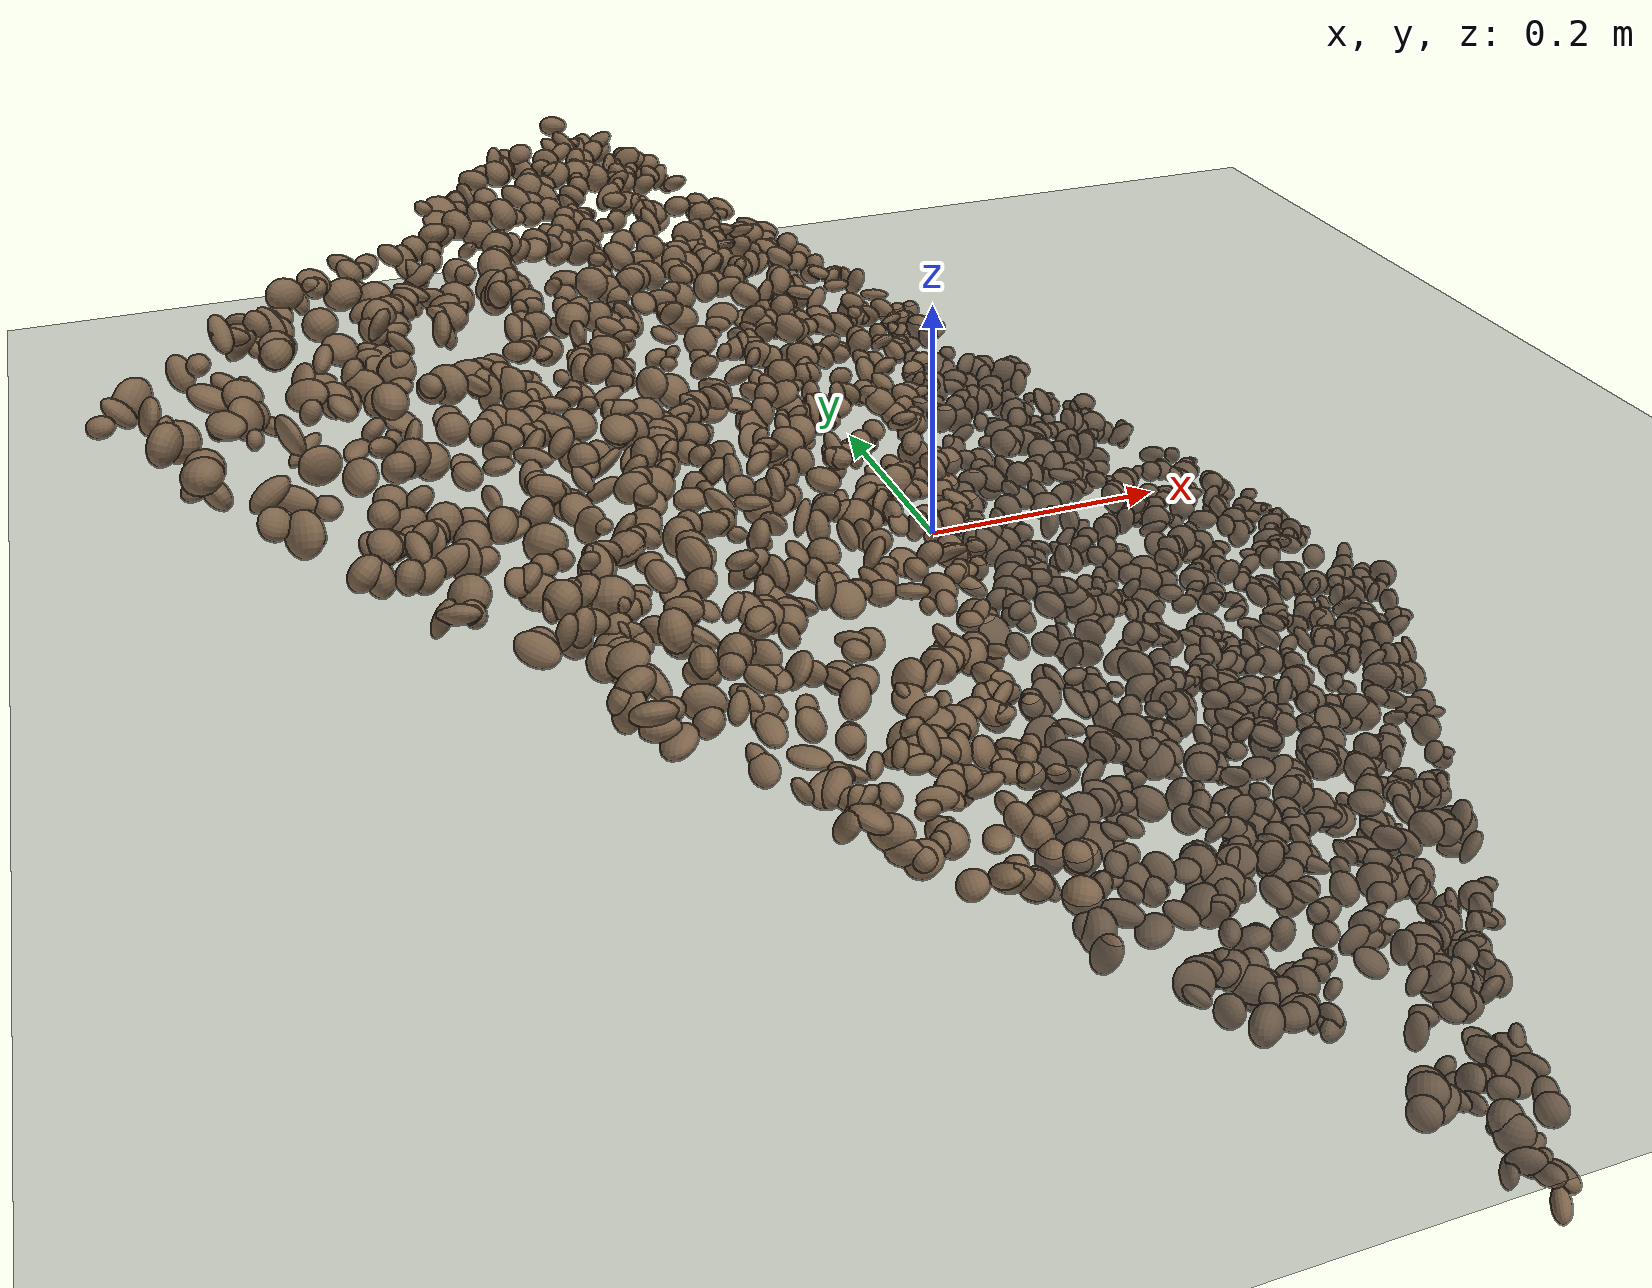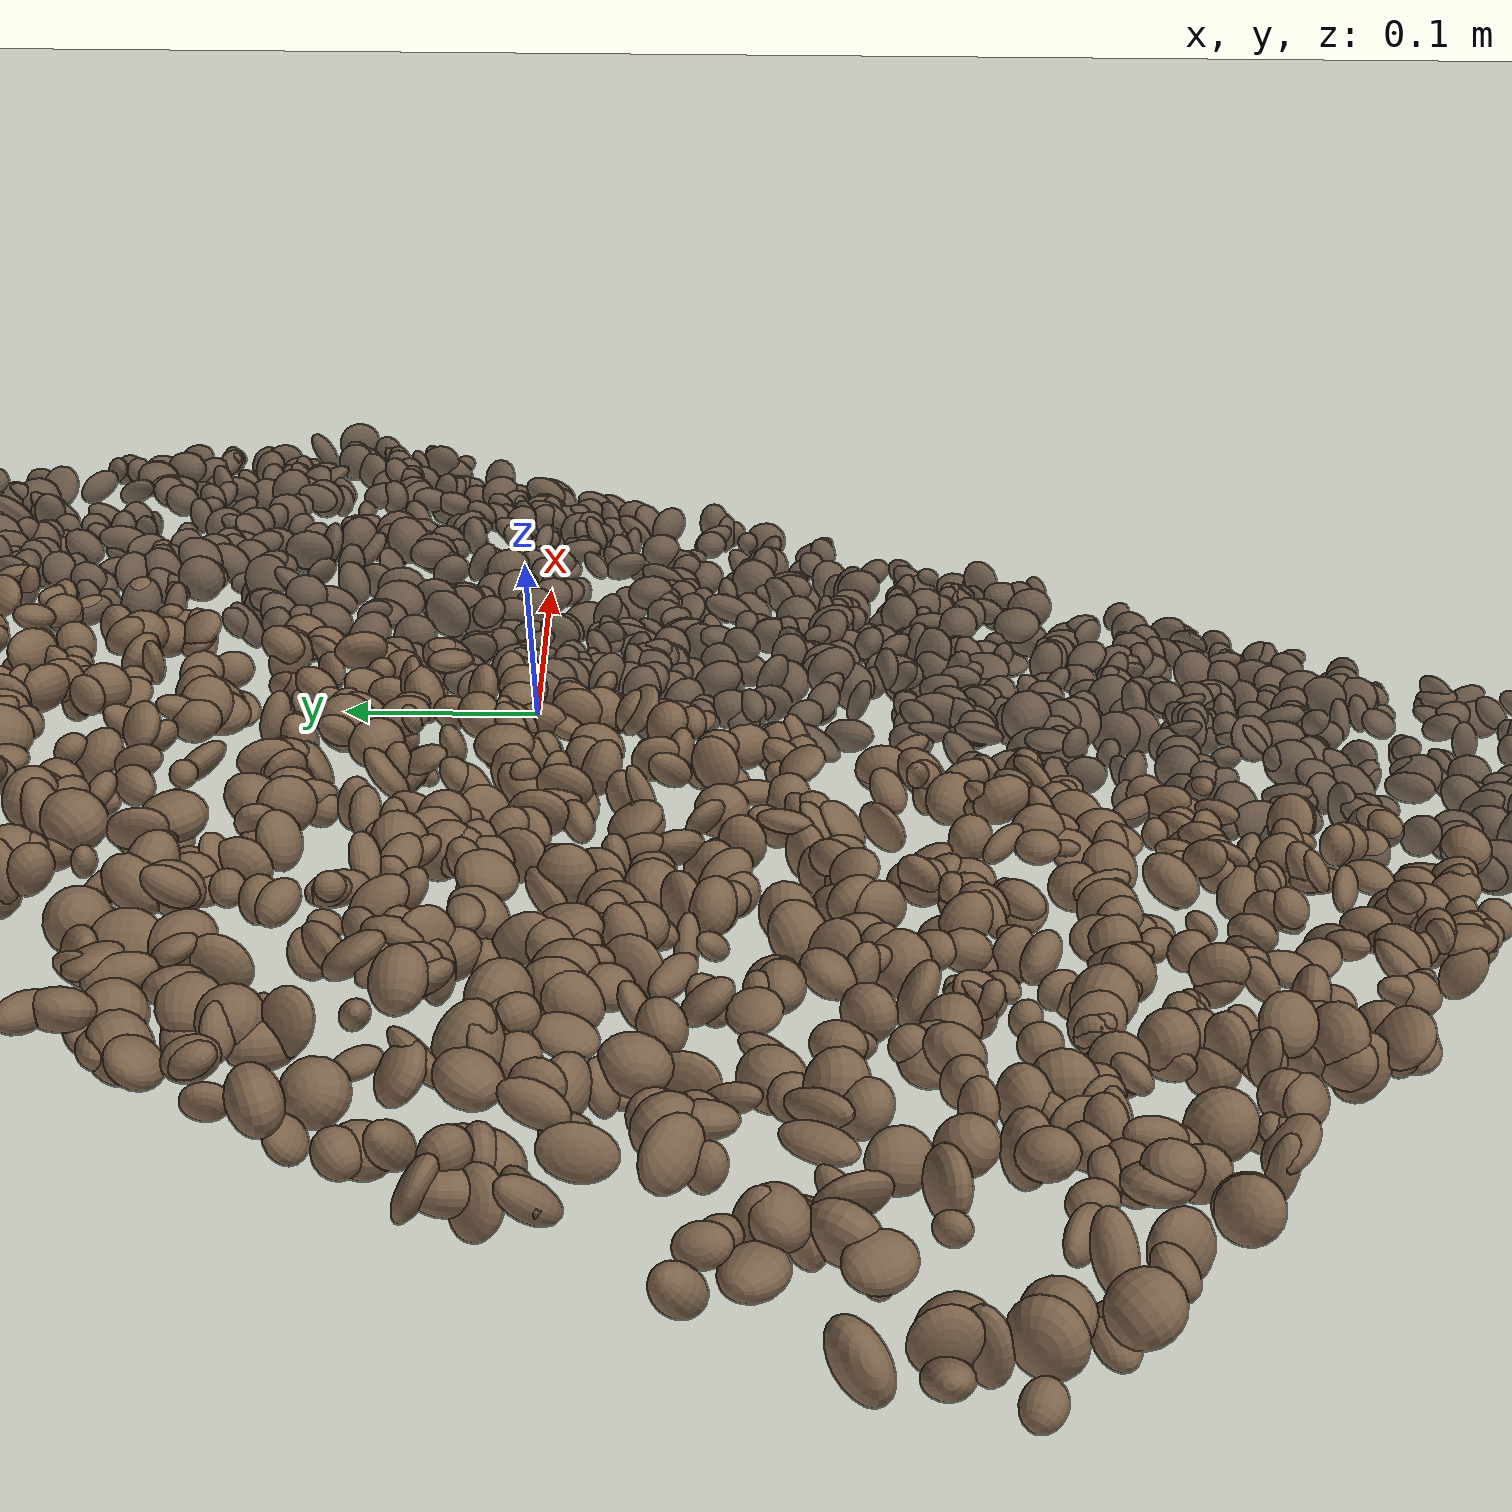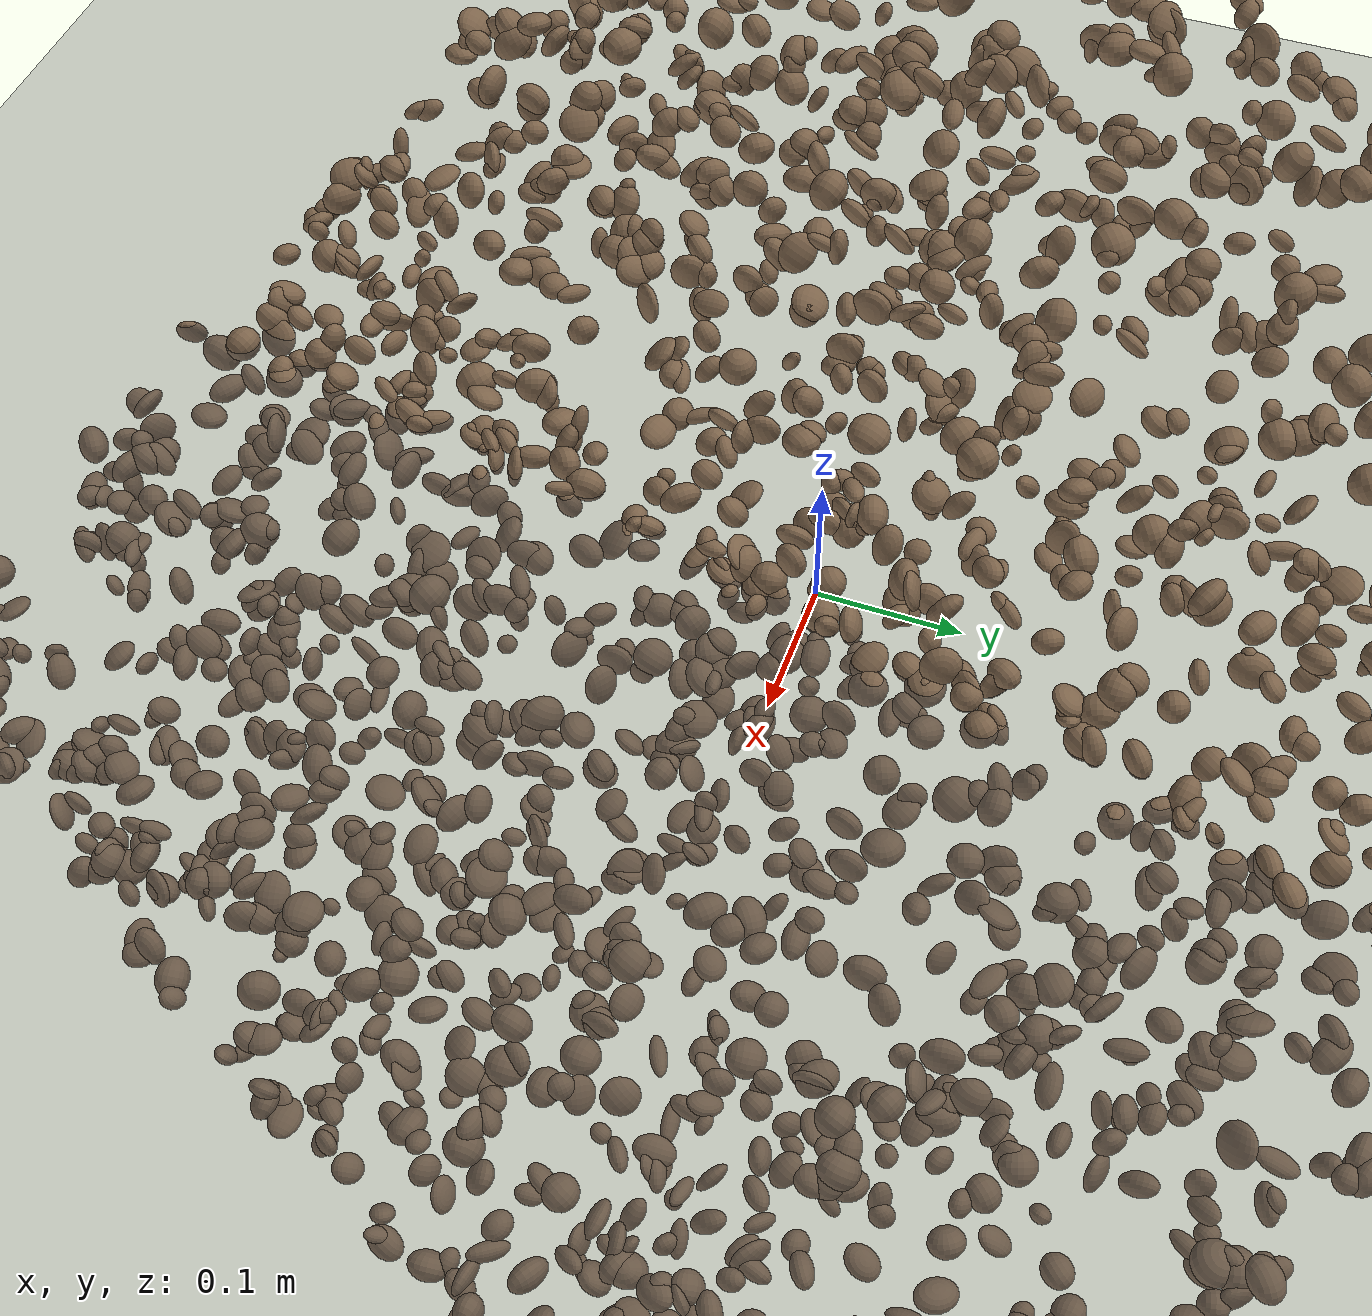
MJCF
<mujoco model="rocky_terrain_scene">
    <compiler angle="radian" inertiafromgeom="true"/>
    <option timestep="0.002" gravity="0 0 -9.81"/>

    <!-- World -->
    <worldbody>
        <light name="sunlight" pos="5 5 5" dir="-1 -1 -1" diffuse="1 1 1" specular="0.5 0.5 0.5" ambient="0.5 0.5 0.5"/>

        <!-- Ground Plane -->
        <geom name="ground_plane" type="plane" size="50 50 0.1" rgba="0.3 0.3 0.3 1"/>

        <!-- Rocky Terrain: Many randomly placed and rotated boxes -->

            <!-- Generate many rocks -->
            <body name="rocky_terrain_body" quat="0.25 0.25 0 0.96">
            <geom name="rock1" type="ellipsoid"
                size="0.013044534601958112 0.013417150421876724 0.012082734864602433"
                pos="0.006794209985417687 -0.14673810586724212 0.008769271940743766"
                quat="0.04581068256901885 0.10224292434200993 0.283797642083701 0.5681487510052702"
                rgba="0.5 0.4 0.3 1" />
            <geom name="rock2" type="ellipsoid"
                size="0.014975003263394009 0.006657257969599917 0.005710374216217119"
                pos="-0.11310595123662304 -0.3637489198939956 0.009579267694210788"
                quat="0.004916208625908084 0.570915382799294 0.1588056952662069 0.26536271330859096"
                rgba="0.5 0.4 0.3 1" />
            <geom name="rock3" type="ellipsoid"
                size="0.007737713496885096 0.011805782275665772 0.005101298217930373"
                pos="-0.26739887834646936 -0.17064989353315752 0.008262940819908905"
                quat="0.5648919290365291 0.17927043836001658 0.23294578574028205 0.02289184686317228"
                rgba="0.5 0.4 0.3 1" />
            <geom name="rock4" type="ellipsoid"
                size="0.010873817593633081 0.013745817005386029 0.01235981667601361"
                pos="0.0980262095915444 0.28862301869578444 0.003040603908133534"
                quat="0.24158449286608846 0.30781636961793707 0.41220043979246596 0.03839869772350847"
                rgba="0.5 0.4 0.3 1" />
            <geom name="rock5" type="ellipsoid"
                size="0.00817382148801561 0.012335580130162435 0.0065013744304630704"
                pos="-0.3657825970078129 0.20722119301246733 0.0011407752711463165"
                quat="0.09829646461948185 0.13486302629749086 0.5705759786982401 0.19626453038478717"
                rgba="0.5 0.4 0.3 1" />
            <geom name="rock6" type="ellipsoid"
                size="0.014285065689691245 0.014757625724863097 0.007302326630026329"
                pos="-0.28624697209669947 0.02509132967760519 0.014336953476829863"
                quat="0.3274891076983537 0.1738556692932828 0.012983331944779908 0.48567189106358355"
                rgba="0.5 0.4 0.3 1" />
            <geom name="rock7" type="ellipsoid"
                size="0.011916931930445374 0.014193430404897203 0.013526845466440722"
                pos="-0.3922954479865224 -0.2216506173084788 0.0070133086381340085"
                quat="0.7064383661858974 0.029369762046174752 0.05481519982675365 0.2093766719411742"
                rgba="0.5 0.4 0.3 1" />
            <geom name="rock8" type="ellipsoid"
                size="0.005204172064946227 0.008089853657651209 0.01417876675838526"
                pos="-0.3836987216823061 -0.21189565146741174 0.0070265968934147905"
                quat="0.3439977680037072 0.19414331204016222 0.0995262474809101 0.36233267247522055"
                rgba="0.5 0.4 0.3 1" />
            <geom name="rock9" type="ellipsoid"
                size="0.01151807227983702 0.01235350739818454 0.007339123505930918"
                pos="0.10124619939894819 0.31706282648536244 0.005308694106588426"
                quat="0.35636737155669607 0.1601533490642941 0.1313505369540313 0.35212874242497855"
                rgba="0.5 0.4 0.3 1" />
            <geom name="rock10" type="ellipsoid"
                size="0.007305982983708848 0.010837919982806154 0.012049673677518228"
                pos="0.4949096690849516 0.16409569581464512 0.008795507480050395"
                quat="0.056440974731169914 0.37701969613970815 0.1519139009961021 0.4146254281330198"
                rgba="0.5 0.4 0.3 1" />
            <geom name="rock11" type="ellipsoid"
                size="0.0075723323402744815 0.009067638853083612 0.014170855273533355"
                pos="-0.010485631666120487 -0.18045498413754013 0.007060527851840515"
                quat="0.1835247590251726 0.08031550948822837 0.3058530996439645 0.4303066318426345"
                rgba="0.5 0.4 0.3 1" />
            <geom name="rock12" type="ellipsoid"
                size="0.006360109615124844 0.009185938235556943 0.011698457519916355"
                pos="0.4744581750592223 0.12525476941420732 0.0013313843515062485"
                quat="0.020922162887422987 0.3509158640893033 0.2405244592008857 0.3876375138223881"
                rgba="0.5 0.4 0.3 1" />
            <geom name="rock13" type="ellipsoid"
                size="0.012141509928387795 0.00734340438560019 0.0073727292438110935"
                pos="0.46438789583987494 -0.39643620045228145 0.010972737957118383"
                quat="0.40084903458173726 0.12354840918941166 0.2979010258064469 0.17770153042240425"
                rgba="0.5 0.4 0.3 1" />
            <geom name="rock14" type="ellipsoid"
                size="0.01264579291341141 0.010554912230490585 0.010316705045473044"
                pos="-0.19672152974128332 -0.11929569310881338 0.011348440260406285"
                quat="0.014440016466391859 0.1075999282056362 0.5440041220923669 0.333955933235605"
                rgba="0.5 0.4 0.3 1" />
            <geom name="rock15" type="ellipsoid"
                size="0.007004161267208639 0.012729125006604888 0.012863924311121735"
                pos="0.22470592171189108 0.09415287120400873 0.00999991514992457"
                quat="0.03521510917298069 0.49602531781360204 0.17176630845607624 0.29699326455734104"
                rgba="0.5 0.4 0.3 1" />
            <geom name="rock16" type="ellipsoid"
                size="0.010131282748117521 0.006895978252448048 0.008301637889805357"
                pos="-0.2607560267845348 0.07016925778037286 0.004815648688685303"
                quat="0.33858585547349446 0.18398705545267718 0.28414286875928896 0.19328422031453937"
                rgba="0.5 0.4 0.3 1" />
            <geom name="rock17" type="ellipsoid"
                size="0.011193512739744102 0.014777840686020591 0.010465780803474382"
                pos="0.36556987664547724 0.05020543303670122 0.008366091591775428"
                quat="0.042475501683295766 0.3946500712644199 0.11907812225072956 0.4437963048015548"
                rgba="0.5 0.4 0.3 1" />
            <geom name="rock18" type="ellipsoid"
                size="0.014994375303428484 0.010620302339942878 0.012713095603540038"
                pos="0.20159896769738728 0.2593161000514119 0.004536693690784113"
                quat="0.35282574227279384 0.23376997437822594 0.40883665097775257 0.004567632371227711"
                rgba="0.5 0.4 0.3 1" />
            <geom name="rock19" type="ellipsoid"
                size="0.009215667249035487 0.009818565363700928 0.012401725210658762"
                pos="0.31165258338736956 -0.2912458317717205 0.01432569365943583"
                quat="0.09809256280171673 0.30128608333387374 0.29829276709639096 0.30232858676801855"
                rgba="0.5 0.4 0.3 1" />
            <geom name="rock20" type="ellipsoid"
                size="0.006070291769252639 0.009182444882370076 0.006686542796273002"
                pos="-0.4741367847927682 0.25931993229935013 0.014844387525615534"
                quat="0.5446410532875238 0.12382351716477011 0.24251779791411635 0.08901763163358978"
                rgba="0.5 0.4 0.3 1" />
            <geom name="rock21" type="ellipsoid"
                size="0.014956594704059564 0.006852638284468262 0.006231205331119033"
                pos="0.3684962589327483 0.35344986390283095 0.012396551212430698"
                quat="0.20490482138020671 0.34148413668868305 0.23474352603760232 0.21886751589350803"
                rgba="0.5 0.4 0.3 1" />
            <geom name="rock22" type="ellipsoid"
                size="0.007008855777080012 0.012214008338805076 0.013445138406296978"
                pos="0.13357239457675185 0.10043544306089303 0.014160243660897198"
                quat="0.5059246525320186 0.2583324430438696 0.19544078684557306 0.04030211757853892"
                rgba="0.5 0.4 0.3 1" />
            <geom name="rock23" type="ellipsoid"
                size="0.009890637977230315 0.011991041158565842 0.01345981260083828"
                pos="-0.17010608171069463 0.2914006349998638 0.011324185636223593"
                quat="0.21665193874064817 0.011813213593197924 0.3716962170150666 0.3998386306510872"
                rgba="0.5 0.4 0.3 1" />
            <geom name="rock24" type="ellipsoid"
                size="0.007667150991732609 0.010973926965770972 0.010814276897761042"
                pos="0.39795508577567684 -0.4295183593459453 0.006134471826825427"
                quat="0.35537978647598334 0.4748418426783438 0.1055800260180521 0.06419834482762087"
                rgba="0.5 0.4 0.3 1" />
            <geom name="rock25" type="ellipsoid"
                size="0.013177092314178528 0.010657249840728744 0.008252513702610357"
                pos="-0.08487477033961077 0.13914566538649376 0.007291664476845388"
                quat="0.06275632617320191 0.3796107957075132 0.39399367040913214 0.16363920771015272"
                rgba="0.5 0.4 0.3 1" />
            <geom name="rock26" type="ellipsoid"
                size="0.007005889082688604 0.007090770717834521 0.006788892765324758"
                pos="-0.2558193396448366 0.2335938941434934 0.005705104324048435"
                quat="0.3695544182681728 0.29405833444336055 0.27756089228443726 0.058826355004029426"
                rgba="0.5 0.4 0.3 1" />
            <geom name="rock27" type="ellipsoid"
                size="0.011694883840895011 0.007692863829720505 0.005860977773982572"
                pos="0.44451260682302174 -0.18294283761644647 0.003784849181356687"
                quat="0.2503466189577471 0.5530877923405548 0.17232379555223934 0.024241793149458696"
                rgba="0.5 0.4 0.3 1" />
            <geom name="rock28" type="ellipsoid"
                size="0.01141158243229319 0.011517560654157653 0.014807115826078396"
                pos="0.1490602320401868 0.3838689210194355 0.009725903901555184"
                quat="0.20561949750124833 0.20656071336854215 0.04321118836048209 0.5446086007697274"
                rgba="0.5 0.4 0.3 1" />
            <geom name="rock29" type="ellipsoid"
                size="0.009621238143738964 0.007759524664050017 0.013015315590403781"
                pos="-0.27609291306997374 -0.25110307327265236 0.010132001454973436"
                quat="0.3062890842697153 0.20200350412550028 0.2271761825804414 0.26453122902434306"
                rgba="0.5 0.4 0.3 1" />
            <geom name="rock30" type="ellipsoid"
                size="0.008330546837585726 0.013167242567855297 0.006370632950067635"
                pos="0.3197821355885152 0.15525744348894754 0.00027619013560704507"
                quat="0.061683328689447536 0.33201551053833706 0.22391338320143497 0.3823877775707805"
                rgba="0.5 0.4 0.3 1" />
            <geom name="rock31" type="ellipsoid"
                size="0.011693141178747323 0.006760938389011168 0.012625645773366199"
                pos="-0.3284737387712784 -0.033116300438688406 0.012039006922117245"
                quat="0.4826736116667896 0.1256766094372076 0.051476099572485175 0.3401736793235175"
                rgba="0.5 0.4 0.3 1" />
            <geom name="rock32" type="ellipsoid"
                size="0.010200199813549025 0.006673432224515272 0.009563101062151098"
                pos="-0.25640456679583523 -0.2320597079449881 0.00685131470683892"
                quat="0.13840584683288285 0.3203408249150161 0.0853163489312958 0.4559369793208052"
                rgba="0.5 0.4 0.3 1" />
            <geom name="rock33" type="ellipsoid"
                size="0.006818802489477203 0.014952390474734973 0.012575119031249568"
                pos="0.16859993013306063 0.4407125128146273 0.004044721362966102"
                quat="0.12826255550897603 0.353127290818978 0.26978128064436524 0.24882887302768072"
                rgba="0.5 0.4 0.3 1" />
            <geom name="rock34" type="ellipsoid"
                size="0.00588446014456725 0.011817918150249813 0.008273794542649829"
                pos="-0.07240598111199048 0.3633392683037491 0.0054362718287024265"
                quat="0.35671451469892423 0.037204418973815594 0.15977170127539425 0.4463093650518659"
                rgba="0.5 0.4 0.3 1" />
            <geom name="rock35" type="ellipsoid"
                size="0.014902768798428171 0.005930350930490986 0.013978875757922789"
                pos="0.41615330354228885 0.39042763216529996 0.008408885693105854"
                quat="0.22432615769460454 0.387667620028134 0.022709947753994802 0.3652962745232667"
                rgba="0.5 0.4 0.3 1" />
            <geom name="rock36" type="ellipsoid"
                size="0.008539889863996843 0.009515811460140857 0.006004100869379982"
                pos="0.3936186280773968 0.2481616937758111 0.006132247983225795"
                quat="0.3154527382599521 0.07290551474805428 0.19472423246079965 0.41691751453119386"
                rgba="0.5 0.4 0.3 1" />
            <geom name="rock37" type="ellipsoid"
                size="0.01222202914423792 0.010514563569017353 0.011961655319062355"
                pos="-0.05963255675611967 0.4543064475624049 0.006796809084827475"
                quat="0.36895778934113055 0.230920855594058 0.1629602873596716 0.23716106770513984"
                rgba="0.5 0.4 0.3 1" />
            <geom name="rock38" type="ellipsoid"
                size="0.008028640974840733 0.005001270974129516 0.009214278164472641"
                pos="-0.24628017889611753 -0.03401450821440455 0.002593980438113057"
                quat="0.08023739949908987 0.005694546770366537 0.7187679473239903 0.19530010640655335"
                rgba="0.5 0.4 0.3 1" />
            <geom name="rock39" type="ellipsoid"
                size="0.010918133887739278 0.012532261565337663 0.008890740506314719"
                pos="0.42100614257019 -0.2904981931598737 0.005752142892273665"
                quat="0.1235466583873372 0.2596898906885342 0.43873109924657705 0.17803235167755163"
                rgba="0.5 0.4 0.3 1" />
            <geom name="rock40" type="ellipsoid"
                size="0.010913618301273372 0.01332686692010842 0.005413995152242652"
                pos="0.05134829258625728 0.02009869834241884 0.010522078404613756"
                quat="0.08655286578137618 0.5484842031120226 0.012126941449053215 0.352835989657548"
                rgba="0.5 0.4 0.3 1" />
            <geom name="rock41" type="ellipsoid"
                size="0.00779754212580418 0.008592760948597289 0.005622567010779143"
                pos="0.023048508880215812 -0.24807219220639842 0.009396923257078933"
                quat="0.10337749181900749 0.05171674966081969 0.35836382135726863 0.4865419371629042"
                rgba="0.5 0.4 0.3 1" />
            <geom name="rock42" type="ellipsoid"
                size="0.012565886401129687 0.014801746271047769 0.013005531363982418"
                pos="0.3386907992067676 -0.006389993794922444 0.014115410537761549"
                quat="0.06193568486543819 0.5806492954658431 0.005630339266708951 0.3517846804020098"
                rgba="0.5 0.4 0.3 1" />
            <geom name="rock43" type="ellipsoid"
                size="0.011948257452750917 0.005852904985261784 0.0056644657564918445"
                pos="-0.10037640892956301 0.33670970750681506 0.01344904221726202"
                quat="0.3373455401420985 0.1967298501334588 0.1628286322057143 0.30309597751872835"
                rgba="0.5 0.4 0.3 1" />
            <geom name="rock44" type="ellipsoid"
                size="0.008400735315616267 0.006640073914324338 0.008274656566977519"
                pos="-0.0701870819558913 0.05817138868080085 0.005821117489427225"
                quat="0.16493508595422693 0.2828467072824627 0.29266820276829864 0.25955000399501177"
                rgba="0.5 0.4 0.3 1" />
            <geom name="rock45" type="ellipsoid"
                size="0.005157047339867193 0.01282465603254188 0.011988870948258507"
                pos="-0.10468285906320274 -0.030163460245687723 0.00044787697852640085"
                quat="0.21770716594622105 0.1990386973012981 0.17695708119070397 0.406297055561777"
                rgba="0.5 0.4 0.3 1" />
            <geom name="rock46" type="ellipsoid"
                size="0.013023012402778481 0.008763275188187829 0.006703448793815797"
                pos="-0.2946655937959063 -0.17930507363821335 0.007752370537605331"
                quat="0.17590816595410835 0.25177906913732523 0.33044727004809926 0.2418654948604671"
                rgba="0.5 0.4 0.3 1" />
            <geom name="rock47" type="ellipsoid"
                size="0.011566411727828164 0.009085732597589113 0.009484177726591854"
                pos="0.30061045126469776 -0.04916003909029232 0.012518238204116107"
                quat="0.27460302767471717 0.28824538087861246 0.26283452649098965 0.17431706495568078"
                rgba="0.5 0.4 0.3 1" />
            <geom name="rock48" type="ellipsoid"
                size="0.005741847398954916 0.005469777645318572 0.01430835836608323"
                pos="-0.2846431073637735 -0.14332563623812455 0.013821319307983063"
                quat="0.046973485892442594 0.18981150898113286 0.41810301932613775 0.34511198580028674"
                rgba="0.5 0.4 0.3 1" />
            <geom name="rock49" type="ellipsoid"
                size="0.011897048057968582 0.0072412321575471604 0.006541832748134545"
                pos="0.45996730766204064 -0.006707813420897102 0.009282814321624425"
                quat="0.0945775888008534 0.34119471037527827 0.3275900523670168 0.23663764845685156"
                rgba="0.5 0.4 0.3 1" />
            <geom name="rock50" type="ellipsoid"
                size="0.007739677865416137 0.01095785015907696 0.014326640278843752"
                pos="-0.2746935250530025 -0.48529635156613604 0.008835791514198547"
                quat="0.3243226754243376 0.34532686607688384 0.013108468943841647 0.317241989554937"
                rgba="0.5 0.4 0.3 1" />
            <geom name="rock51" type="ellipsoid"
                size="0.012487698847428483 0.013866954738637957 0.005893582413614058"
                pos="-0.4741160602302751 0.2933005628222898 0.011139901732562366"
                quat="0.4176466463706507 0.2372985699348745 0.3349004958785966 0.010154287815878207"
                rgba="0.5 0.4 0.3 1" />
            <geom name="rock52" type="ellipsoid"
                size="0.011304238143159635 0.013886348852615832 0.010825277980159045"
                pos="-0.2719326996616179 -0.46705950723518763 0.014299595731366375"
                quat="0.48588589470194715 0.04688085102564108 0.430354316131157 0.03687893814125485"
                rgba="0.5 0.4 0.3 1" />
            <geom name="rock53" type="ellipsoid"
                size="0.011253148000082348 0.006696640930868415 0.00842251464104753"
                pos="-0.23638731787189382 -0.12393540309828288 0.006240307278092416"
                quat="0.6783717771406417 0.004485309644228363 0.17817537357600088 0.1389675396391291"
                rgba="0.5 0.4 0.3 1" />
            <geom name="rock54" type="ellipsoid"
                size="0.011801167568617595 0.013096092874231649 0.007367115367324737"
                pos="-0.4332340931512001 0.4297352088030406 0.012640580864090128"
                quat="0.3749029305842581 0.07028103191988323 0.3958123175420724 0.15900371995378618"
                rgba="0.5 0.4 0.3 1" />
            <geom name="rock55" type="ellipsoid"
                size="0.01347746320010517 0.00757263668831225 0.007938342607844373"
                pos="0.3110854438206069 -0.09312175035779047 0.006871928573452686"
                quat="0.5695623692032065 0.14365552222311712 0.008752151285440869 0.27802995728823554"
                rgba="0.5 0.4 0.3 1" />
            <geom name="rock56" type="ellipsoid"
                size="0.013200718848720198 0.005370640757248052 0.008771110439771421"
                pos="-0.2848013052084961 -0.36505109053427487 0.01282079021532714"
                quat="0.09109460946233573 0.3146676585318862 0.5540048007355654 0.04023293127021271"
                rgba="0.5 0.4 0.3 1" />
            <geom name="rock57" type="ellipsoid"
                size="0.009348684958199894 0.013532649826277738 0.013323111656476334"
                pos="-0.16314835596417598 -0.3020168429796397 0.008057846837824711"
                quat="0.5449505090834604 0.05566340335784134 0.26761549897229203 0.13177058858640625"
                rgba="0.5 0.4 0.3 1" />
            <geom name="rock58" type="ellipsoid"
                size="0.010834641041190834 0.013433616349963977 0.013326765743629596"
                pos="0.31926383102361566 -0.43564028688473744 0.013085129475358276"
                quat="0.1643739000373746 0.14381471060533776 0.43678439018065346 0.25502699917663413"
                rgba="0.5 0.4 0.3 1" />
            <geom name="rock59" type="ellipsoid"
                size="0.009074383896222496 0.005429752812396276 0.0130554585044809"
                pos="-0.38013424269901097 -0.4716085550121253 0.00724623124863337"
                quat="0.33943854672501567 0.1755987920905122 0.2241802455040136 0.26078241568045857"
                rgba="0.5 0.4 0.3 1" />
            <geom name="rock60" type="ellipsoid"
                size="0.01245597975587575 0.009243905854027748 0.014633688222882052"
                pos="0.2595357167036416 -0.4896208153003825 0.012991358374454786"
                quat="0.09323356061652961 0.3397256222818402 0.21796611395964935 0.3490747031419808"
                rgba="0.5 0.4 0.3 1" />
            <geom name="rock61" type="ellipsoid"
                size="0.01358595240652747 0.0077303635921045204 0.007121314390819393"
                pos="0.2940430741312775 -0.035754366435609475 0.005307984981931822"
                quat="0.19870916971477862 0.29040375388149897 0.24988034745940033 0.26100672894432203"
                rgba="0.5 0.4 0.3 1" />
            <geom name="rock62" type="ellipsoid"
                size="0.01343214894411612 0.013618559140272674 0.010353259623998804"
                pos="-0.45439966584079394 -0.36347215004562916 0.0005020907475737701"
                quat="0.0018462716709031041 0.375530280200583 0.32794793433952735 0.29467551378898654"
                rgba="0.5 0.4 0.3 1" />
            <geom name="rock63" type="ellipsoid"
                size="0.006932750003672258 0.008529098388921115 0.01174188716142471"
                pos="0.02969786540758801 0.11582330496893023 0.003975183727631845"
                quat="0.16586587780698134 0.06449987748114658 0.36382832307676916 0.40580592163510293"
                rgba="0.5 0.4 0.3 1" />
            <geom name="rock64" type="ellipsoid"
                size="0.01317695681303415 0.01283611332512637 0.006374444032867511"
                pos="-0.36768035107304475 -0.4588029881770186 0.01255618757348054"
                quat="0.001487948576107557 0.2973668101141204 0.3602736414371543 0.34087159987261784"
                rgba="0.5 0.4 0.3 1" />
            <geom name="rock65" type="ellipsoid"
                size="0.013036765485117108 0.01167227556176349 0.005735136208525085"
                pos="-0.39951615040095445 0.3035203363494742 0.014092242506394102"
                quat="0.25314558944591065 0.16396562137756457 0.3189742642216947 0.26391452495483014"
                rgba="0.5 0.4 0.3 1" />
            <geom name="rock66" type="ellipsoid"
                size="0.01299013388151369 0.008709617447155111 0.005423565333085578"
                pos="0.17555668752880604 -0.4732828387640047 0.010717899566242434"
                quat="0.2903971544338604 0.27678473986088525 0.25935911320915467 0.17345899249609975"
                rgba="0.5 0.4 0.3 1" />
            <geom name="rock67" type="ellipsoid"
                size="0.009759169245656348 0.012946617599437233 0.011681461191382417"
                pos="0.324728826083474 0.17308492311573187 0.003759891397542362"
                quat="0.29904330634249693 0.2696264813306876 0.35833678587208645 0.07299342645472907"
                rgba="0.5 0.4 0.3 1" />
            <geom name="rock68" type="ellipsoid"
                size="0.010104928686257427 0.007634574577463806 0.01087533380278212"
                pos="-0.01591835935893504 -0.38210118593487574 0.0027764491704252"
                quat="0.4057373640573034 0.3541544988518768 0.047215482005784765 0.19289265508503511"
                rgba="0.5 0.4 0.3 1" />
            <geom name="rock69" type="ellipsoid"
                size="0.005529512451163754 0.009126177286458752 0.009577819532003911"
                pos="0.2404802001046613 0.4052512959507748 0.0009223063238799233"
                quat="0.20326567124585382 0.1477696918976271 0.46907235938756864 0.17989227746895048"
                rgba="0.5 0.4 0.3 1" />
            <geom name="rock70" type="ellipsoid"
                size="0.013140107775329937 0.014385610199350259 0.014229747920207536"
                pos="-0.37640596158025597 0.02725607821729703 0.0017420425337796946"
                quat="0.2709807997355791 0.08454257853294708 0.3470936033988644 0.29738301833260944"
                rgba="0.5 0.4 0.3 1" />
            <geom name="rock71" type="ellipsoid"
                size="0.01218957152553057 0.013528230678437076 0.005340912782823183"
                pos="-0.33373751089553005 -0.1888511268798898 0.006426203703242076"
                quat="0.5019562177095476 0.2522235983603298 0.1550657704021001 0.0907544135280225"
                rgba="0.5 0.4 0.3 1" />
            <geom name="rock72" type="ellipsoid"
                size="0.012077812393936554 0.010086480418884929 0.009744675606600434"
                pos="-0.03507504386454674 -0.01578723040359664 0.004246580942214356"
                quat="0.22490815320850985 0.03769914719329257 0.5001561047703545 0.23723659482784307"
                rgba="0.5 0.4 0.3 1" />
            <geom name="rock73" type="ellipsoid"
                size="0.01201873220411041 0.012938233861167266 0.007929003248160432"
                pos="0.004415254487978637 0.02411388998471986 0.012869750073898085"
                quat="0.17599289912714866 0.3434552395580239 0.27813649180641065 0.2024153695084168"
                rgba="0.5 0.4 0.3 1" />
            <geom name="rock74" type="ellipsoid"
                size="0.01220317332140504 0.005112450878746696 0.014464945429731625"
                pos="-0.45773137802618913 0.19627604585349467 0.012303807224490225"
                quat="0.3281549491290533 0.045708241516177125 0.23912804565589946 0.38700876369887005"
                rgba="0.5 0.4 0.3 1" />
            <geom name="rock75" type="ellipsoid"
                size="0.011529315299798792 0.0064382188980124785 0.014768790552521373"
                pos="0.15585152135954494 0.2640254125202186 0.003200921678466823"
                quat="0.11029266561948327 0.266864738718085 0.6147981195702289 0.00804447609220278"
                rgba="0.5 0.4 0.3 1" />
            <geom name="rock76" type="ellipsoid"
                size="0.005887688880448501 0.009406938298741039 0.006009589262045602"
                pos="0.1519957390502472 -0.03615490954254519 0.011128216581448587"
                quat="0.2083316500988226 0.3659760708691808 0.2630734348051551 0.16261884422684153"
                rgba="0.5 0.4 0.3 1" />
            <geom name="rock77" type="ellipsoid"
                size="0.011992365432278301 0.005082586891367317 0.01311084158040654"
                pos="-0.4054890597713995 0.4431044235068251 0.003654361866087139"
                quat="0.3168594131682849 0.22453540348646794 0.34269260441106875 0.1159125789341784"
                rgba="0.5 0.4 0.3 1" />
            <geom name="rock78" type="ellipsoid"
                size="0.014266739364066427 0.014086836663738465 0.01198569994009227"
                pos="0.1668277698148828 -0.3428577095719342 0.004559036408731619"
                quat="0.1335640874415322 0.29371550179877803 0.5211940356157811 0.05152637514390852"
                rgba="0.5 0.4 0.3 1" />
            <geom name="rock79" type="ellipsoid"
                size="0.011089912107594463 0.013854391770227445 0.011568663396883875"
                pos="0.27073742486662145 -0.2492083239930274 0.010324447601270761"
                quat="0.22230537174902051 0.5001518649994751 0.1797425819557608 0.09780018129574365"
                rgba="0.5 0.4 0.3 1" />
            <geom name="rock80" type="ellipsoid"
                size="0.009545479317628513 0.009712680984223747 0.006547562433845094"
                pos="-0.4186858816713015 0.007885313496421076 0.005559734422080825"
                quat="0.2830568491712181 0.3541126854764726 0.09964462378971219 0.2631858415625971"
                rgba="0.5 0.4 0.3 1" />
            <geom name="rock81" type="ellipsoid"
                size="0.01285116369501069 0.009775562590398433 0.010951562552751409"
                pos="0.27029915564462603 0.21192707877914296 0.00650178203373372"
                quat="0.28143283367277944 0.08133143403300075 0.37225617793228805 0.26497955436193177"
                rgba="0.5 0.4 0.3 1" />
            <geom name="rock82" type="ellipsoid"
                size="0.009656254427300451 0.007343367910374905 0.010184966720462083"
                pos="-0.28553563515756375 0.006195432031753878 0.004181985483291945"
                quat="0.129973695457236 0.3774823771350021 0.06394090281762375 0.4286030245901381"
                rgba="0.5 0.4 0.3 1" />
            <geom name="rock83" type="ellipsoid"
                size="0.011790066031408072 0.014574725516154286 0.00553789232171315"
                pos="-0.2884022504893158 0.006538830088326009 0.0030483031386069103"
                quat="0.2047660483577739 0.10073097199801614 0.2766847723548961 0.4178182072893139"
                rgba="0.5 0.4 0.3 1" />
            <geom name="rock84" type="ellipsoid"
                size="0.005225101113187099 0.007593551461873051 0.006044243606175623"
                pos="0.40416195165124524 -0.4611488187783981 0.01149166291312853"
                quat="0.0753296075947662 0.3623681233124715 0.19068395080750364 0.3716183182852587"
                rgba="0.5 0.4 0.3 1" />
            <geom name="rock85" type="ellipsoid"
                size="0.008727934980819767 0.014435716206991273 0.007977164538101027"
                pos="-0.12941554482480855 -0.40844888816288505 0.005399609341316852"
                quat="0.018301270546095656 0.3827105659623543 0.23142352673490849 0.3675646367566415"
                rgba="0.5 0.4 0.3 1" />
            <geom name="rock86" type="ellipsoid"
                size="0.014012807145339267 0.006041014868632343 0.007805530896067928"
                pos="-0.08393475181801424 -0.19507097333541978 0.006579303822522945"
                quat="0.14716407494040512 0.15373415803079288 0.643925395881003 0.055176371147799066"
                rgba="0.5 0.4 0.3 1" />
            <geom name="rock87" type="ellipsoid"
                size="0.008323655099351724 0.007263793854401029 0.01245493146750331"
                pos="0.26742575961325166 0.10309301596447085 0.003019865154313062"
                quat="0.3786632608101146 0.06963062757909712 0.20780934170286008 0.34389676990792817"
                rgba="0.5 0.4 0.3 1" />
            <geom name="rock88" type="ellipsoid"
                size="0.0052830265365199905 0.014436551155629324 0.012299130986629183"
                pos="-0.29963145897526444 0.24920336629707385 0.011692159977271502"
                quat="0.3511220210245669 0.2050075342701842 0.3737657548158835 0.07010468988936543"
                rgba="0.5 0.4 0.3 1" />
            <geom name="rock89" type="ellipsoid"
                size="0.012295264731489924 0.009630612890605437 0.012685600706583647"
                pos="0.438659428706359 0.2575231186371212 0.014724509578632377"
                quat="0.06198269714063235 0.015584402030368602 0.5250385841107243 0.39739431671827463"
                rgba="0.5 0.4 0.3 1" />
            <geom name="rock90" type="ellipsoid"
                size="0.012631524876640324 0.009506775737327375 0.008040642730732756"
                pos="-0.05623569344956525 -0.3932151864032477 0.0062987127172214425"
                quat="0.06938108118594542 0.3117669328004593 0.2242936239902319 0.39455836202336336"
                rgba="0.5 0.4 0.3 1" />
            <geom name="rock91" type="ellipsoid"
                size="0.01107328017209077 0.013928979388238363 0.014353452698355432"
                pos="0.24665162547481867 -0.13374947518838465 0.0032230120088813674"
                quat="0.2567251601850771 0.34237684958106396 0.041327306162844524 0.35957068407101445"
                rgba="0.5 0.4 0.3 1" />
            <geom name="rock92" type="ellipsoid"
                size="0.011063167646518405 0.013221963417710383 0.0073047338312922415"
                pos="-0.496469679258314 0.1746278443044007 0.007712552740183763"
                quat="0.5406498369506672 0.07216791018678263 0.033535820845058927 0.3536464320174913"
                rgba="0.5 0.4 0.3 1" />
            <geom name="rock93" type="ellipsoid"
                size="0.005687169338089574 0.005871838009968 0.008086437828548804"
                pos="0.22477438575570052 0.3039955372134665 0.012445827452237858"
                quat="0.27580010120769105 0.3244877643100128 0.34598508065115735 0.05372705383113886"
                rgba="0.5 0.4 0.3 1" />
            <geom name="rock94" type="ellipsoid"
                size="0.012512678385314727 0.013831866745317074 0.008183844088290334"
                pos="0.16612018154504482 0.4565639860885278 0.014735503842864713"
                quat="0.288190219478601 0.041530954258679635 0.23889569580485592 0.4313831304578634"
                rgba="0.5 0.4 0.3 1" />
            <geom name="rock95" type="ellipsoid"
                size="0.006996107175269722 0.005459034346378695 0.007309850953090604"
                pos="-0.11142533842677871 -0.48916030174214986 0.010065375796399635"
                quat="0.33116659851059627 0.20295796943706074 0.278794171575471 0.18708126047687196"
                rgba="0.5 0.4 0.3 1" />
            <geom name="rock96" type="ellipsoid"
                size="0.012317967283496382 0.012760860586123773 0.011118880224512028"
                pos="0.3760254438444596 -0.005106080175307115 0.007988976150529556"
                quat="0.2829744604324321 0.17147913929963732 0.12443560205742797 0.4211107982105026"
                rgba="0.5 0.4 0.3 1" />
            <geom name="rock97" type="ellipsoid"
                size="0.014817780798080722 0.006590668925258232 0.009394134479110708"
                pos="0.39882366425380134 -0.35215944663392973 0.008993354602431043"
                quat="0.4364141113603098 0.0025504858917543846 0.3545057095846548 0.20652969316328104"
                rgba="0.5 0.4 0.3 1" />
            <geom name="rock98" type="ellipsoid"
                size="0.005013958934805938 0.013112294548309977 0.01464722378437014"
                pos="0.38802579655597047 -0.178643679852466 0.007220578405596436"
                quat="0.10642766040828552 0.2017513393026429 0.17187800502998168 0.5199429952590898"
                rgba="0.5 0.4 0.3 1" />
            <geom name="rock99" type="ellipsoid"
                size="0.01283380447240257 0.005349736698069703 0.009750264734408223"
                pos="0.3560659245799711 0.24486229994295206 0.0014192049008122077"
                quat="0.1771602409370393 0.23178301835854456 0.39585431695753487 0.19520242374688118"
                rgba="0.5 0.4 0.3 1" />
            <geom name="rock100" type="ellipsoid"
                size="0.00805834993001584 0.007385271956837022 0.009447505853447972"
                pos="0.3651343393190588 0.4529531989614326 0.009897275484344116"
                quat="0.3262721038625997 0.33436744804454216 0.26915696175012327 0.07020348634273477"
                rgba="0.5 0.4 0.3 1" />
            <geom name="rock101" type="ellipsoid"
                size="0.01346580003524473 0.007443735659621572 0.00795697316194904"
                pos="-0.46679670291720876 -0.006187512985466048 0.010270576451331599"
                quat="0.29494389719518843 0.254516865626124 0.3023669850032864 0.1481722521754012"
                rgba="0.5 0.4 0.3 1" />
            <geom name="rock102" type="ellipsoid"
                size="0.010115381913083355 0.013912098113967816 0.009201276952028756"
                pos="0.3877879342488818 -0.024006716037820452 0.007106946120932164"
                quat="0.03751121363921644 0.4522376523517745 0.40095602022415355 0.10929511378485557"
                rgba="0.5 0.4 0.3 1" />
            <geom name="rock103" type="ellipsoid"
                size="0.006902533509343934 0.011534890702796301 0.00750667427402205"
                pos="0.40306564655475086 -0.17335453030321735 0.009669184863562823"
                quat="0.040826801668129735 0.10473675426444914 0.30807719315806453 0.5463592509093567"
                rgba="0.5 0.4 0.3 1" />
            <geom name="rock104" type="ellipsoid"
                size="0.014777231126138459 0.005626424324947079 0.009508630520491702"
                pos="-0.2985037691040111 -0.10072016692292807 0.01270520259281729"
                quat="0.3079206502946514 0.013327041470322737 0.21610038782711355 0.4626519204079125"
                rgba="0.5 0.4 0.3 1" />
            <geom name="rock105" type="ellipsoid"
                size="0.007537437522605946 0.009942988028055384 0.010933884209374405"
                pos="0.3139191941095162 0.2366919696270331 0.006237934651019748"
                quat="0.11009519411938132 0.4462689974220439 0.08909493602960418 0.3545408724289706"
                rgba="0.5 0.4 0.3 1" />
            <geom name="rock106" type="ellipsoid"
                size="0.007406553860176392 0.005866291059691113 0.009856213634990084"
                pos="0.17706180009551586 -0.09144232282393294 0.013199079447985767"
                quat="0.3550751325077242 0.2964958739914018 0.166882708641356 0.18154628485951804"
                rgba="0.5 0.4 0.3 1" />
            <geom name="rock107" type="ellipsoid"
                size="0.01312749581381088 0.013031601867322863 0.013462389213629616"
                pos="-0.39184725301121504 -0.3614100618594803 0.004701549547671882"
                quat="0.17645224702808632 0.538608990075069 0.2023627543047966 0.08257600859204803"
                rgba="0.5 0.4 0.3 1" />
            <geom name="rock108" type="ellipsoid"
                size="0.0051305859061779 0.013580334438875453 0.01069558862096366"
                pos="-0.23883461657075988 0.26879209086603395 0.013038213735989944"
                quat="0.4008233957291538 0.21782026650929254 0.377651248604577 0.003705089156976672"
                rgba="0.5 0.4 0.3 1" />
            <geom name="rock109" type="ellipsoid"
                size="0.014427944384658616 0.007186991089112655 0.010374973369350254"
                pos="-0.3282508216218054 -0.1829159615155871 0.009596743217926204"
                quat="0.14751914131586552 0.2381738299718711 0.2664381521399285 0.34786887657233495"
                rgba="0.5 0.4 0.3 1" />
            <geom name="rock110" type="ellipsoid"
                size="0.014444114042854918 0.006364548545326526 0.008514049614700843"
                pos="0.2891141844473266 0.43272807873619934 0.005334198000125281"
                quat="0.5153725587027973 0.021960197264073292 0.3107808729072497 0.15188637112587963"
                rgba="0.5 0.4 0.3 1" />
            <geom name="rock111" type="ellipsoid"
                size="0.006709448054608096 0.011277577569945007 0.011003375433250263"
                pos="-0.08859912487882193 -0.036164471297433276 0.007086531523171157"
                quat="0.33023376332410054 0.22289634277127474 0.1315403516068142 0.3153295422978105"
                rgba="0.5 0.4 0.3 1" />
            <geom name="rock112" type="ellipsoid"
                size="0.011833354703586735 0.012987843874420802 0.007975324817172419"
                pos="0.3060769986282018 0.4129362458275684 0.004944368659773244"
                quat="0.2097965872676469 0.33961097499514836 0.20204011134868458 0.24855232638852012"
                rgba="0.5 0.4 0.3 1" />
            <geom name="rock113" type="ellipsoid"
                size="0.005282758742875472 0.014785036750831614 0.012155462255473912"
                pos="-0.3786979359125132 -0.2583724516772963 0.009008219968500824"
                quat="0.02694396456176929 0.14415105570447753 0.4178506038759511 0.411054375857802"
                rgba="0.5 0.4 0.3 1" />
            <geom name="rock114" type="ellipsoid"
                size="0.008267930143243767 0.009977965214786217 0.007022236189789848"
                pos="-0.4994013230707265 0.13163510341001672 0.010932741156255244"
                quat="0.4260489161993018 0.23780842584981884 0.1362564149695571 0.1998862429813223"
                rgba="0.5 0.4 0.3 1" />
            <geom name="rock115" type="ellipsoid"
                size="0.009105072017007294 0.008740339218692432 0.009901654815228325"
                pos="0.2058185272335512 -0.2469621132692439 0.012150832046799842"
                quat="0.49844159385857695 0.08741794592732502 0.11642417947695508 0.2977162807371429"
                rgba="0.5 0.4 0.3 1" />
            <geom name="rock116" type="ellipsoid"
                size="0.007102269350066446 0.01241279918015131 0.006080805001858191"
                pos="-0.25744195190325236 0.12402137439893057 0.013532011216288706"
                quat="0.3921948219007491 0.3035820606253764 0.27772909886164704 0.026494018612227343"
                rgba="0.5 0.4 0.3 1" />
            <geom name="rock117" type="ellipsoid"
                size="0.006728577210286017 0.011090271274736043 0.011323278522964553"
                pos="0.17350445594634478 -0.4869130927277274 0.00409566535933319"
                quat="0.042017701652443055 0.04945875438959998 0.40741677515331226 0.5011067688046447"
                rgba="0.5 0.4 0.3 1" />
            <geom name="rock118" type="ellipsoid"
                size="0.009144070081419894 0.01194491261378278 0.008056917029153914"
                pos="0.11207051096053111 0.22219470053435608 0.0015110264199176121"
                quat="0.3189901611186466 0.3324225888433789 0.20602294056496004 0.14256430947301452"
                rgba="0.5 0.4 0.3 1" />
            <geom name="rock119" type="ellipsoid"
                size="0.012571768156061754 0.014590604180907612 0.00925161733937002"
                pos="-0.29083343677923323 0.20630598507393116 0.008407296100945915"
                quat="0.3593896566267392 0.17133218142031592 0.23163258836911568 0.23764557358382923"
                rgba="0.5 0.4 0.3 1" />
            <geom name="rock120" type="ellipsoid"
                size="0.008501015862682659 0.010224754109328398 0.011065823684562104"
                pos="-0.12537680148142283 0.3711462351599426 0.009251471716964929"
                quat="0.26193617489184656 0.10275477129518328 0.142109078647217 0.4931999751657531"
                rgba="0.5 0.4 0.3 1" />
            <geom name="rock121" type="ellipsoid"
                size="0.009918680998474722 0.01437051358055827 0.008422991743312874"
                pos="0.2707335715485061 -0.2841272421245157 0.00623659867825505"
                quat="0.29822211187579617 0.005427858364122856 0.37507295925158807 0.3212770705084929"
                rgba="0.5 0.4 0.3 1" />
            <geom name="rock122" type="ellipsoid"
                size="0.009589348106550783 0.010729104473363988 0.005534483809984569"
                pos="-0.3544000060541427 -0.4931529110758709 0.007637206076252779"
                quat="0.3186491444940801 0.24593514408244416 0.33896436227630355 0.09645134914717225"
                rgba="0.5 0.4 0.3 1" />
            <geom name="rock123" type="ellipsoid"
                size="0.00966200548273954 0.007476111758096047 0.012909511614243526"
                pos="-0.43679128545099066 0.06289100510009837 0.008195718113476995"
                quat="0.34946234128427217 0.3458762199119151 0.03150727322681493 0.2731541655769979"
                rgba="0.5 0.4 0.3 1" />
            <geom name="rock124" type="ellipsoid"
                size="0.012109003785968296 0.012850632300779843 0.007161550328638914"
                pos="0.4251629273132631 0.2215081771969053 0.0013455418915980489"
                quat="0.34769643636604236 0.28338809688143 0.0331753820082194 0.3357400847443082"
                rgba="0.5 0.4 0.3 1" />
            <geom name="rock125" type="ellipsoid"
                size="0.011074355669232865 0.008485246909471012 0.01477603812265501"
                pos="-0.16112571777514728 -0.2228841099794192 0.0026961305200748657"
                quat="0.3138918114507837 0.036890277438252184 0.2501037278319991 0.3991141832789651"
                rgba="0.5 0.4 0.3 1" />
            <geom name="rock126" type="ellipsoid"
                size="0.009298618135307557 0.013917715460364938 0.006978354921003915"
                pos="0.3009229068460305 0.11997378203362408 0.004666896875378726"
                quat="0.3807175716775594 0.08598961651378212 0.2833636620451383 0.24992914976352024"
                rgba="0.5 0.4 0.3 1" />
            <geom name="rock127" type="ellipsoid"
                size="0.013174327388527203 0.01337031145915004 0.014495012904697423"
                pos="0.4153303750868821 0.06685407380949693 0.010419203750047385"
                quat="0.23253507642634877 0.07829856094510611 0.24929215773721736 0.4398742048913277"
                rgba="0.5 0.4 0.3 1" />
            <geom name="rock128" type="ellipsoid"
                size="0.006717565842606355 0.012802521026494151 0.011412438502318992"
                pos="0.04407845686055545 0.10972615983175737 0.014960682453835285"
                quat="0.1932679757980913 0.19720812378249156 0.32621949850700704 0.2833044019124101"
                rgba="0.5 0.4 0.3 1" />
            <geom name="rock129" type="ellipsoid"
                size="0.007591329157027456 0.011636871279305239 0.011957351773838807"
                pos="-0.10487714012702254 -0.37522332655204604 0.009357299073666737"
                quat="0.19355355279062889 0.09553546521483472 0.31477128469553295 0.3961396972990034"
                rgba="0.5 0.4 0.3 1" />
            <geom name="rock130" type="ellipsoid"
                size="0.006510124949761382 0.005455152629273171 0.011443076254490706"
                pos="-0.13626316297488816 0.2154611134200496 0.0025316164072576707"
                quat="0.23938423620201593 0.2752047496090144 0.3038949577831119 0.18151605640585788"
                rgba="0.5 0.4 0.3 1" />
            <geom name="rock131" type="ellipsoid"
                size="0.011377904985045676 0.006091697824403426 0.014529867587311788"
                pos="-0.16510858682941276 -0.48143128835787574 0.008646051207853922"
                quat="0.08086828325874175 0.3202949571473795 0.49177817738776786 0.10705858220611084"
                rgba="0.5 0.4 0.3 1" />
            <geom name="rock132" type="ellipsoid"
                size="0.007853942304423663 0.008268241189798029 0.009071619341063753"
                pos="0.3156946757522744 0.18220444234035915 0.0018562118837562624"
                quat="0.1630421817152519 0.1928350493025602 0.3110386069770844 0.33308416200510355"
                rgba="0.5 0.4 0.3 1" />
            <geom name="rock133" type="ellipsoid"
                size="0.008713512517450062 0.013861883066763479 0.008564446545867795"
                pos="0.15467146485046668 0.18933952302303525 0.005649891161659908"
                quat="0.2272222228954382 0.13351043230538706 0.44793095014104917 0.1913363946581255"
                rgba="0.5 0.4 0.3 1" />
            <geom name="rock134" type="ellipsoid"
                size="0.014341876687001466 0.010100356861644389 0.01110075906942334"
                pos="0.2874089689308359 -0.32291164262210237 0.010500526403965057"
                quat="0.13839135024776708 0.2971297758165124 0.3698455041892903 0.19463336974643033"
                rgba="0.5 0.4 0.3 1" />
            <geom name="rock135" type="ellipsoid"
                size="0.012588862390260663 0.0064578031081496175 0.012889541079259902"
                pos="0.3739881084021226 -0.4981973796975824 0.00530558025191063"
                quat="0.24573967590489096 0.29801415361975103 0.09273192607759426 0.36351424439776386"
                rgba="0.5 0.4 0.3 1" />
            <geom name="rock136" type="ellipsoid"
                size="0.010917414852025955 0.010548994055794202 0.005645056959396508"
                pos="0.3046068264493549 0.29388110774750864 0.010880037779277223"
                quat="0.2632016247060016 0.1625854198394274 0.08984222991523651 0.4843707255393346"
                rgba="0.5 0.4 0.3 1" />
            <geom name="rock137" type="ellipsoid"
                size="0.014242853319827137 0.012393094471297827 0.0070094219887308"
                pos="-0.19994373968891954 -0.01497752674079289 0.0032123790285455037"
                quat="0.34894361541221897 0.17090155451288674 0.2961943322078543 0.18396049786703994"
                rgba="0.5 0.4 0.3 1" />
            <geom name="rock138" type="ellipsoid"
                size="0.011776129225037603 0.006758528341731528 0.008320804439653929"
                pos="-0.20172160924820493 0.1366840722019993 0.013688191925376719"
                quat="0.17293455000884472 0.32693540428514256 0.24118369934729517 0.2589463463587175"
                rgba="0.5 0.4 0.3 1" />
            <geom name="rock139" type="ellipsoid"
                size="0.013460300248092551 0.007605269345951094 0.0053241888731114795"
                pos="0.257526755098444 -0.043927108386062286 0.01365998842213936"
                quat="0.21009965048320928 0.28913986327642105 0.17545361944928647 0.32530686679108317"
                rgba="0.5 0.4 0.3 1" />
            <geom name="rock140" type="ellipsoid"
                size="0.010220594666114387 0.00515205658613175 0.013008156239922342"
                pos="0.35062856018279875 -0.39299471137926834 0.000446253685031161"
                quat="0.5602294510261256 0.23119696675834517 0.17782044248069365 0.030753139734835594"
                rgba="0.5 0.4 0.3 1" />
            <geom name="rock141" type="ellipsoid"
                size="0.01162281523817452 0.01041263884084372 0.01145505881748474"
                pos="-0.47483441057250797 -0.22876490508247593 0.00845808292040038"
                quat="0.23063695071548124 0.26940046768271086 0.24780332255875118 0.2521592590430568"
                rgba="0.5 0.4 0.3 1" />
            <geom name="rock142" type="ellipsoid"
                size="0.00956363440981273 0.012727557775987768 0.012615362659172392"
                pos="-0.43861914773091926 0.3031773447499847 0.01308258463863181"
                quat="0.09768388697642147 0.07353225326491976 0.4728983719640681 0.35588548779459067"
                rgba="0.5 0.4 0.3 1" />
            <geom name="rock143" type="ellipsoid"
                size="0.00995039977103641 0.007995181767009765 0.00513701849701265"
                pos="0.25766842337069706 -0.3528957843436755 0.011269977934143928"
                quat="0.1588124748279928 0.30403198588575137 0.21042354052474382 0.32673199876151204"
                rgba="0.5 0.4 0.3 1" />
            <geom name="rock144" type="ellipsoid"
                size="0.009686724132516984 0.01315700187773967 0.009298946063641594"
                pos="0.45947745644058147 -0.4678419733978043 0.005878281318252245"
                quat="0.08758057123433818 0.3153990397868488 0.21049824645990062 0.3865221425189124"
                rgba="0.5 0.4 0.3 1" />
            <geom name="rock145" type="ellipsoid"
                size="0.005418429314676332 0.014561702617264558 0.010175379561697095"
                pos="-0.21889825140387942 -0.4639128152163142 0.003995087550937812"
                quat="0.4068556463463968 0.2137950340735721 0.32694839054994146 0.052400929030089666"
                rgba="0.5 0.4 0.3 1" />
            <geom name="rock146" type="ellipsoid"
                size="0.006628254590072599 0.010873689492718087 0.006390404288647491"
                pos="-0.12322153263965385 -0.47287478174669817 0.009526778573093624"
                quat="0.10716824806606787 0.6434548928996012 0.13873839035951185 0.11063846867481902"
                rgba="0.5 0.4 0.3 1" />
            <geom name="rock147" type="ellipsoid"
                size="0.013786225830806697 0.0149576938391962 0.013278968898137563"
                pos="-0.25214249121306165 -0.27471596816513366 0.011124032074362723"
                quat="0.3109666337674792 0.13280082062932275 0.3160793004646272 0.24015324513857086"
                rgba="0.5 0.4 0.3 1" />
            <geom name="rock148" type="ellipsoid"
                size="0.0057810779095324345 0.009678981431170398 0.012101302469349932"
                pos="-0.47991069789418506 -0.2271116248158226 0.0033463381113227274"
                quat="0.3668549653493048 0.20370908100067447 0.33860566222880767 0.09083029142121307"
                rgba="0.5 0.4 0.3 1" />
            <geom name="rock149" type="ellipsoid"
                size="0.005166433718608211 0.005675490106880958 0.011174299567849879"
                pos="0.17513881783466245 -0.2745303594217856 0.005304916439798675"
                quat="0.44135396413578504 0.418949384510738 0.017623767227892904 0.12207288412558412"
                rgba="0.5 0.4 0.3 1" />
            <geom name="rock150" type="ellipsoid"
                size="0.0076206572688121395 0.005484846162907688 0.006833994543417566"
                pos="-0.3900709172914413 -0.20274071584579356 0.010705994140325121"
                quat="0.37331833890480465 0.13384765747097052 0.10805941737637828 0.3847745862478466"
                rgba="0.5 0.4 0.3 1" />
            <geom name="rock151" type="ellipsoid"
                size="0.005874847573562614 0.006782154880892863 0.007742194697596773"
                pos="0.35994890348550423 -0.16380880489492355 0.013417374654283427"
                quat="0.2911424151573418 0.01580428555208325 0.4568220863748597 0.2362312129157152"
                rgba="0.5 0.4 0.3 1" />
            <geom name="rock152" type="ellipsoid"
                size="0.010467289167031116 0.014042582972498576 0.011778804511081448"
                pos="0.44990600626941724 -0.3392964677504786 0.0069390118825757565"
                quat="0.22236747009755728 0.41054911487528417 0.13726245365777948 0.22982096136937907"
                rgba="0.5 0.4 0.3 1" />
            <geom name="rock153" type="ellipsoid"
                size="0.009130439638134966 0.006429531776546973 0.005461711093842514"
                pos="-0.1280249388237651 0.10058460774732314 0.0023274691654471373"
                quat="0.13396976253501902 0.315290279568921 0.2556888509523913 0.2950511069436687"
                rgba="0.5 0.4 0.3 1" />
            <geom name="rock154" type="ellipsoid"
                size="0.012048708765143246 0.012759932361688556 0.012192700945709638"
                pos="-0.10703540253544397 -0.30498992151412174 0.0083607454863557"
                quat="0.36445902906897726 0.03470564400422057 0.213244731672882 0.3875905952539201"
                rgba="0.5 0.4 0.3 1" />
            <geom name="rock155" type="ellipsoid"
                size="0.01007121562859164 0.006743501567031549 0.012403264591942326"
                pos="0.4063803521483953 0.3297207091519262 0.01280075090602539"
                quat="0.34200259583504017 0.37809881599742023 0.10360733053635796 0.1762912576311817"
                rgba="0.5 0.4 0.3 1" />
            <geom name="rock156" type="ellipsoid"
                size="0.01417495383920166 0.009175404004643397 0.009480670074352182"
                pos="0.21626161784342202 -0.15963538166278024 0.00485140067069397"
                quat="0.38694637571355256 0.2300833319801786 0.2693902057032241 0.1135800866030447"
                rgba="0.5 0.4 0.3 1" />
            <geom name="rock157" type="ellipsoid"
                size="0.009862779026840148 0.005395148612567845 0.007081010910572921"
                pos="0.23504219896647516 -0.44639990974312704 0.0018533137995795233"
                quat="0.3213949235564299 0.2964054862287819 0.1630241853716683 0.21917540484312004"
                rgba="0.5 0.4 0.3 1" />
            <geom name="rock158" type="ellipsoid"
                size="0.009298764887890186 0.0076737320288526555 0.009960829065350653"
                pos="-0.43618564825747497 0.017834429990261302 0.0026271759916464397"
                quat="0.34089991707659206 0.052720080976129534 0.15411173560532634 0.45226826634195205"
                rgba="0.5 0.4 0.3 1" />
            <geom name="rock159" type="ellipsoid"
                size="0.014078393788460576 0.007844380599229234 0.0055750401415351055"
                pos="-0.2234979960726321 -0.4856059812357417 0.014211256902463621"
                quat="0.30835014867887844 0.36325199020071447 0.0993619903369245 0.2290358707834825"
                rgba="0.5 0.4 0.3 1" />
            <geom name="rock160" type="ellipsoid"
                size="0.010674159965830614 0.009909397538826636 0.013518367899210765"
                pos="-0.08273074665748414 0.007070661190629823 0.0070472515492126025"
                quat="0.33283535428461125 0.2499895621442463 0.23975504870745515 0.17742003486368726"
                rgba="0.5 0.4 0.3 1" />
            <geom name="rock161" type="ellipsoid"
                size="0.013579804475905264 0.009808774486401571 0.012727897628189346"
                pos="-0.10502384983801316 0.04764055236019127 0.012738684026192547"
                quat="0.1579651178653058 0.29732633837791556 0.17495909291202769 0.36974945084475097"
                rgba="0.5 0.4 0.3 1" />
            <geom name="rock162" type="ellipsoid"
                size="0.013611809816962698 0.014723463688948103 0.012406683273179092"
                pos="-0.48414531821936546 -0.2975933512585668 6.530413224653975e-05"
                quat="0.24959154751224405 0.2824348543526401 0.298406993268574 0.1695666048665418"
                rgba="0.5 0.4 0.3 1" />
            <geom name="rock163" type="ellipsoid"
                size="0.011507654400519785 0.006459763451339712 0.006146073552514592"
                pos="-0.24471028798470806 0.132022272567917 0.011065972684569863"
                quat="0.2917888682811067 0.10523517802771107 0.16753622574089164 0.43543972795029057"
                rgba="0.5 0.4 0.3 1" />
            <geom name="rock164" type="ellipsoid"
                size="0.01244364780594583 0.013163517699342032 0.006018159516657827"
                pos="-0.12426899097513222 0.07089073651033018 0.0016759556202311236"
                quat="0.07069025392082869 0.29756189563035707 0.3701968230234076 0.26155102742540665"
                rgba="0.5 0.4 0.3 1" />
            <geom name="rock165" type="ellipsoid"
                size="0.008928088829742064 0.005731719987964008 0.005478112264274043"
                pos="-0.41705829736717037 0.04188642174272261 0.01078506308572666"
                quat="0.43397239819201044 0.21218358390270295 0.08723545404119393 0.2666085638640927"
                rgba="0.5 0.4 0.3 1" />
            <geom name="rock166" type="ellipsoid"
                size="0.008719608061662656 0.00805309780473561 0.00707109459648401"
                pos="-0.4250752907391411 -0.2982422126402853 0.007878403229308571"
                quat="0.26341186213855855 0.23700729751277316 0.21004073724793515 0.2895401031007332"
                rgba="0.5 0.4 0.3 1" />
            <geom name="rock167" type="ellipsoid"
                size="0.0055354693380532 0.01284688395779085 0.007565200816474082"
                pos="-0.365924909831861 0.05070728145213099 0.010630360677426526"
                quat="0.09191402986851724 0.3431909098422058 0.4947806241480431 0.07011443614123386"
                rgba="0.5 0.4 0.3 1" />
            <geom name="rock168" type="ellipsoid"
                size="0.0062038242662551864 0.011059768241549368 0.006355859546101178"
                pos="0.42449516730129566 -0.2931430557129229 0.008700870386402264"
                quat="0.3992596074825815 0.10963643367194335 0.18379393517620918 0.307310023669266"
                rgba="0.5 0.4 0.3 1" />
            <geom name="rock169" type="ellipsoid"
                size="0.01293873638810895 0.007458928119338201 0.00830251629192889"
                pos="-0.4802107081237672 0.48996960689814406 0.012939043193705806"
                quat="0.10436671975419626 0.31140095215675523 0.2555867067530534 0.3286456213359951"
                rgba="0.5 0.4 0.3 1" />
            <geom name="rock170" type="ellipsoid"
                size="0.005835250776320496 0.006235952862007296 0.010950200718045509"
                pos="-0.40469980180072807 0.47224888814685906 0.0040961483640156145"
                quat="0.045077427015887656 0.45065856058976184 0.14216427165566858 0.362099740738682"
                rgba="0.5 0.4 0.3 1" />
            <geom name="rock171" type="ellipsoid"
                size="0.009520020541318713 0.005046183443057541 0.01453673499504922"
                pos="0.3577394069204194 0.1654857001481309 0.007448928286833102"
                quat="0.20832479301602733 0.3560799130778195 0.26412826249248567 0.1714670314136675"
                rgba="0.5 0.4 0.3 1" />
            <geom name="rock172" type="ellipsoid"
                size="0.012214342422662339 0.011075084534330806 0.012244604370291054"
                pos="0.20632288375527474 0.08444905558815408 0.01095105680456019"
                quat="0.2146667936675667 0.4783191477540121 0.24583003037821424 0.06118402820020698"
                rgba="0.5 0.4 0.3 1" />
            <geom name="rock173" type="ellipsoid"
                size="0.011956138942777608 0.013473934992126582 0.008621048702031425"
                pos="-0.27269186844439997 0.030987808928125138 0.01273226145479786"
                quat="0.4558883611842624 0.24140124995727255 0.16324148280594744 0.1394689060525177"
                rgba="0.5 0.4 0.3 1" />
            <geom name="rock174" type="ellipsoid"
                size="0.012205606582881754 0.009533442710240418 0.0075090786586126616"
                pos="0.2787188383278234 0.045115588565166176 0.006210384235628295"
                quat="0.03110533970390878 0.1873002298416763 0.3017777447302472 0.47981668572416775"
                rgba="0.5 0.4 0.3 1" />
            <geom name="rock175" type="ellipsoid"
                size="0.006544203434291615 0.008372992132266421 0.013792087450049128"
                pos="-0.20499668402795257 -0.4840459335747245 0.004906080854621136"
                quat="0.18312190538403714 0.4719890895135 0.1916359239244675 0.15325308117799538"
                rgba="0.5 0.4 0.3 1" />
            <geom name="rock176" type="ellipsoid"
                size="0.013648829592315146 0.006769594293486407 0.008587087844255404"
                pos="0.2876865197303 -0.16658710625574558 0.003854160658636776"
                quat="0.2589536209183015 0.22621611186092339 0.30328687536616644 0.21154339185460871"
                rgba="0.5 0.4 0.3 1" />
            <geom name="rock177" type="ellipsoid"
                size="0.006319661337732752 0.00807922651480261 0.013736686572673195"
                pos="-0.33239759531630575 0.1935699201863148 0.013187998794326429"
                quat="0.0805155632688211 0.4689645537153684 0.40763601558115986 0.04288386743465063"
                rgba="0.5 0.4 0.3 1" />
            <geom name="rock178" type="ellipsoid"
                size="0.008813927072855075 0.005029117114325144 0.014140305595040818"
                pos="-0.07647888171047412 0.22134144344304163 0.010782171896499845"
                quat="0.3890056896042946 0.004931653681515092 0.33440574628963177 0.27165691042455853"
                rgba="0.5 0.4 0.3 1" />
            <geom name="rock179" type="ellipsoid"
                size="0.009165363432516616 0.007355045750651984 0.005190602672272852"
                pos="-0.07963353677595009 -0.4705269421909055 0.007126987416361736"
                quat="0.2505157836630234 0.371271774912612 0.027685292885422413 0.3505271485389422"
                rgba="0.5 0.4 0.3 1" />
            <geom name="rock180" type="ellipsoid"
                size="0.005745053086723934 0.013580687941268575 0.009987969959694663"
                pos="-0.35262281321747446 0.030201702953728926 0.0008760908815499491"
                quat="0.4753148760248958 0.3306449382268519 0.1185716500329974 0.0754685357152548"
                rgba="0.5 0.4 0.3 1" />
            <geom name="rock181" type="ellipsoid"
                size="0.011830723289630907 0.010273072136965516 0.01411784328051045"
                pos="0.36815040187238957 0.17836985083930856 0.007159620909829461"
                quat="0.037779664485426474 0.3955631914724828 0.34261699037973126 0.22404015366235946"
                rgba="0.5 0.4 0.3 1" />
            <geom name="rock182" type="ellipsoid"
                size="0.010198460957270448 0.013728454844832715 0.012277869671320489"
                pos="-0.32025526073698973 0.013082558759613172 0.001184697477398906"
                quat="0.023935442767707073 0.11164564623534105 0.668422407122948 0.1959965038740039"
                rgba="0.5 0.4 0.3 1" />
            <geom name="rock183" type="ellipsoid"
                size="0.005891171845917627 0.005093530573468099 0.006591534192159911"
                pos="-0.3787218121441046 0.0958541523634554 0.0038114815152494263"
                quat="0.20157443440357017 0.01353338582393169 0.22402555878617134 0.5608666209863269"
                rgba="0.5 0.4 0.3 1" />
            <geom name="rock184" type="ellipsoid"
                size="0.01005196012884184 0.014804764152189981 0.009548809091945495"
                pos="0.19790030279715476 -0.49279646873665506 0.004308566786842634"
                quat="0.28095946446500275 0.23165236993130778 0.27715895157907977 0.21022921402460962"
                rgba="0.5 0.4 0.3 1" />
            <geom name="rock185" type="ellipsoid"
                size="0.009914220184332412 0.010630021519369336 0.011636059413078034"
                pos="-0.23180259674496217 0.264798245876944 0.004787078148703552"
                quat="0.3550879832890478 0.13732853222892685 0.22745072588339377 0.28013275859863157"
                rgba="0.5 0.4 0.3 1" />
            <geom name="rock186" type="ellipsoid"
                size="0.012312146153239473 0.009290105989488661 0.009307708703444904"
                pos="0.04261841824829404 -0.1343298308238965 0.013579218405243634"
                quat="0.2353403186447493 0.26395329714969945 0.34176521912627417 0.15894116507927697"
                rgba="0.5 0.4 0.3 1" />
            <geom name="rock187" type="ellipsoid"
                size="0.01303956763516442 0.014489215253984195 0.007615995249499556"
                pos="0.1052853563672147 0.22987116464394342 0.006518617206591402"
                quat="0.03612569348437911 0.2914206256495711 0.36598249998645194 0.30647118087959796"
                rgba="0.5 0.4 0.3 1" />
            <geom name="rock188" type="ellipsoid"
                size="0.007363837004898463 0.009872198249953092 0.010217931190032116"
                pos="0.06668956692193362 0.04308710076348632 0.000740634160995966"
                quat="0.4191860759043501 0.29228769542452154 0.10787223346326205 0.18065399520786646"
                rgba="0.5 0.4 0.3 1" />
            <geom name="rock189" type="ellipsoid"
                size="0.006803189695457762 0.008376637402574619 0.005720024444004771"
                pos="-0.3370129416224441 0.22980473702779158 0.004102882210066087"
                quat="0.03491224844934409 0.30190644933163546 0.26057971964958454 0.40260158256943596"
                rgba="0.5 0.4 0.3 1" />
            <geom name="rock190" type="ellipsoid"
                size="0.007370998521022139 0.011774461863633743 0.014566006562588371"
                pos="0.16154965049561487 0.27612491203106837 0.011227768788078489"
                quat="0.32243895306259307 0.2636185637847555 0.16143902852277225 0.2525034546298791"
                rgba="0.5 0.4 0.3 1" />
            <geom name="rock191" type="ellipsoid"
                size="0.006517918057655203 0.0069308581076351974 0.01267000004397231"
                pos="0.30744650380059757 0.45302593020421045 0.0140433349681228"
                quat="0.3186816591128147 0.36004173551947 0.04751221750403542 0.2737643878636798"
                rgba="0.5 0.4 0.3 1" />
            <geom name="rock192" type="ellipsoid"
                size="0.011639849875177435 0.014470658759296186 0.007684200459362002"
                pos="0.31211430476817936 -0.33593194322755926 0.0031220068263593617"
                quat="0.1653462303185441 0.327050873343638 0.3835031722905101 0.12409972404730774"
                rgba="0.5 0.4 0.3 1" />
            <geom name="rock193" type="ellipsoid"
                size="0.006812706057782659 0.011173088380543369 0.011650058455169015"
                pos="0.3617202301312302 -0.4860445657284793 0.01322611942456447"
                quat="0.2239340029933126 0.08765596096372069 0.629220097374305 0.05918993866866174"
                rgba="0.5 0.4 0.3 1" />
            <geom name="rock194" type="ellipsoid"
                size="0.006980118624917908 0.006026927947026406 0.01327266654299012"
                pos="0.30405125435283076 0.20411522052822273 0.0006053301926381466"
                quat="0.07215163963021118 0.2958335873904837 0.3081730711143596 0.3238417018649455"
                rgba="0.5 0.4 0.3 1" />
            <geom name="rock195" type="ellipsoid"
                size="0.009410686778864119 0.013116343177467155 0.01247341836947934"
                pos="-0.07436130296901411 0.021415975844142676 0.009812204666374709"
                quat="0.2867804134852579 6.836427159949781e-05 0.36432822421334293 0.34882299802979966"
                rgba="0.5 0.4 0.3 1" />
            <geom name="rock196" type="ellipsoid"
                size="0.012122085419422422 0.009258811444506302 0.006118812924081284"
                pos="0.22165033495772313 -0.23206725449829313 0.009483181119276726"
                quat="0.40294117078270025 0.08202835588909868 0.4741175402080954 0.04091293312010569"
                rgba="0.5 0.4 0.3 1" />
            <geom name="rock197" type="ellipsoid"
                size="0.010447323821095016 0.007404491148715258 0.012129163867032978"
                pos="-0.22376567474827802 -0.4324775120551635 0.01222929301411325"
                quat="0.2649445501433381 0.34041272266173617 0.20169006724832123 0.19295265994660454"
                rgba="0.5 0.4 0.3 1" />
            <geom name="rock198" type="ellipsoid"
                size="0.012641418265071844 0.01132448393804069 0.011445959307531759"
                pos="0.03696296681058786 0.3172987027270391 0.0016564030856256184"
                quat="0.018231411160079973 0.3239989081910747 0.5560493806204582 0.10172030002838714"
                rgba="0.5 0.4 0.3 1" />
            <geom name="rock199" type="ellipsoid"
                size="0.005192313948875518 0.014776569461036955 0.005381441169775011"
                pos="0.10423653975722602 0.12453844421742477 0.010477227573799278"
                quat="0.15546128137081977 0.32802459900918296 0.23143634794076184 0.2850777716792354"
                rgba="0.5 0.4 0.3 1" />
            <geom name="rock200" type="ellipsoid"
                size="0.0075197993649542124 0.008829638841038673 0.008713777759122947"
                pos="-0.2850934198497129 -0.4841548876114873 0.008155514579995995"
                quat="0.30821954421842634 0.17925992108659689 0.23324189025804284 0.27927864443693395"
                rgba="0.5 0.4 0.3 1" />
            <geom name="rock201" type="ellipsoid"
                size="0.013588475640138837 0.007738559524874111 0.012566218596623288"
                pos="-0.2038565756643227 0.4342831208180369 0.005498504317729259"
                quat="0.17589615927862032 0.31489577608782104 0.38436861395893707 0.12483945067462149"
                rgba="0.5 0.4 0.3 1" />
            <geom name="rock202" type="ellipsoid"
                size="0.00826531978874561 0.006006270271468956 0.013860758702072911"
                pos="-0.33031284508111713 0.25168398055779906 0.013484599810913501"
                quat="0.16145700349823325 0.372205983169389 0.17901602556667018 0.28732098776570764"
                rgba="0.5 0.4 0.3 1" />
            <geom name="rock203" type="ellipsoid"
                size="0.012350416958691776 0.006119245073847234 0.007870662354987946"
                pos="-0.3931153190622243 0.2730971434683557 0.006087820665218123"
                quat="0.2490900444453803 0.5217286771105051 0.22252570656666498 0.006655571877449661"
                rgba="0.5 0.4 0.3 1" />
            <geom name="rock204" type="ellipsoid"
                size="0.008914186451139096 0.006002101442691678 0.007494225879258723"
                pos="-0.27874039159673125 0.11550108933081749 0.005993839249585942"
                quat="0.479341147097548 0.2597565533698686 0.2001187366511434 0.0607835628814401"
                rgba="0.5 0.4 0.3 1" />
            <geom name="rock205" type="ellipsoid"
                size="0.011387085034803492 0.005156306166383201 0.0060493359539132655"
                pos="0.12214140705773135 0.3114460661175503 0.008160756374735564"
                quat="0.3860641232829383 0.12457930982139165 0.38718756117859865 0.10216900571707138"
                rgba="0.5 0.4 0.3 1" />
            <geom name="rock206" type="ellipsoid"
                size="0.010008685270615691 0.01265316418573941 0.008950984829432015"
                pos="0.2759577592232042 -0.367545829452968 0.0034777922710905896"
                quat="0.1928779032422318 0.42160661288002516 0.16515527799276997 0.2203602058849731"
                rgba="0.5 0.4 0.3 1" />
            <geom name="rock207" type="ellipsoid"
                size="0.008719783961077098 0.012506460343629414 0.014146992046580584"
                pos="0.1617355041224352 -0.08572410965219746 0.01347465005197402"
                quat="0.034846306120638826 0.5820504687552436 0.2205108613721636 0.16259236375195393"
                rgba="0.5 0.4 0.3 1" />
            <geom name="rock208" type="ellipsoid"
                size="0.007230549060484973 0.010709039181183388 0.010024963512263164"
                pos="0.17561063430539847 0.2172065172727088 0.003788410131836465"
                quat="0.2590771647211594 0.3236331643668457 0.2646721837839958 0.15261748712799902"
                rgba="0.5 0.4 0.3 1" />
            <geom name="rock209" type="ellipsoid"
                size="0.007332777013632571 0.011171983818103713 0.007272161427390672"
                pos="-0.4358650929422131 0.29257021226352553 0.004201521303603123"
                quat="0.21997808191527543 0.19608537890977132 0.25447677771717364 0.3294597614577796"
                rgba="0.5 0.4 0.3 1" />
            <geom name="rock210" type="ellipsoid"
                size="0.012900902294221715 0.006016391761131069 0.006268588872880871"
                pos="-0.38169060461196946 -0.27033586822415834 0.006852046412036838"
                quat="0.40127434326433015 0.04095158632473552 0.30267001791784 0.25510405249309437"
                rgba="0.5 0.4 0.3 1" />
            <geom name="rock211" type="ellipsoid"
                size="0.014142031640291128 0.011299850820864878 0.006427621232216718"
                pos="-0.3459614335565815 -0.392672089989314 0.006854554288135331"
                quat="0.23321846314587039 0.2646161724341296 0.3475128799027254 0.15465248451727462"
                rgba="0.5 0.4 0.3 1" />
            <geom name="rock212" type="ellipsoid"
                size="0.013861588394625129 0.010965860703026308 0.011635169623712756"
                pos="0.044766717457263905 -0.19994680251449348 0.006794798266377451"
                quat="0.2247884038044794 0.29240621697105335 0.13639787746361776 0.3464075017608495"
                rgba="0.5 0.4 0.3 1" />
            <geom name="rock213" type="ellipsoid"
                size="0.008863059255547681 0.0089408266486075 0.005885805444071749"
                pos="0.09285392174330676 -0.01736394430839938 0.0023655378203186746"
                quat="0.3076810396326515 0.3034789079297092 0.3557701941531769 0.03306985828446241"
                rgba="0.5 0.4 0.3 1" />
            <geom name="rock214" type="ellipsoid"
                size="0.012784491223537756 0.007546301882609586 0.007575589788565982"
                pos="-0.4155815796990652 -0.3850098279056664 0.009940223536547716"
                quat="0.06908885002603966 0.45620236978659645 0.33655383071159745 0.13815494947576637"
                rgba="0.5 0.4 0.3 1" />
            <geom name="rock215" type="ellipsoid"
                size="0.012309692252919842 0.01218935555556357 0.011433804835843714"
                pos="-0.051261698599818106 -0.22061762306945032 0.0008028022307981214"
                quat="0.2486607498669385 0.21031193903816958 0.4500028554539129 0.09102445564097904"
                rgba="0.5 0.4 0.3 1" />
            <geom name="rock216" type="ellipsoid"
                size="0.012470764348094514 0.010698645803787585 0.005017919400935854"
                pos="0.07493636861048536 -0.4746762478219916 0.00959360305218991"
                quat="0.7701404803317616 0.08332115442517549 0.0891029145437454 0.057435450699317464"
                rgba="0.5 0.4 0.3 1" />
            <geom name="rock217" type="ellipsoid"
                size="0.0142329978142295 0.00609748209563114 0.012147329319435945"
                pos="-0.3756627443441699 -0.03907425150843291 0.005323660658079306"
                quat="0.32572377932291563 0.16926435966849943 0.30697888147870506 0.1980329795298799"
                rgba="0.5 0.4 0.3 1" />
            <geom name="rock218" type="ellipsoid"
                size="0.00846321931542109 0.006995067015238776 0.007844695508623968"
                pos="-0.12226328833534184 -0.45544096465098094 0.001648560156709502"
                quat="0.29027178077440735 0.19687861934060788 0.40144332942471894 0.11140627046026584"
                rgba="0.5 0.4 0.3 1" />
            <geom name="rock219" type="ellipsoid"
                size="0.009223350597168502 0.012535678838607355 0.013860074390860039"
                pos="-0.2120666238072486 0.1582440449936876 0.00831218504884906"
                quat="0.3847238483996271 0.1569324752951908 0.4313970768933642 0.026946599411817915"
                rgba="0.5 0.4 0.3 1" />
            <geom name="rock220" type="ellipsoid"
                size="0.008119299650884464 0.011805877217584942 0.013013061014940486"
                pos="0.4090669549155703 0.2778642840838855 0.008747949487389"
                quat="0.15769324593346173 0.2967142422245272 0.30117600159520475 0.24441651024680633"
                rgba="0.5 0.4 0.3 1" />
            <geom name="rock221" type="ellipsoid"
                size="0.01173103677899002 0.007906046900903133 0.012605182779135192"
                pos="-0.35755324650706877 -0.30387749978491385 0.01371490587606977"
                quat="0.2630675996874802 0.1982886737088491 0.22541148058395788 0.3132322460197128"
                rgba="0.5 0.4 0.3 1" />
            <geom name="rock222" type="ellipsoid"
                size="0.010876713063047262 0.007091943347285601 0.0053123506540048125"
                pos="-0.09024101208304869 -0.26437372249172053 0.0015455618294593803"
                quat="0.07747194831447872 0.12435828499139315 0.44723666857668115 0.35093309811744694"
                rgba="0.5 0.4 0.3 1" />
            <geom name="rock223" type="ellipsoid"
                size="0.013211017120016013 0.009433800105789498 0.007695982491730565"
                pos="0.0396994783758331 0.026017740034218195 0.011131430928107986"
                quat="0.11856789045500857 0.29034256275430465 0.3477856368798093 0.24330390991087752"
                rgba="0.5 0.4 0.3 1" />
            <geom name="rock224" type="ellipsoid"
                size="0.009982595997368164 0.013041550240203231 0.006846485189798312"
                pos="0.4280423303752965 -0.3265149843998366 0.011371682452704401"
                quat="0.21362110299458698 0.2183096079788645 0.32602520345660946 0.24204408556993903"
                rgba="0.5 0.4 0.3 1" />
            <geom name="rock225" type="ellipsoid"
                size="0.011802705597425807 0.014733050658603013 0.013711932393906102"
                pos="0.22863983585203573 0.10107284065278355 0.004832446337664189"
                quat="0.28651833915779 0.18956728230855116 0.3523067270917243 0.17160765144193452"
                rgba="0.5 0.4 0.3 1" />
            <geom name="rock226" type="ellipsoid"
                size="0.014868816975455595 0.005380258227271569 0.00787865829332615"
                pos="0.3806031306964017 0.36081565723021036 0.0057699703368731675"
                quat="0.19162579444331695 0.2893461546598499 0.323272504594607 0.19575554630222614"
                rgba="0.5 0.4 0.3 1" />
            <geom name="rock227" type="ellipsoid"
                size="0.005438113292616976 0.012026288507631721 0.012495251702853587"
                pos="0.3055394340960892 0.42497977949175436 0.007343234296044224"
                quat="0.360214623944231 0.3050811564381785 0.15103059198226468 0.1836736276353259"
                rgba="0.5 0.4 0.3 1" />
            <geom name="rock228" type="ellipsoid"
                size="0.013174458191125813 0.008299097961208316 0.01362468868758425"
                pos="0.2555969246986842 0.14073739009637132 0.010478117771458632"
                quat="0.39394344761213457 0.277142715882315 0.24418854036304477 0.08472529614250558"
                rgba="0.5 0.4 0.3 1" />
            <geom name="rock229" type="ellipsoid"
                size="0.005043173470666842 0.006021155422809279 0.007803283435809793"
                pos="0.37399305774686153 0.03126062599852086 0.0146753055068925"
                quat="0.2446340410794782 0.0940898216599425 0.17263354244933163 0.48864259481124755"
                rgba="0.5 0.4 0.3 1" />
            <geom name="rock230" type="ellipsoid"
                size="0.006162319462224988 0.0051051219667856244 0.0061981716215643076"
                pos="0.2136581513368322 0.16185326892916196 0.008655093096223476"
                quat="0.2370565364527294 0.15383292941344692 0.28710994588172434 0.3220005882520994"
                rgba="0.5 0.4 0.3 1" />
            <geom name="rock231" type="ellipsoid"
                size="0.009069010104178672 0.00813571005280274 0.0053193226874883245"
                pos="0.17850185367589944 0.3711267025166475 0.0023757862020003587"
                quat="0.27936317250523257 0.31173983508875 0.2549255366838524 0.15397145572216495"
                rgba="0.5 0.4 0.3 1" />
            <geom name="rock232" type="ellipsoid"
                size="0.012043172782714596 0.011669832671774707 0.009880182350757254"
                pos="0.2653244986483465 0.3225935205085767 0.0077779080650181185"
                quat="0.2731937952346897 0.30951970197955075 0.206299321127191 0.21098718165856858"
                rgba="0.5 0.4 0.3 1" />
            <geom name="rock233" type="ellipsoid"
                size="0.010670832131392447 0.008168077928080164 0.0067725943424473325"
                pos="0.31002050115974655 0.43558737500762346 0.014024482561608998"
                quat="0.45649097835064734 0.1047454835044791 0.3860079693658959 0.05275556877897771"
                rgba="0.5 0.4 0.3 1" />
            <geom name="rock234" type="ellipsoid"
                size="0.014888976519851837 0.006496282870513523 0.005428742624391474"
                pos="0.4057119145148922 0.3839910684760476 0.0009272028989353792"
                quat="0.3450949183325768 0.18434348881817997 0.3165877981067268 0.15397379474251646"
                rgba="0.5 0.4 0.3 1" />
            <geom name="rock235" type="ellipsoid"
                size="0.010602339251054884 0.01345131768975389 0.014241643314590283"
                pos="-0.46633098949842733 0.4533580166558828 0.00646364142732881"
                quat="0.44816243395000366 0.0659610668600131 0.04704472643169641 0.4388317727582869"
                rgba="0.5 0.4 0.3 1" />
            <geom name="rock236" type="ellipsoid"
                size="0.011433821952285976 0.009116736910218219 0.012415053289205443"
                pos="0.45374183332682183 0.3833705690597695 0.013539079604842347"
                quat="0.28461351339349295 0.1295106782331245 0.368167617955344 0.2177081904180385"
                rgba="0.5 0.4 0.3 1" />
            <geom name="rock237" type="ellipsoid"
                size="0.012496372795133095 0.012633996904871863 0.01041099045735154"
                pos="0.41452976857767665 0.3201341964591865 0.010042090333183937"
                quat="0.12877761045337735 0.03217905639783912 0.4964767936035859 0.34256653954519767"
                rgba="0.5 0.4 0.3 1" />
            <geom name="rock238" type="ellipsoid"
                size="0.008406832733729604 0.0054319252073560444 0.009519166389602821"
                pos="-0.05081450869692783 0.34232415263722515 0.007396652809499577"
                quat="0.28649269782280146 0.18590423732315672 0.39387639963061877 0.13372666522342302"
                rgba="0.5 0.4 0.3 1" />
            <geom name="rock239" type="ellipsoid"
                size="0.013133995457391412 0.0071456669471285685 0.012026019279492888"
                pos="-0.04604408047365205 0.48332596093138347 0.0026101940835836016"
                quat="0.4528025146855433 0.1861253476765272 0.337049558546981 0.024022579090948522"
                rgba="0.5 0.4 0.3 1" />
            <geom name="rock240" type="ellipsoid"
                size="0.00738382782529628 0.009948344627003204 0.009328848450496145"
                pos="-0.4380735799114428 -0.3395730008989942 0.0026944792532918815"
                quat="0.12318002595207941 0.01332593847965881 0.8001932109983826 0.06330082456987918"
                rgba="0.5 0.4 0.3 1" />
            <geom name="rock241" type="ellipsoid"
                size="0.00796506237074147 0.012471339374448014 0.009091300002439504"
                pos="-0.17270649098947988 -0.29387318077991387 0.0015018911216223407"
                quat="0.4649927864022342 0.22118069352690367 0.3036894356969425 0.010137084373919565"
                rgba="0.5 0.4 0.3 1" />
            <geom name="rock242" type="ellipsoid"
                size="0.0070749986787279565 0.006389621976477761 0.013825890970339382"
                pos="0.49816004355024146 0.32046062595599034 0.01382735510220732"
                quat="0.47457144396054385 0.18985717819574788 0.2023254863045777 0.13324589153913055"
                rgba="0.5 0.4 0.3 1" />
            <geom name="rock243" type="ellipsoid"
                size="0.011200259738798356 0.005938426041859116 0.01280804358174871"
                pos="0.21367918201490788 -0.162639682366439 0.007654746397251396"
                quat="0.32560850390911533 0.16259549720543828 0.033629494637465236 0.4781665042479811"
                rgba="0.5 0.4 0.3 1" />
            <geom name="rock244" type="ellipsoid"
                size="0.012720860336062147 0.009741202287891899 0.01051138516545248"
                pos="0.4611326548686915 -0.12394469136488839 0.012514533938342438"
                quat="0.30340464033818554 0.272095022652378 0.13087933071039498 0.2936210062990415"
                rgba="0.5 0.4 0.3 1" />
            <geom name="rock245" type="ellipsoid"
                size="0.009509156874754083 0.009598448740730226 0.012280628316751911"
                pos="-0.4577794927610088 -0.4221425885236074 0.00924222031796946"
                quat="0.37217114429766357 0.10295812236629713 0.17105714351593423 0.35381358982010513"
                rgba="0.5 0.4 0.3 1" />
            <geom name="rock246" type="ellipsoid"
                size="0.010616283431942753 0.009412911228252576 0.013782539503988927"
                pos="0.4939176469499462 -0.47035772758871297 0.00895679109007299"
                quat="0.03471761176174526 0.24812215637482762 0.3599332251566844 0.3572270067067426"
                rgba="0.5 0.4 0.3 1" />
            <geom name="rock247" type="ellipsoid"
                size="0.010708451990848362 0.009677758653581623 0.011702135115806946"
                pos="0.4836610411508071 0.24880580992584178 0.0014702103646354792"
                quat="0.3683013293733826 0.2962504159133394 0.16817267146770967 0.16727558324556832"
                rgba="0.5 0.4 0.3 1" />
            <geom name="rock248" type="ellipsoid"
                size="0.009849618984165073 0.014782074355997713 0.007418188386606491"
                pos="0.05496811214608621 -0.015580488370092405 0.007289955166612231"
                quat="0.018464582814249862 0.3231617992707946 0.46834236422108366 0.19003125369387192"
                rgba="0.5 0.4 0.3 1" />
            <geom name="rock249" type="ellipsoid"
                size="0.012945811641814433 0.0054736529296615126 0.008951217612444653"
                pos="-0.21406363437788256 -0.37148207355393004 0.010028951767674078"
                quat="0.0006366339934939216 0.376696749360259 0.3112958553619188 0.3113707612843283"
                rgba="0.5 0.4 0.3 1" />
            <geom name="rock250" type="ellipsoid"
                size="0.010329235265986532 0.006998124106495791 0.011795996487787508"
                pos="0.10736314927377588 0.26941664379306796 0.010422328363137076"
                quat="0.39731935748324687 0.11824509992468467 0.13145358625639078 0.3529819563356777"
                rgba="0.5 0.4 0.3 1" />
            <geom name="rock251" type="ellipsoid"
                size="0.00827185907201478 0.012620396092402338 0.014155486457990838"
                pos="-0.4540172548387641 -0.3386229152834027 6.094421778999881e-05"
                quat="0.08022037787805542 0.4207690595007572 0.11568422133993742 0.3833263412812499"
                rgba="0.5 0.4 0.3 1" />
            <geom name="rock252" type="ellipsoid"
                size="0.013319467502947907 0.012982941382169367 0.014987390768098144"
                pos="0.19500225070875632 0.3904580659447784 0.013702758177487206"
                quat="0.16469153899275488 0.33157863275545196 0.3137382532421479 0.18999157500964534"
                rgba="0.5 0.4 0.3 1" />
            <geom name="rock253" type="ellipsoid"
                size="0.00867692565715093 0.011384095145531858 0.006485765869811744"
                pos="-0.42953800810710097 0.42577555384499244 0.0008122467818505586"
                quat="0.10148963211942418 0.14043223995087287 0.16741609259868087 0.5906620353310221"
                rgba="0.5 0.4 0.3 1" />
            <geom name="rock254" type="ellipsoid"
                size="0.009017307213005922 0.008571551054003503 0.005462130897148592"
                pos="-0.2452152348882496 -0.15914885784386323 0.011695874372570038"
                quat="0.31332089654688083 0.3270568654237275 0.05648893881734639 0.3031332992120452"
                rgba="0.5 0.4 0.3 1" />
            <geom name="rock255" type="ellipsoid"
                size="0.009683928377195724 0.009454222929492509 0.007324630202785696"
                pos="-0.2069461063474176 0.09513379968037428 0.005677330746714783"
                quat="0.3013049698862074 0.321152557579772 0.030599917053795656 0.34694255548022485"
                rgba="0.5 0.4 0.3 1" />
            <geom name="rock256" type="ellipsoid"
                size="0.007639398336143688 0.012560949522273407 0.010703855903445109"
                pos="0.35564057568040186 -0.24543371257802504 0.010833308731252543"
                quat="0.14836480663784235 0.28404140273056583 0.16717232294379744 0.4004214676877943"
                rgba="0.5 0.4 0.3 1" />
            <geom name="rock257" type="ellipsoid"
                size="0.013503089326220262 0.005726746628755167 0.009461233523820601"
                pos="0.18933267540597232 -0.46427278031774655 0.01043984328559361"
                quat="0.33223930546621866 0.3696308592302374 0.1595431315525491 0.1385867037509949"
                rgba="0.5 0.4 0.3 1" />
            <geom name="rock258" type="ellipsoid"
                size="0.008199499263922657 0.007736179681406414 0.013259685740655187"
                pos="0.31730998880454364 -0.3822214950047489 0.001764745137455062"
                quat="0.3169707939523641 0.13322986715991353 0.1662459780165163 0.383553360871206"
                rgba="0.5 0.4 0.3 1" />
            <geom name="rock259" type="ellipsoid"
                size="0.006348269717727479 0.007886992769797279 0.005405941780428529"
                pos="-0.052443311294808725 0.32214446200836555 0.00868005873822706"
                quat="0.16400976151033952 0.13436793506330064 0.31682782599492354 0.38479447743143635"
                rgba="0.5 0.4 0.3 1" />
            <geom name="rock260" type="ellipsoid"
                size="0.012040806281350267 0.010224121195522323 0.011262391912739006"
                pos="-0.24210502685972612 0.18596849889133982 0.010824452219362318"
                quat="0.5181748704465061 0.2836695204329101 0.17532416935326006 0.02283143976732368"
                rgba="0.5 0.4 0.3 1" />
            <geom name="rock261" type="ellipsoid"
                size="0.008068617890286138 0.008551861383619627 0.007417374066254284"
                pos="-0.1774350250838066 0.3022338776619793 0.012098834994664692"
                quat="0.4260204418911635 0.08977547208994292 0.022420350777129894 0.4617837352417637"
                rgba="0.5 0.4 0.3 1" />
            <geom name="rock262" type="ellipsoid"
                size="0.007979642976216795 0.006517611738856453 0.008013836913508059"
                pos="0.292513666334672 0.009388688110594234 0.014863581435910454"
                quat="0.4993094588649813 0.3845969884884574 0.05517189033023183 0.06092166231632955"
                rgba="0.5 0.4 0.3 1" />
            <geom name="rock263" type="ellipsoid"
                size="0.011098563352235965 0.00995477430118003 0.0068375397622930205"
                pos="0.0776408512168808 0.07667648933693272 0.011531084936812722"
                quat="0.47007800077335554 0.08700646990681393 0.28722471434317554 0.15569081497665505"
                rgba="0.5 0.4 0.3 1" />
            <geom name="rock264" type="ellipsoid"
                size="0.005541527634380003 0.006734677997139182 0.011225805259189833"
                pos="0.0793578391850871 0.29918812011572804 0.0030570852215550492"
                quat="0.2974405955983183 0.11086886390668318 0.18945893847084944 0.40223160202414915"
                rgba="0.5 0.4 0.3 1" />
            <geom name="rock265" type="ellipsoid"
                size="0.014726787059388687 0.012969748672679183 0.007501416243277829"
                pos="-0.09640998710223359 -0.12603768110085112 0.012542497135660849"
                quat="0.33265698311431147 0.07432792493680436 0.472035990680838 0.12097910126804613"
                rgba="0.5 0.4 0.3 1" />
            <geom name="rock266" type="ellipsoid"
                size="0.010725999264764339 0.014240378544345369 0.01021005236774426"
                pos="0.35593818886993267 0.049445817122814484 0.014367273452024733"
                quat="0.4082897807666513 0.3372959370416066 0.021497013255096797 0.2329172689366453"
                rgba="0.5 0.4 0.3 1" />
            <geom name="rock267" type="ellipsoid"
                size="0.01220162211350074 0.005053164668075149 0.005352875997817778"
                pos="0.4547351587304036 -0.3362993981019061 0.0117001801863145"
                quat="0.5361185611562317 0.01325378592063337 0.1572156680282548 0.29341198489488013"
                rgba="0.5 0.4 0.3 1" />
            <geom name="rock268" type="ellipsoid"
                size="0.011973632727655465 0.00830517789770681 0.009559705972879742"
                pos="-0.014784690575416315 0.4388578024466194 0.004493003420015274"
                quat="0.25573375221877115 0.24708620137766532 0.1720642564387837 0.32511578996477986"
                rgba="0.5 0.4 0.3 1" />
            <geom name="rock269" type="ellipsoid"
                size="0.012493258404331162 0.012508362859494474 0.009932305524750228"
                pos="-0.45631010995882937 0.19624051208416093 0.006722207556516632"
                quat="0.1972165391648055 0.26784952452797994 0.21446764114747965 0.3204662951597349"
                rgba="0.5 0.4 0.3 1" />
            <geom name="rock270" type="ellipsoid"
                size="0.011784162712572543 0.010820454348361437 0.014088352510938474"
                pos="-0.4445614388032745 -0.32404700410229426 0.008936609985641811"
                quat="0.24410470266016338 0.2981293560449188 0.315476715727226 0.14228922556769177"
                rgba="0.5 0.4 0.3 1" />
            <geom name="rock271" type="ellipsoid"
                size="0.01045532999897196 0.01099639101412479 0.009815776364668327"
                pos="-0.262104273121728 -0.2082571082778022 0.004088411658973162"
                quat="0.27210226318177555 0.2169497640280931 0.3349488247089653 0.1759991480811661"
                rgba="0.5 0.4 0.3 1" />
            <geom name="rock272" type="ellipsoid"
                size="0.011442306239692246 0.005810392364977882 0.013600781064273475"
                pos="-0.21720903559071292 -0.03770309690366591 0.005546293889687652"
                quat="0.18428465992896478 0.273621774955481 0.17805908355878905 0.3640344815567652"
                rgba="0.5 0.4 0.3 1" />
            <geom name="rock273" type="ellipsoid"
                size="0.006721928956329385 0.014461864311034498 0.011243425131652175"
                pos="0.20873116534705582 -0.0008689529479607438 0.010107225997076552"
                quat="0.25162495415627756 0.31150908598153176 0.3615442794059751 0.0753216804562156"
                rgba="0.5 0.4 0.3 1" />
            <geom name="rock274" type="ellipsoid"
                size="0.014531741376720548 0.006153360691977168 0.005023132532385403"
                pos="0.493448983047273 0.31507759596259544 0.012917097028868774"
                quat="0.32494836762962315 0.34919545787610623 0.16733895769974638 0.1585172167945242"
                rgba="0.5 0.4 0.3 1" />
            <geom name="rock275" type="ellipsoid"
                size="0.009726982476331634 0.005823342983726347 0.009744394674256099"
                pos="-0.4391188076714999 0.1844939292919512 0.003817694979746316"
                quat="0.24037432926053603 0.2712665367749338 0.36476148567113226 0.12359764829339792"
                rgba="0.5 0.4 0.3 1" />
            <geom name="rock276" type="ellipsoid"
                size="0.014376430103792439 0.0073161464816280785 0.014184394962216927"
                pos="-0.20162388055097558 0.2210729905274087 0.013349103755596196"
                quat="0.19364175178815454 0.24861525688446012 0.48483717508328417 0.0729058162441012"
                rgba="0.5 0.4 0.3 1" />
            <geom name="rock277" type="ellipsoid"
                size="0.0108401778130181 0.014510803522075712 0.012099464245830215"
                pos="0.10807273655205818 0.36256678204585513 0.00447451007711393"
                quat="0.3679721230130604 0.333164828626043 0.16776354779829908 0.1310995005625976"
                rgba="0.5 0.4 0.3 1" />
            <geom name="rock278" type="ellipsoid"
                size="0.006422060500337469 0.011440296091194683 0.005790106318429213"
                pos="-0.4139852028074398 0.32241938033899853 0.00521334050617227"
                quat="0.034729268939839096 0.017996213137529454 0.38041570811764136 0.5668588098049901"
                rgba="0.5 0.4 0.3 1" />
            <geom name="rock279" type="ellipsoid"
                size="0.005252860403208464 0.012904989002586253 0.005347062519111467"
                pos="-0.27229255702238464 -0.2824870947062901 6.591006063557669e-06"
                quat="0.003708301431797208 0.08692511178489505 0.6071875090587493 0.30217907772455854"
                rgba="0.5 0.4 0.3 1" />
            <geom name="rock280" type="ellipsoid"
                size="0.00816095652671333 0.011240451638316988 0.006990059646020898"
                pos="0.25651520089655777 0.22100028845769337 0.00936910312289575"
                quat="0.021525124597804757 0.6213982695035947 0.13785837109398455 0.21921823480461605"
                rgba="0.5 0.4 0.3 1" />
            <geom name="rock281" type="ellipsoid"
                size="0.0129043881543872 0.014075136496431339 0.009779262326341622"
                pos="-0.25809347459948284 0.34976642564757077 0.00609421145673559"
                quat="0.08663623724086064 0.3316525797590838 0.269157631867101 0.3125535511329546"
                rgba="0.5 0.4 0.3 1" />
            <geom name="rock282" type="ellipsoid"
                size="0.014409678356710889 0.008661944852026104 0.011126183119769099"
                pos="0.2060631660897445 0.2168445408309555 0.0035881583232412035"
                quat="0.1343331643358577 0.23124044513248782 0.4214404571582501 0.21298593337340435"
                rgba="0.5 0.4 0.3 1" />
            <geom name="rock283" type="ellipsoid"
                size="0.013825311483694838 0.00879536435055336 0.013487679323619911"
                pos="0.2945525431804046 -0.27716057968555585 0.01227909724344347"
                quat="0.3124404227869169 0.11731442976682932 0.2883272016949111 0.28191794575134266"
                rgba="0.5 0.4 0.3 1" />
            <geom name="rock284" type="ellipsoid"
                size="0.0063651137577888425 0.014201861801725644 0.005339385122083964"
                pos="-0.43518407384605495 0.4469480718028742 0.0093864068281467"
                quat="0.42545400653092486 0.03611217429868971 0.40623375693092073 0.13220006223946473"
                rgba="0.5 0.4 0.3 1" />
            <geom name="rock285" type="ellipsoid"
                size="0.009671910775777365 0.010548472813901626 0.007504884603925603"
                pos="-0.22814122478231647 -0.21536777972574273 0.0045071105325615235"
                quat="0.16095057426378784 0.40598814716830783 0.1302923798456405 0.3027688987222638"
                rgba="0.5 0.4 0.3 1" />
            <geom name="rock286" type="ellipsoid"
                size="0.006164172375383745 0.014091337522986108 0.01443913407122583"
                pos="-0.01426852864603112 -0.3911283921599059 0.012172731020639788"
                quat="0.3891192353895764 0.3606925907757867 0.008463408939408805 0.24172476489522812"
                rgba="0.5 0.4 0.3 1" />
            <geom name="rock287" type="ellipsoid"
                size="0.012736807202595797 0.011355384252431811 0.00936331904539369"
                pos="0.1565116269340595 0.47940368057818505 0.0027799891564623406"
                quat="0.28651439450605176 0.2809376744663344 0.1615148580631666 0.2710330729644473"
                rgba="0.5 0.4 0.3 1" />
            <geom name="rock288" type="ellipsoid"
                size="0.007559436808937194 0.012046420952698339 0.005836560820951941"
                pos="0.19928120417319772 0.06417000607605472 0.007198654463895389"
                quat="0.016205275116076105 0.42212185938601804 0.0826741119746838 0.47899875352322197"
                rgba="0.5 0.4 0.3 1" />
            <geom name="rock289" type="ellipsoid"
                size="0.008272475440457672 0.00651467572729147 0.011357179392418572"
                pos="-0.2534833206774083 -0.31165280744362334 0.0028368826732057422"
                quat="0.1857794397720744 0.07372685248599975 0.13293298511614962 0.6075607226257762"
                rgba="0.5 0.4 0.3 1" />
            <geom name="rock290" type="ellipsoid"
                size="0.00972528175066856 0.014492824805499384 0.008375053060801765"
                pos="0.4397526621221942 -0.37991439739128474 0.006220811303768013"
                quat="0.1846724704463754 0.3132398241756062 0.35030094421146546 0.15178676116655285"
                rgba="0.5 0.4 0.3 1" />
            <geom name="rock291" type="ellipsoid"
                size="0.011552387650715066 0.012426778428636157 0.010394686152106947"
                pos="-0.19405419439772553 0.21304785849038277 0.0010065378718091876"
                quat="0.243381486439943 0.2985250144568281 0.2468604046746652 0.21123309442856375"
                rgba="0.5 0.4 0.3 1" />
            <geom name="rock292" type="ellipsoid"
                size="0.01011604047349272 0.007613922101898131 0.012236584169984598"
                pos="0.42091062642807175 -0.28964486811129764 0.012619552267683036"
                quat="0.09985302231310744 0.38028647506960706 0.13416301412591616 0.38569748849136926"
                rgba="0.5 0.4 0.3 1" />
            <geom name="rock293" type="ellipsoid"
                size="0.009539982472673176 0.012151207113344997 0.011284865958904178"
                pos="-0.37043992848384544 -0.25697985364174036 0.009287764114842884"
                quat="0.23484336869623423 0.05685130514819287 0.42805151788500195 0.28025380827057106"
                rgba="0.5 0.4 0.3 1" />
            <geom name="rock294" type="ellipsoid"
                size="0.01254547422059929 0.007771316601433015 0.0116311678209996"
                pos="-0.30503013692310255 0.19006413731356586 0.004442363582872136"
                quat="0.33458833352011236 0.28645829641233095 0.085343731990017 0.29360963807753976"
                rgba="0.5 0.4 0.3 1" />
            <geom name="rock295" type="ellipsoid"
                size="0.013292738353176164 0.0122393662329669 0.010589657471730102"
                pos="0.23264977639585427 -0.4953680133437285 0.010993528592150796"
                quat="0.2214983100457543 0.2539361128151668 0.23538742434003643 0.28917815279904246"
                rgba="0.5 0.4 0.3 1" />
            <geom name="rock296" type="ellipsoid"
                size="0.0077224775854331535 0.0092023135794057 0.008423461252220023"
                pos="0.11487475983032236 -0.11595793986284308 0.0025977659944969637"
                quat="0.3928145801510392 0.25576696184866726 0.3361784632864751 0.015239994713818374"
                rgba="0.5 0.4 0.3 1" />
            <geom name="rock297" type="ellipsoid"
                size="0.013832309391641633 0.010509203662487022 0.014140321683752063"
                pos="-0.25645801037592864 -0.08579312461291988 0.012001512005316517"
                quat="0.20886467825945274 0.2777803663918051 0.2076976318402046 0.3056573235085376"
                rgba="0.5 0.4 0.3 1" />
            <geom name="rock298" type="ellipsoid"
                size="0.0138672164865109 0.014345486750608535 0.013843657939844281"
                pos="0.1355836016757389 -0.021963623176858404 0.014814093296171832"
                quat="0.16204886559562132 0.42533889438674183 0.13151440359137337 0.2810978364262634"
                rgba="0.5 0.4 0.3 1" />
            <geom name="rock299" type="ellipsoid"
                size="0.013352263891300644 0.007872079363481315 0.012620280403239405"
                pos="-0.0871160878224988 -0.03327207770402563 0.0016374961825260158"
                quat="0.09324241831671563 0.4840162801215743 0.19304382427481262 0.2296974772868974"
                rgba="0.5 0.4 0.3 1" />
            <geom name="rock300" type="ellipsoid"
                size="0.008444121503011768 0.012257429797132836 0.007137310880718849"
                pos="-0.1489035648865329 -0.007327545585982254 0.007547757051906568"
                quat="0.1529895156295431 0.73448948042028 0.09185391053406365 0.020667093416113315"
                rgba="0.5 0.4 0.3 1" />
            <geom name="rock301" type="ellipsoid"
                size="0.008795632802552853 0.013665047015586934 0.01435989469528618"
                pos="0.32072007995866814 0.14555588294037503 0.0007464800397250415"
                quat="0.17517735345590865 0.2428989230385443 0.25717930330688116 0.32474442019866584"
                rgba="0.5 0.4 0.3 1" />
            <geom name="rock302" type="ellipsoid"
                size="0.007708958155837224 0.014587873729918852 0.007341132619033542"
                pos="0.39505654646268007 0.47181475812358564 0.010309584158184566"
                quat="0.24588320294758897 0.3011083568457232 0.12989143578126028 0.3231170044254275"
                rgba="0.5 0.4 0.3 1" />
            <geom name="rock303" type="ellipsoid"
                size="0.008335809926736869 0.012910222289989046 0.010301671270947832"
                pos="0.25569929548941317 -0.3121956534923376 0.010678134930560156"
                quat="0.0648885657241596 0.25841031570133216 0.43634803093825475 0.2403530876362536"
                rgba="0.5 0.4 0.3 1" />
            <geom name="rock304" type="ellipsoid"
                size="0.012099519135730857 0.011379192953193562 0.006637460565745749"
                pos="0.13112662280915433 0.24894355974022098 0.012755655392495702"
                quat="0.38947565239187354 0.19409105642909025 0.13018024406076792 0.28625304711826827"
                rgba="0.5 0.4 0.3 1" />
            <geom name="rock305" type="ellipsoid"
                size="0.00543170539896683 0.006071240024359775 0.006456060407116299"
                pos="0.38241390863444136 -0.3397543347588018 0.0005889928373380898"
                quat="0.19659005506369726 0.09971447469290357 0.39465756847382855 0.30903790176957074"
                rgba="0.5 0.4 0.3 1" />
            <geom name="rock306" type="ellipsoid"
                size="0.008869697912590074 0.009240493081281016 0.011863697466500709"
                pos="-0.2652918569183743 0.2660618777513871 0.0139582123490554"
                quat="0.32751114834062445 0.08574342396568005 0.14092545186051098 0.4458199758331846"
                rgba="0.5 0.4 0.3 1" />
            <geom name="rock307" type="ellipsoid"
                size="0.007645776528503633 0.007148807553015772 0.0054312124723381525"
                pos="0.3164027049583492 0.2261708319501866 0.00617297330367584"
                quat="0.6203393591318922 0.062022047993651123 0.3095301228805988 0.008108469993857963"
                rgba="0.5 0.4 0.3 1" />
            <geom name="rock308" type="ellipsoid"
                size="0.013015283123487941 0.013208909992981046 0.009693581882284192"
                pos="-0.385649004502549 0.22514357732702472 0.013170332732751207"
                quat="0.13808681000012007 0.11027580375684244 0.2797506415368626 0.4718867447061748"
                rgba="0.5 0.4 0.3 1" />
            <geom name="rock309" type="ellipsoid"
                size="0.005944267393831638 0.005082661750330079 0.010997978509913216"
                pos="0.3232793731164889 0.010957889702406853 0.005433084833053889"
                quat="0.3567840054029351 0.20741044956539983 0.08104771368839368 0.35475783134327143"
                rgba="0.5 0.4 0.3 1" />
            <geom name="rock310" type="ellipsoid"
                size="0.010456250158202222 0.014672188070656261 0.009770916056404063"
                pos="-0.0009476024547557804 -0.34555813702342375 0.00703699894022419"
                quat="0.16355545595536097 0.31362402531791955 0.27763018887673185 0.2451903298499876"
                rgba="0.5 0.4 0.3 1" />
            <geom name="rock311" type="ellipsoid"
                size="0.009580443945700828 0.008350905273228659 0.009364873412299649"
                pos="0.3607752173390466 -0.08046160173170958 0.0012945985180910307"
                quat="0.32403701806257446 0.204287097206618 0.3061713063559497 0.1655045783748577"
                rgba="0.5 0.4 0.3 1" />
            <geom name="rock312" type="ellipsoid"
                size="0.0070908805316676135 0.013405072807343127 0.006661380746926745"
                pos="-0.3305922412456819 -0.47747014448986225 0.01049950822810941"
                quat="0.3395936456348573 0.04245715194595921 0.17173555730885148 0.44621364511033196"
                rgba="0.5 0.4 0.3 1" />
            <geom name="rock313" type="ellipsoid"
                size="0.014998039659055436 0.014455987051168809 0.008788459692076396"
                pos="-0.4797961546001006 -0.47622560203606423 0.013734406479260202"
                quat="0.07789578633743242 0.18092734644123695 0.3653873240807316 0.37578954314059915"
                rgba="0.5 0.4 0.3 1" />
            <geom name="rock314" type="ellipsoid"
                size="0.013657640018445213 0.006412106235369546 0.012547990490016194"
                pos="-0.23712990723820737 0.45677060109402645 0.00819094731799465"
                quat="0.08642960861202723 0.3683768709914564 0.07154845519188299 0.4736450652046334"
                rgba="0.5 0.4 0.3 1" />
            <geom name="rock315" type="ellipsoid"
                size="0.01240592233003826 0.01026937028814794 0.011521314941654853"
                pos="-0.156162159604053 -0.01157813598316948 0.009579796559943904"
                quat="0.40552009819096874 0.021812472297550633 0.4780751894410268 0.09459224007045393"
                rgba="0.5 0.4 0.3 1" />
            <geom name="rock316" type="ellipsoid"
                size="0.009166251112975293 0.01282922659667014 0.006561505673745685"
                pos="-0.31827229300475524 -0.04418003560213413 0.0020835160902794125"
                quat="0.05838051634029426 0.15350238298497854 0.19461949288701494 0.5934976077877122"
                rgba="0.5 0.4 0.3 1" />
            <geom name="rock317" type="ellipsoid"
                size="0.01303378591690136 0.012645390089154381 0.014926121521078278"
                pos="-0.05132778423079998 0.29508719032980557 0.0016664447126107079"
                quat="0.23898490344887086 0.3433183702056407 0.15241075849167304 0.2652859678538155"
                rgba="0.5 0.4 0.3 1" />
            <geom name="rock318" type="ellipsoid"
                size="0.006396879138614103 0.0140288255868407 0.008458351781706014"
                pos="-0.17542749268822633 -0.25336220822401123 0.004304051731629119"
                quat="0.296838500044281 0.3019924756969945 0.2475214899351107 0.15364753432361375"
                rgba="0.5 0.4 0.3 1" />
            <geom name="rock319" type="ellipsoid"
                size="0.014416224495953825 0.008359808596461685 0.012112807047467259"
                pos="0.062238833687433326 -0.38018130596258126 0.0018447072371784495"
                quat="0.21049699624607976 0.14005689318036524 0.3843245857052481 0.2651215248683069"
                rgba="0.5 0.4 0.3 1" />
            <geom name="rock320" type="ellipsoid"
                size="0.0074738541019555415 0.00832939813009671 0.008060108363412328"
                pos="0.43992926691977163 -0.2551240706036877 0.0017346781622866608"
                quat="0.2051527913078369 0.16421869701081265 0.48941416988691944 0.14121434179443093"
                rgba="0.5 0.4 0.3 1" />
            <geom name="rock321" type="ellipsoid"
                size="0.007208154731593013 0.010141755575458234 0.014697435281364392"
                pos="0.048809866240912436 -0.07357705673587744 0.004938655916433552"
                quat="0.32120960397035114 0.2585849369422302 0.11060225214642243 0.3096032069409961"
                rgba="0.5 0.4 0.3 1" />
            <geom name="rock322" type="ellipsoid"
                size="0.01289332979368793 0.011366275166569116 0.011012919569135866"
                pos="-0.4549202324019941 -0.4492194422527773 0.004492857245647454"
                quat="0.32453549867105014 0.07373275998262929 0.4184475736039871 0.1832841677423335"
                rgba="0.5 0.4 0.3 1" />
            <geom name="rock323" type="ellipsoid"
                size="0.006632885950105355 0.012199638909563111 0.014370678756588852"
                pos="-0.13104815970454198 0.2803845593082046 0.012849399443668705"
                quat="0.22059607525771813 0.21934481071746745 0.2967689992306264 0.26329011479418807"
                rgba="0.5 0.4 0.3 1" />
            <geom name="rock324" type="ellipsoid"
                size="0.014479011158866458 0.010467719629085756 0.006646179081040905"
                pos="-0.3310993464749 -0.37820631585157827 0.0036855706721856058"
                quat="0.32439522960382106 0.35465095726539336 0.15126837291729242 0.16968544021349313"
                rgba="0.5 0.4 0.3 1" />
            <geom name="rock325" type="ellipsoid"
                size="0.008326499407605055 0.008250189977978752 0.008261916154354168"
                pos="-0.046046860070630524 0.4861198546133464 0.004193202064854767"
                quat="0.31113132828789586 0.2711510518836927 0.11658970907036373 0.30112791075804773"
                rgba="0.5 0.4 0.3 1" />
            <geom name="rock326" type="ellipsoid"
                size="0.005496797676673981 0.014782667006000082 0.014554478776424185"
                pos="-0.06543161559518562 0.13003563957519326 0.004828789736976208"
                quat="0.03269720566973499 0.38207929170773725 0.16382125048887156 0.4214022521336562"
                rgba="0.5 0.4 0.3 1" />
            <geom name="rock327" type="ellipsoid"
                size="0.013165859465305386 0.006211040186383875 0.011174968621304637"
                pos="0.18707894515287726 -0.33324054818103854 0.0015112656647314838"
                quat="0.06630763298823955 0.16765192095000161 0.373099127244274 0.3929413188174848"
                rgba="0.5 0.4 0.3 1" />
            <geom name="rock328" type="ellipsoid"
                size="0.007076171526550944 0.010503544344872669 0.01346659389057274"
                pos="-0.08503789313980203 -0.46813550044499497 0.0013732909597432724"
                quat="0.07544988879796097 0.19130783834146914 0.34708865221642876 0.3861536206441411"
                rgba="0.5 0.4 0.3 1" />
            <geom name="rock329" type="ellipsoid"
                size="0.00958671269090183 0.005707400256230931 0.01335030520807752"
                pos="-0.4902224519355549 0.18297250203441273 0.008084359614073763"
                quat="0.1185544813721999 0.28823469385489303 0.2256312043519124 0.3675796204209947"
                rgba="0.5 0.4 0.3 1" />
            <geom name="rock330" type="ellipsoid"
                size="0.007108910415892884 0.00790750731547847 0.012412048573134653"
                pos="-0.2812060828744739 0.162598428638573 0.002796756871237421"
                quat="0.4073199802438428 0.19797809695598273 0.019704172028492766 0.37499775077168174"
                rgba="0.5 0.4 0.3 1" />
            <geom name="rock331" type="ellipsoid"
                size="0.013437812748226925 0.005899248194673091 0.013706223989396686"
                pos="-0.2297261077455417 0.4771446108103202 0.009556012218117377"
                quat="0.38382233070642546 0.09929445376088625 0.4121929248471369 0.10469029068555147"
                rgba="0.5 0.4 0.3 1" />
            <geom name="rock332" type="ellipsoid"
                size="0.011378072996059857 0.005436490705175478 0.013644451326630273"
                pos="0.4420228790877234 0.09767909178283796 0.010832050131084788"
                quat="0.14066011935257366 0.26930565154591474 0.25637551392963387 0.33365871517187773"
                rgba="0.5 0.4 0.3 1" />
            <geom name="rock333" type="ellipsoid"
                size="0.008158444602551655 0.008427572757270553 0.014599061961121537"
                pos="-0.49197970638352806 0.36681623167498123 0.010282372206162568"
                quat="0.2812202844996691 0.35136626403643934 0.3490952223716037 0.01831822909228795"
                rgba="0.5 0.4 0.3 1" />
            <geom name="rock334" type="ellipsoid"
                size="0.00654738099698286 0.012510396066607024 0.010194660884199982"
                pos="-0.29357204270032056 0.27571587258894226 0.014346942603680782"
                quat="0.16053916976212518 0.2416521163019232 0.26717657180922755 0.33063214212672404"
                rgba="0.5 0.4 0.3 1" />
            <geom name="rock335" type="ellipsoid"
                size="0.006329775597862919 0.010243872645749271 0.007121689729773983"
                pos="0.4582771961032438 -0.2281188083018748 0.003922887781826228"
                quat="0.13001483009172554 0.4527204467587882 0.0920757720823403 0.3251889510671459"
                rgba="0.5 0.4 0.3 1" />
            <geom name="rock336" type="ellipsoid"
                size="0.010442074994199465 0.008683721955184739 0.006108252061823355"
                pos="-0.46082654134276535 -0.20861208618278382 0.007971175123264153"
                quat="0.1778576280406486 0.41670867277352974 0.20094428585888321 0.20448941332693835"
                rgba="0.5 0.4 0.3 1" />
            <geom name="rock337" type="ellipsoid"
                size="0.007247188570695225 0.005553520535562723 0.014169765322041547"
                pos="0.12930621288810484 -0.48433733700851034 0.012076282313360916"
                quat="0.1595717853230967 0.31881385303236054 0.2972453853353778 0.22436897630916502"
                rgba="0.5 0.4 0.3 1" />
            <geom name="rock338" type="ellipsoid"
                size="0.006048952058201053 0.00743605275397459 0.010814969568202592"
                pos="-0.03869492457865076 0.44899335004318164 0.01495542440944742"
                quat="0.1810595184908573 0.05489829255904374 0.3921527945573105 0.3718893943927885"
                rgba="0.5 0.4 0.3 1" />
            <geom name="rock339" type="ellipsoid"
                size="0.013838582696016587 0.014203075717958386 0.008671835038591962"
                pos="-0.33676597543205955 -0.40622389941395143 0.009284636316929369"
                quat="0.33634651266862065 0.26144650423966664 0.06081808315946857 0.3413888999322442"
                rgba="0.5 0.4 0.3 1" />
            <geom name="rock340" type="ellipsoid"
                size="0.009510764850301372 0.012317956501900304 0.009920744345239329"
                pos="0.1351404140928616 -0.424067833049236 0.008292301320755856"
                quat="0.29677677670670266 0.2545235997632184 0.39743173028787465 0.05126789324220428"
                rgba="0.5 0.4 0.3 1" />
            <geom name="rock341" type="ellipsoid"
                size="0.011941855777686401 0.01050277387599154 0.008346911986445875"
                pos="0.2937426377483613 0.4584218802248542 0.003736656609286832"
                quat="0.33706224413003966 0.22183107968961374 0.38406297285898333 0.05704370332136337"
                rgba="0.5 0.4 0.3 1" />
            <geom name="rock342" type="ellipsoid"
                size="0.01256068392134464 0.01131941673539253 0.010312404271707818"
                pos="-0.15827592222028997 0.23153173994506426 0.003925302617279641"
                quat="0.21990314945310027 0.19986888502022498 0.39615218142690894 0.18407578409976583"
                rgba="0.5 0.4 0.3 1" />
            <geom name="rock343" type="ellipsoid"
                size="0.011546865446122432 0.014685503637758317 0.011992586309488316"
                pos="-0.04877875696562428 -0.2949709867236169 0.00639500944872576"
                quat="0.3814392139060439 0.5098743111686642 0.0674062308552477 0.041280244070044186"
                rgba="0.5 0.4 0.3 1" />
            <geom name="rock344" type="ellipsoid"
                size="0.010027983294670155 0.009126693275529507 0.008931905616282423"
                pos="-0.3842529514562151 -0.08086050699265368 0.003879928439672845"
                quat="0.39991490959006 0.15884064381861945 0.21668473087634016 0.22455971571498046"
                rgba="0.5 0.4 0.3 1" />
            <geom name="rock345" type="ellipsoid"
                size="0.014728190528808884 0.005909732663586327 0.0072715981464629535"
                pos="-0.08827657573311565 0.005706557953265912 0.013149271507862943"
                quat="0.47509432757452896 0.09252026811227584 0.2710529517018788 0.16133245261131646"
                rgba="0.5 0.4 0.3 1" />
            <geom name="rock346" type="ellipsoid"
                size="0.014678225555101235 0.007752577282687601 0.014355398464601894"
                pos="-0.4183972889597397 -0.39988608430068273 0.001485747888119907"
                quat="0.26258261003202843 0.34567186693319496 0.3323929321656804 0.05935259086909615"
                rgba="0.5 0.4 0.3 1" />
            <geom name="rock347" type="ellipsoid"
                size="0.010723358731931948 0.011669361536297074 0.0113821316870685"
                pos="-0.2138767638996042 -0.17210012433497512 0.00024205260132534545"
                quat="0.26767070331599935 0.11892833028915807 0.3511979661779633 0.2622030002168793"
                rgba="0.5 0.4 0.3 1" />
            <geom name="rock348" type="ellipsoid"
                size="0.013414873887768245 0.0074473456266057935 0.009859168649781218"
                pos="-0.40868991693996837 0.3736893509655619 0.010009490400025536"
                quat="0.21483993568317802 0.4368959948825029 0.16326326328712748 0.1850008061471916"
                rgba="0.5 0.4 0.3 1" />
            <geom name="rock349" type="ellipsoid"
                size="0.009357645018101757 0.008529027443146674 0.005466730125865651"
                pos="0.24569746344723942 0.10192017900121808 0.008754682759883137"
                quat="0.5958357252164522 0.2550904642405596 0.06462954006612483 0.08444427047686337"
                rgba="0.5 0.4 0.3 1" />
            <geom name="rock350" type="ellipsoid"
                size="0.009728121744029213 0.005628488654062151 0.013579420852902865"
                pos="-0.2067304467141038 -0.05369044011883417 0.003029969876669213"
                quat="0.2785547707706502 0.07068464182053136 0.33285437695594194 0.3179062104528764"
                rgba="0.5 0.4 0.3 1" />
            <geom name="rock351" type="ellipsoid"
                size="0.01133985062819452 0.010613881398614472 0.006770223304779262"
                pos="0.37575145828178824 -0.30122372362420635 0.007805957171256073"
                quat="0.27782838374615765 0.3392160142126991 0.23648537870951006 0.14647022333163323"
                rgba="0.5 0.4 0.3 1" />
            <geom name="rock352" type="ellipsoid"
                size="0.007785347711155624 0.00585743615037913 0.007380208818643175"
                pos="0.4963482783970554 -0.07908165215636687 0.00932295052724939"
                quat="0.15516418281691013 0.23064856258653113 0.2719912314674493 0.3421960231291094"
                rgba="0.5 0.4 0.3 1" />
            <geom name="rock353" type="ellipsoid"
                size="0.014313185046626726 0.012150860591992496 0.009037687024006608"
                pos="0.23160641593130527 -0.4350333006583421 0.013501187062014766"
                quat="0.7719522399517093 0.11828743653186673 0.019189836655541817 0.09057048686088222"
                rgba="0.5 0.4 0.3 1" />
            <geom name="rock354" type="ellipsoid"
                size="0.01304269164379267 0.013428813697601374 0.012940241136520314"
                pos="0.46149725115490037 0.44889298348306583 0.00038645719119307476"
                quat="0.37219721727503596 0.17060434407022895 0.04318379123624207 0.4140146474184931"
                rgba="0.5 0.4 0.3 1" />
            <geom name="rock355" type="ellipsoid"
                size="0.006085120524822416 0.009720890917015213 0.009051196720024747"
                pos="-0.25182355843564275 0.37084309043392916 0.010977764379308235"
                quat="0.34912003982170503 0.06336716445879137 0.24514786354265447 0.34236493217684916"
                rgba="0.5 0.4 0.3 1" />
            <geom name="rock356" type="ellipsoid"
                size="0.006447647345033834 0.007040614588529828 0.005637651462897238"
                pos="-0.010631767963369732 0.13692346509129272 0.000684706166790942"
                quat="0.010155800525086758 0.2896990778226154 0.41388602844030353 0.2862590932119944"
                rgba="0.5 0.4 0.3 1" />
            <geom name="rock357" type="ellipsoid"
                size="0.009638453343733255 0.006204246247849585 0.009407156132204242"
                pos="-0.37975072120697784 -0.0713061795810912 0.0012985105326101592"
                quat="0.3193572633458639 0.4933534119139528 0.1525686691857382 0.03472065555444499"
                rgba="0.5 0.4 0.3 1" />
            <geom name="rock358" type="ellipsoid"
                size="0.010935791914603202 0.009009315020683736 0.008589316519773134"
                pos="-0.1438433233129226 0.18685850142657146 0.012204090861135873"
                quat="0.2921529071967005 0.14539275354581116 0.3038648197738874 0.258589519483601"
                rgba="0.5 0.4 0.3 1" />
            <geom name="rock359" type="ellipsoid"
                size="0.006323083985989995 0.010211939714610548 0.008294054632386827"
                pos="-0.4854962851376985 -0.08198193728964576 0.010751888875987183"
                quat="0.2353069932471072 0.45956102569876045 0.1216006683647675 0.18353131268936476"
                rgba="0.5 0.4 0.3 1" />
            <geom name="rock360" type="ellipsoid"
                size="0.009807739321172336 0.005837914950546131 0.009258869947689197"
                pos="0.24776148896546502 0.422796479341482 0.008778614598371167"
                quat="0.3430394672553217 0.0884364692112802 0.29968968322140654 0.26883438031199164"
                rgba="0.5 0.4 0.3 1" />
            <geom name="rock361" type="ellipsoid"
                size="0.00911528151288022 0.008187090043382422 0.006547941308016388"
                pos="-0.307244816849918 0.030366465081253735 0.013824711070738982"
                quat="0.2737051385127128 0.37599513116689215 0.10326065311970786 0.2470390772006873"
                rgba="0.5 0.4 0.3 1" />
            <geom name="rock362" type="ellipsoid"
                size="0.008453599472009366 0.011870926915022534 0.006818279563963843"
                pos="-0.12548566901046154 0.10246149909922198 0.009951630879379461"
                quat="0.32169856365406885 0.10575723070826003 0.21866386671513652 0.3538803389225347"
                rgba="0.5 0.4 0.3 1" />
            <geom name="rock363" type="ellipsoid"
                size="0.01043327653941921 0.00843981517488067 0.012098864847380129"
                pos="-0.32625542125544027 0.1539326506233447 0.014140681108208226"
                quat="0.16931127890914915 0.2341313543185154 0.550149803380437 0.04640756339189846"
                rgba="0.5 0.4 0.3 1" />
            <geom name="rock364" type="ellipsoid"
                size="0.008511031971195158 0.01429194080798453 0.014456810209042228"
                pos="-0.026772675263943446 -0.4871537545078478 0.005575111517177264"
                quat="0.16996236507693105 0.23089611437740393 0.33955041356870047 0.2595911069769645"
                rgba="0.5 0.4 0.3 1" />
            <geom name="rock365" type="ellipsoid"
                size="0.013146955140419123 0.007967582073896588 0.01227787368645502"
                pos="-0.14148493589643552 0.15269230814617396 0.0039184187356044765"
                quat="0.1980841874079831 0.2065018813105788 0.38633974778644314 0.209074183494995"
                rgba="0.5 0.4 0.3 1" />
            <geom name="rock366" type="ellipsoid"
                size="0.00923783960813992 0.011250025641690193 0.010360869880536909"
                pos="0.4750268496945509 -0.1969809156889727 0.0015128488348984054"
                quat="0.021062035156850588 0.47714676970349346 0.08667176792393579 0.41511942721572015"
                rgba="0.5 0.4 0.3 1" />
            <geom name="rock367" type="ellipsoid"
                size="0.006605958147498443 0.013137354365952498 0.007705657233503472"
                pos="0.00896391407609165 0.47138571755655156 0.008228523901174727"
                quat="0.5351049719853276 0.06999431048514689 0.04300897355767622 0.35189174397184936"
                rgba="0.5 0.4 0.3 1" />
            <geom name="rock368" type="ellipsoid"
                size="0.005117474809247318 0.013391966815775924 0.007045053594010383"
                pos="0.22109144235437894 -0.001242551639486278 0.0016910380345022246"
                quat="0.345484195770577 0.0965094308601261 0.2553125681836551 0.30269380518564176"
                rgba="0.5 0.4 0.3 1" />
            <geom name="rock369" type="ellipsoid"
                size="0.007471887305265141 0.011455396289706442 0.01166096941582502"
                pos="0.39630590188981807 -0.17512369486260537 0.00808665667488522"
                quat="0.4206016071030466 0.34837941937821476 0.019189496160832095 0.21182947735790664"
                rgba="0.5 0.4 0.3 1" />
            <geom name="rock370" type="ellipsoid"
                size="0.014808370614707186 0.005397926644618303 0.012478580535425244"
                pos="0.042089785467674834 -0.40579822243498875 0.004548277305624497"
                quat="0.3081319609073592 0.23061436658613363 0.2885510340809896 0.17270263842551767"
                rgba="0.5 0.4 0.3 1" />
            <geom name="rock371" type="ellipsoid"
                size="0.013531961015948401 0.01025534062726521 0.011041984877485186"
                pos="-0.09359316453512001 -0.28172378881352633 0.009379627459280324"
                quat="0.3128215934319935 0.05553157917942907 0.3375913770377497 0.2940554503508277"
                rgba="0.5 0.4 0.3 1" />
            <geom name="rock372" type="ellipsoid"
                size="0.00860215744470648 0.008314072065661902 0.010376580696567711"
                pos="0.19584452490318272 0.4300759593134107 0.012311955948388893"
                quat="0.05930694082129495 0.41733367554662254 0.1654510652067942 0.3579083184252883"
                rgba="0.5 0.4 0.3 1" />
            <geom name="rock373" type="ellipsoid"
                size="0.009484277479775366 0.0074864929552458884 0.006702442218490182"
                pos="0.488148642767113 0.3756183483442673 0.014449252743608296"
                quat="0.22973901587297116 0.18032947515210695 0.1662938102276681 0.4236376987472538"
                rgba="0.5 0.4 0.3 1" />
            <geom name="rock374" type="ellipsoid"
                size="0.005901694159206085 0.0050802470507102775 0.010408939765973712"
                pos="0.2543424303111864 0.24770709497974408 0.01011527819853166"
                quat="0.4521873033520271 0.11877847813481371 0.27709345015564074 0.15194076835751852"
                rgba="0.5 0.4 0.3 1" />
            <geom name="rock375" type="ellipsoid"
                size="0.014071519373766175 0.008915247508390803 0.013787305378174259"
                pos="-0.4965547688321267 0.0320250789226898 0.008168279556674849"
                quat="0.31270733410596085 0.03135266561835704 0.4575339802417769 0.19840602003390514"
                rgba="0.5 0.4 0.3 1" />
            <geom name="rock376" type="ellipsoid"
                size="0.009839975436048663 0.014494529271108926 0.0080605414465213"
                pos="0.32260410306900567 0.45115775283316106 0.004733225520519262"
                quat="0.23798574889483512 0.2321462758761699 0.010356567027137258 0.5195114082018577"
                rgba="0.5 0.4 0.3 1" />
            <geom name="rock377" type="ellipsoid"
                size="0.006268215012217297 0.01122328441089155 0.005480197283370781"
                pos="0.07467054770134862 -0.10717650276515711 0.003697680140992532"
                quat="0.36872283355384905 0.14429343495704772 0.44302961772274213 0.04395411376636114"
                rgba="0.5 0.4 0.3 1" />
            <geom name="rock378" type="ellipsoid"
                size="0.009770824091331395 0.008683339217665327 0.009693871744477766"
                pos="-0.08452971575105883 0.03033537221970961 0.007845885488529554"
                quat="0.22355348314280435 0.5278662417408949 0.021702444252735893 0.22687783086356478"
                rgba="0.5 0.4 0.3 1" />
            <geom name="rock379" type="ellipsoid"
                size="0.014696450166490502 0.008700247864779779 0.005402265232275772"
                pos="0.46655506241653644 0.460535990704102 0.0036272680983345344"
                quat="0.4172452857527786 0.03409684893410942 0.5331497845883246 0.015508080724787297"
                rgba="0.5 0.4 0.3 1" />
            <geom name="rock380" type="ellipsoid"
                size="0.00536657816009429 0.008445590789811268 0.006917734636531994"
                pos="-0.009499512606129246 -0.04995763292199762 0.002589560684820648"
                quat="0.33000586241422 0.10986979871679656 0.22182836913348475 0.33829596973549875"
                rgba="0.5 0.4 0.3 1" />
            <geom name="rock381" type="ellipsoid"
                size="0.012697809499861375 0.010198812782743712 0.00924460686911565"
                pos="-0.04993586838005348 -0.3556624421978667 0.008876356760247376"
                quat="0.19151852380907702 0.33575066620792715 0.44359433911130386 0.02913647087169192"
                rgba="0.5 0.4 0.3 1" />
            <geom name="rock382" type="ellipsoid"
                size="0.010445507067658906 0.008170341682173368 0.008875624811180226"
                pos="-0.32641313311633813 0.28406839535054396 0.00924679181540051"
                quat="0.21808778388664118 0.30619576945496474 0.3803999764917276 0.09531647016666644"
                rgba="0.5 0.4 0.3 1" />
            <geom name="rock383" type="ellipsoid"
                size="0.005669478313305236 0.010222432502208341 0.008069608093848369"
                pos="-0.30077180918972746 -0.05527100819435771 0.012416476845414137"
                quat="0.18713095233571583 0.1628013921653728 0.20600091623197977 0.4440667392669315"
                rgba="0.5 0.4 0.3 1" />
            <geom name="rock384" type="ellipsoid"
                size="0.014083881244613815 0.011947060097125182 0.005199206741586957"
                pos="0.4119430940261125 -0.053479898844884355 0.0028420603300994946"
                quat="0.22980804262544788 0.566512804471348 0.12012153218798281 0.08355762071522127"
                rgba="0.5 0.4 0.3 1" />
            <geom name="rock385" type="ellipsoid"
                size="0.005045419593024343 0.006888874170243485 0.007228576025577679"
                pos="-0.31716000832714364 0.1967181204261883 0.014005278575521952"
                quat="0.5253870692429753 0.1126131512472074 0.012801549849381165 0.34919822966043607"
                rgba="0.5 0.4 0.3 1" />
            <geom name="rock386" type="ellipsoid"
                size="0.012395608594262126 0.00873738528984448 0.007484515569187112"
                pos="0.12150411662066518 0.2332714748460175 0.011953294793226656"
                quat="0.2667700250540387 0.3031755551841759 0.21442938895314498 0.2156250308086405"
                rgba="0.5 0.4 0.3 1" />
            <geom name="rock387" type="ellipsoid"
                size="0.007736126020214397 0.008750314895585875 0.005822374495957224"
                pos="-0.4034916241117025 -0.05923857594942228 0.0041297911538514245"
                quat="0.2721519291078055 0.1960230688787279 0.1552023763908449 0.37662262562262167"
                rgba="0.5 0.4 0.3 1" />
            <geom name="rock388" type="ellipsoid"
                size="0.009057073350223026 0.008330076645036618 0.01169086316850257"
                pos="0.07962294002636483 0.18664983451060235 0.004526622521035729"
                quat="0.1564603413227334 0.04340161471290728 0.25066444629755263 0.5494735976668067"
                rgba="0.5 0.4 0.3 1" />
            <geom name="rock389" type="ellipsoid"
                size="0.008768846138486698 0.007612852427173765 0.012400240080625001"
                pos="0.045644996795752624 -0.2642808931346726 0.0037462085014701996"
                quat="0.2056273427512504 0.47367515127340126 0.06561633327463234 0.2550811727007159"
                rgba="0.5 0.4 0.3 1" />
            <geom name="rock390" type="ellipsoid"
                size="0.007140822512623943 0.005365586520608593 0.008942720106408055"
                pos="-0.2511724816999774 -0.014362896041370865 0.01051250179251543"
                quat="0.003200838681669283 0.3255376227307647 0.30387021777380596 0.36739132081376014"
                rgba="0.5 0.4 0.3 1" />
            <geom name="rock391" type="ellipsoid"
                size="0.010497318290675536 0.006742650903161724 0.014890093570336771"
                pos="0.21560501907111573 0.480259394002129 0.005721504700618837"
                quat="0.37939439586570683 0.12749481015896233 0.39220001972827845 0.10091077424705247"
                rgba="0.5 0.4 0.3 1" />
            <geom name="rock392" type="ellipsoid"
                size="0.013828941454404862 0.009222265168478214 0.00747127250642283"
                pos="-0.3111020289366855 -0.3003996596401435 0.009235590523501503"
                quat="0.3532421685551837 0.2617894072326411 0.3024876640084079 0.08248076020376734"
                rgba="0.5 0.4 0.3 1" />
            <geom name="rock393" type="ellipsoid"
                size="0.005284155486668269 0.009375499743142293 0.008957393924880444"
                pos="-0.0782986235526596 0.08003187277326518 0.0024941771384464546"
                quat="0.35421900562312497 0.35458130210583944 0.0863662950933138 0.2048333971777217"
                rgba="0.5 0.4 0.3 1" />
            <geom name="rock394" type="ellipsoid"
                size="0.014710752159199751 0.005943366218828922 0.007844663473155647"
                pos="-0.24707577403403103 -0.3047118180355157 0.006894376440147735"
                quat="0.1405460985999959 0.5413885449250337 0.03545231187817954 0.2826130445967908"
                rgba="0.5 0.4 0.3 1" />
            <geom name="rock395" type="ellipsoid"
                size="0.007764811912777954 0.008531232790996787 0.007556714466906488"
                pos="-0.1685458246627084 0.308099502562475 0.00813186794717222"
                quat="0.15941525388291544 0.3438747390367089 0.08133391386240078 0.4153760932179749"
                rgba="0.5 0.4 0.3 1" />
            <geom name="rock396" type="ellipsoid"
                size="0.014710292059204513 0.008844099968862713 0.010629213765924154"
                pos="-0.3192589322171816 0.17499109513482158 0.007830162417639326"
                quat="0.35932620949569577 0.38151048584284425 0.07368063683078711 0.18548266783067274"
                rgba="0.5 0.4 0.3 1" />
            <geom name="rock397" type="ellipsoid"
                size="0.009935202517434055 0.008104377846571788 0.014768412833926797"
                pos="-0.49385070819969523 0.47830298696475027 0.009047987098728628"
                quat="0.26051635583828175 0.2409727587865678 0.21962729179978396 0.2788835935753665"
                rgba="0.5 0.4 0.3 1" />
            <geom name="rock398" type="ellipsoid"
                size="0.00781427550871154 0.00730649141662461 0.011023592105611576"
                pos="0.3511858171620541 0.10845258290451298 0.013585643740175015"
                quat="0.24038606688577613 0.19672872841331998 0.46251013755700743 0.10037506714389648"
                rgba="0.5 0.4 0.3 1" />
            <geom name="rock399" type="ellipsoid"
                size="0.009472773570800586 0.012155289278619766 0.005100328033027677"
                pos="0.05387637590447747 0.013752469577700044 0.010942687995329294"
                quat="0.41740984198873105 0.43806912834719414 0.12400986764406927 0.02051116202000563"
                rgba="0.5 0.4 0.3 1" />
            <geom name="rock400" type="ellipsoid"
                size="0.01028835338746335 0.012183128334107852 0.005901028461986904"
                pos="0.03098731897816942 0.03526531432662361 0.008043419173962087"
                quat="0.09897877208400821 0.7616911719688805 0.05194035362763018 0.08738970231948102"
                rgba="0.5 0.4 0.3 1" />
            <geom name="rock401" type="ellipsoid"
                size="0.014572996322120977 0.006607074764570871 0.013635226441428196"
                pos="0.16471231361966077 0.023175029407695558 0.006560944442301287"
                quat="0.3421167161672336 0.0388460749494995 0.3545028867069343 0.26453432217633255"
                rgba="0.5 0.4 0.3 1" />
            <geom name="rock402" type="ellipsoid"
                size="0.007928746656321805 0.010961310778510654 0.007158975416980691"
                pos="-0.3607791857768312 -0.3145786124267639 0.0064967397732260575"
                quat="0.1395221015348208 0.3436925281176741 0.09172449919538467 0.42506087115212055"
                rgba="0.5 0.4 0.3 1" />
            <geom name="rock403" type="ellipsoid"
                size="0.006102266666915668 0.0058137702452397124 0.010025709326561869"
                pos="-0.21386482981196986 0.22005246955075963 0.012047807286946986"
                quat="0.2979022361400765 0.32537600737118927 0.27375350327964143 0.10296825320909284"
                rgba="0.5 0.4 0.3 1" />
            <geom name="rock404" type="ellipsoid"
                size="0.012954433500473112 0.0050719412768310945 0.01217771095178221"
                pos="-0.03881164461956432 -0.15944502880311617 0.004503304507926955"
                quat="0.37638270046233097 0.03417518118771092 0.4778618819160243 0.11158023643393382"
                rgba="0.5 0.4 0.3 1" />
            <geom name="rock405" type="ellipsoid"
                size="0.01458958736061491 0.009378813699323418 0.011939938235980427"
                pos="-0.3896075250791212 0.2746507599784591 0.001113993313494183"
                quat="0.47766522254342775 0.20573894130257192 0.11910732918118164 0.19748850697281867"
                rgba="0.5 0.4 0.3 1" />
            <geom name="rock406" type="ellipsoid"
                size="0.011068363420708313 0.01444779660776848 0.008302903410063983"
                pos="-0.38698848008101605 -0.24598176619691703 0.014595913580216004"
                quat="0.11513323698040528 0.6548441149220727 0.131487890446019 0.09853475765150296"
                rgba="0.5 0.4 0.3 1" />
            <geom name="rock407" type="ellipsoid"
                size="0.008464647771736694 0.013408201560500793 0.012892830342627944"
                pos="-0.40399286553591196 -0.08521802754850327 0.010880462487377417"
                quat="0.3370406551100122 0.06512489297419215 0.1274998637049915 0.4703345882108042"
                rgba="0.5 0.4 0.3 1" />
            <geom name="rock408" type="ellipsoid"
                size="0.013489291966161956 0.008582524547388906 0.011584020124707793"
                pos="0.4089921127505207 -0.1397212600630544 0.0019220323648938148"
                quat="0.2965632172633864 0.2597848514667481 0.3056520988077149 0.13799983246215067"
                rgba="0.5 0.4 0.3 1" />
            <geom name="rock409" type="ellipsoid"
                size="0.012507028735539452 0.011004160138595533 0.01265889035924176"
                pos="-0.3907927991910344 -0.15702686422457912 0.007737854175756921"
                quat="0.21240414331300583 0.2956071662174306 0.2414869342604024 0.2505017562091611"
                rgba="0.5 0.4 0.3 1" />
            <geom name="rock410" type="ellipsoid"
                size="0.005775950364334719 0.013051339888608158 0.00850979313541361"
                pos="-0.08261122907235896 0.3248687255686671 0.0036114848896851926"
                quat="0.6238731777672633 0.037502284474850045 0.31307577870120623 0.025548759056680567"
                rgba="0.5 0.4 0.3 1" />
            <geom name="rock411" type="ellipsoid"
                size="0.008665340425451674 0.00509148808408488 0.008653424594821473"
                pos="0.13553782710609963 0.3290109591336725 0.005816327089561126"
                quat="0.3058608570859434 0.23254718342216257 0.21751271427766386 0.24407924521423016"
                rgba="0.5 0.4 0.3 1" />
            <geom name="rock412" type="ellipsoid"
                size="0.010713215956858329 0.006175233818170074 0.005009754160629008"
                pos="-0.46081782453567677 -0.40610797297060575 0.011978713538217974"
                quat="0.3860648993613272 0.0715030859038931 0.48077868239223226 0.06165333234254754"
                rgba="0.5 0.4 0.3 1" />
            <geom name="rock413" type="ellipsoid"
                size="0.011659970904544403 0.014045790063270138 0.008378113649813402"
                pos="0.0940174247171931 0.20720464375752867 0.002103332396017389"
                quat="0.3023504265695361 0.3389105458184771 0.21545226538271367 0.14328676222927306"
                rgba="0.5 0.4 0.3 1" />
            <geom name="rock414" type="ellipsoid"
                size="0.005998029903928872 0.009757599667583432 0.013874847557623755"
                pos="0.214528285574083 0.3465220730600205 0.007658717537194622"
                quat="0.32524166975505686 0.29093806407402156 0.057642457104093214 0.3261778090668283"
                rgba="0.5 0.4 0.3 1" />
            <geom name="rock415" type="ellipsoid"
                size="0.013205173925624702 0.007673000676577604 0.009738409830864598"
                pos="0.17768980033756154 -0.024656118244589242 0.0031052447591190433"
                quat="0.03496098369614551 0.4781322303785412 0.02052713527064617 0.46637965065466713"
                rgba="0.5 0.4 0.3 1" />
            <geom name="rock416" type="ellipsoid"
                size="0.012741454057122209 0.010164492463798639 0.011683571489399467"
                pos="-0.4497914791744373 0.31751646490452956 0.006476096390195443"
                quat="0.27838277400606 0.18160292131656058 0.1598319063122108 0.3801823983651687"
                rgba="0.5 0.4 0.3 1" />
            <geom name="rock417" type="ellipsoid"
                size="0.008903178006619996 0.011872536451143566 0.005061346881520406"
                pos="0.31245310542773985 0.04753137913017047 0.0056533915837036494"
                quat="0.34215602961100644 0.6421181312627852 0.006732297192655045 0.008993541933553381"
                rgba="0.5 0.4 0.3 1" />
            <geom name="rock418" type="ellipsoid"
                size="0.013498456688844324 0.012616236833195679 0.009050919365620507"
                pos="0.2818157052854424 -0.47428330824939136 0.0024300629712736277"
                quat="0.4422857270029157 0.11263833655118534 0.3518557857758507 0.09322015067004828"
                rgba="0.5 0.4 0.3 1" />
            <geom name="rock419" type="ellipsoid"
                size="0.014110326134329637 0.008208697999119266 0.0063279915349421356"
                pos="-0.44149079203139496 -0.27726288361615026 0.007190263717152508"
                quat="0.2771044908312219 0.06232876929761039 0.3495620262722284 0.31100471359893944"
                rgba="0.5 0.4 0.3 1" />
            <geom name="rock420" type="ellipsoid"
                size="0.007119462782139133 0.011867158983558385 0.011700392708879799"
                pos="0.15928140881290997 0.3811994163695308 0.0025653870375533386"
                quat="0.3820114693734898 0.010551776792971885 0.20933285234853705 0.39810390148500124"
                rgba="0.5 0.4 0.3 1" />
            <geom name="rock421" type="ellipsoid"
                size="0.005434482368409998 0.012505925460630507 0.007068772327342189"
                pos="0.1638429162997299 -0.49913588150491295 0.00831810281180613"
                quat="0.22983070664892757 0.294280984814264 0.35833145420487017 0.11755685433193813"
                rgba="0.5 0.4 0.3 1" />
            <geom name="rock422" type="ellipsoid"
                size="0.009104153581875916 0.014712013887894226 0.009662099325908892"
                pos="-0.20770870142232212 0.15635657285458415 0.002099301371158056"
                quat="0.13741583345415437 0.36775825721856414 0.4306816778060941 0.06414423152118746"
                rgba="0.5 0.4 0.3 1" />
            <geom name="rock423" type="ellipsoid"
                size="0.013260066480868922 0.011602756639857496 0.009863071983452636"
                pos="0.08855297037974641 -0.49887094338100446 0.008649601574653186"
                quat="0.32686251839268804 0.17188656772334476 0.3780129534124955 0.12323796047147162"
                rgba="0.5 0.4 0.3 1" />
            <geom name="rock424" type="ellipsoid"
                size="0.013654429772508605 0.010401847625197809 0.014145251776738685"
                pos="0.0031609255820833626 -0.10012611171410435 0.0054668757032189895"
                quat="0.03954161231986921 0.19642278654702006 0.40463459680904496 0.35940100432406585"
                rgba="0.5 0.4 0.3 1" />
            <geom name="rock425" type="ellipsoid"
                size="0.007551279355351312 0.00836232854861321 0.010410605596325093"
                pos="0.19416554895311688 0.11007753847624546 0.009852241565538511"
                quat="0.17000861092497735 0.6500242797807155 0.03294714299477617 0.1470199662995309"
                rgba="0.5 0.4 0.3 1" />
            <geom name="rock426" type="ellipsoid"
                size="0.014936350952935308 0.008064616074151914 0.012834849897601638"
                pos="0.03290828304490223 -0.04998716988481089 0.0035767845114681937"
                quat="0.2418037165063117 0.37397555409745575 0.1796609220826092 0.20455980731362333"
                rgba="0.5 0.4 0.3 1" />
            <geom name="rock427" type="ellipsoid"
                size="0.01179922668647904 0.007444477621595965 0.00903595290634377"
                pos="0.3927135488919542 -0.350475569894963 0.009475181216111508"
                quat="0.3729161514621245 0.36094435527327723 0.20511486668597886 0.06102462657861944"
                rgba="0.5 0.4 0.3 1" />
            <geom name="rock428" type="ellipsoid"
                size="0.010367588497930085 0.006749752877590693 0.013660470253240489"
                pos="-0.34690209627850277 0.1692921389155796 0.014828185608191444"
                quat="0.20426449838711028 0.3603004592950841 0.30985127668473406 0.1255837656330716"
                rgba="0.5 0.4 0.3 1" />
            <geom name="rock429" type="ellipsoid"
                size="0.014893081914742538 0.012961916479367824 0.0062079555243961596"
                pos="-0.29810928427926664 0.12446292385728397 0.005524208883914313"
                quat="0.39913105892471146 0.10252039291297076 0.12597898599450802 0.3723695621678097"
                rgba="0.5 0.4 0.3 1" />
            <geom name="rock430" type="ellipsoid"
                size="0.007304554099763316 0.006684902106938815 0.011677807993580343"
                pos="0.4677917300452451 0.37094573138185283 0.008183048595156443"
                quat="0.18208021992942194 0.2576470340563069 0.18546487474321438 0.3748078712710567"
                rgba="0.5 0.4 0.3 1" />
            <geom name="rock431" type="ellipsoid"
                size="0.006678805949973067 0.013772462169550737 0.006933490782515631"
                pos="0.14330059495615322 -0.058667587194651705 0.009899704497756786"
                quat="0.20942405454087226 0.13777489775015953 0.3248210829728005 0.3279799647361678"
                rgba="0.5 0.4 0.3 1" />
            <geom name="rock432" type="ellipsoid"
                size="0.01053723353773784 0.00807103683263526 0.009576125298346179"
                pos="0.12487459804143775 0.18015666532045682 0.000232228855703126"
                quat="0.17900283744921505 0.25565933711113653 0.238477706426412 0.3268601190132363"
                rgba="0.5 0.4 0.3 1" />
            <geom name="rock433" type="ellipsoid"
                size="0.009657265777597738 0.008543471145609093 0.008638802812646954"
                pos="0.21568951892269705 0.025331146231108548 0.0015291229399550094"
                quat="0.07311626876001319 0.4356319503068767 0.44195028566979094 0.04930149526331922"
                rgba="0.5 0.4 0.3 1" />
            <geom name="rock434" type="ellipsoid"
                size="0.00879974634375663 0.00943415353704604 0.00634390513128076"
                pos="0.14239323779163482 -0.14725109618717058 0.005760275933631076"
                quat="0.13542460595646735 0.15889595274178095 0.3670309258006418 0.33864851550111"
                rgba="0.5 0.4 0.3 1" />
            <geom name="rock435" type="ellipsoid"
                size="0.008157885459882604 0.00638780493428837 0.005526692560000553"
                pos="0.22428383164160948 -0.13830048259704897 0.0029622216840029495"
                quat="0.3911043334157921 0.06161811721289219 0.4127241260400835 0.1345534233312322"
                rgba="0.5 0.4 0.3 1" />
            <geom name="rock436" type="ellipsoid"
                size="0.01475959480870134 0.006774956800376345 0.012885710688450843"
                pos="-0.48574444405006767 0.3778687876426037 0.0028942385175035603"
                quat="0.17381020699923017 0.2775156232516729 0.4073364959039779 0.14133767384511897"
                rgba="0.5 0.4 0.3 1" />
            <geom name="rock437" type="ellipsoid"
                size="0.011369022483691593 0.012895507195901 0.009933095884757784"
                pos="-0.2756695830763265 0.10151125348475665 0.0036947753350968565"
                quat="0.1628323751145007 0.3155770472645771 0.26468134292675977 0.2569092346941626"
                rgba="0.5 0.4 0.3 1" />
            <geom name="rock438" type="ellipsoid"
                size="0.013155888004854267 0.006592930834328551 0.005546375689449903"
                pos="-0.3116979856828369 0.3977085866062937 0.01078222211909642"
                quat="0.3917431009238518 0.2965806347319327 0.23131058970799842 0.08036567463621706"
                rgba="0.5 0.4 0.3 1" />
            <geom name="rock439" type="ellipsoid"
                size="0.007018389289271492 0.011107454633296786 0.005671612481900895"
                pos="-0.18341121425969986 -0.3793829979211173 0.008854866123101723"
                quat="0.18390490910073898 0.2624573523417408 0.23381467559268249 0.3198230629648378"
                rgba="0.5 0.4 0.3 1" />
            <geom name="rock440" type="ellipsoid"
                size="0.009725343502707984 0.013373657402680279 0.013310228246998936"
                pos="0.25578791946998836 0.037012162281908734 0.01395398876849017"
                quat="0.36678458990043245 0.2566692812161395 0.14627602849584612 0.23027010038758194"
                rgba="0.5 0.4 0.3 1" />
            <geom name="rock441" type="ellipsoid"
                size="0.010461819589043207 0.006346835827701305 0.010896851987681033"
                pos="0.145381429075924 0.020861626011118406 0.0031663148905129407"
                quat="0.3504280871347519 0.16167017822880203 0.4663737698195997 0.02152796481684633"
                rgba="0.5 0.4 0.3 1" />
            <geom name="rock442" type="ellipsoid"
                size="0.008336660188920625 0.005517515414737109 0.014008904296426414"
                pos="0.38372138682363766 0.457959871702987 0.0071637353892393405"
                quat="0.38588099264114195 0.05904926593952398 0.4772427355831571 0.07782700583617692"
                rgba="0.5 0.4 0.3 1" />
            <geom name="rock443" type="ellipsoid"
                size="0.0056432606021948875 0.006508391864710508 0.014854533358348562"
                pos="0.29850902553366687 -0.3470462706279678 0.006064970071680472"
                quat="0.15077578460432026 0.041364186479098154 0.1314137261017877 0.6764463028147939"
                rgba="0.5 0.4 0.3 1" />
            <geom name="rock444" type="ellipsoid"
                size="0.005960948679665023 0.00933080425575623 0.009314060550597372"
                pos="-0.10215567001886516 0.29759119122122546 0.013147107930987693"
                quat="0.4540555572957185 0.28793203215745306 0.13318850631592444 0.12482390423090413"
                rgba="0.5 0.4 0.3 1" />
            <geom name="rock445" type="ellipsoid"
                size="0.012158068439979727 0.009800375519406369 0.005118882252692014"
                pos="-0.08103367981145215 0.23644471707759696 0.011775049061427848"
                quat="0.32833762464347793 0.3847460370717003 0.08265258349378303 0.20426375479103875"
                rgba="0.5 0.4 0.3 1" />
            <geom name="rock446" type="ellipsoid"
                size="0.010525178228588858 0.01173805871285774 0.013493795049353205"
                pos="0.32521768897205716 -0.14950188453109992 0.014131775695669736"
                quat="0.07597152958033834 0.3186453280955292 0.5031883151400459 0.10219482718408647"
                rgba="0.5 0.4 0.3 1" />
            <geom name="rock447" type="ellipsoid"
                size="0.005653838865151594 0.01497453619276918 0.011225084753428625"
                pos="-0.16884465578244146 -0.4981567739356938 0.0045918190016549535"
                quat="0.33931355887621356 0.4381566540894283 0.20315141648025647 0.019378370554101694"
                rgba="0.5 0.4 0.3 1" />
            <geom name="rock448" type="ellipsoid"
                size="0.012329777782232673 0.009698278618223723 0.006555425023241849"
                pos="-0.005382932977429866 -0.42053484571185107 0.010729694049982814"
                quat="0.3782358313355642 0.12776296646272997 0.4818868088715114 0.012114393330194475"
                rgba="0.5 0.4 0.3 1" />
            <geom name="rock449" type="ellipsoid"
                size="0.014292883333522771 0.011846616960437095 0.007694611350810484"
                pos="-0.33090097283696895 -0.345597390864554 0.013883037738177608"
                quat="0.5042066629650649 0.12326113899793044 0.04927788281880692 0.32325431521819786"
                rgba="0.5 0.4 0.3 1" />
            <geom name="rock450" type="ellipsoid"
                size="0.008135750585930626 0.00837030955511144 0.005501536045312097"
                pos="-0.18996085082253067 0.24589212178888942 0.004080051800799918"
                quat="0.4560190504095879 0.32742635209573745 0.16174432150081217 0.05481027599386243"
                rgba="0.5 0.4 0.3 1" />
            <geom name="rock451" type="ellipsoid"
                size="0.013116793101073838 0.005557037127204465 0.013831234132414123"
                pos="-0.13603304877168076 0.19092800465671844 0.011979777895342176"
                quat="0.30396488369513563 0.2514259287036856 0.1769932651562044 0.26761592244497445"
                rgba="0.5 0.4 0.3 1" />
            <geom name="rock452" type="ellipsoid"
                size="0.012320219705636907 0.010767621591868257 0.01293268098808088"
                pos="0.4289295283092459 0.4941597085733337 0.012883017239762887"
                quat="0.24765190899846234 0.3440788620420933 0.3691847409986181 0.03908448796082625"
                rgba="0.5 0.4 0.3 1" />
            <geom name="rock453" type="ellipsoid"
                size="0.008502508770705734 0.013161742339130603 0.00667040546493637"
                pos="-0.33350521933772637 -0.27805642882236037 0.006514459976201365"
                quat="0.38122377352827963 0.0009160424578869868 0.5312701472306749 0.0865900367831585"
                rgba="0.5 0.4 0.3 1" />
            <geom name="rock454" type="ellipsoid"
                size="0.005469662572838446 0.007376307002127259 0.011168087234753835"
                pos="-0.3112203332342002 -0.26118925192262044 0.004848310055910798"
                quat="0.19576425418447083 0.38465739963999585 0.3029744770860944 0.11660386908943897"
                rgba="0.5 0.4 0.3 1" />
            <geom name="rock455" type="ellipsoid"
                size="0.014685684722512096 0.007046772048026393 0.008141369995296839"
                pos="0.4800081351698138 0.13595598710554224 0.0003417779802126591"
                quat="0.38270990761046697 0.3573651509326682 0.09579881759407227 0.16412612386279252"
                rgba="0.5 0.4 0.3 1" />
            <geom name="rock456" type="ellipsoid"
                size="0.012426050729710264 0.006777043283012551 0.01413923429907539"
                pos="-0.1135944448759777 0.19176697652033925 0.0051909084090875895"
                quat="0.46026983362352275 0.158104050105218 0.20689866187980707 0.1747274543914522"
                rgba="0.5 0.4 0.3 1" />
            <geom name="rock457" type="ellipsoid"
                size="0.013185205281915875 0.013422785967405537 0.013284836823500488"
                pos="-0.2997996182058511 -0.08639123781510538 0.0005178454846286001"
                quat="0.3574864882385402 0.33618665890170846 0.04852145355282471 0.25780539930692675"
                rgba="0.5 0.4 0.3 1" />
            <geom name="rock458" type="ellipsoid"
                size="0.006055846835672746 0.00937921850796701 0.006866623558017962"
                pos="-0.4233455480435938 0.41245331225925697 0.002953461921059562"
                quat="0.09478297704311771 0.13064239614514228 0.37973598200023306 0.39483864481150704"
                rgba="0.5 0.4 0.3 1" />
            <geom name="rock459" type="ellipsoid"
                size="0.01141123418322582 0.010898604233897623 0.012710473060046606"
                pos="-0.24721648093220183 0.44162090592107106 0.0032967883285682843"
                quat="0.43626429537573536 0.030493561773096062 0.4658396801426092 0.0674024627085594"
                rgba="0.5 0.4 0.3 1" />
            <geom name="rock460" type="ellipsoid"
                size="0.010445626885698606 0.00896301537737252 0.006585846560103894"
                pos="0.103037157968623 -0.053301000327728776 0.0011437048566709457"
                quat="0.4550210039576079 0.020906971981516913 0.017794187836718392 0.5062778362241568"
                rgba="0.5 0.4 0.3 1" />
            <geom name="rock461" type="ellipsoid"
                size="0.010074022097904277 0.013709752057133304 0.007629167135687998"
                pos="0.25551407360040024 -0.2735345840723813 0.012492093561413"
                quat="0.32417111671236687 0.28179541140623815 0.08052891637560754 0.31350455550578743"
                rgba="0.5 0.4 0.3 1" />
            <geom name="rock462" type="ellipsoid"
                size="0.013692808122858845 0.006690536571584117 0.014462603959894151"
                pos="0.2741176987660592 0.35448034491276326 0.0032376104707776653"
                quat="0.15863320654431756 0.3191383719884058 0.36075341498263347 0.1614750064846432"
                rgba="0.5 0.4 0.3 1" />
            <geom name="rock463" type="ellipsoid"
                size="0.014332913365200269 0.0062044308044032015 0.01307313546981545"
                pos="-0.4943032197990509 0.02806715983879604 0.003706120401874893"
                quat="0.15061409698567613 0.022023933114628778 0.39055867678142986 0.43680329311826516"
                rgba="0.5 0.4 0.3 1" />
            <geom name="rock464" type="ellipsoid"
                size="0.008806405160214938 0.011030800317746121 0.00981127699846077"
                pos="0.008817024867980416 0.111355099200939 0.011762596655467852"
                quat="0.4402957296474063 0.09118878240522209 0.3707852491532185 0.09773023879415309"
                rgba="0.5 0.4 0.3 1" />
            <geom name="rock465" type="ellipsoid"
                size="0.006886364162756124 0.005960897769276686 0.009907484258009294"
                pos="-0.09561674248170904 -0.024360834108727247 0.006246648147902392"
                quat="0.24950924909058245 0.36170297953356895 0.20951702199602923 0.17927074937981938"
                rgba="0.5 0.4 0.3 1" />
            <geom name="rock466" type="ellipsoid"
                size="0.007122397527081728 0.006277712889113886 0.008464271429904696"
                pos="0.49336254171520577 0.4889117348189831 0.007571629219820194"
                quat="0.20068220201207315 0.24006913529391682 0.41961436825146786 0.13963429444254216"
                rgba="0.5 0.4 0.3 1" />
            <geom name="rock467" type="ellipsoid"
                size="0.014685593873897555 0.009614596535248656 0.011236172679652925"
                pos="-0.1822220700627074 -0.12220435439698785 0.006995619661045078"
                quat="0.1943589971940597 0.4222901291580666 0.23649019454707884 0.14686067910079492"
                rgba="0.5 0.4 0.3 1" />
            <geom name="rock468" type="ellipsoid"
                size="0.013399879443264727 0.00959715351819354 0.007001082258796459"
                pos="0.2055882457672975 -0.014450899138615858 0.012601764753168532"
                quat="0.05343844526215391 0.2298093182796382 0.39625543940000724 0.3204967970582007"
                rgba="0.5 0.4 0.3 1" />
            <geom name="rock469" type="ellipsoid"
                size="0.008112774784644457 0.013230912284895317 0.006860231816090061"
                pos="0.08557465746315218 -0.06554975818843001 0.004155394404397736"
                quat="0.1074316026001426 0.348949744484656 0.35156778981175735 0.19205086310344405"
                rgba="0.5 0.4 0.3 1" />
            <geom name="rock470" type="ellipsoid"
                size="0.008070633168157244 0.009453574492426595 0.011707424142927726"
                pos="0.13479784244033033 -0.2903932006965032 0.0015608972492681932"
                quat="0.2519049604997853 0.10570228416987994 0.37473084668341866 0.2676619086469161"
                rgba="0.5 0.4 0.3 1" />
            <geom name="rock471" type="ellipsoid"
                size="0.011929675264580343 0.012967664431315792 0.013156560354282483"
                pos="-0.14871548652235766 0.4506622077759659 0.012821356244016433"
                quat="0.07969791514657835 0.42083616979946764 0.16058115002798662 0.3388847650259673"
                rgba="0.5 0.4 0.3 1" />
            <geom name="rock472" type="ellipsoid"
                size="0.014602011933252019 0.010737986964567361 0.013202321299076596"
                pos="-0.20314104948263878 -0.2691809763356101 0.013876978919334605"
                quat="0.021073454105408312 0.5367684782296391 0.016846409831528523 0.42531165783342406"
                rgba="0.5 0.4 0.3 1" />
            <geom name="rock473" type="ellipsoid"
                size="0.009075882975449031 0.007379485263563558 0.01100432227026692"
                pos="0.21019309517151452 0.14717406165824654 0.006034165561197765"
                quat="0.5080565317954125 0.04498214186663024 0.17646481411925002 0.2704965122187072"
                rgba="0.5 0.4 0.3 1" />
            <geom name="rock474" type="ellipsoid"
                size="0.007340668391410538 0.013506072464691054 0.007710463298423176"
                pos="-0.050082374656478135 0.3974812929078203 0.012137624742158067"
                quat="0.2126603862583121 0.39506388341271786 0.13736037691634312 0.25491535341262694"
                rgba="0.5 0.4 0.3 1" />
            <geom name="rock475" type="ellipsoid"
                size="0.01178740739586255 0.009676317131051118 0.009330368207495466"
                pos="0.3259221961529334 -0.10933941368323696 0.011550490011990952"
                quat="0.796502534194106 0.059968511490897 0.052672895341689924 0.09085605897330709"
                rgba="0.5 0.4 0.3 1" />
            <geom name="rock476" type="ellipsoid"
                size="0.014268007422876407 0.00937220655848791 0.009590230177821239"
                pos="-0.2049948741407347 0.382351942012502 0.0026546626755205483"
                quat="0.3243989133105648 0.32967289177624437 0.01980135741191382 0.3261268375012769"
                rgba="0.5 0.4 0.3 1" />
            <geom name="rock477" type="ellipsoid"
                size="0.013119035270375664 0.01243098343602006 0.012568178599052269"
                pos="-0.009026242301663379 -0.016185684204136352 0.009039322950131816"
                quat="0.32300501764982387 0.09625014161322987 0.28823385134021434 0.292510989396732"
                rgba="0.5 0.4 0.3 1" />
            <geom name="rock478" type="ellipsoid"
                size="0.014651661142751873 0.013418887350447248 0.008411059792740613"
                pos="-0.4258818369114765 0.26496986101279085 0.006741705356274254"
                quat="0.17584814966069975 0.03220039385214076 0.2537391158107017 0.5382123406764578"
                rgba="0.5 0.4 0.3 1" />
            <geom name="rock479" type="ellipsoid"
                size="0.009538652318168039 0.01089032588763774 0.014702673702765918"
                pos="0.05834553843079271 -0.35685864173743476 0.01281348759167863"
                quat="0.15940646654624904 0.02098807374706933 0.39642762338324994 0.42317783632343164"
                rgba="0.5 0.4 0.3 1" />
            <geom name="rock480" type="ellipsoid"
                size="0.005281539235698235 0.011642867570144773 0.010583948192760317"
                pos="-0.09589553216963598 -0.3173585166414463 0.011199840188805767"
                quat="0.3467268548462293 0.27985344029756787 0.15557830630240949 0.2178413985537934"
                rgba="0.5 0.4 0.3 1" />
            <geom name="rock481" type="ellipsoid"
                size="0.01197377583161701 0.006221978366899559 0.009593605110723023"
                pos="-0.19395641181667533 -0.0028765241207407977 0.012301441543395839"
                quat="0.4903528808494452 0.4821540831323048 0.011536699689987794 0.015956336328262242"
                rgba="0.5 0.4 0.3 1" />
            <geom name="rock482" type="ellipsoid"
                size="0.005723181464214522 0.008388607443388735 0.006047475812632509"
                pos="-0.2634490836845478 -0.24244674916280673 0.004323226167166433"
                quat="0.04498974518382336 0.6079205869341436 0.06470660859891689 0.2823830592831161"
                rgba="0.5 0.4 0.3 1" />
            <geom name="rock483" type="ellipsoid"
                size="0.005297314068543274 0.006906872814965791 0.00685146438782772"
                pos="-0.07863940467798902 0.2648601973433362 0.009323872175332242"
                quat="0.7947807774043069 0.0700373011196264 0.08828322351128261 0.046898697964784165"
                rgba="0.5 0.4 0.3 1" />
            <geom name="rock484" type="ellipsoid"
                size="0.013369518099405467 0.007496753375633597 0.00808906161181672"
                pos="-0.11655343988806488 -0.0024101455301672736 0.013201487365772546"
                quat="0.10933860405250605 0.27236651056344685 0.19630135174684724 0.4219935336371998"
                rgba="0.5 0.4 0.3 1" />
            <geom name="rock485" type="ellipsoid"
                size="0.008270995405435903 0.012386819281601544 0.011155838996110761"
                pos="-0.3099202649946905 0.03671658703500702 0.0018786262857614327"
                quat="0.3195887591806072 0.13354432046932393 0.3706998339203501 0.1761670864297188"
                rgba="0.5 0.4 0.3 1" />
            <geom name="rock486" type="ellipsoid"
                size="0.005133475369622846 0.009186815257480111 0.00885212416494649"
                pos="-0.033904421829189735 0.01862140979486604 0.013726328425029284"
                quat="0.19550552787457895 0.26617018729899306 0.422871371655667 0.11545291317076092"
                rgba="0.5 0.4 0.3 1" />
            <geom name="rock487" type="ellipsoid"
                size="0.013163136303637794 0.007387086900466147 0.01435217961835309"
                pos="0.07792345650245813 -0.41956299233465255 0.0008355381037253661"
                quat="0.16398708811455126 0.3103866869194358 0.354493938696933 0.17113228626907995"
                rgba="0.5 0.4 0.3 1" />
            <geom name="rock488" type="ellipsoid"
                size="0.012315846647312532 0.007133334664107822 0.006597988261871801"
                pos="-0.49555230511556947 0.49553354549206596 0.001002796110657783"
                quat="0.20695364317290674 0.265727789406557 0.4567473373292427 0.07057123009129354"
                rgba="0.5 0.4 0.3 1" />
            <geom name="rock489" type="ellipsoid"
                size="0.007603204543141829 0.008675433241530021 0.005292787977713719"
                pos="-0.4642001884956305 -0.2026013173377783 0.007178619987656862"
                quat="0.1797324425192837 0.20999104411657377 0.35473989305377246 0.2555366203103701"
                rgba="0.5 0.4 0.3 1" />
            <geom name="rock490" type="ellipsoid"
                size="0.011323542580057178 0.009787002671389206 0.006434519818644428"
                pos="-0.3311182956438288 0.4333569973958393 0.007894616306058437"
                quat="0.023173215011910393 0.346505481349857 0.303549736072594 0.3267715675656387"
                rgba="0.5 0.4 0.3 1" />
            <geom name="rock491" type="ellipsoid"
                size="0.00923338177701671 0.007851433117902113 0.014422745305905541"
                pos="-0.46231449990910156 0.24988215072575415 0.0019023703025006266"
                quat="0.30854812575476753 0.17979715446740083 0.12234390914167725 0.3893108106361545"
                rgba="0.5 0.4 0.3 1" />
            <geom name="rock492" type="ellipsoid"
                size="0.006144602774664287 0.01405416446039369 0.011639925101572583"
                pos="-0.4449682167188672 -0.2326399825395703 0.0069305000148037026"
                quat="0.14092548501836283 0.04061904669345508 0.2769101907864056 0.5415452775017765"
                rgba="0.5 0.4 0.3 1" />
            <geom name="rock493" type="ellipsoid"
                size="0.010692055587939333 0.009029651573331517 0.014867194840221473"
                pos="0.4056696748662181 0.23325974263001792 0.012065458152742839"
                quat="0.13367674319474288 0.4480704546445181 0.3764043851669982 0.04184841699374077"
                rgba="0.5 0.4 0.3 1" />
            <geom name="rock494" type="ellipsoid"
                size="0.009335027827625795 0.01233864132017722 0.013334627375523506"
                pos="-0.39422437292299817 -0.21629765428966663 0.009836971232809603"
                quat="0.25154712789606226 0.2547407953292382 0.2411477011548663 0.25256437561983325"
                rgba="0.5 0.4 0.3 1" />
            <geom name="rock495" type="ellipsoid"
                size="0.008621724187284635 0.00814581532022336 0.01043267114696763"
                pos="0.22496824960245654 -0.3990966173133682 0.005975261146255616"
                quat="0.2283843876926334 0.016908124107824246 0.05660347116659755 0.6981040170329448"
                rgba="0.5 0.4 0.3 1" />
            <geom name="rock496" type="ellipsoid"
                size="0.012606580766028715 0.006276935095967629 0.013303312342989017"
                pos="-0.030381776492428347 0.36352599171634525 0.013113573567810063"
                quat="0.3312709248647016 0.17510555748108345 0.1634157954000201 0.3302077222541949"
                rgba="0.5 0.4 0.3 1" />
            <geom name="rock497" type="ellipsoid"
                size="0.013670157529502965 0.013996186619210076 0.010290234134196219"
                pos="-0.4855066749319432 -0.12748805800185448 0.008704659968065633"
                quat="0.2777039589283152 0.08947350902189044 0.3735985745080047 0.2592239575417897"
                rgba="0.5 0.4 0.3 1" />
            <geom name="rock498" type="ellipsoid"
                size="0.008539703794184825 0.009088523938958957 0.014656959304851044"
                pos="-0.17976400084573907 0.43710915340468626 0.007551845596926936"
                quat="0.3711924640060596 0.11402756619662874 0.49987782151364946 0.014902148283662207"
                rgba="0.5 0.4 0.3 1" />
            <geom name="rock499" type="ellipsoid"
                size="0.009834480418242201 0.012845666915050406 0.009011958772052762"
                pos="-0.45868091887585083 -0.35424196599717395 0.000574085825609253"
                quat="0.12449156334543882 0.3151081175079259 0.3086626133039003 0.251737705842735"
                rgba="0.5 0.4 0.3 1" />
            <geom name="rock500" type="ellipsoid"
                size="0.011243205337522042 0.010864152253114583 0.011166361793877111"
                pos="0.40403286909295333 -0.24906186387578877 0.004070806396542331"
                quat="0.1454364033055955 0.4099066355973776 0.023502086590562302 0.42115487450646455"
                rgba="0.5 0.4 0.3 1" />
            <geom name="rock501" type="ellipsoid"
                size="0.012370404960993526 0.010655788601742539 0.007300413707391704"
                pos="-0.3935292696492282 -0.08847067048784829 0.005702770266314028"
                quat="0.3303826701015539 0.3048837491828502 0.19390970810271047 0.17082387261288548"
                rgba="0.5 0.4 0.3 1" />
            <geom name="rock502" type="ellipsoid"
                size="0.010149070372859474 0.007379263142393511 0.01319003249993294"
                pos="-0.0343001999036634 -0.3045943914338456 0.0059988349677636285"
                quat="0.1725667595893498 0.15709885564875975 0.5421071600353986 0.12822722472649184"
                rgba="0.5 0.4 0.3 1" />
            <geom name="rock503" type="ellipsoid"
                size="0.00937142424692165 0.011517506563451907 0.013195158681690633"
                pos="0.2984384252259479 0.2119941878802205 0.008439075196685365"
                quat="0.15514430374475632 0.17457682977927177 0.5563859894703558 0.1138928770056162"
                rgba="0.5 0.4 0.3 1" />
            <geom name="rock504" type="ellipsoid"
                size="0.008083521106410693 0.006873013532050843 0.012213315396346706"
                pos="0.13762312453902692 -0.4146476418130427 0.006230084743444328"
                quat="0.07148669049420625 0.058052571483056814 0.3595990607696138 0.5108616772531231"
                rgba="0.5 0.4 0.3 1" />
            <geom name="rock505" type="ellipsoid"
                size="0.011680462128174399 0.00914489438695125 0.006512737554553278"
                pos="0.2985127530620141 0.20162194156195312 0.0008877485485287472"
                quat="0.46367195061961375 0.010597592960766412 0.3664506044788671 0.15927985194075275"
                rgba="0.5 0.4 0.3 1" />
            <geom name="rock506" type="ellipsoid"
                size="0.006024590802670381 0.012799248092346342 0.012471532520918132"
                pos="0.17357682082705972 0.4171012709313162 0.006612959486375997"
                quat="0.2616571837540939 0.11065665485925431 0.24176960288696497 0.3859165584996868"
                rgba="0.5 0.4 0.3 1" />
            <geom name="rock507" type="ellipsoid"
                size="0.01389698254652566 0.00622203721533125 0.01317121766368273"
                pos="0.22462872329532602 -0.248687703697127 0.0006564688376229822"
                quat="0.27691043268873394 0.24263451066329408 0.28336790787023947 0.19708714877773256"
                rgba="0.5 0.4 0.3 1" />
            <geom name="rock508" type="ellipsoid"
                size="0.012892346003744618 0.005884381673519406 0.00862572943163272"
                pos="0.43072157890841944 0.3750489078871545 0.0008687851529875617"
                quat="0.057556661091318954 0.20159394195361896 0.30352488405355377 0.4373245129015082"
                rgba="0.5 0.4 0.3 1" />
            <geom name="rock509" type="ellipsoid"
                size="0.007413438695243866 0.007571141439006217 0.011848888896365251"
                pos="-0.12640555573819445 -0.09680612352090545 0.002593272721060907"
                quat="0.33119396209761987 0.27583404194838845 0.059415535308140366 0.3335564606458512"
                rgba="0.5 0.4 0.3 1" />
            <geom name="rock510" type="ellipsoid"
                size="0.007431470625256989 0.009365816601661742 0.010082296332410168"
                pos="0.16500642802287202 0.4166434973672629 0.0064722589390036585"
                quat="0.37955062602224876 0.16970479290900076 0.16231411767248502 0.2884304633962655"
                rgba="0.5 0.4 0.3 1" />
            <geom name="rock511" type="ellipsoid"
                size="0.006963975020585626 0.009200111809251007 0.007693304916222663"
                pos="0.28265337198926777 0.0012441924610517852 0.0002802698472830178"
                quat="0.2852804324976931 0.25629483181900614 0.18886617183282609 0.2695585638504747"
                rgba="0.5 0.4 0.3 1" />
            <geom name="rock512" type="ellipsoid"
                size="0.00989035164923516 0.01368325679233166 0.01108887507870351"
                pos="-0.12045968172041477 0.45219001117898605 0.004615159139619827"
                quat="0.3752151275874229 0.16081845045344176 0.295778047015863 0.16818837494327232"
                rgba="0.5 0.4 0.3 1" />
            <geom name="rock513" type="ellipsoid"
                size="0.006159885893421031 0.008307469301878893 0.011861970588476252"
                pos="-0.0905681669518692 0.33582186520381385 0.007698401825574016"
                quat="0.13352911763678865 0.35683907117764363 0.18992577220296028 0.3197060389826075"
                rgba="0.5 0.4 0.3 1" />
            <geom name="rock514" type="ellipsoid"
                size="0.008200924323318029 0.01218471026016935 0.00745358029266166"
                pos="-0.06900789780362748 0.17633146808494127 0.0014312382719704913"
                quat="0.046972395323744844 0.09476339288473856 0.5159776855796218 0.3422865262118948"
                rgba="0.5 0.4 0.3 1" />
            <geom name="rock515" type="ellipsoid"
                size="0.014876834351829904 0.006814516315861672 0.010536357803435694"
                pos="0.35647258087011746 0.1349372151465158 0.0045720146244881245"
                quat="0.5171672694217989 0.1780321324751806 0.019093358632423132 0.28570723947059723"
                rgba="0.5 0.4 0.3 1" />
            <geom name="rock516" type="ellipsoid"
                size="0.010997472819238803 0.006374375638911566 0.00617935618353163"
                pos="0.4577188595698989 0.37661467987907926 0.013144282835205814"
                quat="0.05556660813267027 0.43680581582330635 0.06499650097186419 0.4426310750721592"
                rgba="0.5 0.4 0.3 1" />
            <geom name="rock517" type="ellipsoid"
                size="0.013407436148275009 0.010272317830403378 0.0099616610882883"
                pos="-0.07598264576542813 0.2622937585102183 0.004591236523070282"
                quat="0.030755568023478 0.8078692747013404 0.005234992435563649 0.15614016483961796"
                rgba="0.5 0.4 0.3 1" />
            <geom name="rock518" type="ellipsoid"
                size="0.012088789986549085 0.011523085721280756 0.013134547136801868"
                pos="0.32940515938768955 -0.4667179261438389 0.009847883686073112"
                quat="0.36161631278647455 0.08786749952319742 0.27123977360683504 0.27927641408349296"
                rgba="0.5 0.4 0.3 1" />
            <geom name="rock519" type="ellipsoid"
                size="0.007613003362282804 0.009942180214745286 0.009283882939338056"
                pos="-0.34391244972874313 -0.11047955976196433 0.011776398137242431"
                quat="0.324738476301865 0.24657172247358033 0.3394608779233533 0.08922892330120137"
                rgba="0.5 0.4 0.3 1" />
            <geom name="rock520" type="ellipsoid"
                size="0.010746354417717735 0.007277970086353797 0.0066316169226654405"
                pos="-0.2808225159732952 0.4547018549592935 0.014250997127634559"
                quat="0.1627310408633105 0.26439254722809 0.5616584120188922 0.011217999889707262"
                rgba="0.5 0.4 0.3 1" />
            <geom name="rock521" type="ellipsoid"
                size="0.014546076585481987 0.014544051235686532 0.006470784162868684"
                pos="0.03674299470789999 -0.13285912878213635 0.0055949882070108125"
                quat="0.04945347559498835 0.02010486821478523 0.4817495394765557 0.44869211671367076"
                rgba="0.5 0.4 0.3 1" />
            <geom name="rock522" type="ellipsoid"
                size="0.01210610789952883 0.009006866527463669 0.0126149293341038"
                pos="0.44450374301925455 0.14440609472656474 0.008784388911597557"
                quat="0.11973354258785933 0.2587708286767337 0.4147503684667134 0.20674526026869344"
                rgba="0.5 0.4 0.3 1" />
            <geom name="rock523" type="ellipsoid"
                size="0.005825656156042128 0.0113660054961283 0.011761341431463103"
                pos="0.2819808581095594 -0.45185806664794936 0.004551946785264735"
                quat="0.21917240700986335 0.23088261541384145 0.26488060715040246 0.28506437042589283"
                rgba="0.5 0.4 0.3 1" />
            <geom name="rock524" type="ellipsoid"
                size="0.01333803541559686 0.0082175200072346 0.006223973568243892"
                pos="-0.27424761667695563 0.25696719525011147 0.01131349868876608"
                quat="0.31036320697044906 0.32505184470908177 0.23111619677216486 0.1334687515483043"
                rgba="0.5 0.4 0.3 1" />
            <geom name="rock525" type="ellipsoid"
                size="0.010106990313915603 0.009528224525121098 0.011911687445800675"
                pos="-0.29166423854675927 0.21713020873667765 0.0037821527125488363"
                quat="0.3684730692342142 0.40447089589063956 0.07962268606296966 0.14743334881217665"
                rgba="0.5 0.4 0.3 1" />
            <geom name="rock526" type="ellipsoid"
                size="0.012059574765454363 0.008313776085252142 0.012635765975351784"
                pos="0.11193667460312862 0.30357480740148723 0.008627375497586763"
                quat="0.3165992947921043 0.14530429868145342 0.24849957967912917 0.2895968268473131"
                rgba="0.5 0.4 0.3 1" />
            <geom name="rock527" type="ellipsoid"
                size="0.0121833057015967 0.011564695071909784 0.013604169640973704"
                pos="0.08316374148611949 0.28224808013662206 0.004911527270603126"
                quat="0.3637113167957431 0.4818020915057689 0.04697786266709976 0.10750872903138814"
                rgba="0.5 0.4 0.3 1" />
            <geom name="rock528" type="ellipsoid"
                size="0.009251953191263599 0.005710112586364966 0.01212825189646493"
                pos="0.12228171857688375 0.030202208139706532 0.014197144625561311"
                quat="0.5038292971422997 0.0381248608578728 0.2384567074130795 0.2195891345867479"
                rgba="0.5 0.4 0.3 1" />
            <geom name="rock529" type="ellipsoid"
                size="0.008250154065352372 0.006176335521357578 0.011257557347697917"
                pos="0.30173942237127327 0.2222955570568773 0.009517516208227684"
                quat="0.22310292983165447 0.10633117628380184 0.26478524865790853 0.4057806452266351"
                rgba="0.5 0.4 0.3 1" />
            <geom name="rock530" type="ellipsoid"
                size="0.013877140748462479 0.014418512000638508 0.00535046657529906"
                pos="-0.24328051945204066 0.024317509031055784 0.0037917210782775885"
                quat="0.24787173580651048 0.34794557041312246 0.27368081666662974 0.1305018771137373"
                rgba="0.5 0.4 0.3 1" />
            <geom name="rock531" type="ellipsoid"
                size="0.009686197803355423 0.012094119660379883 0.008858467912535537"
                pos="-0.372182943384596 0.29029621773249814 0.010042925753621383"
                quat="0.4324547451349003 0.21177438462244136 0.16719069295651828 0.18858017728614007"
                rgba="0.5 0.4 0.3 1" />
            <geom name="rock532" type="ellipsoid"
                size="0.008825280963918615 0.009926107075624748 0.009156376377300626"
                pos="-0.22524866241411623 0.03932820477290211 0.005326213074766953"
                quat="0.23568677715754155 0.23595654346995748 0.4265870971601716 0.10176958221232933"
                rgba="0.5 0.4 0.3 1" />
            <geom name="rock533" type="ellipsoid"
                size="0.011360766175085262 0.014018515896391505 0.010201527356649245"
                pos="-0.4330926508923406 0.17586511104059788 0.011557936980933985"
                quat="0.2973600726314982 0.43982288289492794 0.2103098388939242 0.052507205579649635"
                rgba="0.5 0.4 0.3 1" />
            <geom name="rock534" type="ellipsoid"
                size="0.005674630186675336 0.009292806323060933 0.008631101797206582"
                pos="-0.341826017346735 -0.42334366509994015 0.012390151006233852"
                quat="0.017174460295370935 0.34575935318407064 0.3322242442795207 0.30484194224103783"
                rgba="0.5 0.4 0.3 1" />
            <geom name="rock535" type="ellipsoid"
                size="0.009352053823816672 0.0077700261464702675 0.008037439556142983"
                pos="0.04213059819242382 -0.34182417508351026 0.001118585599985037"
                quat="0.031061646904824304 0.32766232955288843 0.03418561852742127 0.607090405014866"
                rgba="0.5 0.4 0.3 1" />
            <geom name="rock536" type="ellipsoid"
                size="0.008281559986577201 0.010318131141868208 0.00644449779766875"
                pos="0.0033234566558674183 -0.0014257496093308397 0.0011584574974271627"
                quat="0.07822007721249506 0.42521629483532286 0.23430894937305904 0.26225467857912294"
                rgba="0.5 0.4 0.3 1" />
            <geom name="rock537" type="ellipsoid"
                size="0.010700210930744615 0.012595252966087798 0.005062501373660328"
                pos="-0.11553156194724334 -0.2974973376793839 0.008654253245923336"
                quat="0.1958250803120644 0.12353478521354869 0.3032824234793247 0.3773577109950621"
                rgba="0.5 0.4 0.3 1" />
            <geom name="rock538" type="ellipsoid"
                size="0.005310458711589996 0.006037923127476143 0.014165129347420955"
                pos="0.20025653724601 -0.29639897637684665 0.01427013566851294"
                quat="0.17475707281260908 0.3128341488627025 0.09025296339214792 0.4221558149325405"
                rgba="0.5 0.4 0.3 1" />
            <geom name="rock539" type="ellipsoid"
                size="0.008819002989671995 0.013355163460375696 0.009571550754554764"
                pos="-0.10352103135121715 -0.19798590448809683 0.013827446224333649"
                quat="0.17143927761362457 0.2270632475886404 0.18513850714253438 0.4163589676552006"
                rgba="0.5 0.4 0.3 1" />
            <geom name="rock540" type="ellipsoid"
                size="0.008775447306892904 0.010283033038042334 0.008212027526235208"
                pos="-0.045654459961048555 0.13169749068746872 0.0037048575557538863"
                quat="0.3367946661311878 0.009461176957346978 0.13837915698193445 0.5153649999295308"
                rgba="0.5 0.4 0.3 1" />
            <geom name="rock541" type="ellipsoid"
                size="0.010319626753373907 0.006267485955241767 0.00782227156371272"
                pos="0.19616140526211767 -0.26515914984110145 0.0006997491137340639"
                quat="0.2699240060592999 0.20851837130646977 0.030500284698094213 0.49105733793613615"
                rgba="0.5 0.4 0.3 1" />
            <geom name="rock542" type="ellipsoid"
                size="0.010937940287246034 0.007093367766157349 0.013090604213381547"
                pos="0.44756170397911454 0.41594823098135747 0.0075514865130817755"
                quat="0.31635048291313156 0.2832719122524857 0.2942317075665348 0.10614589726784786"
                rgba="0.5 0.4 0.3 1" />
            <geom name="rock543" type="ellipsoid"
                size="0.01157397033845619 0.009721699927504306 0.00995223293141642"
                pos="-0.19985060423666712 -0.4092492034598011 0.011076720419295298"
                quat="0.30194585388160194 0.25444128184085657 0.24831157796143827 0.19530128631610325"
                rgba="0.5 0.4 0.3 1" />
            <geom name="rock544" type="ellipsoid"
                size="0.012979814260821423 0.010618001629653968 0.005146989875183213"
                pos="-0.4420195610202997 0.24390124858691964 0.006068737508790473"
                quat="0.09952228384467011 0.2803832798395531 0.31206772325156384 0.308026713064213"
                rgba="0.5 0.4 0.3 1" />
            <geom name="rock545" type="ellipsoid"
                size="0.010476002454644792 0.014255001722337134 0.014709510982611022"
                pos="-0.4376543289393846 -0.05071152867288797 0.003225798294648055"
                quat="0.01395921285000992 0.45797550459678715 0.3190744444654321 0.20899083808777083"
                rgba="0.5 0.4 0.3 1" />
            <geom name="rock546" type="ellipsoid"
                size="0.012461665712652087 0.011210228404438433 0.012616877887093246"
                pos="-0.17234178875603823 -0.350680479101105 0.009383407402841024"
                quat="0.07549016645362888 0.21859152258380518 0.28444538065691544 0.42147293030565053"
                rgba="0.5 0.4 0.3 1" />
            <geom name="rock547" type="ellipsoid"
                size="0.006915563735821232 0.006785882396398869 0.012734798811851985"
                pos="0.46028153777995906 -0.23819206778203939 0.0025545101756188726"
                quat="0.25539172943505 0.09798360172495724 0.2525024538672374 0.3941222149727554"
                rgba="0.5 0.4 0.3 1" />
            <geom name="rock548" type="ellipsoid"
                size="0.014651984077556149 0.005568304532131092 0.01163695214715816"
                pos="0.29673956039292604 -0.36516240520433574 0.013394616365960364"
                quat="0.16473712703982266 0.02415818663640673 0.4530096803807431 0.3580950059430275"
                rgba="0.5 0.4 0.3 1" />
            <geom name="rock549" type="ellipsoid"
                size="0.00674726182777087 0.008283512570049742 0.012469811175016138"
                pos="0.2846159603587576 0.2645987782440421 0.0008424611815011284"
                quat="0.4200690713706825 0.20238858132909462 0.03221572469496169 0.3453266226052613"
                rgba="0.5 0.4 0.3 1" />
            <geom name="rock550" type="ellipsoid"
                size="0.006155592231187065 0.01160436118530466 0.013920305053795368"
                pos="-0.3449705165686543 0.1516315912339975 0.013464770255909442"
                quat="0.2950544035870439 0.30936780817514925 0.13985707409218198 0.25572071414562497"
                rgba="0.5 0.4 0.3 1" />
            <geom name="rock551" type="ellipsoid"
                size="0.006867014272033118 0.014505543071586774 0.012508114087781096"
                pos="0.3604330024425657 0.1522895871110711 0.007147778222981359"
                quat="0.3327086734836865 0.09696797524081771 0.3921459134346121 0.17817743784088366"
                rgba="0.5 0.4 0.3 1" />
            <geom name="rock552" type="ellipsoid"
                size="0.0065128936797652455 0.008778135651527718 0.008109431785659472"
                pos="0.23920366626583467 -0.09909560300011544 0.002468373342754751"
                quat="0.2754359261609753 0.18313448383546774 0.5078865973445434 0.033542992659013476"
                rgba="0.5 0.4 0.3 1" />
            <geom name="rock553" type="ellipsoid"
                size="0.012219839195685207 0.012486239936661044 0.005180395832786125"
                pos="-0.14231193311503443 -0.025958762042348926 0.005783782634914105"
                quat="0.3635900086155719 0.3055632890856278 0.08022403106751698 0.2506226712312834"
                rgba="0.5 0.4 0.3 1" />
            <geom name="rock554" type="ellipsoid"
                size="0.006170959230669612 0.011073101063890086 0.006171093777847958"
                pos="0.45459319269822307 -0.3376901023895401 0.009123575620944397"
                quat="0.2366227660826832 0.14890055346457157 0.15006322261799993 0.4644134578347452"
                rgba="0.5 0.4 0.3 1" />
            <geom name="rock555" type="ellipsoid"
                size="0.011579477952687711 0.009744277100010825 0.014058949087926851"
                pos="-0.4163964937413992 0.18862653411990682 0.0009066679737729277"
                quat="0.039224002255742935 0.14639648774746455 0.5059556401035854 0.30842386989320714"
                rgba="0.5 0.4 0.3 1" />
            <geom name="rock556" type="ellipsoid"
                size="0.007919220024202684 0.014817334687579228 0.005109683555837253"
                pos="0.04923347739792072 -0.18309771207550674 0.008780484090871303"
                quat="0.1592558213516309 0.16910024066302395 0.2365137897376972 0.4351301482476479"
                rgba="0.5 0.4 0.3 1" />
            <geom name="rock557" type="ellipsoid"
                size="0.012956324477663178 0.01341355010298375 0.012216625081185623"
                pos="0.46001959799770187 0.12375621412437632 0.0030791723414418746"
                quat="0.28913418718490586 0.23768858267085705 0.09166691938690712 0.38151031075733005"
                rgba="0.5 0.4 0.3 1" />
            <geom name="rock558" type="ellipsoid"
                size="0.01411269048230884 0.012454912104661167 0.00860750962027777"
                pos="0.39182580550437895 -0.16203669747966276 0.0019603869536812995"
                quat="0.2316355862494099 0.20875567766202602 0.1843658054246803 0.3752429306638837"
                rgba="0.5 0.4 0.3 1" />
            <geom name="rock559" type="ellipsoid"
                size="0.011534980667066493 0.007729835707343617 0.008034868858402973"
                pos="0.3899803034125362 -0.011175654222572606 0.010844064940561839"
                quat="0.35577658352503533 0.1535506468335805 0.026958100773711923 0.4637146688676722"
                rgba="0.5 0.4 0.3 1" />
            <geom name="rock560" type="ellipsoid"
                size="0.013077434019579417 0.005318054381257722 0.009731911326268267"
                pos="0.09745301925663319 0.1964558107717107 0.01456127933860129"
                quat="0.21275605707759615 0.1748841126270994 0.28395510391098044 0.32840472638432405"
                rgba="0.5 0.4 0.3 1" />
            <geom name="rock561" type="ellipsoid"
                size="0.005751094199427254 0.005299612473070393 0.01266347243064184"
                pos="0.27661449680587624 -0.48471673085399436 0.013649034304983102"
                quat="0.3084228752026334 0.23861482026947012 0.3456767865327386 0.10728551799515791"
                rgba="0.5 0.4 0.3 1" />
            <geom name="rock562" type="ellipsoid"
                size="0.011691722440441945 0.01449245260366961 0.006204149680988631"
                pos="0.08074663345941724 0.2608358995248832 0.007260064225638773"
                quat="0.5211749767951542 0.21890094184139836 0.002318545691290013 0.25760553567215744"
                rgba="0.5 0.4 0.3 1" />
            <geom name="rock563" type="ellipsoid"
                size="0.011810501193462615 0.005986417674638058 0.0122683724476208"
                pos="-0.2769874439558857 -0.020282703980352812 0.0013019498212099283"
                quat="0.2864054568291086 0.2954813243215078 0.30545984910801144 0.1126533697413721"
                rgba="0.5 0.4 0.3 1" />
            <geom name="rock564" type="ellipsoid"
                size="0.005873987195269438 0.013830217446586891 0.005293612358460003"
                pos="0.055325297873624835 -0.29979977526809043 0.010234739066571965"
                quat="0.3339060051429166 0.27430261265252437 0.24685444376362728 0.14493693844093186"
                rgba="0.5 0.4 0.3 1" />
            <geom name="rock565" type="ellipsoid"
                size="0.006858918481614499 0.010649324935519507 0.010124836084410154"
                pos="0.38191063637552114 0.48848939891628795 0.0039676008019620184"
                quat="0.058192302154238464 0.30750887757131795 0.24828478337571133 0.38601403689873237"
                rgba="0.5 0.4 0.3 1" />
            <geom name="rock566" type="ellipsoid"
                size="0.011979962584035272 0.006944022782133277 0.011426501115700403"
                pos="-0.16730568164696913 0.20673433287920895 0.00443813026971983"
                quat="0.2086934986015134 0.48458741700899166 0.12798428202804957 0.1787348023614454"
                rgba="0.5 0.4 0.3 1" />
            <geom name="rock567" type="ellipsoid"
                size="0.012734494680185985 0.014095464606783441 0.013895651948621853"
                pos="0.3479484932820449 -0.10077944414512685 0.0136961554255974"
                quat="0.4544546560084055 0.022484172736381428 0.15019069592462475 0.3728704753305884"
                rgba="0.5 0.4 0.3 1" />
            <geom name="rock568" type="ellipsoid"
                size="0.005564823935785559 0.01404425081736655 0.010491330459397305"
                pos="0.3978635130609759 -0.2608010143719156 0.003949819039045985"
                quat="0.11552413349646508 0.28880084224539093 0.3234741587233978 0.2722008655347462"
                rgba="0.5 0.4 0.3 1" />
            <geom name="rock569" type="ellipsoid"
                size="0.0063243031114249 0.010800165883790135 0.005410261258610707"
                pos="0.24302394364350977 -0.14029376388989023 0.011196619754392094"
                quat="0.44166139199555327 0.06023611782496942 0.12226858957553387 0.37583390060394345"
                rgba="0.5 0.4 0.3 1" />
            <geom name="rock570" type="ellipsoid"
                size="0.00851770501079445 0.005332182759396777 0.014327632854857338"
                pos="0.34608084988626986 0.18067690611454668 0.004497671663208891"
                quat="0.053979183655269165 0.11658033032797918 0.009316724029731497 0.8201237619870202"
                rgba="0.5 0.4 0.3 1" />
            <geom name="rock571" type="ellipsoid"
                size="0.011157687103493224 0.009677075242426907 0.00723107493464124"
                pos="-0.1289289902773334 -0.11964294842934298 0.01060436530966573"
                quat="0.3346355086840018 0.2538753921304348 0.08798257019414002 0.3235065289914234"
                rgba="0.5 0.4 0.3 1" />
            <geom name="rock572" type="ellipsoid"
                size="0.011270539681491502 0.005835077287031082 0.014445545095708667"
                pos="0.3778573284206401 0.2843299804918271 0.0014293532142017596"
                quat="0.3017581816362156 0.277505828862034 0.2522574763991073 0.16847851310264308"
                rgba="0.5 0.4 0.3 1" />
            <geom name="rock573" type="ellipsoid"
                size="0.011946663725762488 0.01165666081882731 0.006320436169156335"
                pos="0.4676520885855807 -0.4460034341410333 0.005492405058542077"
                quat="0.49744555122368717 0.09846556459141895 0.26226147029310715 0.1418274138917867"
                rgba="0.5 0.4 0.3 1" />
            <geom name="rock574" type="ellipsoid"
                size="0.005194209835693218 0.01499592919133378 0.008470565854905436"
                pos="0.22221002598036788 -0.310741274870335 0.01137884573352519"
                quat="0.04782777904758072 0.14957765132786185 0.39350356095072747 0.4090910086738299"
                rgba="0.5 0.4 0.3 1" />
            <geom name="rock575" type="ellipsoid"
                size="0.014966431537930952 0.009396717643584821 0.009389676362297417"
                pos="0.13493985707035716 -0.4190153600290091 0.007174508057468936"
                quat="0.32517323724872177 0.0600291942361022 0.3046990672200196 0.3100985012951565"
                rgba="0.5 0.4 0.3 1" />
            <geom name="rock576" type="ellipsoid"
                size="0.00665503087980984 0.010366289454028692 0.011534180542425002"
                pos="0.26402530257830803 0.2823778930544294 0.007472290452725059"
                quat="0.26743268183196905 0.08225291184919314 0.269080321797006 0.3812340845218319"
                rgba="0.5 0.4 0.3 1" />
            <geom name="rock577" type="ellipsoid"
                size="0.008458677335422132 0.013113138487283318 0.01007620443755257"
                pos="0.2698426197715895 -0.4171295137011699 0.008921404686291243"
                quat="0.2216276893115725 0.11486409394592709 0.38857031138189396 0.2749379053606065"
                rgba="0.5 0.4 0.3 1" />
            <geom name="rock578" type="ellipsoid"
                size="0.009098031398030438 0.013122728796019934 0.011461840521585144"
                pos="-0.40203784900729655 -0.4563875569845006 0.00047624144173339045"
                quat="0.1487739456943786 0.30106048380289924 0.12063748817337881 0.42952808232934336"
                rgba="0.5 0.4 0.3 1" />
            <geom name="rock579" type="ellipsoid"
                size="0.013188746790743184 0.005635862273702967 0.012025090015753295"
                pos="0.4817443447844004 -0.08220670906399641 0.004395617367631967"
                quat="0.2518800736194811 0.2205305463279994 0.32614577591255267 0.20144360413996673"
                rgba="0.5 0.4 0.3 1" />
            <geom name="rock580" type="ellipsoid"
                size="0.01004155826702989 0.005761012788256427 0.007383317330435692"
                pos="0.4307280279298493 0.4876894521193045 0.00012097622256175"
                quat="0.3395180281163778 0.27777195991578174 0.31039822263493166 0.07231178933290874"
                rgba="0.5 0.4 0.3 1" />
            <geom name="rock581" type="ellipsoid"
                size="0.006763146492682372 0.013039284550650954 0.010308166354336125"
                pos="-0.4634136884637906 0.4883494975042354 0.012887768812023345"
                quat="0.354576412283174 0.10478811824787984 0.19510730749748512 0.34552816197146097"
                rgba="0.5 0.4 0.3 1" />
            <geom name="rock582" type="ellipsoid"
                size="0.011474432387402554 0.006575562484184766 0.007373677984398443"
                pos="-0.4561146841032071 0.060240617140459474 0.00149154587179879"
                quat="0.41113044343578026 0.009697067490695868 0.23803115602145475 0.3411413330520691"
                rgba="0.5 0.4 0.3 1" />
            <geom name="rock583" type="ellipsoid"
                size="0.009768258889010471 0.01204621163756829 0.013968350007409477"
                pos="-0.001822795772546737 -0.4568230120249661 0.006657061861706627"
                quat="0.06025447576098692 0.389466354022888 0.4282288299605852 0.12205034025553989"
                rgba="0.5 0.4 0.3 1" />
            <geom name="rock584" type="ellipsoid"
                size="0.011370615303223686 0.01369308753893242 0.008465567655796773"
                pos="0.2313522687587235 -0.08910512368380741 0.00042086429110923526"
                quat="0.38656985139435585 0.20243022789453238 0.19176769127300733 0.21923222943810444"
                rgba="0.5 0.4 0.3 1" />
            <geom name="rock585" type="ellipsoid"
                size="0.012400779918795622 0.009047979873034136 0.006127590043490922"
                pos="-0.2847245744004886 -0.1851992238220843 0.008767747648858161"
                quat="0.1776254383006774 0.2238381298257508 0.07572668482082975 0.5228097470527421"
                rgba="0.5 0.4 0.3 1" />
            <geom name="rock586" type="ellipsoid"
                size="0.009080517200466025 0.012781503697218428 0.011255109732234855"
                pos="-0.32341434590684004 0.19838828412260534 0.010083563387447099"
                quat="0.1092263552984794 0.37557078682233447 0.02423918122480156 0.4909636766543846"
                rgba="0.5 0.4 0.3 1" />
            <geom name="rock587" type="ellipsoid"
                size="0.009793275371986529 0.009847979854976086 0.014519750599307522"
                pos="-0.4568710565728239 -0.29346317091625196 0.014013384900753023"
                quat="0.5103491868220791 0.3580509249349721 0.11334423367740255 0.018255654565546314"
                rgba="0.5 0.4 0.3 1" />
            <geom name="rock588" type="ellipsoid"
                size="0.012366158121296811 0.012024337110149476 0.006122176159151869"
                pos="0.05731898629279075 -0.17703824438797644 0.014383220845219466"
                quat="0.3391313299406464 0.203801392854452 0.09754878301141337 0.35951849419348825"
                rgba="0.5 0.4 0.3 1" />
            <geom name="rock589" type="ellipsoid"
                size="0.007538163281797434 0.014521497070602907 0.006241712890385074"
                pos="-0.05304389918814767 0.4043806814434223 0.007245971559927001"
                quat="0.6900405757372811 0.0368477011226357 0.006770245473850778 0.2663414776662324"
                rgba="0.5 0.4 0.3 1" />
            <geom name="rock590" type="ellipsoid"
                size="0.010150547747025503 0.006187628546130128 0.011488749239928632"
                pos="0.2746447449427918 -0.10478895951129175 0.0029095309967050553"
                quat="0.1906795616175391 0.21392396357236867 0.3015032288688238 0.29389324594126837"
                rgba="0.5 0.4 0.3 1" />
            <geom name="rock591" type="ellipsoid"
                size="0.005311898992489362 0.008143801078135187 0.007175699347070311"
                pos="-0.2646863643271239 -0.06844058616377113 0.004627618706198862"
                quat="0.21111181354004713 0.3052497815442361 0.06939643443810525 0.41424197047761163"
                rgba="0.5 0.4 0.3 1" />
            <geom name="rock592" type="ellipsoid"
                size="0.007467397463362337 0.008739841701172233 0.014181647697907276"
                pos="-0.04639253707350044 -0.3038086550563416 0.005556166760020929"
                quat="0.15492558967243986 0.2305775205123383 0.38643454043950415 0.2280623493757178"
                rgba="0.5 0.4 0.3 1" />
            <geom name="rock593" type="ellipsoid"
                size="0.01281740795052307 0.011631409948584033 0.009180132770533037"
                pos="0.12429661635986378 0.41406465740880816 0.013847357762325388"
                quat="0.08442609039725468 0.3473716203495173 0.2734147875759273 0.29478750167730083"
                rgba="0.5 0.4 0.3 1" />
            <geom name="rock594" type="ellipsoid"
                size="0.012072971630947886 0.014868573078922424 0.014176037250836014"
                pos="0.24942019078015787 0.35007733437920874 0.004192487696366894"
                quat="0.22565555503932655 0.18299943534167484 0.32034006030822637 0.2710049493107723"
                rgba="0.5 0.4 0.3 1" />
            <geom name="rock595" type="ellipsoid"
                size="0.0067197580523530465 0.007720111956732919 0.010521657190574404"
                pos="0.30860808066396894 -0.48415878953229097 0.0070148022938392035"
                quat="0.19570537818659045 0.3722357313564088 0.3237978839355461 0.10826100652145468"
                rgba="0.5 0.4 0.3 1" />
            <geom name="rock596" type="ellipsoid"
                size="0.00728885066176674 0.010021104003927701 0.013892276238919015"
                pos="0.36890944940546355 -0.10348426163612556 0.004903615614658083"
                quat="0.12259663875145377 0.5506924194061987 0.007656531564099394 0.31905441027824805"
                rgba="0.5 0.4 0.3 1" />
            <geom name="rock597" type="ellipsoid"
                size="0.005201473362365622 0.008161603341137903 0.00589157499768987"
                pos="-0.47737813621194747 0.34701559820586236 0.0075358677465355295"
                quat="0.3883110823355587 0.059354215219445804 0.3022601964654949 0.2500745059795005"
                rgba="0.5 0.4 0.3 1" />
            <geom name="rock598" type="ellipsoid"
                size="0.01130189706024861 0.010601341677417598 0.0063796362956908435"
                pos="-0.12312421173069743 0.25781816629986043 0.007757163333434039"
                quat="0.1104969816219999 0.2694316494404024 0.3154612699763672 0.3046100989612305"
                rgba="0.5 0.4 0.3 1" />
            <geom name="rock599" type="ellipsoid"
                size="0.011812574157613016 0.010903005846080092 0.013356248716579637"
                pos="-0.35332716450465207 -0.10065995210142864 0.005235898809160936"
                quat="0.07402733604501781 0.35394382271590097 0.23846936196243435 0.3335594792766468"
                rgba="0.5 0.4 0.3 1" />
            <geom name="rock600" type="ellipsoid"
                size="0.011070667020893942 0.00877366970264322 0.011946863823291963"
                pos="-0.19296089848757647 0.21501692089426327 0.014199338174117096"
                quat="0.0029913845014807277 0.4330953337756221 0.40253163182958535 0.1613816498933118"
                rgba="0.5 0.4 0.3 1" />
            <geom name="rock601" type="ellipsoid"
                size="0.01408343466987446 0.005477341933303206 0.009458760535429272"
                pos="-0.4581131283121508 -0.317305917187483 0.00930792905875021"
                quat="0.3200416938279471 0.25811925122011553 0.15879063370196683 0.26304842124997047"
                rgba="0.5 0.4 0.3 1" />
            <geom name="rock602" type="ellipsoid"
                size="0.014002259837964614 0.011412069020287827 0.005061832916934662"
                pos="-0.43118677083363344 0.04253932970822072 0.011280120640191554"
                quat="0.4110794159571652 0.40946410981391745 0.11110353850718245 0.0683529357217348"
                rgba="0.5 0.4 0.3 1" />
            <geom name="rock603" type="ellipsoid"
                size="0.008764507767352344 0.005924195831157783 0.013100435436881316"
                pos="-0.3268136784362361 0.21303573669640852 0.009319742673897931"
                quat="0.27107453978879403 0.18800818054913723 0.16963123306735484 0.37128604659471376"
                rgba="0.5 0.4 0.3 1" />
            <geom name="rock604" type="ellipsoid"
                size="0.010103206025189337 0.011525914600541094 0.007393791648587862"
                pos="-0.20673874553234295 0.03852881606007763 0.01030223505864188"
                quat="0.2005739252307523 0.1404838572156387 0.3365963641737446 0.3223458533798645"
                rgba="0.5 0.4 0.3 1" />
            <geom name="rock605" type="ellipsoid"
                size="0.011653472828178888 0.011143078896532432 0.012119972587233916"
                pos="0.34163488197467273 0.3983360557988679 0.00379365209679536"
                quat="0.09416436630474616 0.008968737245436877 0.24484387204111843 0.6520230244086985"
                rgba="0.5 0.4 0.3 1" />
            <geom name="rock606" type="ellipsoid"
                size="0.011922891356592896 0.007632136001011586 0.007731965682812305"
                pos="0.1707386741329021 -0.30621744465752654 0.005998852761699877"
                quat="0.34939513673739603 0.14590651052276146 0.1534837158990481 0.35121463684079446"
                rgba="0.5 0.4 0.3 1" />
            <geom name="rock607" type="ellipsoid"
                size="0.011705781094489593 0.010819963573412502 0.010456413379528663"
                pos="0.2529022158528115 -0.4780738890163251 0.008372848607591583"
                quat="0.32127430073854113 0.16638366445396352 0.3002407152455701 0.21210131956192535"
                rgba="0.5 0.4 0.3 1" />
            <geom name="rock608" type="ellipsoid"
                size="0.01360533955992026 0.005655393902580364 0.006888128519112171"
                pos="-0.37904833657619663 0.18489562192805953 0.009438318607109654"
                quat="0.05452929123036071 0.05371585375719368 0.3561268144535784 0.5356280405588671"
                rgba="0.5 0.4 0.3 1" />
            <geom name="rock609" type="ellipsoid"
                size="0.01483987580282866 0.007205643049849851 0.0108884844972035"
                pos="-0.12818915412342125 0.3513365167225324 0.005992172271164969"
                quat="0.028656252949627523 0.23229995888343913 0.5894366494771566 0.14960713868977676"
                rgba="0.5 0.4 0.3 1" />
            <geom name="rock610" type="ellipsoid"
                size="0.00959122060309453 0.009536275576843306 0.013679942892639144"
                pos="-0.24035900409053457 -0.2699472061427983 0.010272973003393396"
                quat="0.39148074223645746 0.03042966782228635 0.352614486212068 0.22547510372918828"
                rgba="0.5 0.4 0.3 1" />
            <geom name="rock611" type="ellipsoid"
                size="0.011593014572925272 0.00856099279533266 0.009479903598447425"
                pos="-0.10196441707164172 -0.3093349070455603 0.006068795963978925"
                quat="0.3040271863671142 0.11777923206280826 0.2081379339508712 0.37005564761920634"
                rgba="0.5 0.4 0.3 1" />
            <geom name="rock612" type="ellipsoid"
                size="0.014366099351963296 0.011185787244686883 0.0076316206235112274"
                pos="0.20811049554991912 -0.17141365193713065 0.009732272384814987"
                quat="0.2251916671268162 0.15524221399323743 0.4692466918753336 0.1503194270046127"
                rgba="0.5 0.4 0.3 1" />
            <geom name="rock613" type="ellipsoid"
                size="0.011191821419023374 0.0071237471189828355 0.010975699820950813"
                pos="-0.15880892150774628 0.31913663203426723 0.010529021829063883"
                quat="0.1464527043147591 0.27942685108449605 0.05285349102834181 0.521266953572403"
                rgba="0.5 0.4 0.3 1" />
            <geom name="rock614" type="ellipsoid"
                size="0.009878336734627161 0.0125161367738294 0.007532384606087687"
                pos="0.4654330664793759 -0.03638196168982277 0.010272658794147304"
                quat="0.31644884869872264 0.3124518797165575 0.07044023728279077 0.30065903430192903"
                rgba="0.5 0.4 0.3 1" />
            <geom name="rock615" type="ellipsoid"
                size="0.011612473413078302 0.014919768859550191 0.013237316066024612"
                pos="-0.0055362096350213275 -0.348058485028119 0.0064971982519686534"
                quat="0.272183393511273 0.19666855610021278 0.2464773411752079 0.2846707092133064"
                rgba="0.5 0.4 0.3 1" />
            <geom name="rock616" type="ellipsoid"
                size="0.01109147208551879 0.005635765855852374 0.011090815828840457"
                pos="-0.17126554046677278 0.39545459037585085 0.001218575181291971"
                quat="0.17547362570682173 0.36017099924638335 0.2773249379992917 0.1870304370475032"
                rgba="0.5 0.4 0.3 1" />
            <geom name="rock617" type="ellipsoid"
                size="0.009366804658615661 0.009440938551617026 0.014017628458824604"
                pos="-0.4606069392516876 0.3677765540531277 0.005239076610381901"
                quat="0.2710994696459376 0.31590982389389444 0.27138653355892367 0.14160417290124427"
                rgba="0.5 0.4 0.3 1" />
            <geom name="rock618" type="ellipsoid"
                size="0.006042037875363098 0.007335329580311375 0.011621113804115716"
                pos="0.08763367613246154 0.41573779025929347 0.0074416599173147465"
                quat="0.40153475540388245 0.2060023905730923 0.27970398390887347 0.11275887011415173"
                rgba="0.5 0.4 0.3 1" />
            <geom name="rock619" type="ellipsoid"
                size="0.00912501305677611 0.009258563940956244 0.005511490258647616"
                pos="-0.389905243977663 -0.3516328944278787 0.0051494454415940225"
                quat="0.020702655922480124 0.46834049805645817 0.0683013313845007 0.442655514636561"
                rgba="0.5 0.4 0.3 1" />
            <geom name="rock620" type="ellipsoid"
                size="0.006141338730882852 0.010281900985577935 0.014313349615835823"
                pos="-0.3859134632082041 -0.18478619627391513 0.0026645942000408872"
                quat="0.09750448093465792 0.33103430536825357 0.27024397471926853 0.30121723897782"
                rgba="0.5 0.4 0.3 1" />
            <geom name="rock621" type="ellipsoid"
                size="0.01178011592749471 0.005770329451310655 0.008833715130607923"
                pos="-0.0026198808937839546 0.45252803147379306 0.0046527500701537584"
                quat="0.22067693065114408 0.32844408405484543 0.11633406666967447 0.33454491862433605"
                rgba="0.5 0.4 0.3 1" />
            <geom name="rock622" type="ellipsoid"
                size="0.011372799947818505 0.007837524119416059 0.013967400916216212"
                pos="-0.06617704771809996 0.24900683453342287 0.0031700521352702113"
                quat="0.40265853698526016 0.24935870659715242 0.0113730275765083 0.33660972884107904"
                rgba="0.5 0.4 0.3 1" />
            <geom name="rock623" type="ellipsoid"
                size="0.01076138788882196 0.013367926316606847 0.007348786149387021"
                pos="-0.09971832339249387 0.45852078268209295 0.00483095011128309"
                quat="0.47587922152250667 0.10803067727419657 0.19910455509624791 0.21698554610704882"
                rgba="0.5 0.4 0.3 1" />
            <geom name="rock624" type="ellipsoid"
                size="0.009950983450396241 0.007786715941438967 0.014678355472180493"
                pos="-0.2549450998101883 -0.029661125671609945 0.014832545025174096"
                quat="0.40960222798143575 0.3487537763502759 0.0551512178210311 0.18649277784725724"
                rgba="0.5 0.4 0.3 1" />
            <geom name="rock625" type="ellipsoid"
                size="0.009542974394004733 0.009933621554019646 0.013977203117079139"
                pos="0.17067873486928442 -0.2288566495937252 0.001380705481667932"
                quat="0.2988493729532003 0.13894828068131052 0.49686881739022587 0.06533352897526323"
                rgba="0.5 0.4 0.3 1" />
            <geom name="rock626" type="ellipsoid"
                size="0.009606751770979652 0.00505478584279099 0.01382162090679774"
                pos="-0.27037601467837646 0.29076768108438256 0.008903471864787493"
                quat="0.25728002859382804 0.2955190900077337 0.16992238875921684 0.27727849263922144"
                rgba="0.5 0.4 0.3 1" />
            <geom name="rock627" type="ellipsoid"
                size="0.007492842543739489 0.012299958395842912 0.005347089098826716"
                pos="-0.17733877985386026 -0.06858637339527807 0.014770680127933727"
                quat="0.31444534096771376 0.19329751547889293 0.292897775790274 0.19935936776311933"
                rgba="0.5 0.4 0.3 1" />
            <geom name="rock628" type="ellipsoid"
                size="0.010370206522656456 0.006317278393153467 0.005939939570438969"
                pos="-0.026814946432464182 -0.26443852076526386 0.003653556494778126"
                quat="0.46447581851465986 0.1652795871582229 0.13168836138834894 0.2385562329387683"
                rgba="0.5 0.4 0.3 1" />
            <geom name="rock629" type="ellipsoid"
                size="0.011272570626752867 0.007148766655477947 0.006534484215405494"
                pos="-0.25462217467662285 -0.07660881184874813 0.009120720092861995"
                quat="0.22462653150973538 0.16645372939673203 0.2620378077718802 0.3468819313216523"
                rgba="0.5 0.4 0.3 1" />
            <geom name="rock630" type="ellipsoid"
                size="0.005973375410243528 0.013504783243873247 0.014023084951786932"
                pos="-0.13991296782581697 0.0969808492873444 0.010427209498791513"
                quat="0.2160999547347701 0.2927771613696647 0.40200122344667627 0.08912166044888893"
                rgba="0.5 0.4 0.3 1" />
            <geom name="rock631" type="ellipsoid"
                size="0.0070879813015014385 0.009383093995485765 0.010723468635483112"
                pos="-0.3319533270211077 0.370280641851476 0.008850928572205404"
                quat="0.20230401440985452 0.15249110788292786 0.2077250956788154 0.4374797820284023"
                rgba="0.5 0.4 0.3 1" />
            <geom name="rock632" type="ellipsoid"
                size="0.013364705191083393 0.00949830195485129 0.01297207206759017"
                pos="-0.02326351408696037 -0.1880190696144115 0.008841823806445185"
                quat="0.3245798679365922 0.0484646284786068 0.4067153489425364 0.22024015464226457"
                rgba="0.5 0.4 0.3 1" />
            <geom name="rock633" type="ellipsoid"
                size="0.012565797283047112 0.008772627439246644 0.005691816019064102"
                pos="-0.44135230528766667 -0.4430781041134858 0.003635862427176496"
                quat="0.15172094537675265 0.3115958255979729 0.37014448181606374 0.16653874720921064"
                rgba="0.5 0.4 0.3 1" />
            <geom name="rock634" type="ellipsoid"
                size="0.011211203749849692 0.007616179909176145 0.011532235135010619"
                pos="-0.448879958347718 -0.07950428950736244 0.0007118802845851785"
                quat="0.05149477054724508 0.3056408742781124 0.1380443038597068 0.5048200513149357"
                rgba="0.5 0.4 0.3 1" />
            <geom name="rock635" type="ellipsoid"
                size="0.012515844270086727 0.007368971774977628 0.013283707513326932"
                pos="-0.426045045415541 0.13463785422700003 0.012766785126022912"
                quat="0.20279178742568293 0.3303968223784372 0.052350330105237805 0.4144610600906421"
                rgba="0.5 0.4 0.3 1" />
            <geom name="rock636" type="ellipsoid"
                size="0.005827168769909724 0.012943162756893029 0.00677763776902345"
                pos="0.27723800871869586 0.09487027255388047 0.010563125075645441"
                quat="0.2563238251392114 0.3845679012516561 0.02046677385949801 0.3386414997496344"
                rgba="0.5 0.4 0.3 1" />
            <geom name="rock637" type="ellipsoid"
                size="0.009281373152306729 0.013325614069654435 0.00787585867790833"
                pos="-0.28172863726865593 -0.060288483610457466 0.004233280393176675"
                quat="0.2536473554589694 0.33246426668355455 0.17794470351184266 0.23594367434563332"
                rgba="0.5 0.4 0.3 1" />
            <geom name="rock638" type="ellipsoid"
                size="0.010938355611574455 0.005892896018286545 0.012996682810700821"
                pos="-0.375355315909772 -0.31805345607434876 0.003109368056256235"
                quat="0.2666510481848932 0.14196764665955178 0.26568719807095653 0.32569410708459845"
                rgba="0.5 0.4 0.3 1" />
            <geom name="rock639" type="ellipsoid"
                size="0.0052391195742031845 0.006819077090552407 0.010028548433876114"
                pos="-0.36181887050767647 -0.4363651796494582 0.011298937097399623"
                quat="0.5494390339678532 0.06484355219751686 0.003943631886431326 0.3817737819481987"
                rgba="0.5 0.4 0.3 1" />
            <geom name="rock640" type="ellipsoid"
                size="0.006912767586854893 0.013940375075902182 0.013857746050101368"
                pos="0.15627653312477963 -0.18532691802854806 0.0052161205940237515"
                quat="0.0019039722668089277 0.09515616631953817 0.43986421044654983 0.46307565096710296"
                rgba="0.5 0.4 0.3 1" />
            <geom name="rock641" type="ellipsoid"
                size="0.00956798509057686 0.01254726930518092 0.011019760889055675"
                pos="-0.05390166366506888 0.4443510729335759 0.002791817134670808"
                quat="0.47616780229308475 0.08079936427672901 0.29359477465286715 0.14943805877731922"
                rgba="0.5 0.4 0.3 1" />
            <geom name="rock642" type="ellipsoid"
                size="0.009611613068932207 0.0075189314995204965 0.01387068687836657"
                pos="-0.14159184990922746 0.36661606959007464 0.006386472610463527"
                quat="0.04198392601781797 0.4015020985165268 0.4784851577882118 0.07802881767744338"
                rgba="0.5 0.4 0.3 1" />
            <geom name="rock643" type="ellipsoid"
                size="0.012202927669853699 0.005146151012643033 0.010260031538866864"
                pos="0.1815580978056508 0.4258682561073821 0.00437178694889278"
                quat="0.23404431880075294 0.354845722796987 0.3675984270268886 0.0435115313753714"
                rgba="0.5 0.4 0.3 1" />
            <geom name="rock644" type="ellipsoid"
                size="0.01323438453660802 0.0076840271146055026 0.00589911277928104"
                pos="0.44015133686250685 0.2844160889378403 0.014957994243774251"
                quat="0.2573087557910867 0.1470074158157812 0.3132241758902683 0.2824596525028638"
                rgba="0.5 0.4 0.3 1" />
            <geom name="rock645" type="ellipsoid"
                size="0.014093574373905054 0.00774598049111281 0.014068309566333263"
                pos="0.31572165102042204 -0.35549718011563436 0.010826855862923718"
                quat="0.5820267629251753 0.0380931707390818 0.3293520810562543 0.050527985279488576"
                rgba="0.5 0.4 0.3 1" />
            <geom name="rock646" type="ellipsoid"
                size="0.008367951344717395 0.008014910044479094 0.013039385433804649"
                pos="-0.23674141811701754 -0.45012007486727235 0.0084728596315162"
                quat="0.3604387902254574 0.3210216776567228 0.26229642491213234 0.05624310720568742"
                rgba="0.5 0.4 0.3 1" />
            <geom name="rock647" type="ellipsoid"
                size="0.00611268606497041 0.014552144380771136 0.009253712885539866"
                pos="-0.3784739234085014 0.2976360061858676 0.00041400571058497926"
                quat="0.28336780848110515 0.13651077817659038 0.15037904062444288 0.4297423727178616"
                rgba="0.5 0.4 0.3 1" />
            <geom name="rock648" type="ellipsoid"
                size="0.009749578482611336 0.014152861762178195 0.008203758543593396"
                pos="0.21877992842198513 -0.22731259688282035 0.01425790614138269"
                quat="0.4565756303707061 0.2915066132006476 0.11506701625200949 0.13685074017663693"
                rgba="0.5 0.4 0.3 1" />
            <geom name="rock649" type="ellipsoid"
                size="0.010334608098974837 0.013624259500595221 0.0074259936708322"
                pos="-0.04325579517230649 0.1184270541636826 0.003430417556065929"
                quat="0.23765884328182488 0.17240421179978851 0.2919560309775929 0.29798091394079373"
                rgba="0.5 0.4 0.3 1" />
            <geom name="rock650" type="ellipsoid"
                size="0.014933913049322001 0.009991641843926743 0.01105304107308512"
                pos="-0.11702551063959887 -0.49640187421086424 0.014193521906689925"
                quat="0.24113730455304763 0.35947655993406974 0.2383264059198735 0.16105972959300913"
                rgba="0.5 0.4 0.3 1" />
            <geom name="rock651" type="ellipsoid"
                size="0.008724655629457533 0.011697207067864458 0.012321105960960017"
                pos="0.12190241144601588 0.41474512143753217 0.007042479447937958"
                quat="0.3241987743619992 0.12482795521925127 0.36340317166873704 0.18757009875001257"
                rgba="0.5 0.4 0.3 1" />
            <geom name="rock652" type="ellipsoid"
                size="0.005934141978468286 0.01290650633182305 0.014332288520912295"
                pos="0.24762597829512545 -0.43114097446018407 2.6014682153450153e-05"
                quat="0.41492756107879875 0.32988964572239543 0.06934039377498843 0.18584239942381742"
                rgba="0.5 0.4 0.3 1" />
            <geom name="rock653" type="ellipsoid"
                size="0.014076334849046458 0.014342612447259422 0.012269195070408478"
                pos="0.45499018243247336 -0.26044441119945627 0.008211404534198297"
                quat="0.300771690515522 0.33369590708009067 0.27044060302417244 0.09509179938021489"
                rgba="0.5 0.4 0.3 1" />
            <geom name="rock654" type="ellipsoid"
                size="0.011136568872029516 0.008476012134240202 0.007979345982118538"
                pos="0.14884183791234395 -0.17926774157946757 0.009779377790242698"
                quat="0.12452630104162617 0.5155016320017708 0.12292454195855987 0.23704752499804327"
                rgba="0.5 0.4 0.3 1" />
            <geom name="rock655" type="ellipsoid"
                size="0.010864225907732263 0.01037340921732522 0.011199677429268126"
                pos="0.4035067759257892 -0.4406414957246142 0.0072438681415673035"
                quat="0.7679274761908228 0.06156521471077818 0.15741479758520271 0.013092511513196271"
                rgba="0.5 0.4 0.3 1" />
            <geom name="rock656" type="ellipsoid"
                size="0.014098022066894887 0.009881010149151926 0.014745797222166804"
                pos="0.29351539531230153 0.20408019618000772 0.014434185669343489"
                quat="0.060484579206995785 0.18932022488385422 0.34468081375827736 0.40551438215087265"
                rgba="0.5 0.4 0.3 1" />
            <geom name="rock657" type="ellipsoid"
                size="0.006360001406854785 0.006341683551599102 0.008665327065045867"
                pos="-0.07875109539051739 -0.03375455195763821 0.011049096169069577"
                quat="0.11169173852072661 0.34258872978909133 0.21200040217472874 0.3337191295154534"
                rgba="0.5 0.4 0.3 1" />
            <geom name="rock658" type="ellipsoid"
                size="0.006517902329465695 0.012780418793581702 0.01249913045766216"
                pos="0.056050530599624726 0.10416119958782033 0.013172593726650533"
                quat="0.4142390060517396 0.30089370966229834 0.19768638377158904 0.08718090051437308"
                rgba="0.5 0.4 0.3 1" />
            <geom name="rock659" type="ellipsoid"
                size="0.00924491903832612 0.009504598910942113 0.014582920214833373"
                pos="-0.30041177043049827 0.30758962151813174 0.007691383986708683"
                quat="0.36707269908421797 0.39691526195030646 0.15469084859692667 0.08132119036854883"
                rgba="0.5 0.4 0.3 1" />
            <geom name="rock660" type="ellipsoid"
                size="0.009440203098312635 0.010295691295053092 0.01345252349325593"
                pos="-0.24438096968502665 -0.47278478383975 0.00897855441719338"
                quat="0.163932477306626 0.33093689156298944 0.4975842102621398 0.007546420868244731"
                rgba="0.5 0.4 0.3 1" />
            <geom name="rock661" type="ellipsoid"
                size="0.012667952832504497 0.006018770139556691 0.011154018863763911"
                pos="-0.23304263482479726 0.036885866831054104 0.0023270503811820796"
                quat="0.020691910256620965 0.40144293700289974 0.30419379368417926 0.2736713590563001"
                rgba="0.5 0.4 0.3 1" />
            <geom name="rock662" type="ellipsoid"
                size="0.012220192096336022 0.011075425818733133 0.011711741005774125"
                pos="-0.024204527754670302 0.029956037573371064 0.002962202297032226"
                quat="0.24984588307324265 0.3926842243394023 0.04975138063557162 0.30771851195178346"
                rgba="0.5 0.4 0.3 1" />
            <geom name="rock663" type="ellipsoid"
                size="0.013334542649120332 0.014994053762515617 0.0073057240487111805"
                pos="-0.27864743775816914 0.09620111706729706 0.013956442905117937"
                quat="0.4740993008499838 0.14246434517205123 0.37693907504694185 0.006497278931023076"
                rgba="0.5 0.4 0.3 1" />
            <geom name="rock664" type="ellipsoid"
                size="0.013708349400534423 0.01155845994083328 0.007118888678597144"
                pos="0.446783549016765 -0.2333526280352286 0.007047972170690107"
                quat="0.5307184323548101 0.05289002529079851 0.11184137711152217 0.3045501652428692"
                rgba="0.5 0.4 0.3 1" />
            <geom name="rock665" type="ellipsoid"
                size="0.013658799630630668 0.010343317284799024 0.011015729267810526"
                pos="-0.2761233788849329 0.41962248295276916 0.005784405669339536"
                quat="0.3512081603213043 0.0064525219182976325 0.33675854174041014 0.30558077601998784"
                rgba="0.5 0.4 0.3 1" />
            <geom name="rock666" type="ellipsoid"
                size="0.007823387313502867 0.009554969746946035 0.014769000576739584"
                pos="-0.1701692209232848 0.22488760737618152 0.008232159352266502"
                quat="0.16139139089282545 0.23198702919279623 0.2575639015118662 0.34905767840251206"
                rgba="0.5 0.4 0.3 1" />
            <geom name="rock667" type="ellipsoid"
                size="0.012913792363480784 0.013163777110566328 0.005876614020809567"
                pos="0.315432899816642 -0.40598906246812194 0.0032244459442775297"
                quat="0.30591561378510684 0.29862565228336463 0.28228266098984905 0.11317607294167942"
                rgba="0.5 0.4 0.3 1" />
            <geom name="rock668" type="ellipsoid"
                size="0.006972363204668985 0.0070688547942259206 0.00568475713453598"
                pos="-0.47709839793839115 0.4772153357278631 0.01358905847030255"
                quat="0.3742979726630712 0.16152187050047057 0.3202572929321526 0.1439228639043057"
                rgba="0.5 0.4 0.3 1" />
            <geom name="rock669" type="ellipsoid"
                size="0.01182661350972608 0.01370583052729598 0.012638455155927264"
                pos="-0.0611084011365054 -0.055799391501538675 0.002921720957497333"
                quat="0.31599224817667476 0.07424042800549505 0.339280309896284 0.2704870139215463"
                rgba="0.5 0.4 0.3 1" />
            <geom name="rock670" type="ellipsoid"
                size="0.014316653987155332 0.009025722135719293 0.014408229370126605"
                pos="-0.3924012152600507 0.10388273868030584 0.014321627273840575"
                quat="0.10687341166239019 0.24947846651735395 0.36254436948310764 0.2811037523371482"
                rgba="0.5 0.4 0.3 1" />
            <geom name="rock671" type="ellipsoid"
                size="0.012020972850005373 0.013823966922462162 0.010133893378932838"
                pos="-0.17575902717839775 0.055662767662111756 0.0014960533872761617"
                quat="0.20840253881803023 0.2655746328768441 0.060496088442138544 0.4655267398629872"
                rgba="0.5 0.4 0.3 1" />
            <geom name="rock672" type="ellipsoid"
                size="0.01176269519856104 0.011602679076851342 0.005924674261331114"
                pos="-0.1563465784682021 0.02007493899410684 0.007482963995132442"
                quat="0.38028170200494915 0.1440413927799583 0.30366476302517403 0.1720121421899186"
                rgba="0.5 0.4 0.3 1" />
            <geom name="rock673" type="ellipsoid"
                size="0.014458537829520637 0.01154857215254576 0.010543573358517815"
                pos="-0.3835391039346805 0.17521830697253926 0.006715214429814804"
                quat="0.09127114164434517 0.18464279396146782 0.07765610412859424 0.6464299602655927"
                rgba="0.5 0.4 0.3 1" />
            <geom name="rock674" type="ellipsoid"
                size="0.014771310433545105 0.013313178956048333 0.009065034246752524"
                pos="0.3277786669206081 -0.4624475396372808 0.003937742738281313"
                quat="0.027717809020595698 0.3475273374253117 0.44038959052330406 0.18436526303078848"
                rgba="0.5 0.4 0.3 1" />
            <geom name="rock675" type="ellipsoid"
                size="0.010628687835847125 0.008625362869449139 0.013221284184174044"
                pos="0.1834449017012899 0.1788190101744268 0.00435132951502017"
                quat="0.10829732820820567 0.20551886169269803 0.3913164257674329 0.2948673843316633"
                rgba="0.5 0.4 0.3 1" />
            <geom name="rock676" type="ellipsoid"
                size="0.012194405046777955 0.00538482770437622 0.007478859578974715"
                pos="0.3034260088975921 0.16304777173325924 0.012604324592680604"
                quat="0.36777206030674503 0.37516100440688743 0.16268318310298419 0.09438375218338341"
                rgba="0.5 0.4 0.3 1" />
            <geom name="rock677" type="ellipsoid"
                size="0.010174221012161564 0.014096146874148379 0.01177656515419061"
                pos="0.3064844322208863 0.40393496283534036 0.010873706317189601"
                quat="0.10316040306307613 0.18265612209958304 0.3403096606011984 0.37387381423614247"
                rgba="0.5 0.4 0.3 1" />
            <geom name="rock678" type="ellipsoid"
                size="0.013470396210294881 0.008846891534427142 0.01377817068059057"
                pos="-0.3868664522143185 -0.05718701454894948 0.006023769292836164"
                quat="0.39118970984650603 0.5563538335763772 0.0016348974258028673 0.05082155915131379"
                rgba="0.5 0.4 0.3 1" />
            <geom name="rock679" type="ellipsoid"
                size="0.010671002331634623 0.009959335199056691 0.006855216538025996"
                pos="0.4213960722190614 0.2736520579074594 0.011877754028044859"
                quat="0.1396737877130729 0.31429883512580686 0.20964956632956297 0.3363778108315573"
                rgba="0.5 0.4 0.3 1" />
            <geom name="rock680" type="ellipsoid"
                size="0.007556031707337372 0.013585088792335734 0.009960852195558988"
                pos="0.1504317363134562 0.34640710325475765 0.006214490242348776"
                quat="0.38852266607443914 0.07078502088156084 0.12980125970033665 0.4108910533436633"
                rgba="0.5 0.4 0.3 1" />
            <geom name="rock681" type="ellipsoid"
                size="0.0050972064645270765 0.01143280263418199 0.011919839530600376"
                pos="-0.21201249325822558 -0.2484772097183211 0.00028849240844798616"
                quat="0.2910051244254347 0.23046688894868758 0.07330001580983822 0.40522797081603956"
                rgba="0.5 0.4 0.3 1" />
            <geom name="rock682" type="ellipsoid"
                size="0.013261238274070424 0.008209871418927251 0.011540189631362142"
                pos="0.353564194344024 0.1574828709181978 0.00589519920776721"
                quat="0.22413738939750752 0.19729226481736403 0.24203548164080674 0.33653486414432165"
                rgba="0.5 0.4 0.3 1" />
            <geom name="rock683" type="ellipsoid"
                size="0.00790034853129859 0.006720596765871062 0.009292629478851271"
                pos="0.06251950533643558 -0.33004058431958394 0.0032177915650357736"
                quat="0.24740961717964938 0.3146489859996689 0.1623943976070511 0.2755469992136306"
                rgba="0.5 0.4 0.3 1" />
            <geom name="rock684" type="ellipsoid"
                size="0.007359068090821033 0.009322737511420109 0.005902483616730518"
                pos="0.22211041016073962 -0.3159447854444748 0.01026962932302365"
                quat="0.22236829308655964 0.28678670711586407 0.4361805008812822 0.05466449891629415"
                rgba="0.5 0.4 0.3 1" />
            <geom name="rock685" type="ellipsoid"
                size="0.008029860287376199 0.00639218043851532 0.010033985171059256"
                pos="0.3156896470973236 0.03736020763004011 0.002410859638049973"
                quat="0.2617030624491417 0.09553021260002069 0.30180508745755785 0.3409616374932798"
                rgba="0.5 0.4 0.3 1" />
            <geom name="rock686" type="ellipsoid"
                size="0.00616946345060497 0.01196468961255214 0.010424079498998321"
                pos="-0.4449175242041833 0.00020789955640665436 0.006968548574948865"
                quat="0.21535270107493915 0.20687897529640123 0.3632277769692926 0.2145405466593671"
                rgba="0.5 0.4 0.3 1" />
            <geom name="rock687" type="ellipsoid"
                size="0.01416435323099725 0.007051135660069884 0.011905418521903919"
                pos="-0.33125545441232607 0.09734352529251433 0.005955181831112951"
                quat="0.43866818433104043 0.35515416199733996 0.1064395695656335 0.09973808410598611"
                rgba="0.5 0.4 0.3 1" />
            <geom name="rock688" type="ellipsoid"
                size="0.013161469990905294 0.012332466499994777 0.012818377105138633"
                pos="0.07811648293309126 0.15352445322962405 0.004340449144486128"
                quat="0.18670565574559891 0.1418090620393481 0.042581718404647834 0.6289035638104051"
                rgba="0.5 0.4 0.3 1" />
            <geom name="rock689" type="ellipsoid"
                size="0.006270930752000379 0.010243315372489167 0.005325588470980719"
                pos="-0.47988354291676727 -0.4083141674323796 0.014639226682115147"
                quat="0.08589975507760653 0.22267846373344316 0.3562397663933143 0.335182014795636"
                rgba="0.5 0.4 0.3 1" />
            <geom name="rock690" type="ellipsoid"
                size="0.007283921248208414 0.007497732390047385 0.01008394081815707"
                pos="0.35480788223167903 -0.04659828598512539 0.0030994127450283235"
                quat="0.3512611234056336 0.39191697004131965 0.043795784517954274 0.21302612203509258"
                rgba="0.5 0.4 0.3 1" />
            <geom name="rock691" type="ellipsoid"
                size="0.014825459604358028 0.005225983652590525 0.0077537118229275255"
                pos="-0.06319511464613514 -0.4563015577779638 0.003960471916244577"
                quat="0.10959826768282079 0.30259945070810185 0.33172996057504617 0.2560723210340311"
                rgba="0.5 0.4 0.3 1" />
            <geom name="rock692" type="ellipsoid"
                size="0.010314437863938243 0.014741235014967886 0.006896220955969971"
                pos="-0.4918353930962448 -0.4034689352320918 0.000769903783886352"
                quat="0.40279937615162204 0.23151512925321405 0.294893926404492 0.07079156819067192"
                rgba="0.5 0.4 0.3 1" />
            <geom name="rock693" type="ellipsoid"
                size="0.0068604994268698614 0.006034476534932828 0.005876947509482606"
                pos="-0.3399744286412152 -0.21311811973357442 0.009888124355584026"
                quat="0.22104685101487526 0.4336493173238539 0.11994626458800406 0.22535756707326668"
                rgba="0.5 0.4 0.3 1" />
            <geom name="rock694" type="ellipsoid"
                size="0.010489796701401616 0.008441674367453389 0.006339959702767914"
                pos="0.12346393968272307 0.24140068886070698 0.005151544399667926"
                quat="0.22890111516381031 0.3142639857639486 0.05361498797273827 0.40321991109950295"
                rgba="0.5 0.4 0.3 1" />
            <geom name="rock695" type="ellipsoid"
                size="0.013811542560574739 0.009983188571868001 0.010443452413810297"
                pos="0.16328370704449569 0.2582595235857639 0.006865219326721838"
                quat="0.37827624321026593 0.26376413612659066 0.042134688061861075 0.3158249326012824"
                rgba="0.5 0.4 0.3 1" />
            <geom name="rock696" type="ellipsoid"
                size="0.008067298947879033 0.010759261120280129 0.007130154928049168"
                pos="-0.14682196799741543 0.1439608823097588 0.013264527707219417"
                quat="0.14950173417738088 0.4231150871487543 0.2974642266066471 0.1299189520672178"
                rgba="0.5 0.4 0.3 1" />
            <geom name="rock697" type="ellipsoid"
                size="0.012118956854715292 0.007011560528690727 0.013488228207265071"
                pos="-0.4004341637451744 0.19082801233271807 0.004074580019269948"
                quat="0.19829285438534902 0.39256876597737334 0.2241336847476692 0.18500469488960852"
                rgba="0.5 0.4 0.3 1" />
            <geom name="rock698" type="ellipsoid"
                size="0.008354783948613144 0.009811855237458466 0.010272783178817912"
                pos="-0.30521771818933763 -0.2859199695789374 0.00032061338346625054"
                quat="0.3037569793100128 0.09147209557137974 0.27738143113612623 0.3273894939824813"
                rgba="0.5 0.4 0.3 1" />
            <geom name="rock699" type="ellipsoid"
                size="0.011407316378851257 0.009843606745435201 0.006408758600157714"
                pos="0.13741147078582516 -0.09432396853055947 0.004673215130523794"
                quat="0.3860371867668288 0.35930319876285305 0.13980245478758713 0.114857159682731"
                rgba="0.5 0.4 0.3 1" />
            <geom name="rock700" type="ellipsoid"
                size="0.014200701057862933 0.007451586198246523 0.011697543845220659"
                pos="0.3449490503470679 0.15856726662201137 0.01259863562004545"
                quat="0.3201272549756482 0.24542123166702198 0.14898608585017972 0.2854654275071502"
                rgba="0.5 0.4 0.3 1" />
            <geom name="rock701" type="ellipsoid"
                size="0.006311268249009529 0.008141478783361042 0.007757690836779954"
                pos="-0.39513432590973074 0.019452568737967413 0.008302299534734709"
                quat="0.3133683640907963 0.3035614677837893 0.29174114148354285 0.09132902664187152"
                rgba="0.5 0.4 0.3 1" />
            <geom name="rock702" type="ellipsoid"
                size="0.013348689332481723 0.012962326008418013 0.01127501218271821"
                pos="-0.4596592329788862 0.446014786593689 0.009094848724238871"
                quat="0.19906501305081623 0.5523526158379755 0.1410558923410143 0.10752647877019397"
                rgba="0.5 0.4 0.3 1" />
            <geom name="rock703" type="ellipsoid"
                size="0.006974192811452535 0.010330396407862132 0.0068966124280158"
                pos="-0.0810078225802695 0.08258205085270875 0.010783546465795235"
                quat="0.21535351610527154 0.20199382848313172 0.08369820717070306 0.49895444824089363"
                rgba="0.5 0.4 0.3 1" />
            <geom name="rock704" type="ellipsoid"
                size="0.006880098818376508 0.00960139642223434 0.012181402401796215"
                pos="0.15561560474910663 0.12244287861372916 0.007641190848559488"
                quat="0.060317992168036405 0.23538582163766508 0.3415092453108536 0.362786940883445"
                rgba="0.5 0.4 0.3 1" />
            <geom name="rock705" type="ellipsoid"
                size="0.012460742226397486 0.010110639024723813 0.010704026181798441"
                pos="-0.26891422652236063 -0.2676419071330366 0.009560214087419467"
                quat="0.034801525238687354 0.3307660695771845 0.4484086568337122 0.18602374835041588"
                rgba="0.5 0.4 0.3 1" />
            <geom name="rock706" type="ellipsoid"
                size="0.01134160375101259 0.013810343312699355 0.011285380096329173"
                pos="-0.29456621408225725 -0.3953249592817254 0.012808267302236227"
                quat="0.24512494799209442 0.0486774176107449 0.4350912878553584 0.2711063465418023"
                rgba="0.5 0.4 0.3 1" />
            <geom name="rock707" type="ellipsoid"
                size="0.006943228113841889 0.01484791925642382 0.00824926712135334"
                pos="0.21686843661972777 0.044562579650620715 0.008713565351320226"
                quat="0.26596096339342706 0.290285959347918 0.29942985700626523 0.14432322025238967"
                rgba="0.5 0.4 0.3 1" />
            <geom name="rock708" type="ellipsoid"
                size="0.011296403073718752 0.007722839419728154 0.01018365065492931"
                pos="-0.06475358820633792 -0.08171264570032788 0.007559640606316505"
                quat="0.27814742545629584 0.31143645734442793 0.29121026520731697 0.11920585199195922"
                rgba="0.5 0.4 0.3 1" />
            <geom name="rock709" type="ellipsoid"
                size="0.013825498805129888 0.00625819915332141 0.007707849622914913"
                pos="0.17764999524633052 -0.3702728557343361 0.012476248624841644"
                quat="0.4113718081734813 0.01543993943662625 0.3745143846945809 0.19867386769531162"
                rgba="0.5 0.4 0.3 1" />
            <geom name="rock710" type="ellipsoid"
                size="0.008923136028441482 0.009716974538888956 0.013915959074098028"
                pos="0.440664834800752 0.17372737313365239 0.0017814136266685147"
                quat="0.3308334652150713 0.35003778144467457 0.1758122552641341 0.14331649807612"
                rgba="0.5 0.4 0.3 1" />
            <geom name="rock711" type="ellipsoid"
                size="0.012305845784373723 0.005154125708033784 0.005684829296717243"
                pos="0.03715941647993137 0.4775533670459612 0.0023997569690771326"
                quat="0.22570340308558323 0.4987401528761463 0.03990847615258426 0.23564796788568626"
                rgba="0.5 0.4 0.3 1" />
            <geom name="rock712" type="ellipsoid"
                size="0.005655933663360732 0.006993384801095303 0.011672000933054913"
                pos="0.22156280411529594 0.06905032629960461 0.006820053323334398"
                quat="0.10563781329136113 0.00710040634030438 0.788743693623302 0.09851808674503248"
                rgba="0.5 0.4 0.3 1" />
            <geom name="rock713" type="ellipsoid"
                size="0.00558654212921181 0.008760712429898959 0.009195896640749969"
                pos="0.4918532603859457 0.2246892252161964 0.00016654218270031938"
                quat="0.3197388141580015 0.2550072434073956 0.0024671026470558283 0.4227868397875471"
                rgba="0.5 0.4 0.3 1" />
            <geom name="rock714" type="ellipsoid"
                size="0.006619782640934195 0.01408624530483446 0.014740682684665343"
                pos="-0.1298356007129191 0.306072181320738 0.006101335493924815"
                quat="0.22524902955016887 0.08718378879995063 0.3364939809165065 0.3510732007333739"
                rgba="0.5 0.4 0.3 1" />
            <geom name="rock715" type="ellipsoid"
                size="0.012385687976387377 0.006216042321641603 0.013708882119458778"
                pos="0.21377671920768848 -0.044351330442559234 0.0049002837560300746"
                quat="0.12628052500714956 0.4269957405868636 0.16554878213990937 0.2811749522660774"
                rgba="0.5 0.4 0.3 1" />
            <geom name="rock716" type="ellipsoid"
                size="0.012443412841686017 0.013966737224672732 0.01299881938331296"
                pos="-0.2349311161274783 0.3333627367096562 0.011631930640099507"
                quat="0.5843361929753763 0.09915970362136786 0.18392892417909792 0.13257517922415793"
                rgba="0.5 0.4 0.3 1" />
            <geom name="rock717" type="ellipsoid"
                size="0.006733649549374372 0.006977563657111798 0.007145769718826226"
                pos="0.24874924541229027 0.1369137122375238 0.002505349776598579"
                quat="0.31501308753272395 0.17579285096159109 0.38078530228179364 0.12840875922389125"
                rgba="0.5 0.4 0.3 1" />
            <geom name="rock718" type="ellipsoid"
                size="0.012862093343968248 0.012395528374085344 0.013719336023772278"
                pos="-0.39525704341995227 0.46992728244850945 0.013581022631698983"
                quat="0.23343608387921852 0.25411150169444036 0.46480187642877535 0.04765053799756585"
                rgba="0.5 0.4 0.3 1" />
            <geom name="rock719" type="ellipsoid"
                size="0.013613059466140026 0.0056417598459482755 0.009300226091133405"
                pos="0.06799452717060328 0.42842511054636945 0.0023589180827726735"
                quat="0.13867483971642797 0.17519026089812972 0.44882044823746015 0.23731445114798205"
                rgba="0.5 0.4 0.3 1" />
            <geom name="rock720" type="ellipsoid"
                size="0.007032002792712529 0.008259646302377136 0.011184547377429441"
                pos="0.21026015107962504 -0.22845384221250709 0.01436473608475526"
                quat="0.49054627365340103 0.015824026570354907 0.4625213001868974 0.031108399589346726"
                rgba="0.5 0.4 0.3 1" />
            <geom name="rock721" type="ellipsoid"
                size="0.014954320838129118 0.006852781671402216 0.005127094159254643"
                pos="-0.24122838913751543 0.20910263701699172 0.0027149400133209484"
                quat="0.12307838698094152 0.36810743968340975 0.2109498829907147 0.29786429034493395"
                rgba="0.5 0.4 0.3 1" />
            <geom name="rock722" type="ellipsoid"
                size="0.01037794179375729 0.014700907885069725 0.012429641211543482"
                pos="-0.39674559003152166 0.03789546508155417 0.01059266755497482"
                quat="0.07353111659323976 0.5165828591845048 0.37058842692789956 0.03929759729435596"
                rgba="0.5 0.4 0.3 1" />
            <geom name="rock723" type="ellipsoid"
                size="0.011719893955668775 0.005974021129119347 0.011791374568302225"
                pos="-0.16837977682066874 -0.1735759205221139 0.001912214098401828"
                quat="0.1018128797983949 0.3927600499402355 0.22978263439105762 0.2756444358703119"
                rgba="0.5 0.4 0.3 1" />
            <geom name="rock724" type="ellipsoid"
                size="0.013919904564672566 0.005771062222790938 0.01065891332252535"
                pos="-0.07419234754403792 -0.2184539508355151 0.013240737625249457"
                quat="0.29763100692813776 0.09763114727194952 0.3282707010987973 0.2764671447011154"
                rgba="0.5 0.4 0.3 1" />
            <geom name="rock725" type="ellipsoid"
                size="0.013294582353131038 0.01166351293409857 0.010013867278318038"
                pos="0.22713070123496215 0.10704208437186191 0.005351555118484823"
                quat="0.641030260504193 0.23883082746848439 0.09541176657619489 0.024727145451127787"
                rgba="0.5 0.4 0.3 1" />
            <geom name="rock726" type="ellipsoid"
                size="0.012873094900525156 0.008934546903563457 0.007117768913507243"
                pos="-0.014220206221867038 -0.05567367379310273 0.003572676780252621"
                quat="0.06666008795220248 0.14280937937888422 0.44117187468784297 0.34935865798107024"
                rgba="0.5 0.4 0.3 1" />
            <geom name="rock727" type="ellipsoid"
                size="0.006773182788907393 0.013912129099003016 0.00926730106975247"
                pos="-0.1040102541944039 -0.43367839295531097 0.008241602966336286"
                quat="0.38417470287133554 0.352943736168897 0.22796741190674438 0.03491414905302308"
                rgba="0.5 0.4 0.3 1" />
            <geom name="rock728" type="ellipsoid"
                size="0.005629812476981716 0.011817894693611991 0.010752886044374948"
                pos="-0.05159776066498323 0.40283491557468487 0.011698961490248542"
                quat="0.0488847013980746 0.320806864305268 0.31876068330794594 0.31154775098871146"
                rgba="0.5 0.4 0.3 1" />
            <geom name="rock729" type="ellipsoid"
                size="0.01450387131248856 0.012633162477995674 0.013437180006997593"
                pos="-0.3631279873253226 -0.07128169304983378 0.002626323110925807"
                quat="0.15615080919439384 0.22528037481927113 0.2697433741290526 0.34882544185728237"
                rgba="0.5 0.4 0.3 1" />
            <geom name="rock730" type="ellipsoid"
                size="0.009408137028635563 0.0061641148007861996 0.012880871140813079"
                pos="0.38316015804937076 -0.22498328205257223 0.012768352574248626"
                quat="0.519604786835639 0.10475766118572183 0.373987057732662 0.0016504942459771483"
                rgba="0.5 0.4 0.3 1" />
            <geom name="rock731" type="ellipsoid"
                size="0.00783731436701528 0.011472731159007613 0.013105336935752221"
                pos="0.08987141320493952 -0.4819003564181277 0.002392322485777968"
                quat="0.12144729228325063 0.34144440452812314 0.38824557568308543 0.14886272750554086"
                rgba="0.5 0.4 0.3 1" />
            <geom name="rock732" type="ellipsoid"
                size="0.008925692388370028 0.008173065714306132 0.005512728352680613"
                pos="0.05180880857629799 0.38278284132579 0.004512090217927934"
                quat="0.17968409730562657 0.6053556896494334 0.02854053349988623 0.18641967954505384"
                rgba="0.5 0.4 0.3 1" />
            <geom name="rock733" type="ellipsoid"
                size="0.007725319864898072 0.006135520316154407 0.0066821506811069065"
                pos="0.4730628497568763 -0.007805897437657472 0.001076207942678381"
                quat="0.16247124848510666 0.3190618387585863 0.2886510906466252 0.22981582210968182"
                rgba="0.5 0.4 0.3 1" />
            <geom name="rock734" type="ellipsoid"
                size="0.005786129649871364 0.008348407360333657 0.008062529189415007"
                pos="-0.3172988273108839 -0.41750461111565096 0.004792316492479938"
                quat="0.3695015865917859 0.01868378548227613 0.1829083426142498 0.42890628531168823"
                rgba="0.5 0.4 0.3 1" />
            <geom name="rock735" type="ellipsoid"
                size="0.0064915924635707365 0.011529038900713436 0.007906237535997555"
                pos="-0.46107206030460013 0.3904615447567581 0.013690241776894508"
                quat="0.1708033292623202 0.4729638319670474 0.0863275065625267 0.26990533220810564"
                rgba="0.5 0.4 0.3 1" />
            <geom name="rock736" type="ellipsoid"
                size="0.008552669907207358 0.00977117017794351 0.0128227403836105"
                pos="-0.12535553530527976 9.96883775741253e-05 0.010206377537182666"
                quat="0.19199723163407575 0.28685381798754184 0.2869060484632627 0.23424290191511973"
                rgba="0.5 0.4 0.3 1" />
            <geom name="rock737" type="ellipsoid"
                size="0.005563626210877548 0.009287975529237547 0.008590314910944249"
                pos="-0.2991942905658428 0.027725762953533684 0.011378422670078225"
                quat="0.2924691481395619 0.22626904793920186 0.12827681108257005 0.3529849928386662"
                rgba="0.5 0.4 0.3 1" />
            <geom name="rock738" type="ellipsoid"
                size="0.007093848745019161 0.007389181512738981 0.007722277558268641"
                pos="0.2898437341031923 0.19735697788035644 0.005449852064963199"
                quat="0.3171740264863619 0.20750440023779818 0.3165432692510222 0.15877830402481774"
                rgba="0.5 0.4 0.3 1" />
            <geom name="rock739" type="ellipsoid"
                size="0.013623010099130667 0.014936073020635075 0.0059855036970950185"
                pos="-0.21418396064756773 -0.037943147025207624 0.0006064970278572646"
                quat="0.3423233776737266 0.14784638461856933 0.12754248578333943 0.3822877519243647"
                rgba="0.5 0.4 0.3 1" />
            <geom name="rock740" type="ellipsoid"
                size="0.010752412190423197 0.00793793089512447 0.008474755765710027"
                pos="-0.15585747849995346 -0.15207933033229248 0.008399652791660508"
                quat="0.23174474334874362 0.2163418232733316 0.40469962943975 0.14721380393817488"
                rgba="0.5 0.4 0.3 1" />
            <geom name="rock741" type="ellipsoid"
                size="0.011678713374104588 0.009830229418505088 0.006462168584377282"
                pos="0.12321900777826666 -0.2242396006723818 0.004320075117472676"
                quat="0.334962996853008 0.3660797589918823 0.13613456489106707 0.16282267926404256"
                rgba="0.5 0.4 0.3 1" />
            <geom name="rock742" type="ellipsoid"
                size="0.014004326144796197 0.0142296505722251 0.011597196408173752"
                pos="-0.33912571457430496 -0.05788631156494162 0.014553471023042006"
                quat="0.22715893396288267 0.1882148144572381 0.35012112141488594 0.2345051301649933"
                rgba="0.5 0.4 0.3 1" />
            <geom name="rock743" type="ellipsoid"
                size="0.011329732217475708 0.014440449262090354 0.007559068512366188"
                pos="0.09448844423836211 -0.4685838758325064 0.003429197111286695"
                quat="0.2309124208105703 0.21856516612219468 0.23041026419091898 0.320112148876316"
                rgba="0.5 0.4 0.3 1" />
            <geom name="rock744" type="ellipsoid"
                size="0.014196612638024061 0.009982300185341329 0.009021196315933127"
                pos="-0.45561782249484895 -0.457674969840565 0.006161304680281232"
                quat="0.39792018973039467 0.011209613103954059 0.38612719422980923 0.2047430029358419"
                rgba="0.5 0.4 0.3 1" />
            <geom name="rock745" type="ellipsoid"
                size="0.010569325773769716 0.008316843238209805 0.012570079459087311"
                pos="-0.09595362991445666 -0.0039338850846147855 0.003970949855448162"
                quat="0.15252243830865184 0.2508863193557785 0.2701946466220256 0.326396595713544"
                rgba="0.5 0.4 0.3 1" />
            <geom name="rock746" type="ellipsoid"
                size="0.006038416277711868 0.005869583001821322 0.013333408858398128"
                pos="-0.3560364706300979 -0.23090997130112056 0.0018566357570962049"
                quat="0.34761686832512834 0.037571391231714144 0.3267659419063931 0.2880457985367644"
                rgba="0.5 0.4 0.3 1" />
            <geom name="rock747" type="ellipsoid"
                size="0.009006918966761535 0.01359781095006873 0.012160800190924508"
                pos="-0.033787680956852806 -0.49796098900255303 0.00982769193976447"
                quat="0.1512894337586531 0.35460113433619617 0.38307074612457864 0.11103868578057206"
                rgba="0.5 0.4 0.3 1" />
            <geom name="rock748" type="ellipsoid"
                size="0.011305300970196039 0.010091613354921706 0.012912515519819957"
                pos="-0.19172548458820993 0.3813094252479494 0.0032583782803132177"
                quat="0.3872160343549585 0.19225107226562138 0.14684072245228824 0.2736921709271319"
                rgba="0.5 0.4 0.3 1" />
            <geom name="rock749" type="ellipsoid"
                size="0.0074216269016415155 0.006575245792971013 0.007431624972328062"
                pos="-0.22468322243501593 -0.2906931486083104 0.014728449847055722"
                quat="0.4315800678331364 0.21505296517515546 0.13387273077247647 0.21949423621923167"
                rgba="0.5 0.4 0.3 1" />
            <geom name="rock750" type="ellipsoid"
                size="0.008579866466588182 0.0076235290688420315 0.00853316873532653"
                pos="-0.0717735624944782 -0.30809978953505657 0.009507624641965397"
                quat="0.24003901096139174 0.07565623091972211 0.515327818284461 0.1689769398344252"
                rgba="0.5 0.4 0.3 1" />
            <geom name="rock751" type="ellipsoid"
                size="0.011758875267229171 0.012164969477314908 0.012623447668205494"
                pos="-0.2618998188068975 -0.2745932106976068 0.007358176633631265"
                quat="0.3704634954638434 0.1779691484318792 0.13755070907618558 0.3140166470280919"
                rgba="0.5 0.4 0.3 1" />
            <geom name="rock752" type="ellipsoid"
                size="0.011830598717088303 0.013704131144660608 0.012533835206059812"
                pos="-0.014424769901908219 0.029046347349702573 0.005782531224079139"
                quat="0.34353544726466767 0.4256659905585244 0.11951236421979462 0.1112861979570134"
                rgba="0.5 0.4 0.3 1" />
            <geom name="rock753" type="ellipsoid"
                size="0.005588813907854889 0.009290350618470142 0.005324565159047258"
                pos="0.13390857231506115 0.022193533983170255 0.0009605537376776368"
                quat="0.058734524488713497 0.45088432423929686 0.252610038819561 0.23777111245242857"
                rgba="0.5 0.4 0.3 1" />
            <geom name="rock754" type="ellipsoid"
                size="0.013766929586728163 0.012025140334110274 0.010258059895360484"
                pos="0.3320352984939454 -0.23082055219776954 0.007254559084966408"
                quat="0.42680672114870766 0.222777235077279 0.013172449496076561 0.33724359427793676"
                rgba="0.5 0.4 0.3 1" />
            <geom name="rock755" type="ellipsoid"
                size="0.011523899984796237 0.012621545358887813 0.01028330734637463"
                pos="0.4834552596300544 -0.1407263543718945 0.003757414464797363"
                quat="0.1610528357180795 0.1658424507332242 0.40395540346958786 0.2691493100791085"
                rgba="0.5 0.4 0.3 1" />
            <geom name="rock756" type="ellipsoid"
                size="0.006233265116265516 0.0099153756809498 0.009429234348363048"
                pos="0.1869698921834776 -0.09109406353673155 0.0004904327308419887"
                quat="0.30942640353125506 0.1582733841927175 0.35834969397309996 0.17395051830292743"
                rgba="0.5 0.4 0.3 1" />
            <geom name="rock757" type="ellipsoid"
                size="0.006418383341904493 0.013149151291658081 0.005473537091552894"
                pos="-0.11701891487390692 -0.13472934587438246 0.0023615363564866675"
                quat="0.23799189055088363 0.2898265849533859 0.186822630283291 0.28535889421243943"
                rgba="0.5 0.4 0.3 1" />
            <geom name="rock758" type="ellipsoid"
                size="0.006986828371197316 0.009776495585509604 0.005322413519102161"
                pos="0.2974682604481864 -0.029372995891387754 0.012075945313452366"
                quat="0.40122380490955006 0.26771118697241286 0.050232771053322765 0.28083223706471433"
                rgba="0.5 0.4 0.3 1" />
            <geom name="rock759" type="ellipsoid"
                size="0.010034873977960256 0.01329565364926798 0.005123934494987114"
                pos="0.2022295764593398 -0.202017177031508 0.014858669411221255"
                quat="0.47093507928561096 0.2922777092357226 0.14867916114248755 0.08810805033617874"
                rgba="0.5 0.4 0.3 1" />
            <geom name="rock760" type="ellipsoid"
                size="0.008234650261802184 0.013728598327112717 0.005293157951491058"
                pos="-0.4036859835092177 0.38967837796280225 0.005399901459911635"
                quat="0.029545119472857023 0.1970217680780918 0.36763825008733236 0.4057948623617188"
                rgba="0.5 0.4 0.3 1" />
            <geom name="rock761" type="ellipsoid"
                size="0.006261784450225053 0.010437659175988972 0.005005180783842432"
                pos="-0.4228149325427224 -0.040579662968731944 0.002318357541275284"
                quat="0.2774308963443214 0.23457722814424128 0.289374078993972 0.1986177965174653"
                rgba="0.5 0.4 0.3 1" />
            <geom name="rock762" type="ellipsoid"
                size="0.012053177374503486 0.008360738406991313 0.006086273190620115"
                pos="0.13836916724253778 -0.4160643082294738 0.0002147152885813419"
                quat="0.15715922587771322 0.24052691408844998 0.3585484103487588 0.243765449685078"
                rgba="0.5 0.4 0.3 1" />
            <geom name="rock763" type="ellipsoid"
                size="0.014927393552646741 0.009108807076036538 0.006325113544851821"
                pos="-0.1250570148250828 -0.33012656343316826 0.0014595336830279793"
                quat="0.16521621334828776 0.6238005366981731 0.18572920105546706 0.02525404889807207"
                rgba="0.5 0.4 0.3 1" />
            <geom name="rock764" type="ellipsoid"
                size="0.007736981049091152 0.009863816797986168 0.008945268104028526"
                pos="-0.02243246613796479 0.3645845013605846 0.007034286511558048"
                quat="0.018661209746331304 0.08163944866711549 0.550544741171061 0.34915460041549223"
                rgba="0.5 0.4 0.3 1" />
            <geom name="rock765" type="ellipsoid"
                size="0.01094727293121514 0.006547257813945007 0.006397664601890615"
                pos="-0.028656607151143598 0.388837701814982 0.008914846519704117"
                quat="0.3714487890857933 0.3833233035811302 0.22066463359523744 0.024563273737839054"
                rgba="0.5 0.4 0.3 1" />
            <geom name="rock766" type="ellipsoid"
                size="0.009374616352443521 0.008089882650553382 0.012771417848765464"
                pos="0.49335232359138503 0.28828283142956235 0.0038239194926302494"
                quat="0.3290138284098387 0.38354056136935616 0.0536602534571458 0.23378535676365939"
                rgba="0.5 0.4 0.3 1" />
            <geom name="rock767" type="ellipsoid"
                size="0.009000025268228963 0.006509624683211043 0.010502784711550908"
                pos="-0.33046473047250924 0.3733025384194891 0.0055896879310389875"
                quat="0.3527662488392814 0.22723226567324273 0.08436010517087869 0.3356413803165972"
                rgba="0.5 0.4 0.3 1" />
            <geom name="rock768" type="ellipsoid"
                size="0.014167005972952344 0.006133346472410728 0.007425858849718024"
                pos="-0.2148258478872509 0.10792904051508279 0.010375817720200044"
                quat="0.2717801235319971 0.4096271691349138 0.009961580827488941 0.30863112650560015"
                rgba="0.5 0.4 0.3 1" />
            <geom name="rock769" type="ellipsoid"
                size="0.006031248755083053 0.007167944894503068 0.00861092923809691"
                pos="-0.20600723699880985 0.17143529776697874 0.0015584202100754657"
                quat="0.6158294695068659 0.11365711898452029 0.24128697702030377 0.029226434488310166"
                rgba="0.5 0.4 0.3 1" />
            <geom name="rock770" type="ellipsoid"
                size="0.01005264056446582 0.011868391445786098 0.014166723956892457"
                pos="0.14598981947086098 -0.37586613814717296 0.0007106743573435098"
                quat="0.3876161362375473 0.12144068670691492 0.33908271037532395 0.15186046668021388"
                rgba="0.5 0.4 0.3 1" />
            <geom name="rock771" type="ellipsoid"
                size="0.014132174941506068 0.012161263182967542 0.007848337560646835"
                pos="0.2112877667042865 -0.4023682034013596 0.006741428036197148"
                quat="0.22198946121066512 0.30127196727529854 0.15326135987864878 0.3234772116353875"
                rgba="0.5 0.4 0.3 1" />
            <geom name="rock772" type="ellipsoid"
                size="0.012026265175479042 0.008258427634050923 0.007763961442171286"
                pos="-0.39323859799153515 0.1873657638769054 0.012690261181801199"
                quat="0.41736741298821844 0.4258697146287245 0.12446080228379752 0.03230207009925943"
                rgba="0.5 0.4 0.3 1" />
            <geom name="rock773" type="ellipsoid"
                size="0.009749906033108602 0.007941347872014549 0.01306604946288355"
                pos="-0.18734328615984053 0.21848240418883869 0.009665537874373985"
                quat="0.4506664561543405 0.2260605001891457 0.2871726788318468 0.03610036482466704"
                rgba="0.5 0.4 0.3 1" />
            <geom name="rock774" type="ellipsoid"
                size="0.006343723458926791 0.01456095467745662 0.00801963116011772"
                pos="-0.43396943992870474 -0.47369956830766624 0.011586954727856603"
                quat="0.08138245428554836 0.32835847378898375 0.27249176159341854 0.3177673103320493"
                rgba="0.5 0.4 0.3 1" />
            <geom name="rock775" type="ellipsoid"
                size="0.014737442287299538 0.0084193504938227 0.006872489066226107"
                pos="-0.3172773794453131 0.061196423476237216 0.004875723968438671"
                quat="0.2851510336733022 0.36800694988956434 0.07179083503497875 0.27505118140215473"
                rgba="0.5 0.4 0.3 1" />
            <geom name="rock776" type="ellipsoid"
                size="0.00502374032740397 0.0106796979031558 0.0051610583735703"
                pos="0.39349485570776854 -0.4557561605563555 0.0010402154986471157"
                quat="0.19078414382414394 0.30090458934371106 0.4610709771372031 0.047240289694941894"
                rgba="0.5 0.4 0.3 1" />
            <geom name="rock777" type="ellipsoid"
                size="0.013368550015041742 0.006991186425905199 0.005747559397399808"
                pos="0.06649980435699865 0.026157635390903988 0.013300591387775845"
                quat="0.4893032589961145 0.008214674333151487 0.22316233452476747 0.27931973214596656"
                rgba="0.5 0.4 0.3 1" />
            <geom name="rock778" type="ellipsoid"
                size="0.010941999470610201 0.01091856130180957 0.006926309047580288"
                pos="0.21126593275915928 0.09528461740912275 0.00019520288520285978"
                quat="0.5549142055040588 0.1535191482528155 0.22539353281611377 0.066173113427012"
                rgba="0.5 0.4 0.3 1" />
            <geom name="rock779" type="ellipsoid"
                size="0.009304191645294762 0.011479201883451761 0.01060296870325798"
                pos="0.25405784926618047 0.13799422150718121 0.004413691663547614"
                quat="0.37859839866443246 0.16887498164674977 0.4354750611958368 0.01705155849298093"
                rgba="0.5 0.4 0.3 1" />
            <geom name="rock780" type="ellipsoid"
                size="0.0063311416438423486 0.007693453389867208 0.008381518308262443"
                pos="0.27858406936349334 0.28194700296157105 0.008115358938455322"
                quat="0.09711604705611751 0.2202007949163452 0.4093357099896849 0.27334744803785244"
                rgba="0.5 0.4 0.3 1" />
            <geom name="rock781" type="ellipsoid"
                size="0.008241542267866941 0.014082343958385944 0.0067169593568663045"
                pos="-0.011663213201709821 -0.025748344646292165 0.012565825442471935"
                quat="0.13791976928370595 0.1585817439965305 0.33719416166346 0.36630432505630356"
                rgba="0.5 0.4 0.3 1" />
            <geom name="rock782" type="ellipsoid"
                size="0.01468919639068467 0.011049686534800627 0.007754625717716585"
                pos="-0.3038203583828314 0.07585441929828274 0.012552571892185841"
                quat="0.7808295061685256 0.05271341105202321 0.022441233195266093 0.14401584958418512"
                rgba="0.5 0.4 0.3 1" />
            <geom name="rock783" type="ellipsoid"
                size="0.014761381305345517 0.007027536117436131 0.007705070416633606"
                pos="0.2973122837230773 0.09687794926455007 0.003001090866040303"
                quat="0.028586132932780173 0.11888409003626133 0.5468040163786754 0.3057257606522831"
                rgba="0.5 0.4 0.3 1" />
            <geom name="rock784" type="ellipsoid"
                size="0.012132881158458637 0.014805825769332967 0.010673419949920084"
                pos="0.3111342569257072 -0.046663713773097526 0.006434299100970455"
                quat="0.13045418625127408 0.415574379812214 0.18641259564368023 0.2675588382928316"
                rgba="0.5 0.4 0.3 1" />
            <geom name="rock785" type="ellipsoid"
                size="0.013895049759583028 0.012642358488039074 0.011219920059807514"
                pos="-0.2570930943700117 0.44375085883742127 0.0113149474771738"
                quat="0.26874607864177785 0.19806830066317568 0.3167021696438604 0.21648345105118608"
                rgba="0.5 0.4 0.3 1" />
            <geom name="rock786" type="ellipsoid"
                size="0.012290909134930621 0.01018752999303179 0.008441244023577467"
                pos="0.08479299737548585 -0.07927520971232471 0.011048089974763652"
                quat="0.18348097871370417 0.3785506278236002 0.4141462330503765 0.023822160412319004"
                rgba="0.5 0.4 0.3 1" />
            <geom name="rock787" type="ellipsoid"
                size="0.009774975133389336 0.01165450617521133 0.013684900820627718"
                pos="0.44694791196319983 -0.07875042787069264 0.012273632725033243"
                quat="0.08368772859208873 0.21513546279749668 0.3722193213400326 0.328957487270382"
                rgba="0.5 0.4 0.3 1" />
            <geom name="rock788" type="ellipsoid"
                size="0.006047483396498561 0.013419534403743962 0.007158148733230424"
                pos="-0.0013623800056807855 -0.2443543106686793 0.004268432821860898"
                quat="0.20146371871889363 0.11375231618386189 0.3039293644640972 0.3808546006331473"
                rgba="0.5 0.4 0.3 1" />
            <geom name="rock789" type="ellipsoid"
                size="0.008772229150480136 0.013518557030072452 0.006478969138439238"
                pos="-0.31861567249709055 0.10533624838461897 0.0051922909825790325"
                quat="0.13366182061073262 0.14522037145510056 0.23656421136031305 0.4845535965738538"
                rgba="0.5 0.4 0.3 1" />
            <geom name="rock790" type="ellipsoid"
                size="0.011888745105416501 0.01223026279934681 0.0108578198581397"
                pos="0.20209120547080028 -0.29862473178081494 0.012773757006204076"
                quat="0.3199603422943715 0.18014606208408698 0.3406627960406295 0.15923079958091213"
                rgba="0.5 0.4 0.3 1" />
            <geom name="rock791" type="ellipsoid"
                size="0.009187615182901586 0.01400062336335375 0.007534431457602025"
                pos="-0.40876344022732436 0.4692037098790909 0.010752225698882168"
                quat="0.09814426602006261 0.13713405313949684 0.2197476649900869 0.5449740158503535"
                rgba="0.5 0.4 0.3 1" />
            <geom name="rock792" type="ellipsoid"
                size="0.010273025934281668 0.010806230821061217 0.010801758068193529"
                pos="-0.3902320690038351 0.24178699855587094 0.012467320337018898"
                quat="0.18828819027911978 0.08711565257497689 0.29136931522542636 0.4332268419204769"
                rgba="0.5 0.4 0.3 1" />
            <geom name="rock793" type="ellipsoid"
                size="0.012826652361199047 0.00892199403771038 0.013787659756274107"
                pos="0.4117239128047322 -0.15452813222947426 0.002632292628641758"
                quat="0.04802488795388946 0.41556397832947584 0.036814629799648654 0.499596503916986"
                rgba="0.5 0.4 0.3 1" />
            <geom name="rock794" type="ellipsoid"
                size="0.014539671613395297 0.005300476447414398 0.0062950290930577964"
                pos="-0.3120819827766599 0.009534089191742368 0.009699168497019909"
                quat="0.4341073626029744 0.03040823727306043 0.5114169895270326 0.024067410596932473"
                rgba="0.5 0.4 0.3 1" />
            <geom name="rock795" type="ellipsoid"
                size="0.0084213006821363 0.0086365716982244 0.009678951077682619"
                pos="0.10737269344567857 0.39523491921897835 0.011763984258823558"
                quat="0.2256660405084084 0.3946848216153714 0.2817616963306948 0.09788744154552537"
                rgba="0.5 0.4 0.3 1" />
            <geom name="rock796" type="ellipsoid"
                size="0.014070135444129918 0.007745364916488347 0.011620274411020533"
                pos="0.20386665169718343 -0.39957862266700617 0.0022911397933313596"
                quat="0.20155055221553064 0.2541654246073091 0.20409843441344463 0.3401855887637157"
                rgba="0.5 0.4 0.3 1" />
            <geom name="rock797" type="ellipsoid"
                size="0.0068911830496201365 0.011695797752553132 0.012848679625712834"
                pos="-0.27753637488128047 -0.1006494167850771 0.0025223516624488344"
                quat="0.30960239337223683 0.10994760910441294 0.4099815113140352 0.17046848620931493"
                rgba="0.5 0.4 0.3 1" />
            <geom name="rock798" type="ellipsoid"
                size="0.00732767370879981 0.01160326494071217 0.010291895665922163"
                pos="-0.26912716853310337 -0.181975012547702 0.00794956776412218"
                quat="0.39565287085065975 0.23971532898819167 0.263727754970609 0.10090404519053961"
                rgba="0.5 0.4 0.3 1" />
            <geom name="rock799" type="ellipsoid"
                size="0.010895073750917594 0.014496268206584811 0.0064870455518257365"
                pos="-0.4906355724490188 0.03538759439323891 0.01487520173290077"
                quat="0.12078116932807138 0.2747375993147774 0.2657509053471976 0.3387303260099537"
                rgba="0.5 0.4 0.3 1" />
            <geom name="rock800" type="ellipsoid"
                size="0.005626625560049282 0.008005167365956757 0.011475068678380856"
                pos="-0.32499447069256815 0.3739647657512939 0.012413523310888954"
                quat="0.3160422194369803 0.024421028959282103 0.41128378873892685 0.24825296286481072"
                rgba="0.5 0.4 0.3 1" />
            <geom name="rock801" type="ellipsoid"
                size="0.007649302619029377 0.009496690995553895 0.014060390629829448"
                pos="0.3102043626653941 0.19378519776945813 0.011979348109227647"
                quat="0.23849905379966088 0.642110486339552 0.10960711325103994 0.009783346609746998"
                rgba="0.5 0.4 0.3 1" />
            <geom name="rock802" type="ellipsoid"
                size="0.014912472246150821 0.011112042323175916 0.009369768723659608"
                pos="-0.43959971777235785 -0.24723463843708715 0.006595392706745207"
                quat="0.053061837462765715 0.393241250677811 0.14094474675452778 0.41275216510489554"
                rgba="0.5 0.4 0.3 1" />
            <geom name="rock803" type="ellipsoid"
                size="0.0063690891806268395 0.005643238630530515 0.011632963501952353"
                pos="-0.4323471925678899 0.22824501237806827 0.012935665501122316"
                quat="0.336672995226146 0.48033053524797825 0.11094668415199833 0.07204978537387742"
                rgba="0.5 0.4 0.3 1" />
            <geom name="rock804" type="ellipsoid"
                size="0.011745716682672429 0.012727152702625241 0.011240515097044974"
                pos="-0.3533186101002028 0.08021193566589668 0.014570087180955628"
                quat="0.3492678993627642 0.10052465260763986 0.14448360184992787 0.40572384617966817"
                rgba="0.5 0.4 0.3 1" />
            <geom name="rock805" type="ellipsoid"
                size="0.011381993690044192 0.007813990985255119 0.010369838844135924"
                pos="-0.4853431562847599 -0.04161900211616987 0.00457907663507817"
                quat="0.012262288364701734 0.32619385574054954 0.26429301091683377 0.39725084497791496"
                rgba="0.5 0.4 0.3 1" />
            <geom name="rock806" type="ellipsoid"
                size="0.006357104716330943 0.013475125162746345 0.01469067840950889"
                pos="-0.31012772763709007 0.40499427681317823 0.004385202756000672"
                quat="0.04948493203471827 0.47270757625406234 0.17053734030164786 0.3072701514095716"
                rgba="0.5 0.4 0.3 1" />
            <geom name="rock807" type="ellipsoid"
                size="0.011577216345708971 0.007581350534100148 0.006855095122201259"
                pos="-0.13798126270217825 -0.29179517651056497 0.013539970238717275"
                quat="0.06600790836739853 0.22352118772942034 0.29209524504140005 0.41837565886178096"
                rgba="0.5 0.4 0.3 1" />
            <geom name="rock808" type="ellipsoid"
                size="0.01357749720118221 0.008205254543669969 0.006166729976886475"
                pos="-0.3483039139039764 -0.16559426209960537 0.0031218887384504555"
                quat="0.2922561981020299 0.3237059923538869 0.31760393246305235 0.06643387708103075"
                rgba="0.5 0.4 0.3 1" />
            <geom name="rock809" type="ellipsoid"
                size="0.009870177665640151 0.012619105387598493 0.011160830458112204"
                pos="0.31744782347031497 -0.10175715606415126 0.0018026109236271913"
                quat="0.4861737871812592 0.08999128818737998 0.09945796842911617 0.32437695620224466"
                rgba="0.5 0.4 0.3 1" />
            <geom name="rock810" type="ellipsoid"
                size="0.00699531944660249 0.007533219015961895 0.008590442778362444"
                pos="-0.2079524322775662 0.3783805734925908 0.00267460523907262"
                quat="0.4414994775319195 0.029567420293492512 0.4948330220694924 0.034100080105095576"
                rgba="0.5 0.4 0.3 1" />
            <geom name="rock811" type="ellipsoid"
                size="0.007182635564459349 0.013213124024654008 0.006582401723116611"
                pos="0.3785209787729895 -0.4842176625260144 0.011704166385609447"
                quat="0.20226053280490272 0.2961111592142 0.2532057165516022 0.248422591429295"
                rgba="0.5 0.4 0.3 1" />
            <geom name="rock812" type="ellipsoid"
                size="0.012437949734377975 0.009761054398640714 0.0060194417803097035"
                pos="-0.4825838447153775 0.35106080456935795 0.013949412456958488"
                quat="0.2604880877119066 0.23969680351654235 0.4484543936753477 0.05136071509620335"
                rgba="0.5 0.4 0.3 1" />
            <geom name="rock813" type="ellipsoid"
                size="0.013036637724570723 0.011841371177178204 0.008463836456777313"
                pos="-0.3164638038277775 0.3004284595414892 0.00267449350999496"
                quat="0.17667271921551564 0.3173306395984373 0.11411857403582934 0.39187806715021767"
                rgba="0.5 0.4 0.3 1" />
            <geom name="rock814" type="ellipsoid"
                size="0.0068790677082288705 0.01442483807720047 0.011218217545396175"
                pos="-0.47550043324276914 -0.445359264587338 0.009967054242545853"
                quat="0.4064975722703061 0.5404036887864951 0.04017111761739135 0.012927621325807397"
                rgba="0.5 0.4 0.3 1" />
            <geom name="rock815" type="ellipsoid"
                size="0.006579756095662284 0.005890808708597175 0.005189937678147273"
                pos="0.41195792586214297 -0.2710061715977359 0.0065035345464604"
                quat="0.28629832892429563 0.4481992492711191 0.04672528451191764 0.21877713729266765"
                rgba="0.5 0.4 0.3 1" />
            <geom name="rock816" type="ellipsoid"
                size="0.007281378255035518 0.0135322028626189 0.00605251042631049"
                pos="0.40334297194149227 -0.4003971862616187 0.012097048616525597"
                quat="0.39696380389123426 0.3376582819241355 0.08579253146935359 0.17958538271527671"
                rgba="0.5 0.4 0.3 1" />
            <geom name="rock817" type="ellipsoid"
                size="0.005969854197249276 0.007878200897313012 0.0076083702605677355"
                pos="0.13442197145343737 0.07871156465440798 0.01464758290838505"
                quat="0.31958617591321925 0.2867297218507016 0.2640123427983782 0.12967175943770093"
                rgba="0.5 0.4 0.3 1" />
            <geom name="rock818" type="ellipsoid"
                size="0.009653169809043918 0.012417307902196755 0.013590455449285138"
                pos="-0.05279019998568424 -0.016206629284077234 0.005979469208665905"
                quat="0.23000377034479147 0.35684348251808473 0.15165267551464529 0.26150007162247857"
                rgba="0.5 0.4 0.3 1" />
            <geom name="rock819" type="ellipsoid"
                size="0.008174943919740241 0.006061867293906105 0.012410179772825962"
                pos="-0.24740278243589398 0.29430798619529563 0.0020879125330394536"
                quat="0.20002455215080028 0.30321946362674085 0.1420941815577682 0.3546618026646907"
                rgba="0.5 0.4 0.3 1" />
            <geom name="rock820" type="ellipsoid"
                size="0.005020184341675227 0.00859169414018638 0.014270357707480578"
                pos="-0.1963999133899873 0.0731289682617281 0.011756332459972551"
                quat="0.3487221879394668 0.21441297119031494 0.3376977169772993 0.09916712389291903"
                rgba="0.5 0.4 0.3 1" />
            <geom name="rock821" type="ellipsoid"
                size="0.008901885500386994 0.012739329941519037 0.014845352963408113"
                pos="-0.4395536256788287 -0.18031813752850034 0.014041598631540848"
                quat="0.20220796029192836 0.3148278301117156 0.30958051597337827 0.17338369362297776"
                rgba="0.5 0.4 0.3 1" />
            <geom name="rock822" type="ellipsoid"
                size="0.007061947473020283 0.005960890191122793 0.014620165245784359"
                pos="0.39743305914987714 -0.19268830094310663 0.002853796732728334"
                quat="0.3221047516496309 0.3440425908689792 0.30641680438150015 0.02743585309988969"
                rgba="0.5 0.4 0.3 1" />
            <geom name="rock823" type="ellipsoid"
                size="0.014107188421539907 0.011158944910546361 0.008707987737016157"
                pos="-0.09159440447354383 0.012025801722140628 0.01364265577244296"
                quat="0.44822668019886885 0.17578234044808275 0.06143321927949853 0.31455776007354985"
                rgba="0.5 0.4 0.3 1" />
            <geom name="rock824" type="ellipsoid"
                size="0.006419348830454596 0.006968800934769613 0.013716135962703775"
                pos="-0.3665272324418116 -0.19971455742299216 0.0034793881277440405"
                quat="0.544496181124223 0.04136526752956158 0.3237560272718212 0.09038252407439419"
                rgba="0.5 0.4 0.3 1" />
            <geom name="rock825" type="ellipsoid"
                size="0.01388048649693345 0.013699498952423256 0.013106534248719146"
                pos="0.2851042514316663 -0.21740585250386346 0.0002733215785043219"
                quat="0.22507979136697517 0.02591141391687377 0.3400443147518699 0.40896447996428115"
                rgba="0.5 0.4 0.3 1" />
            <geom name="rock826" type="ellipsoid"
                size="0.014589524596284278 0.008370109002539127 0.009017933574628512"
                pos="0.41076422450169536 -0.4250872848611217 0.012744046367497625"
                quat="0.21085845325763478 0.306324046759673 0.17470750769996649 0.30810999228272584"
                rgba="0.5 0.4 0.3 1" />
            <geom name="rock827" type="ellipsoid"
                size="0.013888488899707872 0.00980839820035365 0.008616713309579447"
                pos="-0.21426672939562397 0.1957437305449472 0.013271675252398633"
                quat="0.012481588735186368 0.4122604504782409 0.4899337912564393 0.08532416953013337"
                rgba="0.5 0.4 0.3 1" />
            <geom name="rock828" type="ellipsoid"
                size="0.005057287623324212 0.006808379939479324 0.010726376389437686"
                pos="0.2416488747443346 -0.1714512524249846 0.011307542078491582"
                quat="0.1439792666704224 0.3008344032025454 0.2964643505368638 0.25872197959016835"
                rgba="0.5 0.4 0.3 1" />
            <geom name="rock829" type="ellipsoid"
                size="0.012427901852502685 0.010453099617804237 0.005043959473294849"
                pos="0.2151488027756543 -0.4144896767216637 0.0013141318129109912"
                quat="0.14102708052879703 0.4100085665843142 0.09502693313436883 0.35393741975251997"
                rgba="0.5 0.4 0.3 1" />
            <geom name="rock830" type="ellipsoid"
                size="0.007873526173804454 0.006913766411255934 0.010466251971148987"
                pos="-0.17509044318021405 -0.06798213866495073 0.0027628566576664093"
                quat="0.3104751758797419 0.28589803980082873 0.26485710483690467 0.1387696794825247"
                rgba="0.5 0.4 0.3 1" />
            <geom name="rock831" type="ellipsoid"
                size="0.014152929199742946 0.008777158427991021 0.012464492774246291"
                pos="0.35043478792118443 -0.16000502167605246 0.0017041098371756752"
                quat="0.1796348914979869 0.0904344188237449 0.40073392175783773 0.32919676792043046"
                rgba="0.5 0.4 0.3 1" />
            <geom name="rock832" type="ellipsoid"
                size="0.014993078954977014 0.0073302263416153614 0.008019956617179008"
                pos="0.014775124412220841 -0.1502677646001941 0.007895510690609942"
                quat="0.2929750990394004 0.2942877973841258 0.15579422962109998 0.25694287395537385"
                rgba="0.5 0.4 0.3 1" />
            <geom name="rock833" type="ellipsoid"
                size="0.009403289659754397 0.009535053999156573 0.014610350022348836"
                pos="0.2742318246067825 -0.4803960620363348 0.003656921281337332"
                quat="0.3346472339232142 0.036141745689183206 0.2694007221447391 0.3598102982428635"
                rgba="0.5 0.4 0.3 1" />
            <geom name="rock834" type="ellipsoid"
                size="0.008099917493307109 0.0065656273646191345 0.013942633487731525"
                pos="-0.07362568027301153 0.381398095009004 0.014103810869113616"
                quat="0.009606577530422924 0.3977240595132247 0.3575923544871822 0.23507700846917018"
                rgba="0.5 0.4 0.3 1" />
            <geom name="rock835" type="ellipsoid"
                size="0.007686418030227735 0.006505867445608424 0.010354928788720616"
                pos="0.024004207949058665 -0.054112479219161846 0.008730157285009376"
                quat="0.36394556301864417 0.15005337504281915 0.36685533182297697 0.11914573011555979"
                rgba="0.5 0.4 0.3 1" />
            <geom name="rock836" type="ellipsoid"
                size="0.010500129830232637 0.011544243474943573 0.007442268198828391"
                pos="0.19547820622085466 0.28258512326580754 0.011319729701205296"
                quat="0.033855084673221826 0.07663946215785555 0.7219778134884849 0.1675276396804378"
                rgba="0.5 0.4 0.3 1" />
            <geom name="rock837" type="ellipsoid"
                size="0.011811656613542413 0.010565988443583092 0.009787490474051568"
                pos="0.32376607055112494 0.4651904957169215 0.011274452989798322"
                quat="0.18416116624628318 0.04012877468070913 0.23754106940968506 0.5381689896633226"
                rgba="0.5 0.4 0.3 1" />
            <geom name="rock838" type="ellipsoid"
                size="0.012321837537096328 0.012564803085313353 0.00921548013681963"
                pos="0.32258943482596203 0.4934562869733007 0.00534317319628796"
                quat="0.34529830346596796 0.15740636995535287 0.2899433868263503 0.20735193975232893"
                rgba="0.5 0.4 0.3 1" />
            <geom name="rock839" type="ellipsoid"
                size="0.011547007873974134 0.01458924238651493 0.010797996640190264"
                pos="0.021462210600248888 -0.24929871147630644 0.008382774584931604"
                quat="0.4209266768234758 0.3656443830914707 0.0929386024044543 0.12049033768059926"
                rgba="0.5 0.4 0.3 1" />
            <geom name="rock840" type="ellipsoid"
                size="0.013267050487515992 0.0062111198648669005 0.005053445281105675"
                pos="-0.41332591043419065 -0.19914022434879852 0.003931542548442146"
                quat="0.31064781656643026 0.2960077036381385 0.3596807672792532 0.03366371251617816"
                rgba="0.5 0.4 0.3 1" />
            <geom name="rock841" type="ellipsoid"
                size="0.005024830150368228 0.008223489450713342 0.01296216110688854"
                pos="-0.31241201669485963 -0.22160880064514332 0.01326584841621228"
                quat="0.2989208931701184 0.24359312614463832 0.16751884911627438 0.2899671315689689"
                rgba="0.5 0.4 0.3 1" />
            <geom name="rock842" type="ellipsoid"
                size="0.014842908596906401 0.014864873047046295 0.01142665927028787"
                pos="-0.16491003030727858 0.46491650021034225 0.004002534561070006"
                quat="0.20274106434965403 0.2073498196306714 0.35545918377477365 0.23444993224490088"
                rgba="0.5 0.4 0.3 1" />
            <geom name="rock843" type="ellipsoid"
                size="0.009650892495030466 0.008419614762084884 0.009883358150562693"
                pos="0.21348337121108663 0.23077938133013498 0.014393811524877197"
                quat="0.30622628306810157 0.45829621561778144 0.09676142718732156 0.13871607412679546"
                rgba="0.5 0.4 0.3 1" />
            <geom name="rock844" type="ellipsoid"
                size="0.01484121785677293 0.005029143544914766 0.012328277652351734"
                pos="-0.45893358265080675 0.3577546346893308 0.0033101148073470675"
                quat="0.3852600551121713 0.329371976288775 0.14927230029402383 0.1360956683050297"
                rgba="0.5 0.4 0.3 1" />
            <geom name="rock845" type="ellipsoid"
                size="0.008018713295135673 0.009758153683084827 0.005812882378354087"
                pos="0.3633383418181866 -0.190666419501904 0.0016217252251460878"
                quat="0.01649089139403402 0.15057501437225554 0.5772664948906296 0.25566759934308075"
                rgba="0.5 0.4 0.3 1" />
            <geom name="rock846" type="ellipsoid"
                size="0.009181331040066408 0.008031638357189608 0.014198020683624524"
                pos="0.4556455802355084 -0.22031335627260518 0.008791272273119958"
                quat="0.37601944098483536 0.19472608194688354 0.33602707637809315 0.09322740069018784"
                rgba="0.5 0.4 0.3 1" />
            <geom name="rock847" type="ellipsoid"
                size="0.014717250054139527 0.01051032274738406 0.008918331320741539"
                pos="0.10012407127134237 -0.48752549898180864 0.001964762881731017"
                quat="0.3718752917295062 0.1718821731655407 0.42112270519072714 0.035119829914226"
                rgba="0.5 0.4 0.3 1" />
            <geom name="rock848" type="ellipsoid"
                size="0.010466515839360074 0.006012688713722701 0.014946687981426489"
                pos="-0.2723645854644523 -0.008198762519648128 0.0022678457902019986"
                quat="0.24506328657064635 0.27764638898738525 0.31326341639278954 0.16402690804917874"
                rgba="0.5 0.4 0.3 1" />
            <geom name="rock849" type="ellipsoid"
                size="0.007077221962029933 0.0064537696398765795 0.009188892393420583"
                pos="0.3032188928283087 0.097253315380041 0.003623499509574144"
                quat="0.2948280039259472 0.4610158869256347 0.14660693169444208 0.0975491774539759"
                rgba="0.5 0.4 0.3 1" />
            <geom name="rock850" type="ellipsoid"
                size="0.014957561988566487 0.010812777849539112 0.013921291591142658"
                pos="0.2368117169743975 -0.27726577861508084 0.01282955493496176"
                quat="0.2912744050901817 0.49245594912178225 0.08635876642870675 0.12991087935932935"
                rgba="0.5 0.4 0.3 1" />
            <geom name="rock851" type="ellipsoid"
                size="0.0069994416023850025 0.007742914093074234 0.013581702568203253"
                pos="-0.044888432805797907 -0.47656511809609403 0.005530228849257329"
                quat="0.3938287609222561 0.16536112061232153 0.0029038148916360326 0.43790630357378635"
                rgba="0.5 0.4 0.3 1" />
            <geom name="rock852" type="ellipsoid"
                size="0.00937901464921186 0.014688991498328363 0.006630552352437447"
                pos="0.40109390382278975 0.011410887336615438 0.012659590716747443"
                quat="0.13289058302282147 0.27285684021917656 0.22767677252717441 0.36657580423082764"
                rgba="0.5 0.4 0.3 1" />
            <geom name="rock853" type="ellipsoid"
                size="0.012661998572662958 0.009106403462384928 0.007422158711087714"
                pos="-0.1344868151699108 -0.14202703095136704 0.011733804125429246"
                quat="0.285376090410408 0.17929103177516217 0.1316894860902749 0.40364339172415487"
                rgba="0.5 0.4 0.3 1" />
            <geom name="rock854" type="ellipsoid"
                size="0.00866419152552916 0.008322465618146799 0.01384312222339035"
                pos="-0.3627772598507929 -0.4201719998345068 0.010453993372823192"
                quat="0.32034154847388085 0.26403578483286844 0.33829009016383915 0.07733257652941161"
                rgba="0.5 0.4 0.3 1" />
            <geom name="rock855" type="ellipsoid"
                size="0.006444942755167056 0.013162419694317324 0.007577154118987906"
                pos="-0.413879191991254 -0.35000087885280595 0.0093079518017406"
                quat="0.4740209619782597 0.35190495681489203 0.15820512493947145 0.015868956267376867"
                rgba="0.5 0.4 0.3 1" />
            <geom name="rock856" type="ellipsoid"
                size="0.013194860028625445 0.012094882891113549 0.013713209273513927"
                pos="-0.3228392244302558 -0.10332841398816661 0.0035444686648167375"
                quat="0.4192509845512908 0.40626814728079375 0.1123481456879275 0.062132722479987926"
                rgba="0.5 0.4 0.3 1" />
            <geom name="rock857" type="ellipsoid"
                size="0.011611491828153445 0.013575773099579462 0.014662163824962597"
                pos="0.4163453065782593 -0.03708639054958529 0.00978600796492763"
                quat="0.3464128178507096 0.2071303606351181 0.06015944664704051 0.38629737486713184"
                rgba="0.5 0.4 0.3 1" />
            <geom name="rock858" type="ellipsoid"
                size="0.0077291105931163815 0.013211029426131386 0.014049309347650914"
                pos="-0.11822173500542255 0.24373113857502704 0.00012967062244873039"
                quat="0.6217491316776207 0.15173954922132007 0.033850094273430636 0.19266122482762854"
                rgba="0.5 0.4 0.3 1" />
            <geom name="rock859" type="ellipsoid"
                size="0.011281875358030605 0.010841205204736533 0.014707257132840351"
                pos="-0.4182081972597619 -0.27394599710142364 0.007328144131380173"
                quat="0.1072089249854222 0.5308465300744957 0.07877465502455244 0.28316988991552966"
                rgba="0.5 0.4 0.3 1" />
            <geom name="rock860" type="ellipsoid"
                size="0.005387437943545154 0.013016449927591461 0.00702322875667802"
                pos="-0.04880569697491466 0.12580275232327476 0.009052133113067812"
                quat="0.2330558825734053 0.3517880780033804 0.1708866289112187 0.24426941051199563"
                rgba="0.5 0.4 0.3 1" />
            <geom name="rock861" type="ellipsoid"
                size="0.010417201639773152 0.008505735083881829 0.006230592005464009"
                pos="-0.29049239373754776 0.4226964695919123 0.005949441041244035"
                quat="0.06254366866196066 0.20338557469794794 0.5983269531851254 0.13574380345496598"
                rgba="0.5 0.4 0.3 1" />
            <geom name="rock862" type="ellipsoid"
                size="0.011887270069858638 0.012158596479240755 0.01286768267978708"
                pos="-0.4712330015906292 0.24068952303059388 0.01013876024086547"
                quat="0.2691402069905809 0.21090705611538837 0.22713543998585506 0.29281729690817576"
                rgba="0.5 0.4 0.3 1" />
            <geom name="rock863" type="ellipsoid"
                size="0.011467362116818935 0.011112915173334518 0.007114003215997318"
                pos="0.41676443532357843 -0.12332898917900137 0.0007248825604099123"
                quat="0.28494375296380564 0.2058233791324207 0.303883125944752 0.20534974195902161"
                rgba="0.5 0.4 0.3 1" />
            <geom name="rock864" type="ellipsoid"
                size="0.005779015639986876 0.013574361299101452 0.011745743638233877"
                pos="-0.3673590563009338 -0.35254266963419 0.0027218297167928432"
                quat="0.09630829024018739 0.13942050579434878 0.02615086454102534 0.7381203394244386"
                rgba="0.5 0.4 0.3 1" />
            <geom name="rock865" type="ellipsoid"
                size="0.010771599786717951 0.01413493053295194 0.008895972182447622"
                pos="0.14903231810348272 0.31043230443630077 0.01107522069473156"
                quat="0.2591998557581641 0.0848740210308133 0.33952258325937457 0.31640353995164794"
                rgba="0.5 0.4 0.3 1" />
            <geom name="rock866" type="ellipsoid"
                size="0.01247726834383256 0.006696770962931866 0.0094448786816008"
                pos="0.31151555920380525 0.2772530400447537 0.011768164837148081"
                quat="0.07323645004645456 0.331765328076099 0.2001217263913388 0.3948764954861078"
                rgba="0.5 0.4 0.3 1" />
            <geom name="rock867" type="ellipsoid"
                size="0.012250812729705074 0.009827322854885561 0.006250508996583339"
                pos="0.17830398270840198 -0.47898300829678897 0.010910522132950557"
                quat="0.4803567040311008 0.06206019078607233 0.22302789442181625 0.23455521076101052"
                rgba="0.5 0.4 0.3 1" />
            <geom name="rock868" type="ellipsoid"
                size="0.0063261990098710235 0.006054273062796614 0.0146476859594208"
                pos="-0.15514408304576421 -0.05147575571546459 0.008567854788336651"
                quat="0.03380189251936401 0.26163680513873355 0.4120101542248959 0.29255114811700655"
                rgba="0.5 0.4 0.3 1" />
            <geom name="rock869" type="ellipsoid"
                size="0.013147391755509566 0.007906482481562071 0.009492410982700117"
                pos="0.3579340355100572 -0.1988118458278214 0.000621184065650443"
                quat="0.2676346221073366 0.34644647674794415 0.08331313591250233 0.3026057652322169"
                rgba="0.5 0.4 0.3 1" />
            <geom name="rock870" type="ellipsoid"
                size="0.0073302125359144986 0.006543103838000874 0.008129586899373556"
                pos="0.2778230493432534 0.34567217630283353 0.005757835903473551"
                quat="0.2149264093244802 0.37861511852090635 0.4013811029253362 0.005077369229277217"
                rgba="0.5 0.4 0.3 1" />
            <geom name="rock871" type="ellipsoid"
                size="0.011223380094538542 0.010545266129963198 0.010580829657335315"
                pos="0.26296168407136056 0.2195921268194665 0.012044095485706579"
                quat="0.08289611167426088 0.30005590681616695 0.31729688044311655 0.2997511010664556"
                rgba="0.5 0.4 0.3 1" />
            <geom name="rock872" type="ellipsoid"
                size="0.005591447586077734 0.009183469362105645 0.010016154231980646"
                pos="0.16617941696690886 -0.27222732769281954 0.0008712666417196813"
                quat="0.43176770006823667 0.1707438493745328 0.2748306024871874 0.12265784807004314"
                rgba="0.5 0.4 0.3 1" />
            <geom name="rock873" type="ellipsoid"
                size="0.0052746170764135 0.014411286331352337 0.010274257436411992"
                pos="-0.169095298326559 0.49331063679075526 0.008461604734119551"
                quat="0.34314105476102025 0.32238143171418154 0.17181490596670487 0.16266260755809342"
                rgba="0.5 0.4 0.3 1" />
            <geom name="rock874" type="ellipsoid"
                size="0.005203904583005796 0.013246775185793997 0.008702891841420821"
                pos="0.3773592107297127 -0.3616700357418573 0.009507958623594135"
                quat="0.442597552947555 0.4028357150412639 0.03978715810363124 0.1147795739075499"
                rgba="0.5 0.4 0.3 1" />
            <geom name="rock875" type="ellipsoid"
                size="0.006501851722656796 0.01063123037462297 0.013396705858878779"
                pos="-0.17207167539703705 0.35796667919789815 0.0033914505842430297"
                quat="0.2560184535757005 0.3634263122885563 0.281511978596825 0.09904325553891824"
                rgba="0.5 0.4 0.3 1" />
            <geom name="rock876" type="ellipsoid"
                size="0.006419395456557739 0.007411981313614524 0.0075660883170503065"
                pos="0.23323005277675934 0.37338093358406677 0.011508382383345213"
                quat="0.3776382473306437 0.05209173955100257 0.13314825700782806 0.43712175611052556"
                rgba="0.5 0.4 0.3 1" />
            <geom name="rock877" type="ellipsoid"
                size="0.01092590864812927 0.007288192398976004 0.005196669827338816"
                pos="-0.07000907150081082 -0.07952171210830516 0.008944290826339957"
                quat="0.06385187560553288 0.265906838965698 0.3284596854797599 0.3417815999490092"
                rgba="0.5 0.4 0.3 1" />
            <geom name="rock878" type="ellipsoid"
                size="0.00947062380221747 0.014793331491982139 0.013020927368087971"
                pos="-0.07876748458801008 -0.2919931568994534 0.012911185621448612"
                quat="0.15407836971350922 0.4328142363189976 0.01162095213982551 0.40148644182766763"
                rgba="0.5 0.4 0.3 1" />
            <geom name="rock879" type="ellipsoid"
                size="0.010343048809028078 0.006084322593221472 0.0140918502908872"
                pos="-0.20404300436541412 -0.26133619426396615 0.008139680425149587"
                quat="0.17120993483382307 0.4988308288826273 0.25729898977447935 0.07266024650907033"
                rgba="0.5 0.4 0.3 1" />
            <geom name="rock880" type="ellipsoid"
                size="0.014694643495204239 0.006735732577314854 0.0055090575995863965"
                pos="0.44255580915071047 -0.04295814222990868 0.008421329559120913"
                quat="0.20766696620869732 0.26878922871613203 0.08236461471558959 0.44117919035958114"
                rgba="0.5 0.4 0.3 1" />
            <geom name="rock881" type="ellipsoid"
                size="0.009789097406905386 0.013070395403026572 0.007395072016875262"
                pos="0.18035100391339554 0.10861153563005377 0.0009057813111904589"
                quat="0.1773507866447381 0.15478972762614876 0.24410824756476399 0.4237512381643491"
                rgba="0.5 0.4 0.3 1" />
            <geom name="rock882" type="ellipsoid"
                size="0.010149483012916276 0.008711451154547103 0.008958045464789111"
                pos="0.13378373421794632 -0.3005488085131379 0.0009383399077389954"
                quat="0.0418154239056428 0.4131122234368788 0.1692471811457899 0.37582517151168854"
                rgba="0.5 0.4 0.3 1" />
            <geom name="rock883" type="ellipsoid"
                size="0.009213014262636637 0.011711011934999089 0.01116313117311598"
                pos="0.02545909266004287 0.25849057534506037 0.00672860197139665"
                quat="0.26124964612570806 0.33515643449899596 0.22474110650184279 0.17885281287345325"
                rgba="0.5 0.4 0.3 1" />
            <geom name="rock884" type="ellipsoid"
                size="0.014480785779672305 0.011080423838422854 0.012216107928328593"
                pos="-0.4105287528806879 -0.01707340461528839 0.00936201389418503"
                quat="0.3382249674172981 0.22901385694577125 0.03223487010157318 0.40052630553535756"
                rgba="0.5 0.4 0.3 1" />
            <geom name="rock885" type="ellipsoid"
                size="0.0068155118373393365 0.010304417818882555 0.012988955773409847"
                pos="-0.36910645895355154 0.34569052097722275 0.012574047439240975"
                quat="0.1410542570882829 0.38961224917340487 0.07778588706117863 0.3915476066771337"
                rgba="0.5 0.4 0.3 1" />
            <geom name="rock886" type="ellipsoid"
                size="0.005162299522584616 0.011989021709630295 0.011234326828582471"
                pos="0.3650932923981308 -0.19486300089145003 0.005476475272381503"
                quat="0.32182371775353286 0.283718192583143 0.34898755391173203 0.04547053575159213"
                rgba="0.5 0.4 0.3 1" />
            <geom name="rock887" type="ellipsoid"
                size="0.012189715684814218 0.010300715539626882 0.014541775860768862"
                pos="-0.4057027916710134 0.10682245415902991 0.0043697765357797866"
                quat="0.2960951321847598 0.2803850514538888 0.04509447476570581 0.3784253415956455"
                rgba="0.5 0.4 0.3 1" />
            <geom name="rock888" type="ellipsoid"
                size="0.007121170806462573 0.012846015004325754 0.01404358962728158"
                pos="0.16163686251507103 -0.19943947317840993 0.007348662924228692"
                quat="0.34662149712144985 0.19304731682976797 0.4012180663553507 0.059113119693431575"
                rgba="0.5 0.4 0.3 1" />
            <geom name="rock889" type="ellipsoid"
                size="0.012931648671835775 0.011747182707265593 0.005198292731902689"
                pos="-0.013288227468994496 0.2961694859299786 0.0014913542785675298"
                quat="0.23888255134383485 0.03227032698416093 0.2310390558126925 0.49780806585931164"
                rgba="0.5 0.4 0.3 1" />
            <geom name="rock890" type="ellipsoid"
                size="0.01263205160431951 0.006639339352801512 0.013982541175599546"
                pos="0.20734945514270664 -0.0004091195363108424 0.0046455692206260535"
                quat="0.3471026409571087 0.18499584657899604 0.37127846661971936 0.0966230458441759"
                rgba="0.5 0.4 0.3 1" />
            <geom name="rock891" type="ellipsoid"
                size="0.013748170669230023 0.013892668986602883 0.008664055559312617"
                pos="0.1730878287504065 -0.15334385531275274 0.004603534052761559"
                quat="0.4300630064498983 0.3907349357486362 0.04004485908835834 0.1391571987131072"
                rgba="0.5 0.4 0.3 1" />
            <geom name="rock892" type="ellipsoid"
                size="0.009244955563702917 0.013821856936662574 0.014609012596335392"
                pos="-0.42849480940046314 0.18080277472783213 0.005857418016622762"
                quat="0.18420501405097303 0.087161912415191 0.26147185860373323 0.4671612149301027"
                rgba="0.5 0.4 0.3 1" />
            <geom name="rock893" type="ellipsoid"
                size="0.013471179542494934 0.013058205128345244 0.010273056601043336"
                pos="0.3271047537016344 0.22071085980196514 0.0050063320687125604"
                quat="0.1523392387464137 0.22582761868418894 0.3780816407444251 0.24375150182497232"
                rgba="0.5 0.4 0.3 1" />
            <geom name="rock894" type="ellipsoid"
                size="0.006486209289721796 0.008725975372603719 0.005089969417984778"
                pos="0.21877025969545472 0.35253877111245435 0.00887666932444842"
                quat="0.43893955319053957 0.31599505820025875 0.1263267880596857 0.11873860054951611"
                rgba="0.5 0.4 0.3 1" />
            <geom name="rock895" type="ellipsoid"
                size="0.008789871868310395 0.009405223139164101 0.009865987913330675"
                pos="0.20430654527146486 0.10225599077993774 0.004192626767727088"
                quat="0.2321699903267933 0.256819086135329 0.17500287611536933 0.3360080474225084"
                rgba="0.5 0.4 0.3 1" />
            <geom name="rock896" type="ellipsoid"
                size="0.007152647633201083 0.006212910052282129 0.011404606389139892"
                pos="0.06947598501113184 0.47665306470386326 0.007446319348018165"
                quat="0.306477216026223 0.32554813154518875 0.08595417861928135 0.28202047380930695"
                rgba="0.5 0.4 0.3 1" />
            <geom name="rock897" type="ellipsoid"
                size="0.005447429218957272 0.014089728908471252 0.012665025873998037"
                pos="0.058822649395973814 -0.48284206330618473 0.009863132237939248"
                quat="0.13874073302901055 0.4962899701424353 0.08842857175968846 0.2765407250688657"
                rgba="0.5 0.4 0.3 1" />
            <geom name="rock898" type="ellipsoid"
                size="0.007295037025995075 0.008730677895469505 0.009238565979981463"
                pos="-0.024581080226152352 -0.17384362836603373 0.008445102614295335"
                quat="0.2538269744656597 0.21751141507538044 0.1998711674306855 0.32879044302827426"
                rgba="0.5 0.4 0.3 1" />
            <geom name="rock899" type="ellipsoid"
                size="0.006775357529967858 0.0090273153679849 0.013068549064779906"
                pos="-0.03800881450799831 0.20647044430104267 0.010484296353658431"
                quat="0.21231706037426118 0.24542317195267335 0.11745283531506369 0.4248069323580019"
                rgba="0.5 0.4 0.3 1" />
            <geom name="rock900" type="ellipsoid"
                size="0.008070362526762243 0.0072594011859997195 0.0076611551140399"
                pos="0.03748831031517852 -0.4187592809671068 0.013889834799246771"
                quat="0.3926222445853772 0.18215980562717432 0.18595057687651925 0.2392673729109293"
                rgba="0.5 0.4 0.3 1" />
            <geom name="rock901" type="ellipsoid"
                size="0.01276774165671415 0.00811227533305381 0.012179500631904962"
                pos="0.12442653926323888 0.10075716459252648 0.0027141177553643217"
                quat="0.3521061181602157 0.2555772164195628 0.39184169158983284 0.00047497383038865487"
                rgba="0.5 0.4 0.3 1" />
            <geom name="rock902" type="ellipsoid"
                size="0.012987760319275721 0.012273657991757291 0.013835178416455148"
                pos="0.27041519230286004 -0.156296964749157 0.004626462750122814"
                quat="0.05850023740708125 0.20588295774250348 0.39943303879243697 0.33618376605797823"
                rgba="0.5 0.4 0.3 1" />
            <geom name="rock903" type="ellipsoid"
                size="0.011681486881679994 0.005446281775507973 0.012870855193702575"
                pos="-0.38475108096750577 -0.20510343199579828 0.010968022393120882"
                quat="0.3353030110534521 0.007994501850052944 0.43439944357700383 0.22230304351949118"
                rgba="0.5 0.4 0.3 1" />
            <geom name="rock904" type="ellipsoid"
                size="0.005930714017547235 0.014409747807018432 0.011355451100133345"
                pos="-0.34098699278363476 -0.11990821562683518 0.0019663643995651743"
                quat="0.27218181735943775 0.2789563928999377 0.4264153233581997 0.022446466382424934"
                rgba="0.5 0.4 0.3 1" />
            <geom name="rock905" type="ellipsoid"
                size="0.013435008840036847 0.005689508799594163 0.006145861181124429"
                pos="0.23185191701903318 0.07562221956001891 0.008449450879919834"
                quat="0.05432122938084125 0.0805910644265835 0.4357365068404721 0.42935119935210314"
                rgba="0.5 0.4 0.3 1" />
            <geom name="rock906" type="ellipsoid"
                size="0.013681110536335622 0.012851508588772015 0.009388283625492256"
                pos="0.46026852391534023 0.47611517384465163 0.009544566768506717"
                quat="0.379953122628511 0.07784242299305374 0.4619646029698213 0.08023985140861398"
                rgba="0.5 0.4 0.3 1" />
            <geom name="rock907" type="ellipsoid"
                size="0.012504398927510697 0.006613358287648499 0.008687599219838167"
                pos="-0.3177559588888843 -0.4959529000129227 0.012964689932305859"
                quat="0.05678742331844642 0.4080604382587558 0.3869055022246348 0.14824663619816295"
                rgba="0.5 0.4 0.3 1" />
            <geom name="rock908" type="ellipsoid"
                size="0.007943953592744659 0.008129035659510472 0.007953279317292717"
                pos="-0.35504212316858663 0.003274881407925867 0.006960716181253541"
                quat="0.3778869833377782 0.10795416515425545 0.29278771374645907 0.22137113776150733"
                rgba="0.5 0.4 0.3 1" />
            <geom name="rock909" type="ellipsoid"
                size="0.006359865233258719 0.014070544549320507 0.011527226784974674"
                pos="0.308371865526724 -0.26014392901282035 0.014281046143900527"
                quat="0.11876672500850259 0.2528489030282913 0.33771316353538366 0.29067120842782246"
                rgba="0.5 0.4 0.3 1" />
            <geom name="rock910" type="ellipsoid"
                size="0.0069300919857450734 0.014815635575391898 0.012312084797763526"
                pos="0.2148723516653962 0.320929885441014 0.0006014925825896344"
                quat="0.25885592049083256 0.129361626583313 0.3066340549974969 0.3051483979283575"
                rgba="0.5 0.4 0.3 1" />
            <geom name="rock911" type="ellipsoid"
                size="0.012973257462630096 0.009173250630699369 0.011520205680172837"
                pos="0.19536345303416225 -0.4673893076358666 0.004342186694349061"
                quat="0.11767030650314463 0.3403724443579962 0.2553952947889153 0.28656195434994386"
                rgba="0.5 0.4 0.3 1" />
            <geom name="rock912" type="ellipsoid"
                size="0.009098098169555258 0.007292193345573491 0.013494245202853257"
                pos="-0.22793622467076935 0.38864261681432966 0.0005253039003155879"
                quat="0.2799628838370524 0.23149837190618158 0.2720228921900318 0.21651585206673427"
                rgba="0.5 0.4 0.3 1" />
            <geom name="rock913" type="ellipsoid"
                size="0.011650165149890397 0.007721231825622631 0.009021224360339714"
                pos="-0.2864217174853392 0.2640228657643763 0.007648308874521196"
                quat="0.08218156997069058 0.360830904884421 0.2509647148593741 0.3060228102855143"
                rgba="0.5 0.4 0.3 1" />
            <geom name="rock914" type="ellipsoid"
                size="0.011609023662871351 0.0065594261200320365 0.006257293009375483"
                pos="-0.06754140247867757 0.24049086518600238 0.010667450457999553"
                quat="0.24478095594830115 0.31758993245966505 0.25713116778127804 0.18049794381075576"
                rgba="0.5 0.4 0.3 1" />
            <geom name="rock915" type="ellipsoid"
                size="0.009282966656519155 0.011277829326588659 0.011344651459145287"
                pos="0.3445536539968581 0.2772747116182528 0.01143549067866295"
                quat="0.06499815473550977 0.2693596747297359 0.37514967023722906 0.29049250029752527"
                rgba="0.5 0.4 0.3 1" />
            <geom name="rock916" type="ellipsoid"
                size="0.011955092689874006 0.008715916585958425 0.005285095285616026"
                pos="0.15381493091414022 0.03661195676689266 0.014819407169780115"
                quat="0.3860717527867162 0.19203104878276964 0.023327680734065857 0.3985695176964484"
                rgba="0.5 0.4 0.3 1" />
            <geom name="rock917" type="ellipsoid"
                size="0.006248564266708551 0.011528059774985316 0.0052171795966420974"
                pos="0.178898407763048 0.16805554996780858 0.012519400799558933"
                quat="0.4439384594212278 0.051941622865082526 0.3395798033193236 0.16454011439436605"
                rgba="0.5 0.4 0.3 1" />
            <geom name="rock918" type="ellipsoid"
                size="0.0072223224112922145 0.0091866739599618 0.00782069869825774"
                pos="-0.2964884921945308 0.16330947052727662 0.0049725194403878945"
                quat="0.353832118942002 0.016232658735060163 0.41448207910262475 0.21545314322031317"
                rgba="0.5 0.4 0.3 1" />
            <geom name="rock919" type="ellipsoid"
                size="0.011506262451040007 0.00515744728900972 0.005092145283632669"
                pos="-0.08237063697576308 0.2539506832937489 0.0018808037160394275"
                quat="0.37398236293790266 0.19737856151554467 0.4069190513962555 0.02172002415029707"
                rgba="0.5 0.4 0.3 1" />
            <geom name="rock920" type="ellipsoid"
                size="0.0056655565473874275 0.00628836298594596 0.012706619903399111"
                pos="0.1523140012820685 -0.08645900387474703 0.010331330168426968"
                quat="0.3869699350028278 0.37661497904090335 0.1464058667739279 0.09000921918234107"
                rgba="0.5 0.4 0.3 1" />
            <geom name="rock921" type="ellipsoid"
                size="0.008507447045830476 0.006701091348759274 0.008990848388649442"
                pos="-0.43719113624751704 -0.06631840410054024 0.011807070572709941"
                quat="0.09596662114221383 0.18068612310852308 0.4988524202069535 0.22449483554230962"
                rgba="0.5 0.4 0.3 1" />
            <geom name="rock922" type="ellipsoid"
                size="0.014019300070862196 0.012709254635828305 0.008452212821206732"
                pos="0.30770463629141076 0.05552029509506151 0.0038872387507075355"
                quat="0.1422724334470481 0.2918223704312835 0.2792717080319092 0.2866334880897592"
                rgba="0.5 0.4 0.3 1" />
            <geom name="rock923" type="ellipsoid"
                size="0.005454791969411622 0.009549466809739289 0.0109088395551875"
                pos="-0.046737163558685735 -0.2580265828977546 0.013205631169546463"
                quat="0.3039828044698484 0.32910673661342515 0.024489168049490695 0.3424212908672359"
                rgba="0.5 0.4 0.3 1" />
            <geom name="rock924" type="ellipsoid"
                size="0.01241318120045297 0.010276503912879119 0.013297705562230006"
                pos="-0.3018523335852964 -0.3714016421038243 0.009621001654844745"
                quat="0.36392473561962074 0.09049607768373152 0.060060803032082305 0.48551838366456535"
                rgba="0.5 0.4 0.3 1" />
            <geom name="rock925" type="ellipsoid"
                size="0.008650350861806003 0.009410960934690453 0.012944766953278078"
                pos="0.29310896543707277 0.3753314772257085 0.004775629264968831"
                quat="0.3445317392908124 0.08623132088136166 0.18434057436783027 0.38489636545999567"
                rgba="0.5 0.4 0.3 1" />
            <geom name="rock926" type="ellipsoid"
                size="0.014016159247138765 0.012338194092289053 0.007870913807753252"
                pos="-0.031147903806402533 0.055116953317083106 0.004553072912679177"
                quat="0.29292807818934297 0.20887595635985534 0.1155011509509056 0.38269481449989606"
                rgba="0.5 0.4 0.3 1" />
            <geom name="rock927" type="ellipsoid"
                size="0.010952518518386415 0.006132681189956418 0.014458454847568185"
                pos="-0.0096999339353534 -0.06328167197561152 0.01299055356714015"
                quat="0.2382425219851162 0.2593837609638233 0.23353620947987602 0.26883750757118435"
                rgba="0.5 0.4 0.3 1" />
            <geom name="rock928" type="ellipsoid"
                size="0.013276028558548092 0.008509139371783929 0.014326999188138463"
                pos="-0.053059790252801164 0.3461263508054747 0.009607147274686804"
                quat="0.33992584981974894 0.08054706169434168 0.1840820171209428 0.3954450713649666"
                rgba="0.5 0.4 0.3 1" />
            <geom name="rock929" type="ellipsoid"
                size="0.006287156356696554 0.01483655055169399 0.009623550381691359"
                pos="0.15291101892182435 -0.49408578579925533 0.011403111335192053"
                quat="0.34306129928059526 0.32290515189695634 0.1795631359019641 0.15447041292048427"
                rgba="0.5 0.4 0.3 1" />
            <geom name="rock930" type="ellipsoid"
                size="0.007635132259044744 0.014436551125658809 0.007299091551297383"
                pos="0.3658785905783567 -0.3719406191307394 0.007436140996288766"
                quat="0.1335202378003304 0.35904814168252225 0.2707491772236197 0.23668244329352767"
                rgba="0.5 0.4 0.3 1" />
            <geom name="rock931" type="ellipsoid"
                size="0.006059485819967564 0.01259786040463826 0.012940746510824202"
                pos="-0.13643741653891583 -0.4906853243801952 0.00010897265796955158"
                quat="0.13069174283848306 0.48687615434766573 0.381908787937122 0.0005233148767292194"
                rgba="0.5 0.4 0.3 1" />
            <geom name="rock932" type="ellipsoid"
                size="0.009714083678957704 0.008380582631473881 0.00678928230193753"
                pos="-0.023512121001031616 0.07881706933288646 0.010569194932976353"
                quat="0.3548164109226417 0.4139574096799116 0.2143607052105147 0.016865474186932006"
                rgba="0.5 0.4 0.3 1" />
            <geom name="rock933" type="ellipsoid"
                size="0.012183495318666205 0.006624179171314503 0.008693457153067638"
                pos="0.15084053973956424 0.30289901134187247 0.005087070411289851"
                quat="0.11690423417233571 0.32684749442881467 0.28465117888029084 0.2715970925185588"
                rgba="0.5 0.4 0.3 1" />
            <geom name="rock934" type="ellipsoid"
                size="0.012970673811640077 0.011594804665050236 0.006902709826141771"
                pos="-0.07105185166777406 0.3282832878398205 0.0080378509707758"
                quat="0.15438755967540185 0.4870809809499664 0.21590671073514392 0.1426247486394879"
                rgba="0.5 0.4 0.3 1" />
            <geom name="rock935" type="ellipsoid"
                size="0.010716260736553684 0.01351973749367327 0.014102780933151347"
                pos="-0.24764555307615455 0.1552790131458145 0.0026624262493907366"
                quat="0.3615989028624376 0.002789607640547346 0.0752381972995549 0.5603732921974601"
                rgba="0.5 0.4 0.3 1" />
            <geom name="rock936" type="ellipsoid"
                size="0.013557657881221805 0.014116622633954596 0.01205654549969165"
                pos="0.2664797256632826 0.46407257080644027 0.00775034388567739"
                quat="0.2911431184277758 0.05383643031705115 0.3557579593742268 0.29926249188094634"
                rgba="0.5 0.4 0.3 1" />
            <geom name="rock937" type="ellipsoid"
                size="0.00737084772963619 0.01164889687650407 0.0090920260923394"
                pos="-0.10929476505042501 0.1007134073130348 0.003511072978153666"
                quat="0.520833953460127 0.1227757103771735 0.0075155924224266325 0.34887474374027283"
                rgba="0.5 0.4 0.3 1" />
            <geom name="rock938" type="ellipsoid"
                size="0.0077969248369219694 0.01330409603441872 0.008582227866330124"
                pos="-0.06295488749736011 0.21716936527102693 0.009141918962079252"
                quat="0.5394905998179784 0.0484109165432391 0.15727060004287657 0.2548278835959058"
                rgba="0.5 0.4 0.3 1" />
            <geom name="rock939" type="ellipsoid"
                size="0.011635496139868532 0.0123542144632286 0.009248707570966366"
                pos="0.06247043975401878 -0.43703062786214053 0.014896663075072236"
                quat="0.3312388191623352 0.17592735740888332 0.4315826820935704 0.06125114133521096"
                rgba="0.5 0.4 0.3 1" />
            <geom name="rock940" type="ellipsoid"
                size="0.010690817965905139 0.014565932343724414 0.009452228368815437"
                pos="0.01975417716199457 0.4644166026775367 0.0071845776971961135"
                quat="0.1163738927554053 0.3043910480535524 0.13727383324326115 0.44196122594778114"
                rgba="0.5 0.4 0.3 1" />
            <geom name="rock941" type="ellipsoid"
                size="0.011067872631590663 0.009771847043937057 0.007043550907478737"
                pos="-0.022042004159442796 0.13188432374286763 0.007616052442531872"
                quat="0.1388038021192302 0.33842313317453965 0.4991829254370588 0.023590139269171338"
                rgba="0.5 0.4 0.3 1" />
            <geom name="rock942" type="ellipsoid"
                size="0.00863637452695416 0.0102614825777193 0.012778948408407261"
                pos="-0.42939330408670895 -0.39214737500742913 0.007253948391481076"
                quat="0.3430188461214423 0.03649326114288369 0.31428649615499155 0.3062013965806824"
                rgba="0.5 0.4 0.3 1" />
            <geom name="rock943" type="ellipsoid"
                size="0.0055379490178155775 0.009796300306764757 0.008128573967048908"
                pos="0.09325805896000527 0.07093776078754743 0.006237473963736785"
                quat="0.28013927528128335 0.23791833433426487 0.23003708394995523 0.2519053064344966"
                rgba="0.5 0.4 0.3 1" />
            <geom name="rock944" type="ellipsoid"
                size="0.014917100006670566 0.010663582310296502 0.010030518659326498"
                pos="0.05382651163641228 -0.3401438884083302 0.0005525199159545446"
                quat="0.07735403529796747 0.7445418415779869 0.1565941771755132 0.02150994594853252"
                rgba="0.5 0.4 0.3 1" />
            <geom name="rock945" type="ellipsoid"
                size="0.011073841183479625 0.005191761246643135 0.0067632428323661144"
                pos="0.4546513483880924 0.1654606198721541 0.008244249409291585"
                quat="0.4832265045033035 0.1646994836443073 0.34232745355698835 0.009746558295400913"
                rgba="0.5 0.4 0.3 1" />
            <geom name="rock946" type="ellipsoid"
                size="0.009816024309960782 0.010768255806331103 0.013143308496856815"
                pos="0.3473918570493897 -0.21508728201329097 0.006801205265208415"
                quat="0.3618938172225932 0.33281733647483214 0.02168901098574391 0.2835998353168308"
                rgba="0.5 0.4 0.3 1" />
            <geom name="rock947" type="ellipsoid"
                size="0.010054529837987299 0.010605453204775083 0.014650548426114827"
                pos="0.12126768014329892 -0.33150409675058057 0.006823022217459259"
                quat="0.022869347986637013 0.5465301579545843 0.4278533321690033 0.0027471618897754978"
                rgba="0.5 0.4 0.3 1" />
            <geom name="rock948" type="ellipsoid"
                size="0.012302539486332944 0.012363018888874585 0.011537358784818695"
                pos="0.46680985863571456 0.2166014481291615 0.0057628664279831725"
                quat="0.6003218741919953 0.013697493532903435 0.3567732341653928 0.029207398109708353"
                rgba="0.5 0.4 0.3 1" />
            <geom name="rock949" type="ellipsoid"
                size="0.012793811494558719 0.006010266575208204 0.009763753241934025"
                pos="-0.3413602602013659 0.08451658242704718 0.004289310913906999"
                quat="0.2251524308871001 0.2612151987434773 0.20065897881533346 0.31297339155408904"
                rgba="0.5 0.4 0.3 1" />
            <geom name="rock950" type="ellipsoid"
                size="0.006985776579200582 0.009047460679477346 0.012411114165023666"
                pos="-0.01718346375932267 0.3587801132791273 0.013958737850154146"
                quat="0.1268668121752826 0.04110031830442948 0.31184899517631987 0.5201838743439682"
                rgba="0.5 0.4 0.3 1" />
            <geom name="rock951" type="ellipsoid"
                size="0.00976587681160601 0.010636755976272137 0.01489294862540146"
                pos="0.06081584416584207 -0.26890229490347006 0.0031940081749307434"
                quat="0.2174076079640053 0.20836675730435048 0.2573881464972652 0.31683748823437896"
                rgba="0.5 0.4 0.3 1" />
            <geom name="rock952" type="ellipsoid"
                size="0.01435843855487115 0.013641482527082808 0.007050292324575252"
                pos="0.16771027875416677 0.10865400896935729 0.010276792161834905"
                quat="0.0582698201596367 0.3747990816042628 0.29303831500456784 0.27389278323153265"
                rgba="0.5 0.4 0.3 1" />
            <geom name="rock953" type="ellipsoid"
                size="0.009652823781064204 0.011197605351341986 0.005020982870694159"
                pos="0.02781609813125996 -0.11260124005396244 0.0015972961780513666"
                quat="0.23429921064604273 0.3379667943906089 0.12819540061202586 0.29953859435132246"
                rgba="0.5 0.4 0.3 1" />
            <geom name="rock954" type="ellipsoid"
                size="0.009147672639734847 0.005544779870563606 0.011308934729794034"
                pos="0.4335924114026931 0.294249488431788 0.005068305382235121"
                quat="0.043408939964425595 0.16640081397638426 0.38979176984592606 0.40039847621326413"
                rgba="0.5 0.4 0.3 1" />
            <geom name="rock955" type="ellipsoid"
                size="0.012571389478790773 0.007096772538075143 0.01335242126092958"
                pos="0.008411942198617517 -0.37383016054822016 0.0072948430434258095"
                quat="0.053294344065802426 0.15127791481758548 0.7265096394339245 0.0689181016826875"
                rgba="0.5 0.4 0.3 1" />
            <geom name="rock956" type="ellipsoid"
                size="0.007003594901744899 0.009798578984418951 0.007711629434228988"
                pos="0.026853891389430284 -0.08194956341879456 0.0077219155859051996"
                quat="0.2353968531639819 0.22734878067667583 0.4006062911773398 0.13664807498200246"
                rgba="0.5 0.4 0.3 1" />
            <geom name="rock957" type="ellipsoid"
                size="0.007159949538208795 0.0072389662433861215 0.007735046077613694"
                pos="-0.12588805580674167 -0.46823038913184556 0.003594423328505517"
                quat="0.3716775244635518 0.02360529478197492 0.22223749673084706 0.3824796840236262"
                rgba="0.5 0.4 0.3 1" />
            <geom name="rock958" type="ellipsoid"
                size="0.007330635462382572 0.007263964032553053 0.011268957665706947"
                pos="-0.4070366935803995 -0.25583731978505153 0.01277398202196398"
                quat="0.8601445759432608 0.038828685992515995 0.02620602191528182 0.07482071614894147"
                rgba="0.5 0.4 0.3 1" />
            <geom name="rock959" type="ellipsoid"
                size="0.008674732979037442 0.006074317284463693 0.014842130612719998"
                pos="0.36596923676394444 0.038400176682999554 0.005283864657836513"
                quat="0.1466560290817928 0.5660519620024259 0.01926714825907158 0.2680248606567096"
                rgba="0.5 0.4 0.3 1" />
            <geom name="rock960" type="ellipsoid"
                size="0.008299294028833388 0.011300519944171358 0.006735194086831405"
                pos="0.3272924084589537 0.3949095276879432 0.01209591195436073"
                quat="0.31440005561166834 0.3326248868478624 0.13168556474885493 0.22128949279161442"
                rgba="0.5 0.4 0.3 1" />
            <geom name="rock961" type="ellipsoid"
                size="0.012048026087460934 0.011510561024567436 0.009891207261347325"
                pos="-0.07946247022003483 0.07057676543819402 0.0062988875389262036"
                quat="0.10152519806918113 0.07465396241435181 0.5945460008512404 0.22927483866522658"
                rgba="0.5 0.4 0.3 1" />
            <geom name="rock962" type="ellipsoid"
                size="0.010261816486931277 0.008271978990423265 0.007924460939816039"
                pos="0.3484884163980031 0.09755901204096185 0.011055075414368613"
                quat="0.49579708896547364 0.13556135418286627 0.3001008073164214 0.06854074953523875"
                rgba="0.5 0.4 0.3 1" />
            <geom name="rock963" type="ellipsoid"
                size="0.011818584624918877 0.011803152332197742 0.014630536390408167"
                pos="0.19625136059861137 -0.39016746914164535 0.0005396067372653418"
                quat="0.29586145621211013 0.04607158493142731 0.18048165949856462 0.47758529935789795"
                rgba="0.5 0.4 0.3 1" />
            <geom name="rock964" type="ellipsoid"
                size="0.005549560406896199 0.006271671861096397 0.0065932298860692864"
                pos="0.31326817222096404 0.10448601939645763 0.009990414342284372"
                quat="0.2950963070180631 0.36052409530784574 0.12634145888224899 0.21803813879184206"
                rgba="0.5 0.4 0.3 1" />
            <geom name="rock965" type="ellipsoid"
                size="0.00516805512971839 0.010694389725548209 0.010655841033629466"
                pos="0.12234813802406819 0.16856225062001207 0.01411035466200436"
                quat="0.33409474698450786 0.17224218831535887 0.2988202971659139 0.19484276753421934"
                rgba="0.5 0.4 0.3 1" />
            <geom name="rock966" type="ellipsoid"
                size="0.010076058239419728 0.00887055605287286 0.007227942113160158"
                pos="0.18531559349141435 0.3131656210587358 0.009072397506950837"
                quat="0.411433673000765 0.1724143253337679 0.12673699639157898 0.2894150052738881"
                rgba="0.5 0.4 0.3 1" />
            <geom name="rock967" type="ellipsoid"
                size="0.01014228150282346 0.012804495133989324 0.00721742096762044"
                pos="0.030092563752918133 -0.27923741713584627 0.0031777143360282637"
                quat="0.26348398903134596 0.34250737967165024 0.20606366080822722 0.18794497048877662"
                rgba="0.5 0.4 0.3 1" />
            <geom name="rock968" type="ellipsoid"
                size="0.014713989151108588 0.014812583721925707 0.005064884459320897"
                pos="0.2487149947606455 0.19998957401156858 0.0074711619084143555"
                quat="0.17790969243055713 0.30803859392477395 0.11730124780233253 0.39675046584233636"
                rgba="0.5 0.4 0.3 1" />
            <geom name="rock969" type="ellipsoid"
                size="0.014794412783169317 0.008872007581858292 0.013813614128958668"
                pos="0.3089476771667333 -0.4941500060695647 0.010973804388088067"
                quat="0.3039034091092206 0.43580068332334454 0.09290236475550111 0.16739354281193378"
                rgba="0.5 0.4 0.3 1" />
            <geom name="rock970" type="ellipsoid"
                size="0.013025253749198572 0.007889750374228354 0.012078380193530885"
                pos="-0.42090469586630064 0.2825677676378302 0.011729805728179053"
                quat="0.19316526229502964 0.3616072826454083 0.27138870031769197 0.1738387547418701"
                rgba="0.5 0.4 0.3 1" />
            <geom name="rock971" type="ellipsoid"
                size="0.010395743315951705 0.008113382242080877 0.008786834367054321"
                pos="0.12988821960538854 0.4823333898376395 0.012716081454180251"
                quat="0.05719773009729974 0.36381226617888623 0.2794857085337355 0.29950429519007843"
                rgba="0.5 0.4 0.3 1" />
            <geom name="rock972" type="ellipsoid"
                size="0.0069655435313220205 0.005574397246135191 0.014252411867827896"
                pos="-0.495468611350416 -0.1683526462478444 0.011742482321087188"
                quat="0.07557883397664468 0.30558479445420583 0.31177416530947616 0.3070622062596733"
                rgba="0.5 0.4 0.3 1" />
            <geom name="rock973" type="ellipsoid"
                size="0.01011497419206037 0.011351751877796589 0.00960353651617546"
                pos="0.08454764012171945 -0.40581244870295086 0.000670331777718135"
                quat="0.18136660762972598 0.2676865828587199 0.13639298571270705 0.414553823798847"
                rgba="0.5 0.4 0.3 1" />
            <geom name="rock974" type="ellipsoid"
                size="0.009144280230911725 0.005325689038954469 0.010284065378753801"
                pos="-0.039088948796694445 0.3379954230167298 0.007561686535781406"
                quat="0.34152926862499317 0.3474570109056564 0.09734876070511414 0.21366495976423622"
                rgba="0.5 0.4 0.3 1" />
            <geom name="rock975" type="ellipsoid"
                size="0.005890495270454092 0.005879650605712521 0.01130420162916925"
                pos="-0.0003432942459976607 0.4629035924987138 0.0015739583245250272"
                quat="0.5008156363480232 0.26307947361614115 0.14468283646042504 0.09142205357541065"
                rgba="0.5 0.4 0.3 1" />
            <geom name="rock976" type="ellipsoid"
                size="0.006145156843718156 0.008458109434200788 0.00683114917496418"
                pos="-0.2820119387247332 0.250812384761955 0.0017212644600120796"
                quat="0.36551849291421334 0.2237464539442271 0.3915941850075398 0.01914086813401979"
                rgba="0.5 0.4 0.3 1" />
            <geom name="rock977" type="ellipsoid"
                size="0.005676430944696863 0.00686975809981364 0.006433495329191075"
                pos="0.44976862713762455 0.41702405824655453 0.003165588990463384"
                quat="0.18642340008431044 0.24154293666179277 0.18442873481719946 0.3876049284366974"
                rgba="0.5 0.4 0.3 1" />
            <geom name="rock978" type="ellipsoid"
                size="0.007576247694173855 0.008828080519787933 0.01002300078874661"
                pos="-0.451285490160522 0.40617466825497994 0.0061372053835207704"
                quat="0.2068070472242609 0.25654740228027895 0.13447936271874125 0.40216618777671903"
                rgba="0.5 0.4 0.3 1" />
            <geom name="rock979" type="ellipsoid"
                size="0.006755989531512634 0.007320081677713508 0.011385851056767048"
                pos="0.06410891018416365 0.16991674816486024 0.0008540052492661109"
                quat="0.3499761268443839 0.21051665367591046 0.21472951176845023 0.22477770771125544"
                rgba="0.5 0.4 0.3 1" />
            <geom name="rock980" type="ellipsoid"
                size="0.006551707372975774 0.01097116415418807 0.012613808619914683"
                pos="-0.2064540766117433 0.3612737724833198 0.007490561916842004"
                quat="0.3293224475393747 0.2649880519858437 0.10581880874441973 0.2998706917303619"
                rgba="0.5 0.4 0.3 1" />
            <geom name="rock981" type="ellipsoid"
                size="0.005510789339044761 0.013835205316020619 0.005583699745664381"
                pos="0.39867101316409737 -0.37975976480436124 0.014107327585463311"
                quat="0.07186132999801131 0.7596411379577334 0.09731438685162584 0.07118314519262949"
                rgba="0.5 0.4 0.3 1" />
            <geom name="rock982" type="ellipsoid"
                size="0.010668210339878203 0.012108473298207561 0.00920127849846248"
                pos="0.0019225267793385736 0.0775523755687001 0.01451421410934798"
                quat="0.3662590486781013 0.21748094022766756 0.22456082229223953 0.1916991888019916"
                rgba="0.5 0.4 0.3 1" />
            <geom name="rock983" type="ellipsoid"
                size="0.01161182721760785 0.005994136037125022 0.014039804426080275"
                pos="0.008044145919382628 0.15855701562017321 0.014231184216779838"
                quat="0.12917157269705076 0.33807461023723545 0.28291159838153435 0.24984221868417952"
                rgba="0.5 0.4 0.3 1" />
            <geom name="rock984" type="ellipsoid"
                size="0.01200043556898521 0.009877162433839601 0.008004405086823565"
                pos="-0.18026950529439056 0.020766257102081354 0.014868137469692679"
                quat="0.26950376176681456 0.28387055708705167 0.2556752008882503 0.1909504802578834"
                rgba="0.5 0.4 0.3 1" />
            <geom name="rock985" type="ellipsoid"
                size="0.008584500422196252 0.011597012851778225 0.007145067929004212"
                pos="-0.32496413749126607 0.00816423652750986 0.008801565292718923"
                quat="0.24284142781425372 0.08262125136756343 0.36941558850156375 0.3051217323166192"
                rgba="0.5 0.4 0.3 1" />
            <geom name="rock986" type="ellipsoid"
                size="0.009414344347604759 0.009881384851992485 0.005631969939245"
                pos="-0.4836033369040247 -0.020662697211410674 0.01070852813392716"
                quat="0.17628602390680992 0.33239381955347175 0.320090354670412 0.17122980186930636"
                rgba="0.5 0.4 0.3 1" />
            <geom name="rock987" type="ellipsoid"
                size="0.005975415180730984 0.009619477816692052 0.00916916765673645"
                pos="-0.40267221483104865 0.04613481763262184 0.010109739035593954"
                quat="0.22786583105213867 0.4268657006097897 0.24352642535590396 0.10174204298216775"
                rgba="0.5 0.4 0.3 1" />
            <geom name="rock988" type="ellipsoid"
                size="0.007644930628785148 0.011682665853562653 0.005806634282127461"
                pos="-0.29960956883551404 0.4489301620424291 0.010851077698586516"
                quat="0.2619396274804989 0.3659645768750079 0.055663821917370036 0.3164319737271232"
                rgba="0.5 0.4 0.3 1" />
            <geom name="rock989" type="ellipsoid"
                size="0.005011698833538341 0.01386027654584782 0.011316770622966606"
                pos="0.147124672584386 -0.42177264997124586 0.0004002780595647093"
                quat="0.39155767192410307 0.3535468012837361 0.1502771927686268 0.10461833402353397"
                rgba="0.5 0.4 0.3 1" />
            <geom name="rock990" type="ellipsoid"
                size="0.005420367903833611 0.01442996001123371 0.013808088776161947"
                pos="0.043732355077971574 -0.05108457880729167 0.012471742262836297"
                quat="0.12988670550029213 0.17721605925925854 0.4268968691245426 0.2660003661159067"
                rgba="0.5 0.4 0.3 1" />
            <geom name="rock991" type="ellipsoid"
                size="0.011737433103445966 0.0053540513797454585 0.005220086746731688"
                pos="-0.06569322947721723 0.18232973107049766 0.01410228694429746"
                quat="0.06834533491693673 0.24547391016694997 0.23096362672577253 0.45521712819034077"
                rgba="0.5 0.4 0.3 1" />
            <geom name="rock992" type="ellipsoid"
                size="0.007527504358867291 0.01253695143393923 0.007043160037850837"
                pos="-0.40982524021619793 0.011537449606570327 0.004661749899904601"
                quat="0.35721015041672616 0.3048393264338778 0.026460033597919715 0.3114904895514764"
                rgba="0.5 0.4 0.3 1" />
            <geom name="rock993" type="ellipsoid"
                size="0.011447319291866664 0.01292579789274572 0.011598838194055243"
                pos="0.3981188225215754 0.0073675956763518125 0.0028749418986245457"
                quat="0.1089561758759669 0.2960608423412999 0.2901751044206675 0.3048078773620657"
                rgba="0.5 0.4 0.3 1" />
            <geom name="rock994" type="ellipsoid"
                size="0.007737875260545958 0.012467676260829218 0.005700857273075713"
                pos="0.4949765447647194 -0.2703399157776786 0.012356689126988644"
                quat="0.23824704304113872 0.3601723290116213 0.27136099364745375 0.1302196342997863"
                rgba="0.5 0.4 0.3 1" />
            <geom name="rock995" type="ellipsoid"
                size="0.0071040196044810655 0.011187288395786416 0.011464157560961072"
                pos="0.3235971865729649 0.44696142869345523 0.003297120134396479"
                quat="0.09231814357525762 0.4250693194836291 0.08573522747731875 0.3968773094637945"
                rgba="0.5 0.4 0.3 1" />
            <geom name="rock996" type="ellipsoid"
                size="0.006000393217845949 0.012801368482082838 0.014486241098624127"
                pos="-0.3290926748447135 -0.27107608063752 0.006534030893480318"
                quat="0.31544726957743213 0.22828587984365642 0.2461942986929201 0.21007255188599133"
                rgba="0.5 0.4 0.3 1" />
            <geom name="rock997" type="ellipsoid"
                size="0.011259320728136738 0.008523981999446997 0.011689811949358484"
                pos="-0.2487740438252074 -0.0692637147523062 0.002508455250478214"
                quat="0.31825723068599654 0.1869550539359648 0.08216683555980689 0.41262087981823176"
                rgba="0.5 0.4 0.3 1" />
            <geom name="rock998" type="ellipsoid"
                size="0.00983439600037491 0.013057204877339832 0.014732997890525394"
                pos="0.18688338392078174 -0.24930836555722946 0.013993709927689337"
                quat="0.25999246086356154 0.20796595396493794 0.26775361347938814 0.2642879716921123"
                rgba="0.5 0.4 0.3 1" />
            <geom name="rock999" type="ellipsoid"
                size="0.012051285603743063 0.013556738400404219 0.00842062344521618"
                pos="0.059282498403902206 -0.2316581082749587 0.00397231867333424"
                quat="0.3816496667129472 0.19567249269659667 0.40349177898411276 0.019186061606343466"
                rgba="0.5 0.4 0.3 1" />
            <geom name="rock1000" type="ellipsoid"
                size="0.010028365100809846 0.005843756481876077 0.013440892932946188"
                pos="-0.159323790776832 0.23701757548621105 0.01014290182411664"
                quat="0.053174122882559995 0.17351128304197383 0.04841912952216868 0.7248954645532975"
                rgba="0.5 0.4 0.3 1" />
            <geom name="rock1001" type="ellipsoid"
                size="0.014217855023626921 0.006591457320233058 0.005443778207273538"
                pos="0.21569981641738678 -0.20744422465670975 0.008356740643453457"
                quat="0.03282718838178968 0.23673708146446978 0.48223217668615864 0.24820355346758183"
                rgba="0.5 0.4 0.3 1" />
            <geom name="rock1002" type="ellipsoid"
                size="0.007442245135723037 0.009360014899097584 0.006023019873720855"
                pos="0.01111161953194395 -0.37797786330116856 0.009659260247812752"
                quat="0.45742090448753775 0.08640661131874441 0.17397346431101185 0.2821990198827059"
                rgba="0.5 0.4 0.3 1" />
            <geom name="rock1003" type="ellipsoid"
                size="0.009675774859342724 0.009945157829880721 0.013640256881835938"
                pos="0.26987460560237964 0.2867113030454831 0.009142806018951488"
                quat="0.032896027912226095 0.37266994737944015 0.21810310793609133 0.37633091677224245"
                rgba="0.5 0.4 0.3 1" />
            <geom name="rock1004" type="ellipsoid"
                size="0.014386715845601465 0.013842106474822279 0.010603364890158382"
                pos="-0.09026817983322388 -0.15551054085182203 0.01376931167619916"
                quat="0.22558959450276844 0.0905534256882315 0.15719587727099918 0.5266611025380008"
                rgba="0.5 0.4 0.3 1" />
            <geom name="rock1005" type="ellipsoid"
                size="0.01395798172000334 0.005627744821130206 0.01493385654136642"
                pos="-0.07190065654090572 -0.4336212807683799 0.013113463726017672"
                quat="0.31271842916916276 0.101487237739139 0.2712544424431186 0.3145398906485796"
                rgba="0.5 0.4 0.3 1" />
            <geom name="rock1006" type="ellipsoid"
                size="0.0074208550051948615 0.006126721911553577 0.01204336949945219"
                pos="-0.48585156810783936 0.07024299165157544 0.00038355387638338065"
                quat="0.0421970552435584 0.5284228604423203 0.09426055532894059 0.3351195289851807"
                rgba="0.5 0.4 0.3 1" />
            <geom name="rock1007" type="ellipsoid"
                size="0.005342724888691351 0.006265078540341208 0.014934573676504609"
                pos="-0.3100249113595296 -0.17539010326871163 0.00024098422603043124"
                quat="0.2745302149542176 0.07646916009215698 0.3824961217832275 0.26650450317039803"
                rgba="0.5 0.4 0.3 1" />
            <geom name="rock1008" type="ellipsoid"
                size="0.0055768287466731025 0.007491349190111841 0.008798765513579195"
                pos="0.21789309510675126 -0.3603212805161974 0.00037437390826892736"
                quat="0.2912130352452367 0.5228491173042448 0.07105943378192604 0.11487841366859254"
                rgba="0.5 0.4 0.3 1" />
            <geom name="rock1009" type="ellipsoid"
                size="0.005001788191109155 0.011668438376193788 0.005453863498823557"
                pos="0.2091588984790015 -0.16181829002779236 0.013478155332037637"
                quat="0.3301484714480205 0.13893434811592223 0.11921634885704545 0.4117008315790119"
                rgba="0.5 0.4 0.3 1" />
            <geom name="rock1010" type="ellipsoid"
                size="0.014729781376793052 0.0076372005834843045 0.014407463796878413"
                pos="-0.2561222220520283 0.3424041162636938 0.011091870457050486"
                quat="0.4037743357070847 0.1512781768460199 0.3292893593440003 0.11565812810289511"
                rgba="0.5 0.4 0.3 1" />
            <geom name="rock1011" type="ellipsoid"
                size="0.008833960308235486 0.010157657888189528 0.012288336177622832"
                pos="0.16701988951029423 0.26599295572998427 0.01370163950322796"
                quat="0.2631847616495086 0.32736671026246855 0.3384645131673789 0.07098401492064396"
                rgba="0.5 0.4 0.3 1" />
            <geom name="rock1012" type="ellipsoid"
                size="0.012290621970974476 0.007818938164395526 0.014863557753114234"
                pos="-0.17287026857895305 -0.34517763564046 0.006236254656437548"
                quat="0.2969202896116908 0.06914884617428026 0.17461416641054428 0.4593166978034846"
                rgba="0.5 0.4 0.3 1" />
            <geom name="rock1013" type="ellipsoid"
                size="0.007269776852103733 0.006757757901385251 0.010614138590428075"
                pos="0.38622027810420334 -0.47088857377182614 0.013406499363855203"
                quat="0.17486174357791037 0.32424448021741115 0.11715202923025446 0.38374174697442404"
                rgba="0.5 0.4 0.3 1" />
            <geom name="rock1014" type="ellipsoid"
                size="0.013493643550891308 0.010010233283892616 0.0061715116801624335"
                pos="0.23496857713299835 0.15766408591754655 0.002278982740130985"
                quat="0.28844905981208097 0.3017592789520959 0.34531493532007623 0.06447672591574696"
                rgba="0.5 0.4 0.3 1" />
            <geom name="rock1015" type="ellipsoid"
                size="0.008842530374753662 0.011954955033866635 0.009536388838017395"
                pos="-0.4895140042537941 -0.391048069747858 0.005892622059056353"
                quat="0.02646627688206397 0.404013481337039 0.3814073738928287 0.18811286788806844"
                rgba="0.5 0.4 0.3 1" />
            <geom name="rock1016" type="ellipsoid"
                size="0.010425980066197028 0.005094311783669492 0.009204490428509108"
                pos="0.08915504711370947 -0.08088834235330167 0.0010322078516669191"
                quat="0.4836459866646549 0.20253650056830766 0.18695839177566784 0.1268591209913696"
                rgba="0.5 0.4 0.3 1" />
            <geom name="rock1017" type="ellipsoid"
                size="0.008487434358634386 0.010619549686586995 0.005140210810160781"
                pos="-0.42947035686722634 0.19205969534746148 0.010477432371236193"
                quat="0.09041366258680822 0.39738442734296037 0.09317870161229361 0.4190232084579377"
                rgba="0.5 0.4 0.3 1" />
            <geom name="rock1018" type="ellipsoid"
                size="0.013766511016186828 0.010962971595579303 0.009089206848743047"
                pos="0.3293310364263692 0.23033869678335972 0.0031544249470810675"
                quat="0.32299757082847813 0.01515949893775464 0.3361838314568402 0.32565909877692706"
                rgba="0.5 0.4 0.3 1" />
            <geom name="rock1019" type="ellipsoid"
                size="0.007441384027045691 0.0067057779911446356 0.014466427027751694"
                pos="-0.03899838060276717 0.07608805368392457 0.006871050523076429"
                quat="0.25330381603659413 0.22742294905921823 0.2465600800299001 0.2727131548742875"
                rgba="0.5 0.4 0.3 1" />
            <geom name="rock1020" type="ellipsoid"
                size="0.010687180823222599 0.006862051991049357 0.005078539916336505"
                pos="-0.002463545730200689 0.40434406550159707 0.0014013068808639794"
                quat="0.22047664478506954 0.2765879073191928 0.3705319374835056 0.13240351041223206"
                rgba="0.5 0.4 0.3 1" />
            <geom name="rock1021" type="ellipsoid"
                size="0.006334110473940666 0.0063629180517260735 0.013878969064862256"
                pos="0.05433560391616532 -0.2791595082923489 0.009415229401777036"
                quat="0.23299561199221536 0.26995647200166034 0.2321352130396571 0.2649127029664672"
                rgba="0.5 0.4 0.3 1" />
            <geom name="rock1022" type="ellipsoid"
                size="0.013184127305046957 0.009681186680407216 0.013944560205548833"
                pos="0.28184481459797217 0.15528028682673323 0.004850940801921496"
                quat="0.1703208153240972 0.05670455831416203 0.45099377369646787 0.3219808526652728"
                rgba="0.5 0.4 0.3 1" />
            <geom name="rock1023" type="ellipsoid"
                size="0.007676870536442108 0.014680013388781055 0.0110110147027347"
                pos="0.4297494358463513 0.3314498037113731 0.009137010189362464"
                quat="0.4155496692019314 0.23345621576652004 0.026976937885152128 0.3240171771463964"
                rgba="0.5 0.4 0.3 1" />
            <geom name="rock1024" type="ellipsoid"
                size="0.014403157443366406 0.013912219854016708 0.007078261369685726"
                pos="-0.35352508301965924 0.06046327211857916 0.010740629145667225"
                quat="0.015009644128688332 0.19006645934871938 0.6550646717263205 0.1398592247962717"
                rgba="0.5 0.4 0.3 1" />
            <geom name="rock1025" type="ellipsoid"
                size="0.014664554202920562 0.014738569910629832 0.012424232731779634"
                pos="-0.4507140709452909 0.08814490508800954 0.0130491506883428"
                quat="0.03662655643085849 0.22125873454979422 0.4566506632984163 0.28546404572093087"
                rgba="0.5 0.4 0.3 1" />
            <geom name="rock1026" type="ellipsoid"
                size="0.0054414320405217495 0.010238840745842494 0.006627540447248873"
                pos="-0.4358975597529965 -0.17820735095664453 0.004387919555093606"
                quat="0.2507544112161081 0.23821840602049316 0.2276161238216544 0.28341105894174445"
                rgba="0.5 0.4 0.3 1" />
            <geom name="rock1027" type="ellipsoid"
                size="0.006283430046978179 0.006034333163799902 0.006887532152902658"
                pos="0.25491333354326295 -0.020439842568546363 0.013494635359403697"
                quat="0.019055887657989823 0.3175241338459116 0.3302525002479203 0.3331674782481782"
                rgba="0.5 0.4 0.3 1" />
            <geom name="rock1028" type="ellipsoid"
                size="0.006095435454675705 0.009268243367442353 0.010539259976981146"
                pos="-0.43444474704186453 0.17412948002803164 0.01288899478369234"
                quat="0.5631796461467812 0.28428034268255803 0.11247417600612222 0.04006583516453865"
                rgba="0.5 0.4 0.3 1" />
            <geom name="rock1029" type="ellipsoid"
                size="0.014799929859122762 0.014868921720056133 0.00595033120936966"
                pos="-0.23943119161777682 0.33839759266057223 0.0009728862057487541"
                quat="0.31161146472684886 0.2085124099351903 0.40158753325898483 0.07828859207897597"
                rgba="0.5 0.4 0.3 1" />
            <geom name="rock1030" type="ellipsoid"
                size="0.007306979418350824 0.012867493925193325 0.014884828097449392"
                pos="0.16329262374138775 0.17683900345214054 0.011314853013114268"
                quat="0.43046908955221663 0.10217871249423048 0.3211589052113967 0.1461932927421562"
                rgba="0.5 0.4 0.3 1" />
            <geom name="rock1031" type="ellipsoid"
                size="0.0073486036804834105 0.007420545355244385 0.00859417283783104"
                pos="-0.22943898878218216 0.3275846108424547 0.012953356320677133"
                quat="0.11744436123137528 0.09686626912927972 0.47559605797306476 0.3100933116662801"
                rgba="0.5 0.4 0.3 1" />
            <geom name="rock1032" type="ellipsoid"
                size="0.008931591243071827 0.01249852991327691 0.005365096057192204"
                pos="-0.03254270210913823 0.05672715066069822 0.005600288357001831"
                quat="0.24661572429758036 0.23672850224177877 0.4256765610191785 0.09097921244146234"
                rgba="0.5 0.4 0.3 1" />
            <geom name="rock1033" type="ellipsoid"
                size="0.014138336304865468 0.00755367253765728 0.01376620537180329"
                pos="0.3080856594689917 -0.03447737382446203 0.002073534097548301"
                quat="0.2657951789955197 0.2452749743807813 0.25252217869145155 0.23640766793224746"
                rgba="0.5 0.4 0.3 1" />
            <geom name="rock1034" type="ellipsoid"
                size="0.008191253475150902 0.006542022279476657 0.009359698994723345"
                pos="-0.1198728780339775 -0.2627775881690195 0.008562138129807894"
                quat="0.24884237353802488 0.21447811284438703 0.35012581128959486 0.18655370232799334"
                rgba="0.5 0.4 0.3 1" />
            <geom name="rock1035" type="ellipsoid"
                size="0.008888099763245534 0.009417693635242787 0.009004652961027813"
                pos="0.1551268616301592 -0.1752262185178013 0.006997512786251218"
                quat="0.16549478516258553 0.2657420240359512 0.3318728942526722 0.23689029654879099"
                rgba="0.5 0.4 0.3 1" />
            <geom name="rock1036" type="ellipsoid"
                size="0.01450052670241312 0.009702048954387884 0.007919682208406113"
                pos="-0.4839580817596495 0.24389471746557256 0.004236220055425044"
                quat="0.137057675261112 0.25004313817762 0.49277420982877956 0.12012497673248845"
                rgba="0.5 0.4 0.3 1" />
            <geom name="rock1037" type="ellipsoid"
                size="0.007149020030511542 0.00977187310746647 0.009571008706209964"
                pos="0.02061567398433506 0.4122760372096509 0.014113486119015245"
                quat="0.24401760655167246 0.331845754126633 0.07314234552316075 0.3509942937985338"
                rgba="0.5 0.4 0.3 1" />
            <geom name="rock1038" type="ellipsoid"
                size="0.007582104672831588 0.00883352294521389 0.011534805057977068"
                pos="0.3653958263797418 -0.36203920971602455 0.01175995392477963"
                quat="0.09341691499195458 0.34448680705148493 0.22282331692016635 0.33927296103639415"
                rgba="0.5 0.4 0.3 1" />
            <geom name="rock1039" type="ellipsoid"
                size="0.014127775169125993 0.010073929425889562 0.005721755264480011"
                pos="0.44220814103890127 0.30396813867453165 0.004641288633286214"
                quat="0.21587575255808367 0.13398251942712947 0.30088983515226014 0.3492518928625267"
                rgba="0.5 0.4 0.3 1" />
            <geom name="rock1040" type="ellipsoid"
                size="0.012906616434360845 0.009714867593913712 0.006064416630978519"
                pos="0.08855363418673612 -0.43423640244443906 0.0015066528271287726"
                quat="0.3838988344522366 0.3456702745615701 0.013185750005611117 0.25724514098058204"
                rgba="0.5 0.4 0.3 1" />
            <geom name="rock1041" type="ellipsoid"
                size="0.010659187910965718 0.01063006886370007 0.013618663778898584"
                pos="0.10042531721763459 0.27014410034558056 0.0061714671978398946"
                quat="0.29762928213707157 0.23189297621868105 0.2946307545277008 0.17584698711654653"
                rgba="0.5 0.4 0.3 1" />
            <geom name="rock1042" type="ellipsoid"
                size="0.011700355523648134 0.014475631213904501 0.014518799034311268"
                pos="0.36916640614331064 0.22282267595236072 0.013787291637814407"
                quat="0.15268140882413558 0.35804849677366696 0.34586938080985374 0.14340071359234363"
                rgba="0.5 0.4 0.3 1" />
            <geom name="rock1043" type="ellipsoid"
                size="0.010860434229096962 0.006329821651267693 0.006804498105254675"
                pos="0.2594035279316952 0.4814808919967265 0.007048134145868914"
                quat="0.038623440687553356 0.39461026047353354 0.34429012838837614 0.22247617045053697"
                rgba="0.5 0.4 0.3 1" />
            <geom name="rock1044" type="ellipsoid"
                size="0.010604218921270553 0.010145686406257525 0.007734990212413851"
                pos="0.46331780576489523 -0.2916091024073466 0.005823262132658361"
                quat="0.10726484135605423 0.2147474118743768 0.3221531459169905 0.35583460085257856"
                rgba="0.5 0.4 0.3 1" />
            <geom name="rock1045" type="ellipsoid"
                size="0.010647872503161465 0.01003085984563385 0.007463322170060001"
                pos="0.03431216937027437 0.2953873846615931 0.014446595135381414"
                quat="0.3099970720588754 0.07439863922226163 0.031865389936219776 0.5837388987826432"
                rgba="0.5 0.4 0.3 1" />
            <geom name="rock1046" type="ellipsoid"
                size="0.007375700019627559 0.012978262999025263 0.012792757256679482"
                pos="-0.45584470408139877 -0.2054638421315228 0.01037689452471109"
                quat="0.2720520996685519 0.27409211999389754 0.07326846569668326 0.38058731464086726"
                rgba="0.5 0.4 0.3 1" />
            <geom name="rock1047" type="ellipsoid"
                size="0.0061597246365150396 0.007889953195351119 0.011630878779966665"
                pos="-0.01673450556972278 -0.10679569920045262 0.002001896338606547"
                quat="0.4859134369450592 0.21325345337384483 0.1774513650599252 0.12338174462117078"
                rgba="0.5 0.4 0.3 1" />
            <geom name="rock1048" type="ellipsoid"
                size="0.012543684659418053 0.009930622380648957 0.0051470741050881575"
                pos="-0.44671104748059554 -0.10348979536256264 0.013469969171997404"
                quat="0.4359832851947962 0.29739864068174343 0.06171701895754784 0.20490105516591256"
                rgba="0.5 0.4 0.3 1" />
            <geom name="rock1049" type="ellipsoid"
                size="0.010238591531275185 0.010677982690376873 0.009742334107906998"
                pos="0.01605461269247288 -0.12642638614748247 0.011400777408394657"
                quat="0.7208075400625912 0.03690888527397198 0.04651043200886925 0.19577314265456755"
                rgba="0.5 0.4 0.3 1" />
            <geom name="rock1050" type="ellipsoid"
                size="0.0073486753782592215 0.012620092704867268 0.01218245959002432"
                pos="-0.46385692593321615 0.002792885139651591 0.003963251143393991"
                quat="0.21885477997823835 0.4594514533966986 0.1083141025752541 0.213379664049809"
                rgba="0.5 0.4 0.3 1" />
            <geom name="rock1051" type="ellipsoid"
                size="0.005780416643162348 0.011372298232274166 0.014547477664543638"
                pos="-0.47050216724181704 -0.15082428249656932 0.01178528618011845"
                quat="0.14085263326195005 0.287800146449074 0.3273395155536003 0.24400770473537572"
                rgba="0.5 0.4 0.3 1" />
            <geom name="rock1052" type="ellipsoid"
                size="0.010116676323850328 0.010325511511397465 0.012622494753483635"
                pos="-0.255283519083232 -0.2846962139386472 0.00045542128360134045"
                quat="0.19884254108737462 0.426140493024191 0.13202060315076636 0.24299636273766803"
                rgba="0.5 0.4 0.3 1" />
            <geom name="rock1053" type="ellipsoid"
                size="0.008121525155143307 0.011422870093511877 0.012157561906609105"
                pos="0.08993690562308088 0.35740401665414456 0.009795038291788754"
                quat="0.27270426197087244 0.3416472008718102 0.21686158261325236 0.16878695454406495"
                rgba="0.5 0.4 0.3 1" />
            <geom name="rock1054" type="ellipsoid"
                size="0.00939521757661698 0.005178069965144534 0.014060298012236266"
                pos="-0.18777615037000184 0.21635844895762102 0.007012114479092914"
                quat="0.23027629445873346 0.39273831434661904 0.3426055308525787 0.034379860342068795"
                rgba="0.5 0.4 0.3 1" />
            <geom name="rock1055" type="ellipsoid"
                size="0.008641156573242388 0.005287331967475319 0.012661722122177624"
                pos="-0.1821734441886962 -0.2871089009688075 0.012323254361951752"
                quat="0.20954093330919196 0.19108272819056699 0.48973790461187977 0.1096384338883613"
                rgba="0.5 0.4 0.3 1" />
            <geom name="rock1056" type="ellipsoid"
                size="0.01175421107397385 0.006541866408008986 0.011753043525994954"
                pos="-0.2725078064804224 0.22790697729720333 0.014829990945706367"
                quat="0.5883670782278009 0.02867601154352855 0.16794752971565513 0.21500938051301552"
                rgba="0.5 0.4 0.3 1" />
            <geom name="rock1057" type="ellipsoid"
                size="0.012612944049659298 0.014975002752251443 0.01337317666662298"
                pos="-0.23085182397609372 -0.25124559444234695 0.01394509270459927"
                quat="0.17281954042792402 0.2995455655072163 0.20916400030011967 0.31847089376474"
                rgba="0.5 0.4 0.3 1" />
            <geom name="rock1058" type="ellipsoid"
                size="0.011983957765717103 0.008334305499199111 0.012084822469072606"
                pos="0.47006720897034393 -0.02790671196993888 0.012876751271285071"
                quat="0.05850227639753599 0.35717395325422513 0.36080176439164346 0.22352200595659538"
                rgba="0.5 0.4 0.3 1" />
            <geom name="rock1059" type="ellipsoid"
                size="0.013524725473826348 0.01415644882654699 0.007259065720826841"
                pos="-0.4257499870734818 0.31493221985791175 0.010421617871965615"
                quat="0.4172495292840858 0.10842167456512733 0.2765091629024697 0.19781963324831714"
                rgba="0.5 0.4 0.3 1" />
            <geom name="rock1060" type="ellipsoid"
                size="0.010501804350522611 0.005964565795128615 0.008565748714776935"
                pos="0.2909106614217848 -0.39769773969569655 0.012412092278208652"
                quat="0.2593860600821603 0.19813678618765754 0.20892279090782284 0.3335543628223593"
                rgba="0.5 0.4 0.3 1" />
            <geom name="rock1061" type="ellipsoid"
                size="0.013172811134163978 0.01056958178614489 0.011167227502827046"
                pos="0.4695155515971523 0.2873100354818926 0.0054845283827656315"
                quat="0.3278283964875003 0.040409814621436765 0.22856600947157255 0.40319577941949036"
                rgba="0.5 0.4 0.3 1" />
            <geom name="rock1062" type="ellipsoid"
                size="0.011416563453458473 0.009652212989263657 0.009296566569072896"
                pos="0.33806550216936204 0.42607418475941616 0.008737675132935387"
                quat="0.2620349340582626 0.1640262685877998 0.14616893508615042 0.4277698622677872"
                rgba="0.5 0.4 0.3 1" />
            <geom name="rock1063" type="ellipsoid"
                size="0.010352139767907907 0.011493894466219866 0.012266445304386964"
                pos="0.22054216006751226 -0.41043210325031954 0.0015793963693129442"
                quat="0.09682979110634801 0.12043255537488454 0.1780211341957229 0.6047165193230446"
                rgba="0.5 0.4 0.3 1" />
            <geom name="rock1064" type="ellipsoid"
                size="0.005061125407137314 0.009304527070490981 0.006822783649493555"
                pos="0.19230285347530918 -0.16533267819027897 0.006519813051467199"
                quat="0.23979133933042718 0.293348313391635 0.1821220981275317 0.2847382491504063"
                rgba="0.5 0.4 0.3 1" />
            <geom name="rock1065" type="ellipsoid"
                size="0.013150157878202652 0.013767343712652601 0.0062386364587934924"
                pos="0.29599149200754826 0.2356472718539545 0.008562091141717701"
                quat="0.21693121754323172 0.25535018943354587 0.24188495849453384 0.2858336345286886"
                rgba="0.5 0.4 0.3 1" />
            <geom name="rock1066" type="ellipsoid"
                size="0.008579642698915512 0.007951512466811545 0.009353340506352368"
                pos="0.49289401324126625 0.2461264645688157 0.0027992208443857218"
                quat="0.0009639506197102848 0.15139245843044524 0.5252773099681944 0.32236628098164993"
                rgba="0.5 0.4 0.3 1" />
            <geom name="rock1067" type="ellipsoid"
                size="0.008662898658185439 0.012298745076017043 0.012224616084983986"
                pos="-0.04378869193261836 -0.2883685829278999 0.0008448896588271149"
                quat="0.1910096125369253 0.2600274497517568 0.13542305175139047 0.4135398859599274"
                rgba="0.5 0.4 0.3 1" />
            <geom name="rock1068" type="ellipsoid"
                size="0.008014946959794591 0.01297145860721564 0.008508274822475143"
                pos="0.44636926491797213 -0.3841029199970216 0.01405209490345323"
                quat="0.17301386100167954 0.3313697120573226 0.22748999701894526 0.2681264299220525"
                rgba="0.5 0.4 0.3 1" />
            <geom name="rock1069" type="ellipsoid"
                size="0.005630245330882174 0.006191100207901166 0.013372024563578923"
                pos="0.310247643535705 -0.07878617424688794 0.01200288126884613"
                quat="0.3644914311505158 0.04179706279037727 0.2773572545693558 0.31635425148975116"
                rgba="0.5 0.4 0.3 1" />
            <geom name="rock1070" type="ellipsoid"
                size="0.007601189107285959 0.008656543319610221 0.006141921423878276"
                pos="-0.05122854468566762 0.4723479280248397 0.010402139271958596"
                quat="0.1414119535978585 0.16426963729575214 0.3953161252409679 0.29900228386542155"
                rgba="0.5 0.4 0.3 1" />
            <geom name="rock1071" type="ellipsoid"
                size="0.01075073577019212 0.008464958271694932 0.01119568624676588"
                pos="-0.21188846672229278 -0.42986671152561706 0.011399417746562763"
                quat="0.19959511936916266 0.18396609905016217 0.4316211755932987 0.1848176059873765"
                rgba="0.5 0.4 0.3 1" />
            <geom name="rock1072" type="ellipsoid"
                size="0.00523388171001548 0.011047345005854208 0.0056456526141893905"
                pos="-0.042476486874602815 -0.27711443592093277 0.0028119823249557435"
                quat="0.09014184396160908 0.39357104714316726 0.07219985472458029 0.4440872541706434"
                rgba="0.5 0.4 0.3 1" />
            <geom name="rock1073" type="ellipsoid"
                size="0.006951443753513987 0.006391521390091863 0.013121827607039196"
                pos="-0.29526673825996974 -0.3760903645751311 0.009781787823309346"
                quat="0.0084738307472044 0.31738835649776304 0.19091155345242034 0.4832262593026122"
                rgba="0.5 0.4 0.3 1" />
            <geom name="rock1074" type="ellipsoid"
                size="0.0063844689708651104 0.0063995616839500015 0.014328737752718031"
                pos="-0.40902878618727057 0.16360448482409062 0.0007816323039769612"
                quat="0.47227366336300824 0.01470287975850534 0.40214368019875624 0.11087977667973017"
                rgba="0.5 0.4 0.3 1" />
            <geom name="rock1075" type="ellipsoid"
                size="0.01064590049293346 0.009181306628098426 0.01389116479031901"
                pos="0.3069837751000679 -0.43668126808854457 0.00781406178917897"
                quat="0.6704635858300205 0.09611264048093174 0.11691855000131797 0.11650522368772971"
                rgba="0.5 0.4 0.3 1" />
            <geom name="rock1076" type="ellipsoid"
                size="0.007729385525252132 0.010249260350521367 0.0128462892923224"
                pos="-0.25679495860507995 0.0653723972312692 0.014310665111221973"
                quat="0.2792467927472274 0.09464213292262756 0.3001342867672045 0.3259767875629405"
                rgba="0.5 0.4 0.3 1" />
            <geom name="rock1077" type="ellipsoid"
                size="0.011801767711788848 0.01228311665338025 0.005692036008233683"
                pos="-0.2083917819013793 0.10026177974359252 0.014366542541167412"
                quat="0.3703391200216176 0.33449824548795953 0.2049792323361296 0.09018340215429321"
                rgba="0.5 0.4 0.3 1" />
            <geom name="rock1078" type="ellipsoid"
                size="0.007011749948682153 0.014619409469225717 0.006554615520202485"
                pos="-0.4804680553927657 0.45366654367820414 0.002448791342576241"
                quat="0.2111625310848906 0.3595945018102099 0.02039407336636974 0.40884889373852973"
                rgba="0.5 0.4 0.3 1" />
            <geom name="rock1079" type="ellipsoid"
                size="0.012262113248092347 0.011730376228214788 0.005766630467181193"
                pos="0.3349419792739813 -0.10538564626022717 0.01453074709660049"
                quat="0.3369627036017896 0.41556657184102647 0.21199408908730621 0.03547663546987763"
                rgba="0.5 0.4 0.3 1" />
            <geom name="rock1080" type="ellipsoid"
                size="0.011292102175917853 0.014639810426008384 0.012566223303453814"
                pos="0.17729516636211196 0.24189014948466303 0.002876548368133979"
                quat="0.3633967084521756 0.4692792368558439 0.1431858537614909 0.02413820093048967"
                rgba="0.5 0.4 0.3 1" />
            <geom name="rock1081" type="ellipsoid"
                size="0.009862003811282364 0.010400811383935848 0.012154180213179346"
                pos="0.4282169819431003 -0.24040112110071732 0.006341945745988629"
                quat="0.06616427458092311 0.2638836874079903 0.3842533293739929 0.2856987086370938"
                rgba="0.5 0.4 0.3 1" />
            <geom name="rock1082" type="ellipsoid"
                size="0.007073649782864882 0.012132775596660397 0.013320195015748416"
                pos="-0.06511029373645916 -0.14709556020053594 0.012290340490829648"
                quat="0.07228767830772426 0.4432989794245194 0.05346538816847116 0.4309479540992851"
                rgba="0.5 0.4 0.3 1" />
            <geom name="rock1083" type="ellipsoid"
                size="0.00875020697927881 0.012505101295854132 0.007168116820420062"
                pos="0.2809194336200018 0.22203336027814513 0.01495532442628543"
                quat="0.1616086682776502 0.2600451489219663 0.2112708850090726 0.3670752977913109"
                rgba="0.5 0.4 0.3 1" />
            <geom name="rock1084" type="ellipsoid"
                size="0.01470575857248382 0.0078390713871184 0.014040408631312857"
                pos="-0.12594275408008282 -0.29858767063547376 0.0037309306384918266"
                quat="0.4124966356046274 0.20698110494716437 0.27320854454661214 0.10731371490159605"
                rgba="0.5 0.4 0.3 1" />
            <geom name="rock1085" type="ellipsoid"
                size="0.012550251046300961 0.009445912918410968 0.009429981329482804"
                pos="0.17795985915032153 -0.27031600897150243 0.0098436615202161"
                quat="0.31588033780710234 0.10946617035312368 0.2421298291987025 0.3325236626410715"
                rgba="0.5 0.4 0.3 1" />
            <geom name="rock1086" type="ellipsoid"
                size="0.005073766469549188 0.011655209594746316 0.014064169303897943"
                pos="-0.018258032306598282 0.3482840603274099 0.0002823946771825214"
                quat="0.016699322036246973 0.5058458153503453 0.36172417425468045 0.11573068835872732"
                rgba="0.5 0.4 0.3 1" />
            <geom name="rock1087" type="ellipsoid"
                size="0.006582651684629182 0.008328273570395403 0.009353608702410116"
                pos="-0.08641542494440657 0.32326067335948183 0.00675862776722683"
                quat="0.26589992790457 0.4340159349766925 0.08509706243904057 0.21498707467969688"
                rgba="0.5 0.4 0.3 1" />
            <geom name="rock1088" type="ellipsoid"
                size="0.005914643763628264 0.006899358337621736 0.012289836160614163"
                pos="-0.42063523748525067 0.45131348888172274 0.008256403664204548"
                quat="0.308079267317652 0.2705264506742696 0.2502217715647075 0.1711725104433709"
                rgba="0.5 0.4 0.3 1" />
            <geom name="rock1089" type="ellipsoid"
                size="0.006922728744559971 0.014834986556711935 0.008741508697026522"
                pos="-0.4653732511211015 0.24499748751094386 0.009206739877766724"
                quat="0.24651721501032534 0.11937780319845777 0.2713044143745842 0.36280056741663275"
                rgba="0.5 0.4 0.3 1" />
            <geom name="rock1090" type="ellipsoid"
                size="0.014587808344069243 0.007985584143384036 0.005985065375994513"
                pos="-0.49624863142402087 0.0737795170960166 0.011159535218362132"
                quat="0.44930375732932704 0.03458093711994665 0.44206696523641464 0.07404834031431162"
                rgba="0.5 0.4 0.3 1" />
            <geom name="rock1091" type="ellipsoid"
                size="0.00912260846636907 0.011407402722096003 0.012023433781388966"
                pos="-0.38884977868546855 0.49577686008289723 0.01372304889159578"
                quat="0.32887462772432 0.2107927397611452 0.1722707322940145 0.2880619002205203"
                rgba="0.5 0.4 0.3 1" />
            <geom name="rock1092" type="ellipsoid"
                size="0.014668926294197852 0.005411290512158599 0.006093957654241363"
                pos="-0.1839271381610611 -0.05202190551941277 0.003958780528434249"
                quat="0.26612192801826534 0.16831322188725462 0.24282536722974535 0.32273948286473464"
                rgba="0.5 0.4 0.3 1" />
            <geom name="rock1093" type="ellipsoid"
                size="0.005624500001610808 0.005741279052181596 0.007301786494648712"
                pos="0.24982942856533108 -0.48684299532603315 0.002052515954832006"
                quat="0.0550303113128707 0.30784125277492225 0.299568733962177 0.33755970195003004"
                rgba="0.5 0.4 0.3 1" />
            <geom name="rock1094" type="ellipsoid"
                size="0.007059262027706393 0.010315040371041723 0.009066939593223912"
                pos="0.15414681101333771 0.05552538076900726 0.01139962842777964"
                quat="0.046168335071089736 0.27150419595011543 0.23099792398971816 0.4513295449890767"
                rgba="0.5 0.4 0.3 1" />
            <geom name="rock1095" type="ellipsoid"
                size="0.009525285503442605 0.01191463475255931 0.013163314531454844"
                pos="-0.19167408702689226 -0.14095240891188732 0.009990767077088574"
                quat="0.002914149764504017 0.5376415096048865 0.2894148461232627 0.17002949450734683"
                rgba="0.5 0.4 0.3 1" />
            <geom name="rock1096" type="ellipsoid"
                size="0.014673580181729835 0.01307600327176444 0.009113136106052888"
                pos="0.3160409430160661 -0.19352490413176915 0.013598526280784425"
                quat="0.023725620913823242 0.009018570245807848 0.5320785197800406 0.4351772890603283"
                rgba="0.5 0.4 0.3 1" />
            <geom name="rock1097" type="ellipsoid"
                size="0.010806083306145598 0.00816228725604165 0.00957859443861827"
                pos="-0.2633767261891927 -0.16031696767587966 0.004133072961893055"
                quat="0.15820598664034755 0.6365737303661378 0.059983773401356376 0.1452365095921582"
                rgba="0.5 0.4 0.3 1" />
            <geom name="rock1098" type="ellipsoid"
                size="0.011347663882898375 0.013223018709114246 0.012425187325788761"
                pos="0.20507301152764912 -0.390710838287059 0.003205476210996453"
                quat="0.007543932926096058 0.2883351658623599 0.432851042684112 0.27126985852743213"
                rgba="0.5 0.4 0.3 1" />
            <geom name="rock1099" type="ellipsoid"
                size="0.014595645179027998 0.01168240739215569 0.008882373210430918"
                pos="0.15158579115506376 -0.0849841472108237 0.007515714023308816"
                quat="0.2830007654816088 0.11041943001060195 0.1685874093966965 0.43799239511109284"
                rgba="0.5 0.4 0.3 1" />
            <geom name="rock1100" type="ellipsoid"
                size="0.011901063744566436 0.012322638262234231 0.011368195940376132"
                pos="-0.13652996819677343 -0.12791488937429318 0.0014872266148340174"
                quat="0.41367058536793766 0.2714570807779805 0.1979529824409121 0.11691935141316975"
                rgba="0.5 0.4 0.3 1" />
            <geom name="rock1101" type="ellipsoid"
                size="0.012783334037360265 0.01014960782783727 0.009292601638326198"
                pos="0.44870336093410923 -0.29137259687746786 0.006526824602520815"
                quat="0.058950651950053626 0.1644802158574573 0.3580696114987838 0.4184995206937053"
                rgba="0.5 0.4 0.3 1" />
            <geom name="rock1102" type="ellipsoid"
                size="0.010394685768713562 0.007741501295871515 0.00799627611601674"
                pos="0.48808404270182215 0.18149743953199515 0.013525193643536057"
                quat="0.028593896294724117 0.30826441174756614 0.4048881714109105 0.25825352054679923"
                rgba="0.5 0.4 0.3 1" />
            <geom name="rock1103" type="ellipsoid"
                size="0.013417879244878445 0.009722617337739966 0.0080111752780928"
                pos="0.2446581757613192 -0.4592525405179473 0.009558422288807503"
                quat="0.05744052248302564 0.3504112946632939 0.26224063965566713 0.32990754319801324"
                rgba="0.5 0.4 0.3 1" />
            <geom name="rock1104" type="ellipsoid"
                size="0.005400135847398333 0.012691014098919826 0.0052205149384677765"
                pos="-0.021783426016219187 0.27477666647221133 0.01497096390074857"
                quat="0.1409761288165442 0.27259794219275835 0.1983957553689669 0.38803017362173053"
                rgba="0.5 0.4 0.3 1" />
            <geom name="rock1105" type="ellipsoid"
                size="0.01400221708322132 0.01478363046341611 0.005084971448251837"
                pos="-0.014149475045610593 0.052063552520686285 0.012760659769109032"
                quat="0.32560407735141517 0.2864901091713623 0.024517925299219912 0.36338788817800255"
                rgba="0.5 0.4 0.3 1" />
            <geom name="rock1106" type="ellipsoid"
                size="0.011680328401888224 0.009669403146748082 0.010700418026593092"
                pos="0.40884057996786394 -0.4915000957289719 0.012630991097393827"
                quat="0.018488075775741884 0.2646597257173613 0.3402549668468569 0.37659723166003994"
                rgba="0.5 0.4 0.3 1" />
            <geom name="rock1107" type="ellipsoid"
                size="0.009245233518553775 0.009237450898323396 0.011412588043583733"
                pos="0.2953793570794948 -0.24187556864836823 0.01051796777201185"
                quat="0.36625727799330254 0.22085966276658295 0.32334263619543 0.08954042304468454"
                rgba="0.5 0.4 0.3 1" />
            <geom name="rock1108" type="ellipsoid"
                size="0.013092085733581376 0.010523977527009117 0.012692722979127356"
                pos="0.4301681854126014 -0.08039810477239229 0.011462288361421054"
                quat="0.23646507734674257 0.30675811849524953 0.28656733704068554 0.17020946711732238"
                rgba="0.5 0.4 0.3 1" />
            <geom name="rock1109" type="ellipsoid"
                size="0.007735830985011181 0.011437798294263453 0.0060902242008868835"
                pos="-0.44009210700900536 0.2295060068195619 0.008978221297134352"
                quat="0.1484086433471905 0.266022427229697 0.2676703293570393 0.31789860006607307"
                rgba="0.5 0.4 0.3 1" />
            <geom name="rock1110" type="ellipsoid"
                size="0.011280316514349392 0.012996149639972233 0.012085150409062634"
                pos="0.4648232004353877 -0.0710626732732843 0.013168422045404913"
                quat="0.2666095548216319 0.2644547108788652 0.3499419903307051 0.11899374396879772"
                rgba="0.5 0.4 0.3 1" />
            <geom name="rock1111" type="ellipsoid"
                size="0.011244209948425812 0.010980116892504933 0.008821628175807639"
                pos="-0.41734073581071895 0.2993993535426661 0.010141624637597397"
                quat="0.2770265420218641 0.03356948211868399 0.46629015123931294 0.22311382462013893"
                rgba="0.5 0.4 0.3 1" />
            <geom name="rock1112" type="ellipsoid"
                size="0.009385430395855623 0.009364036178182579 0.013302024034883349"
                pos="0.15508857142100296 0.46392849476306397 0.00026713781867248817"
                quat="0.11646294124519853 0.14193353998340763 0.2993750976596781 0.4422284211117156"
                rgba="0.5 0.4 0.3 1" />
            <geom name="rock1113" type="ellipsoid"
                size="0.006542580479802741 0.011622515501055726 0.005769612589766184"
                pos="-0.32679624821975994 0.19658062913757413 0.004514082977816642"
                quat="0.350405502654539 0.12217204249969264 0.08372235588672336 0.443700098959045"
                rgba="0.5 0.4 0.3 1" />
            <geom name="rock1114" type="ellipsoid"
                size="0.012146665362121088 0.011893285347678341 0.013957063323952384"
                pos="0.14003823993362852 -0.0010229782857897884 0.010809651328139392"
                quat="0.179103151764271 0.3928048702371088 0.12075410685225985 0.3073378711463604"
                rgba="0.5 0.4 0.3 1" />
            <geom name="rock1115" type="ellipsoid"
                size="0.0061262251019145505 0.006987945638385785 0.008114184107664298"
                pos="-0.23366344507330417 -0.41131107272791023 0.0034228513770053815"
                quat="0.4410481471580026 0.04518285777768798 0.39617553799008803 0.11759345707422138"
                rgba="0.5 0.4 0.3 1" />
            <geom name="rock1116" type="ellipsoid"
                size="0.009656177395422672 0.005668512797742153 0.006579168820075761"
                pos="-0.19146806912278247 0.062066731763246286 0.008589415053451097"
                quat="0.10053865299589405 0.3609790525996316 0.060344642968641636 0.4781376514358328"
                rgba="0.5 0.4 0.3 1" />
            <geom name="rock1117" type="ellipsoid"
                size="0.00984788698035638 0.0087183634551707 0.010565885240384279"
                pos="-0.3284861475469295 0.020000753716739372 0.007170921778497695"
                quat="0.28694629896311785 0.23946812360832861 0.2866898429250917 0.18689573450346184"
                rgba="0.5 0.4 0.3 1" />
            <geom name="rock1118" type="ellipsoid"
                size="0.008347975218246123 0.014572255845375533 0.011757144336732996"
                pos="0.49942681347870754 0.4352416919811396 0.003569243172034492"
                quat="0.08045285506553247 0.19233556713863056 0.23517129797367187 0.49204027982216514"
                rgba="0.5 0.4 0.3 1" />
            <geom name="rock1119" type="ellipsoid"
                size="0.007736289766189548 0.006646517333511416 0.013462847540428192"
                pos="0.10453502301988671 -0.03434484821224315 0.013351520237510281"
                quat="0.2863540233469998 0.26940994437468196 0.058815238355495465 0.3854207939228228"
                rgba="0.5 0.4 0.3 1" />
            <geom name="rock1120" type="ellipsoid"
                size="0.006964390981897455 0.014451491205268546 0.008769631527999384"
                pos="0.4566392167170894 0.04043762820828767 0.0015535070399732996"
                quat="0.17503351098424633 0.3130832345500583 0.4173272752721962 0.0945559791934992"
                rgba="0.5 0.4 0.3 1" />
            <geom name="rock1121" type="ellipsoid"
                size="0.0077352494686796875 0.00840265600943715 0.01478582073233908"
                pos="-0.3354994675194196 0.2253108544349769 0.0017726234464556121"
                quat="0.12788762285648358 0.02353021083549105 0.4181399305235512 0.43044223578447416"
                rgba="0.5 0.4 0.3 1" />
            <geom name="rock1122" type="ellipsoid"
                size="0.005790645560939544 0.00890958375433678 0.013940976102842555"
                pos="-0.06748548532770293 -0.3228741727325015 0.012412518959949182"
                quat="0.23648243513636605 0.31728608030636263 0.21167713290538484 0.23455435165188646"
                rgba="0.5 0.4 0.3 1" />
            <geom name="rock1123" type="ellipsoid"
                size="0.012364900009682017 0.009382327343455763 0.0070855694987079845"
                pos="0.3646092543068886 -0.39684230050079305 0.0003605030414316218"
                quat="0.35129205834958643 0.07007592255124935 0.35534835232375495 0.22328366677540923"
                rgba="0.5 0.4 0.3 1" />
            <geom name="rock1124" type="ellipsoid"
                size="0.010716754824718051 0.005321458533406086 0.00883029187226032"
                pos="0.41089914542489203 0.07620601698529816 0.007632018639024847"
                quat="0.3408343413891327 0.20122683962638466 0.4221457944107469 0.03579302457373576"
                rgba="0.5 0.4 0.3 1" />
            <geom name="rock1125" type="ellipsoid"
                size="0.009891157611727696 0.006210341499422939 0.013895642876364422"
                pos="-0.2297758157947314 0.08760845103751669 0.007730796466546508"
                quat="0.08459001217873269 0.3466177751303116 0.003962177767452213 0.5648300349235035"
                rgba="0.5 0.4 0.3 1" />
            <geom name="rock1126" type="ellipsoid"
                size="0.01260830310235163 0.005911967956047048 0.013732602921829182"
                pos="-0.48246445728945797 0.35217741779896694 0.010384714058842538"
                quat="0.20975014607840495 0.27182671311238044 0.2415894774867858 0.27683366332242876"
                rgba="0.5 0.4 0.3 1" />
            <geom name="rock1127" type="ellipsoid"
                size="0.014152351020014914 0.0069984456998103284 0.007316315392313863"
                pos="0.024476872014265738 -0.3310035933995258 0.012975948725447896"
                quat="0.36660445016393944 0.418895752334264 0.1590271836752238 0.055472613826572766"
                rgba="0.5 0.4 0.3 1" />
            <geom name="rock1128" type="ellipsoid"
                size="0.008761029490609543 0.007005739143090724 0.006941776081542218"
                pos="-0.24053520058299083 0.025664061593734577 0.004900103165533212"
                quat="0.2554075897756252 0.19875152461693948 0.20190088203901466 0.3439400035684207"
                rgba="0.5 0.4 0.3 1" />
            <geom name="rock1129" type="ellipsoid"
                size="0.01103076282521415 0.012787962427579394 0.008521106548018468"
                pos="0.3146172994795823 0.48871143428576014 0.004054110676291484"
                quat="0.08022073214651126 0.19660451303444054 0.4479784539537939 0.2751963008652543"
                rgba="0.5 0.4 0.3 1" />
            <geom name="rock1130" type="ellipsoid"
                size="0.011149927241504126 0.012079950048553358 0.006862298564947976"
                pos="-0.11230455282951435 -0.060326622447474554 0.014002573981270387"
                quat="0.08746687812895466 0.3316468267891806 0.3145736056971883 0.2663126893846765"
                rgba="0.5 0.4 0.3 1" />
            <geom name="rock1131" type="ellipsoid"
                size="0.006695954802513141 0.008115073604960141 0.007753146843389752"
                pos="-0.08225329745859489 -0.39866381333653245 0.00863209450870481"
                quat="0.4364024912178567 0.25946559585917917 0.10835081885084541 0.19578109407211863"
                rgba="0.5 0.4 0.3 1" />
            <geom name="rock1132" type="ellipsoid"
                size="0.010142009727364325 0.014565294967171957 0.012256854094139095"
                pos="-0.4386999969553055 -0.40003978120339023 0.005549088569048742"
                quat="0.2637813872335643 0.28004846538881234 0.20155442972018273 0.2546157176574407"
                rgba="0.5 0.4 0.3 1" />
            <geom name="rock1133" type="ellipsoid"
                size="0.014926901939075487 0.01108677358658027 0.014893717169571725"
                pos="0.3494415817325073 -0.20741407353053443 0.010230067372473705"
                quat="0.3500125580544474 0.34656591322214036 0.11108206356808696 0.19233946515532524"
                rgba="0.5 0.4 0.3 1" />
            <geom name="rock1134" type="ellipsoid"
                size="0.006667664366690418 0.013382556254803203 0.012346813674064806"
                pos="0.4014308839170322 0.23848188992234587 0.011446489611430317"
                quat="0.21858955805383715 0.22376833495133858 0.1778739276311835 0.3797681793636408"
                rgba="0.5 0.4 0.3 1" />
            <geom name="rock1135" type="ellipsoid"
                size="0.006573105185041399 0.011241165936217393 0.014880343734215803"
                pos="-0.03527014592775668 -0.32035728143588504 0.0027178507855940325"
                quat="0.32469044961017696 0.1486211657245088 0.32024542832033254 0.20644295634498183"
                rgba="0.5 0.4 0.3 1" />
            <geom name="rock1136" type="ellipsoid"
                size="0.00967028744070093 0.008977935374371642 0.012937449386032886"
                pos="0.40918887265811765 -0.19211030924901507 0.0007930617339441226"
                quat="0.3127577115487819 0.16240280243550484 0.17792982697195164 0.3469096590437616"
                rgba="0.5 0.4 0.3 1" />
            <geom name="rock1137" type="ellipsoid"
                size="0.009914294662404306 0.01024817961404533 0.008421753371913875"
                pos="0.4686102977272022 0.2774541335838223 0.004546516542443214"
                quat="0.016062784048629097 0.31987186497995673 0.18475604251280014 0.479309308458614"
                rgba="0.5 0.4 0.3 1" />
            <geom name="rock1138" type="ellipsoid"
                size="0.008385489750296647 0.01339903958661965 0.014715654478889988"
                pos="0.3649785144730302 0.4843185138642315 0.004465830176834057"
                quat="0.4330589093031043 0.17863238166995066 0.08256927945602503 0.30573942957092"
                rgba="0.5 0.4 0.3 1" />
            <geom name="rock1139" type="ellipsoid"
                size="0.014950779986214628 0.005251839440099692 0.012863831819848563"
                pos="-0.4061755354908819 0.18369336938216207 0.003583442111038229"
                quat="0.3610318810074669 0.06710718157644983 0.5478717645363954 0.02398917287968778"
                rgba="0.5 0.4 0.3 1" />
            <geom name="rock1140" type="ellipsoid"
                size="0.007551759715077518 0.014875343800454442 0.012574935803364804"
                pos="-0.3684166806495256 0.14042626779600964 0.005443085366768254"
                quat="0.2455374463556357 0.36725173160519226 0.009812097150105122 0.37739872488906695"
                rgba="0.5 0.4 0.3 1" />
            <geom name="rock1141" type="ellipsoid"
                size="0.00787451685458561 0.007796472860153615 0.014086763621981278"
                pos="0.44249147733926764 0.11060043463741187 0.009426245592837104"
                quat="0.327878470392871 0.33817988894138873 0.29384418900800974 0.04009745165773069"
                rgba="0.5 0.4 0.3 1" />
            <geom name="rock1142" type="ellipsoid"
                size="0.013031979712254702 0.011547725439018705 0.006522777900597944"
                pos="0.21038365830495032 0.16685769383807159 0.007675940326425702"
                quat="0.20000358995863257 0.2853469466710356 0.2099842334823898 0.30466522988794204"
                rgba="0.5 0.4 0.3 1" />
            <geom name="rock1143" type="ellipsoid"
                size="0.013910304336185723 0.012790265137901552 0.00788222290104756"
                pos="-0.48327718068682124 -0.350280750570244 0.011053181820572884"
                quat="0.41549685975772277 0.1907483439888095 0.26557802596001484 0.12817677029345292"
                rgba="0.5 0.4 0.3 1" />
            <geom name="rock1144" type="ellipsoid"
                size="0.014105864383657154 0.006193832712883794 0.007611490821664761"
                pos="-0.24687437391394762 -0.2044268912699979 0.007457602557383419"
                quat="0.13147620807715976 0.41086119782120684 0.048187953389157184 0.40947464071247625"
                rgba="0.5 0.4 0.3 1" />
            <geom name="rock1145" type="ellipsoid"
                size="0.01001512393026711 0.005594468713917554 0.007605959579680795"
                pos="0.49761171078557387 -0.3297205420378351 0.002396308272024951"
                quat="0.15719649865889251 0.16916351020194884 0.3812894680556887 0.2923505230834699"
                rgba="0.5 0.4 0.3 1" />
            <geom name="rock1146" type="ellipsoid"
                size="0.011959012729268411 0.009811986560868695 0.012377884536571862"
                pos="-0.4475153960875976 0.23036714387448254 0.0033820361829420245"
                quat="0.4779594457514132 0.10564733704598073 0.04258981152423979 0.3738034056783663"
                rgba="0.5 0.4 0.3 1" />
            <geom name="rock1147" type="ellipsoid"
                size="0.008986374050045298 0.012634505676072143 0.012552273235185051"
                pos="0.39911242238326805 -0.2618660785950191 0.0044178133035596675"
                quat="0.3624591201832532 0.1324737872013168 0.3998272795346241 0.10523981308080592"
                rgba="0.5 0.4 0.3 1" />
            <geom name="rock1148" type="ellipsoid"
                size="0.00846837206743428 0.007277304339789626 0.013948152627562847"
                pos="-0.093187928876309 0.29620706605733116 0.00410282724439889"
                quat="0.19299060817294983 0.5262903484409261 0.014733334047154939 0.26598570933896903"
                rgba="0.5 0.4 0.3 1" />
            <geom name="rock1149" type="ellipsoid"
                size="0.011566432555026991 0.006067442647421259 0.006629681831408957"
                pos="-0.4352330424043137 0.18589449577530814 0.006727019709566585"
                quat="0.3666282320808206 0.0760324123704237 0.42597639587864716 0.13136295967010853"
                rgba="0.5 0.4 0.3 1" />
            <geom name="rock1150" type="ellipsoid"
                size="0.011419286953302302 0.013350204601405999 0.011872499992395277"
                pos="-0.4179207711580041 0.1272585744558079 0.004151238509082549"
                quat="0.301878568918486 0.19118953018414322 0.2804237779346582 0.22650812296271253"
                rgba="0.5 0.4 0.3 1" />
            <geom name="rock1151" type="ellipsoid"
                size="0.006511511772624111 0.012513602973443519 0.012157027670831315"
                pos="0.08890593588129514 0.27095499417479885 0.0075652242171965756"
                quat="0.2798083240728409 0.20548203625592473 0.4680001694640049 0.04670947020722948"
                rgba="0.5 0.4 0.3 1" />
            <geom name="rock1152" type="ellipsoid"
                size="0.014808929648572552 0.014578822945891527 0.008319619347102973"
                pos="0.38676430763751835 -0.02171142909599222 0.00627633461349736"
                quat="0.1888782507708215 0.32196218407327576 0.3040633855860363 0.18509617956986646"
                rgba="0.5 0.4 0.3 1" />
            <geom name="rock1153" type="ellipsoid"
                size="0.014339518752298063 0.012916513488787158 0.008833879478714899"
                pos="-0.2256754213395742 0.23627321317026784 0.0055614557329884936"
                quat="0.13425704567942595 0.36375892251285996 0.16546912603743746 0.33651490577027665"
                rgba="0.5 0.4 0.3 1" />
            <geom name="rock1154" type="ellipsoid"
                size="0.01319988056059665 0.01425032538714624 0.012388721370556405"
                pos="0.44691343412397155 -0.49032393755502024 0.0021704191577892567"
                quat="0.23310119161140327 0.24555906446275452 0.18403012323914036 0.33730962068670184"
                rgba="0.5 0.4 0.3 1" />
            <geom name="rock1155" type="ellipsoid"
                size="0.010868875142084317 0.00710406360546104 0.010594127624177389"
                pos="0.3738686411652131 -0.20304566677518376 0.007235098141284563"
                quat="0.2614127282510466 0.0526773573311277 0.34171232659715867 0.34419758782066706"
                rgba="0.5 0.4 0.3 1" />
            <geom name="rock1156" type="ellipsoid"
                size="0.007533512722624906 0.010261462505732361 0.010591449477942848"
                pos="-0.07977334201712771 0.48381333289688755 0.00278584441635354"
                quat="0.025388945983237404 0.5166039562447354 0.23849274609455007 0.21951435167747713"
                rgba="0.5 0.4 0.3 1" />
            <geom name="rock1157" type="ellipsoid"
                size="0.01109949127624392 0.009381800016834231 0.00932311739030543"
                pos="0.4863698177158646 -0.3271884132800943 0.011526010657049668"
                quat="0.4051198620398183 0.22316113315529806 0.2842287244691694 0.08749028033571431"
                rgba="0.5 0.4 0.3 1" />
            <geom name="rock1158" type="ellipsoid"
                size="0.006668046333869647 0.014936781700592396 0.012214371991385909"
                pos="-0.14236819960055924 0.061623172153161154 0.011917354286493686"
                quat="0.21704764889012046 0.2795765631163284 0.3708779241641316 0.13249786382941955"
                rgba="0.5 0.4 0.3 1" />
            <geom name="rock1159" type="ellipsoid"
                size="0.0094520744237204 0.006255041001771464 0.010330838849646471"
                pos="0.13828063005642988 0.10182278103202891 0.00897185297136577"
                quat="0.20929424517468131 0.264182804489746 0.37953853495339335 0.1469844153821793"
                rgba="0.5 0.4 0.3 1" />
            <geom name="rock1160" type="ellipsoid"
                size="0.008318606348617972 0.00791370457576647 0.010416800983849743"
                pos="0.2477976782581519 0.34791262368932807 0.0014237637839688577"
                quat="0.09647379212771057 0.2626007164547949 0.3422906576145233 0.29863483380297123"
                rgba="0.5 0.4 0.3 1" />
            <geom name="rock1161" type="ellipsoid"
                size="0.011476927557388874 0.006178388902295385 0.008623647065056719"
                pos="0.08071991826514746 0.032573544508731844 9.461402115782335e-05"
                quat="0.3733888795186962 0.05304916530262937 0.13152466067801483 0.44203729450065954"
                rgba="0.5 0.4 0.3 1" />
            <geom name="rock1162" type="ellipsoid"
                size="0.0086862883324683 0.011148296937837556 0.006664486945713292"
                pos="0.2151661765621491 0.39594168233285554 0.005570817651115827"
                quat="0.0872069858305372 0.3076425807799635 0.3484731605985407 0.25667727279095864"
                rgba="0.5 0.4 0.3 1" />
            <geom name="rock1163" type="ellipsoid"
                size="0.013994781997685932 0.006402876627551933 0.009106510874099544"
                pos="-0.11462915075419045 -0.07721957706113536 0.0023090807759749126"
                quat="0.1855682238054934 0.3238096572007354 0.3589686199094187 0.13165349908435253"
                rgba="0.5 0.4 0.3 1" />
            <geom name="rock1164" type="ellipsoid"
                size="0.010092929722852285 0.010646456121269575 0.014475071781882363"
                pos="0.005259630257282377 -0.4362107062281838 0.009558978839935346"
                quat="0.22820864840222368 0.29042029696733473 0.23016831601552298 0.25120273861491854"
                rgba="0.5 0.4 0.3 1" />
            <geom name="rock1165" type="ellipsoid"
                size="0.00808260475245495 0.009645041233049042 0.013310494875974861"
                pos="0.16947534404851605 -0.023575350046565302 0.013220946159209537"
                quat="0.2873990197897226 0.1567170346336748 0.0743933278641638 0.4814906177124388"
                rgba="0.5 0.4 0.3 1" />
            <geom name="rock1166" type="ellipsoid"
                size="0.012281728043337733 0.009305473436668073 0.014085810277347465"
                pos="-0.03212848124574763 0.22247545083433296 0.005093746783966526"
                quat="0.16739905679481104 0.27521527382196803 0.4312713272420824 0.12611434214113856"
                rgba="0.5 0.4 0.3 1" />
            <geom name="rock1167" type="ellipsoid"
                size="0.006613782614132762 0.0064651729710198756 0.005096633241858821"
                pos="0.4253730115162767 0.429006156232282 0.014905704271209621"
                quat="0.28079741451067475 0.1036259783345807 0.46194252850759765 0.15363407864714687"
                rgba="0.5 0.4 0.3 1" />
            <geom name="rock1168" type="ellipsoid"
                size="0.009848088217850999 0.01447916617689948 0.011980568923382375"
                pos="-0.30874560912342464 0.05330379516413264 0.001348553975181374"
                quat="0.10995841978912918 0.11912053004253646 0.20909173160129838 0.561829318567036"
                rgba="0.5 0.4 0.3 1" />
            <geom name="rock1169" type="ellipsoid"
                size="0.012109623730084404 0.006566883599635011 0.014824359819327657"
                pos="-0.2536316516682662 -0.4322790148334842 0.0004744089686443459"
                quat="0.39639494591458413 0.10983060008904592 0.06150111922542685 0.43227333477094315"
                rgba="0.5 0.4 0.3 1" />
            <geom name="rock1170" type="ellipsoid"
                size="0.014460706525785197 0.013694643219015215 0.008955092519903007"
                pos="-0.27461839505475116 0.39331087567835055 0.010589292348920736"
                quat="0.3415018527264995 0.22528045587855386 0.10157346695893675 0.33164422443601"
                rgba="0.5 0.4 0.3 1" />
            <geom name="rock1171" type="ellipsoid"
                size="0.007445834588562074 0.011781971274011607 0.013764804411224438"
                pos="-0.10635413943213345 0.22040155559596297 0.004876719005606031"
                quat="0.35726261707223905 0.22785073459495825 0.25795004716983977 0.15693660116296296"
                rgba="0.5 0.4 0.3 1" />
            <geom name="rock1172" type="ellipsoid"
                size="0.014664410694894003 0.011630299904401288 0.014894943500962952"
                pos="0.24006825628746598 0.008166331203339983 0.0053656592324668306"
                quat="0.28349461859229635 0.07296308415249766 0.3406644890976119 0.30287780815759413"
                rgba="0.5 0.4 0.3 1" />
            <geom name="rock1173" type="ellipsoid"
                size="0.010561022731191522 0.012145510770222207 0.009600040703955452"
                pos="0.10231170024659242 -0.3005356993773194 0.007167921473929036"
                quat="0.38147371387376905 0.01721187102237306 0.3491265500259086 0.2521878650779493"
                rgba="0.5 0.4 0.3 1" />
            <geom name="rock1174" type="ellipsoid"
                size="0.013070257009133574 0.005376896843004232 0.005908786943354956"
                pos="-0.02435975300059212 0.20633314356800203 0.014687300769387922"
                quat="0.09988606092192193 0.6435387704372971 0.06485304724288361 0.19172212139789727"
                rgba="0.5 0.4 0.3 1" />
            <geom name="rock1175" type="ellipsoid"
                size="0.008045700327365159 0.006918687390944844 0.010464767701972175"
                pos="0.0069471634891912215 -0.19368186131583776 0.007117503052524245"
                quat="0.3974980273825501 0.1436142304113625 0.15894404337699325 0.2999436988290942"
                rgba="0.5 0.4 0.3 1" />
            <geom name="rock1176" type="ellipsoid"
                size="0.009438523216123307 0.009681772925748674 0.005987942583171269"
                pos="0.3850397935814006 0.3163190980411519 0.0022443108323711644"
                quat="0.5244521672848356 0.011745673401787565 0.4105612036759084 0.0532409556374684"
                rgba="0.5 0.4 0.3 1" />
            <geom name="rock1177" type="ellipsoid"
                size="0.012153781984305216 0.011327889941584797 0.010318609352492101"
                pos="0.4341591180171638 -0.20570167401188677 0.006448735477098427"
                quat="0.29016887028835 0.1476738954105624 0.258265143145443 0.3038920911556446"
                rgba="0.5 0.4 0.3 1" />
            <geom name="rock1178" type="ellipsoid"
                size="0.005216440384248331 0.010584338832692946 0.008864903526903018"
                pos="0.42476909507762417 -0.11378354550865877 0.004947420975966815"
                quat="0.26482568507557536 0.29508784461850357 0.21326841278385822 0.22681805752206285"
                rgba="0.5 0.4 0.3 1" />
            <geom name="rock1179" type="ellipsoid"
                size="0.014048824964962067 0.008616048368569072 0.00504014084220196"
                pos="-0.24658070544406618 -0.15583606747617307 0.00721655000155348"
                quat="0.3011407503050232 0.34272103377165286 0.3401865326610263 0.01595168326229767"
                rgba="0.5 0.4 0.3 1" />
            <geom name="rock1180" type="ellipsoid"
                size="0.00985733697937985 0.014900958216089187 0.007404673980499007"
                pos="0.22905655235107958 0.18045786212902426 0.004607406998984284"
                quat="0.31878542718181424 0.20618473542769333 0.27397377759316693 0.20105605979732552"
                rgba="0.5 0.4 0.3 1" />
            <geom name="rock1181" type="ellipsoid"
                size="0.01097621937519843 0.008085803584809299 0.012849480026457277"
                pos="-0.46986808093841836 0.06078977388804496 0.013740148425336001"
                quat="0.34223628372410947 0.33262988226931467 0.2158754596692793 0.10925837433729657"
                rgba="0.5 0.4 0.3 1" />
            <geom name="rock1182" type="ellipsoid"
                size="0.013056638009137752 0.007449827826578586 0.014734846856182947"
                pos="-0.005544973337256565 0.48526280967738955 0.011862583411872466"
                quat="0.28559139053334115 0.35915861437619456 0.17526914784743433 0.17998084724302998"
                rgba="0.5 0.4 0.3 1" />
            <geom name="rock1183" type="ellipsoid"
                size="0.005590668016286886 0.01451104623664955 0.011213925116919597"
                pos="0.4598292006653748 -0.4551236043657616 0.004355716854323869"
                quat="0.0548490993211845 0.287589752726562 0.15115307180028087 0.5064080761519726"
                rgba="0.5 0.4 0.3 1" />
            <geom name="rock1184" type="ellipsoid"
                size="0.00720674498696418 0.00890206774061518 0.009707627479543932"
                pos="0.10253266872527178 0.285450661473607 0.006530946984276472"
                quat="0.09321002031508771 0.26371184668434605 0.2546892878436684 0.38838884515689787"
                rgba="0.5 0.4 0.3 1" />
            <geom name="rock1185" type="ellipsoid"
                size="0.011182004665913289 0.006028899145605643 0.0145841417706464"
                pos="-0.4950261177894276 0.013850044345977808 0.006072381881211354"
                quat="0.12437585767701952 0.2657570900159891 0.3410279293692929 0.2688391229376985"
                rgba="0.5 0.4 0.3 1" />
            <geom name="rock1186" type="ellipsoid"
                size="0.008280663156241756 0.011154092816448797 0.009552333298063207"
                pos="0.18029463766627007 0.41915138526803875 0.010065770843949225"
                quat="0.07376235121612619 0.2943537307501028 0.31290537502831867 0.3189785430054523"
                rgba="0.5 0.4 0.3 1" />
            <geom name="rock1187" type="ellipsoid"
                size="0.012649607474632715 0.01126182400983522 0.011973070159529722"
                pos="0.4825862277542181 -0.23444523537775475 0.014117650711773561"
                quat="0.26224389970657586 0.21082902210591203 0.23456256438680362 0.29236451380070844"
                rgba="0.5 0.4 0.3 1" />
            <geom name="rock1188" type="ellipsoid"
                size="0.013931449756621125 0.007013366265144167 0.01117640399984678"
                pos="-0.4434241447039544 0.3241649394292193 9.90154816268196e-05"
                quat="0.1324116021916477 0.2045144556047569 0.3967443223732338 0.2663296198303616"
                rgba="0.5 0.4 0.3 1" />
            <geom name="rock1189" type="ellipsoid"
                size="0.005138093681340241 0.014028223877537868 0.011476383606423522"
                pos="0.24298785712720372 -0.1991858172244807 0.011365031917592189"
                quat="0.3641064897896762 0.23412788826981445 0.018579472459124717 0.3831861494813847"
                rgba="0.5 0.4 0.3 1" />
            <geom name="rock1190" type="ellipsoid"
                size="0.005059605344933218 0.011313505300804653 0.00951880121594634"
                pos="-0.4749569027970746 -0.4426937279153792 0.00821124832500001"
                quat="0.08149129966998596 0.19152917206543774 0.2651867717617655 0.4617927565028108"
                rgba="0.5 0.4 0.3 1" />
            <geom name="rock1191" type="ellipsoid"
                size="0.008001148610732124 0.007178603162530302 0.010533139329990221"
                pos="-0.3466387902558493 -0.27403322914017536 0.014251140805428707"
                quat="0.36118712367928235 0.27691767847160353 0.01024732989155566 0.35164786795755837"
                rgba="0.5 0.4 0.3 1" />
            <geom name="rock1192" type="ellipsoid"
                size="0.009522870778373712 0.013487633369134985 0.014470753652263496"
                pos="-0.008288087454097148 0.27859746405271424 0.007180325057534927"
                quat="0.027281421617922026 0.6878088468668556 0.26116072157375986 0.02374900994146253"
                rgba="0.5 0.4 0.3 1" />
            <geom name="rock1193" type="ellipsoid"
                size="0.014151593551864527 0.013986076436251039 0.008250713402550965"
                pos="0.10410780193191271 -0.28494314446240165 0.0013526783218885462"
                quat="0.12433120664339246 0.4164794412533133 0.3184403660236406 0.14074898607965364"
                rgba="0.5 0.4 0.3 1" />
            <geom name="rock1194" type="ellipsoid"
                size="0.013654599962310221 0.011200348799328082 0.011967325284459865"
                pos="0.3875903157954004 0.29146105872676065 0.014641300736732577"
                quat="0.1769831661436182 0.12844505449919347 0.3870555758206563 0.3075162035365319"
                rgba="0.5 0.4 0.3 1" />
            <geom name="rock1195" type="ellipsoid"
                size="0.00560250434573989 0.01315990092698081 0.011589666346804379"
                pos="-0.40331264681765344 -0.1865128818806604 0.003203746827107163"
                quat="0.15362888031490313 0.22092109618460407 0.38974752841186483 0.23570249508862798"
                rgba="0.5 0.4 0.3 1" />
            <geom name="rock1196" type="ellipsoid"
                size="0.0054705147994967476 0.01000816977160984 0.005618666895401808"
                pos="-0.014118095552603904 0.39155695055371187 0.010478475138097122"
                quat="0.21245602602127886 0.407181176892613 0.2072410117795616 0.17312178530654662"
                rgba="0.5 0.4 0.3 1" />
            <geom name="rock1197" type="ellipsoid"
                size="0.00757682486471634 0.013159953253583441 0.009465162071762557"
                pos="-0.4737838804324386 0.0023547269283465955 4.56688911563502e-05"
                quat="0.4228228206131255 0.48040989059213635 0.01478532200567305 0.08198196678906514"
                rgba="0.5 0.4 0.3 1" />
            <geom name="rock1198" type="ellipsoid"
                size="0.012524542579272775 0.01366578201436262 0.007231490468751252"
                pos="-0.11373422565662705 -0.14752694584462223 0.01495062203806924"
                quat="0.18387064160533112 0.15343881777097162 0.4571861656675111 0.2055043749561862"
                rgba="0.5 0.4 0.3 1" />
            <geom name="rock1199" type="ellipsoid"
                size="0.014640371522257726 0.0056683103187302845 0.013308366282173457"
                pos="-0.32278569510791766 0.4267704414344351 0.0018222889761532707"
                quat="0.4135857067212029 0.18775537872136938 0.09014497974242841 0.30851393481499934"
                rgba="0.5 0.4 0.3 1" />
            <geom name="rock1200" type="ellipsoid"
                size="0.010440980434798141 0.011150800823770863 0.007666122590088536"
                pos="-0.08452800552271922 -0.06433013101421992 0.0014744997899884843"
                quat="0.36305457171832856 0.02268413547251147 0.43101764284016486 0.18324364996899511"
                rgba="0.5 0.4 0.3 1" />
            <geom name="rock1201" type="ellipsoid"
                size="0.008099840575614393 0.011082474856128434 0.009291540467687952"
                pos="0.48894247935652413 0.28333950999422497 0.0135539563429319"
                quat="0.3035370066268675 0.27095141375360093 0.3011463550746439 0.12436522454488767"
                rgba="0.5 0.4 0.3 1" />
            <geom name="rock1202" type="ellipsoid"
                size="0.00602968033964977 0.009016298343510634 0.010509460888261511"
                pos="-0.1816528153787389 -0.2756057298198089 0.0045641492784672675"
                quat="0.2613791065853003 0.2283322913243873 0.3235033374532676 0.1867852646370449"
                rgba="0.5 0.4 0.3 1" />
            <geom name="rock1203" type="ellipsoid"
                size="0.009030997537823368 0.005075076203285916 0.00956606961844498"
                pos="0.17996351828370294 0.41993045502120174 0.009622737001270405"
                quat="0.1613239670688998 0.17841997599924014 0.08996924850943856 0.5702868084224214"
                rgba="0.5 0.4 0.3 1" />
            <geom name="rock1204" type="ellipsoid"
                size="0.012110122655880858 0.008347890692813624 0.012706236453684652"
                pos="-0.2506513685079188 0.004164983384028931 0.006043854166483123"
                quat="0.25607311061310045 0.3197660717116238 0.007261802624900642 0.416899015050375"
                rgba="0.5 0.4 0.3 1" />
            <geom name="rock1205" type="ellipsoid"
                size="0.009831561056774274 0.011653487027636873 0.009916089457877461"
                pos="-0.14955472001348002 -0.48536154549412613 0.0005826701419347884"
                quat="0.3355582824596149 0.39739697547907044 0.1649670358820849 0.10207770617922969"
                rgba="0.5 0.4 0.3 1" />
            <geom name="rock1206" type="ellipsoid"
                size="0.01482326590872058 0.007992339063541888 0.01416351090076345"
                pos="-0.12522359974609876 -0.3078444221804201 0.00741231821961025"
                quat="0.40486637570545914 0.002416922964924204 0.5434521201539766 0.04926458117564003"
                rgba="0.5 0.4 0.3 1" />
            <geom name="rock1207" type="ellipsoid"
                size="0.009938943125278337 0.01386379278350448 0.0069869185185618965"
                pos="0.014675428674787994 -0.429323653207356 0.010129596217566504"
                quat="0.19791203437963886 0.5054216881576238 0.04312952962538994 0.2535367478373475"
                rgba="0.5 0.4 0.3 1" />
            <geom name="rock1208" type="ellipsoid"
                size="0.010912504623310122 0.013349482229826105 0.012078245018070352"
                pos="-0.31996306635607774 0.24912888009116108 0.009939643330303527"
                quat="0.06326703776535077 0.12391263067874356 0.3316417868428813 0.48117854471302446"
                rgba="0.5 0.4 0.3 1" />
            <geom name="rock1209" type="ellipsoid"
                size="0.01449897398270826 0.008226250659784606 0.010270423010200338"
                pos="-0.3375169519513749 0.3050434918551843 0.010504958936664173"
                quat="0.6245881836729962 0.014459510282220481 0.10791756695989793 0.2530347390848854"
                rgba="0.5 0.4 0.3 1" />
            <geom name="rock1210" type="ellipsoid"
                size="0.008665559118360254 0.006970523797948072 0.013219822578967828"
                pos="0.48345127801465093 -0.13251567180974044 0.00023381490872857624"
                quat="0.05979028764625411 0.6774453838769307 0.00864728646973498 0.2541170420070803"
                rgba="0.5 0.4 0.3 1" />
            <geom name="rock1211" type="ellipsoid"
                size="0.012204463196165765 0.010872031727332164 0.007303782412868459"
                pos="-0.22076763027810653 -0.12453282193589799 0.008644597869114565"
                quat="0.4754145292891101 0.11769565755924515 0.08317124242380844 0.32371857072783633"
                rgba="0.5 0.4 0.3 1" />
            <geom name="rock1212" type="ellipsoid"
                size="0.008329994065133376 0.007705144961513284 0.01221859900788982"
                pos="-0.4309290472242693 0.2880937036191267 0.010181655316988109"
                quat="0.27795940266270003 0.3427908088512864 0.02217185483001039 0.35707793365600327"
                rgba="0.5 0.4 0.3 1" />
            <geom name="rock1213" type="ellipsoid"
                size="0.010101426746036446 0.007565398977429772 0.007172122759957312"
                pos="0.39950034836349646 -0.016218827624360554 0.014500466057698643"
                quat="0.028829035273431572 0.3917212987706144 0.15213826230125682 0.4273114036546973"
                rgba="0.5 0.4 0.3 1" />
            <geom name="rock1214" type="ellipsoid"
                size="0.014546794734224457 0.009665311329804433 0.01402636497155738"
                pos="0.10122527977273754 0.04520059707358903 0.014136114246762008"
                quat="0.18151183940685034 0.2599742587530687 0.2800953856995479 0.2784185161405331"
                rgba="0.5 0.4 0.3 1" />
            <geom name="rock1215" type="ellipsoid"
                size="0.013583412364507799 0.007622819327911329 0.011958731381924211"
                pos="0.32672011029943593 0.46213542548529174 0.00591235551716579"
                quat="0.1582625791161247 0.10718940945559183 0.3459603487156482 0.38858766271263534"
                rgba="0.5 0.4 0.3 1" />
            <geom name="rock1216" type="ellipsoid"
                size="0.010230276777130388 0.008220356060639738 0.01387341932562692"
                pos="0.01799046850264774 0.40135359088878453 0.008130439870746515"
                quat="0.3676701734921426 0.06282134778490692 0.20544733204461124 0.36406114667833933"
                rgba="0.5 0.4 0.3 1" />
            <geom name="rock1217" type="ellipsoid"
                size="0.00777911555753893 0.005209309623676241 0.006676706478753842"
                pos="0.39581241707831827 -0.028694324541442273 0.011413410655686556"
                quat="0.304601454055287 0.042260814742870786 0.3259419724344213 0.32719575876742085"
                rgba="0.5 0.4 0.3 1" />
            <geom name="rock1218" type="ellipsoid"
                size="0.0087741604032844 0.01304280716973388 0.012741865882446704"
                pos="0.32010530887627753 -0.27690353212107244 0.0011326468027561215"
                quat="0.17785628404021483 0.3166983908142343 0.08971453687394369 0.41573078827160714"
                rgba="0.5 0.4 0.3 1" />
            <geom name="rock1219" type="ellipsoid"
                size="0.01130696330396187 0.006806098761283965 0.011485643347265685"
                pos="0.38639112474784043 -0.21011052053474444 0.006607693413559673"
                quat="0.0031937254339193017 0.4792774177552918 0.3893368168336908 0.12819203997709805"
                rgba="0.5 0.4 0.3 1" />
            <geom name="rock1220" type="ellipsoid"
                size="0.010891806423593628 0.012834666992065261 0.009426471428075619"
                pos="0.3449645324234212 -0.4430216315584543 0.006034365073893477"
                quat="0.35029901741609 0.09340155748761525 0.18054424010666095 0.3757551849896338"
                rgba="0.5 0.4 0.3 1" />
            <geom name="rock1221" type="ellipsoid"
                size="0.0060382250655012645 0.007697923801394276 0.010070778124584177"
                pos="-0.04122504830665896 0.040085760590573005 0.008737430413473508"
                quat="0.3802895184887225 0.12617388114274003 0.1407885507713542 0.35274804959718326"
                rgba="0.5 0.4 0.3 1" />
            <geom name="rock1222" type="ellipsoid"
                size="0.013357935742572435 0.012665272431336291 0.01436575133315756"
                pos="-0.12575002319169015 -0.4807752807346397 0.002951407828520887"
                quat="0.30881773731443807 0.04258704962045459 0.3423269619557212 0.3062682511093861"
                rgba="0.5 0.4 0.3 1" />
            <geom name="rock1223" type="ellipsoid"
                size="0.011129777366646849 0.01418266062949038 0.009764000993474362"
                pos="0.3043690316602786 -0.42054993618714187 0.007330713333609774"
                quat="0.28990513814871144 0.1352887937458712 0.31190053806122786 0.26290553004418943"
                rgba="0.5 0.4 0.3 1" />
            <geom name="rock1224" type="ellipsoid"
                size="0.007751543445735105 0.008264454049651053 0.012221641624847502"
                pos="0.27448314192114565 -0.4708153392786786 0.0027899947458745545"
                quat="0.41399573833247516 0.14273820563453687 0.1277508047161363 0.3155152513168516"
                rgba="0.5 0.4 0.3 1" />
            <geom name="rock1225" type="ellipsoid"
                size="0.014579101101513066 0.010434861152892686 0.005361207821702154"
                pos="0.13319349195623398 -0.09900509451552852 0.009520945926647862"
                quat="0.2605886295471906 0.04606525154114778 0.6000978839202978 0.09324823499136382"
                rgba="0.5 0.4 0.3 1" />
            <geom name="rock1226" type="ellipsoid"
                size="0.013562939702205623 0.008073970849426227 0.012971401294969279"
                pos="-0.11397208615347054 -0.00448214052204321 0.011250448414661359"
                quat="0.0540637024356755 0.23121472084732386 0.32602486079837006 0.3886967159186305"
                rgba="0.5 0.4 0.3 1" />
            <geom name="rock1227" type="ellipsoid"
                size="0.006172742894848212 0.012931854247584511 0.006942513831957514"
                pos="0.27958654917443093 -0.3118860739823086 0.012150767842021511"
                quat="0.12308027505941752 0.12150976323234751 0.26223255171988485 0.49317740998835013"
                rgba="0.5 0.4 0.3 1" />
            <geom name="rock1228" type="ellipsoid"
                size="0.009461944480402322 0.011857501060268111 0.005514658937757089"
                pos="0.22189216700537784 0.4276071862803529 0.006779373396425493"
                quat="0.30408215027209196 0.06586415108971803 0.5844801025605084 0.045573596077681654"
                rgba="0.5 0.4 0.3 1" />
            <geom name="rock1229" type="ellipsoid"
                size="0.011302496294014046 0.006597554948721769 0.006597584162958751"
                pos="0.09197278956550237 0.42334904246336647 0.0029930273748073875"
                quat="0.32760187313570627 0.07719916406848105 0.3967506511166288 0.19844831167918378"
                rgba="0.5 0.4 0.3 1" />
            <geom name="rock1230" type="ellipsoid"
                size="0.011893968860320535 0.007091997434072466 0.005739844527337976"
                pos="-0.02535477365251071 0.07161736646458317 0.012882523970573458"
                quat="0.3086140664058831 0.09646834519535566 0.19616979195779935 0.39874779644096187"
                rgba="0.5 0.4 0.3 1" />
            <geom name="rock1231" type="ellipsoid"
                size="0.005385903473160873 0.014599218272993805 0.006178591887657613"
                pos="0.271733191563053 0.4899742028158276 0.0006685506192205847"
                quat="0.3437576509321428 0.3166407072728498 0.17323991333411665 0.1663617284608907"
                rgba="0.5 0.4 0.3 1" />
            <geom name="rock1232" type="ellipsoid"
                size="0.007448391363496065 0.014886917932866468 0.012405767999124429"
                pos="0.47054589487028786 0.28503367493674525 0.004666433700753531"
                quat="0.10015131464516903 0.20709266444365476 0.41894980577401253 0.27380621513716363"
                rgba="0.5 0.4 0.3 1" />
            <geom name="rock1233" type="ellipsoid"
                size="0.00994451344665066 0.012403656845470724 0.006839577986872606"
                pos="-0.16222635518373463 0.425033322253609 0.010553815812717563"
                quat="0.3161938216104287 0.22544761926497242 0.342229997125481 0.1161285619991179"
                rgba="0.5 0.4 0.3 1" />
            <geom name="rock1234" type="ellipsoid"
                size="0.013514256564010285 0.013720245868920955 0.005590936207349649"
                pos="0.10773183716766999 0.3567896943435265 0.006118790282247003"
                quat="0.449048783099955 0.07142763133729663 0.13133862739394164 0.34818495816880674"
                rgba="0.5 0.4 0.3 1" />
            <geom name="rock1235" type="ellipsoid"
                size="0.006494413896028852 0.010106462511128275 0.009473428918347414"
                pos="0.055750710873132436 0.3409482673581873 0.0069487840885113904"
                quat="0.2562931896285585 0.24271026948155758 0.29582494689961125 0.20517159399027263"
                rgba="0.5 0.4 0.3 1" />
            <geom name="rock1236" type="ellipsoid"
                size="0.007018752003213705 0.01127126974071332 0.014722084297739926"
                pos="-0.27277543111673797 0.07471407591427737 0.010237141584591465"
                quat="0.3100324020545453 0.18378584241896126 0.34806731359694487 0.15811444192954852"
                rgba="0.5 0.4 0.3 1" />
            <geom name="rock1237" type="ellipsoid"
                size="0.0119747295807493 0.005059730774370789 0.007210126604627469"
                pos="0.12828869805913 -0.02458004319196594 0.012690985537666497"
                quat="0.22037481293478267 0.07428151420482593 0.361337354526661 0.3440063183337304"
                rgba="0.5 0.4 0.3 1" />
            <geom name="rock1238" type="ellipsoid"
                size="0.011509127819739017 0.0148472165922695 0.011252205220951602"
                pos="0.40283788468661574 -0.20738892243299945 0.008547992786399514"
                quat="0.09827532571295022 0.18906217539974332 0.5332831018992845 0.17937939698802194"
                rgba="0.5 0.4 0.3 1" />
            <geom name="rock1239" type="ellipsoid"
                size="0.009332894397484203 0.011462709452555194 0.008889496271953453"
                pos="-0.434583103488015 -0.1427591107443159 0.009688089560406715"
                quat="0.5023544534474325 0.010044166615774877 0.0028206818423912594 0.48478069809440144"
                rgba="0.5 0.4 0.3 1" />
            <geom name="rock1240" type="ellipsoid"
                size="0.010970540871913913 0.005499006330410616 0.008423439030811244"
                pos="0.3962669490552173 0.28431089743287685 0.006710730416231105"
                quat="0.41242319567053926 0.0518429276330945 0.42532424743671304 0.11040962925965322"
                rgba="0.5 0.4 0.3 1" />
            <geom name="rock1241" type="ellipsoid"
                size="0.014128433541178965 0.009965857310050182 0.007231781058616918"
                pos="0.29556761533141385 -0.2589714696370662 0.009500882197312063"
                quat="0.02980134537890961 0.008885486294999469 0.5958001231474189 0.36551304517867206"
                rgba="0.5 0.4 0.3 1" />
            <geom name="rock1242" type="ellipsoid"
                size="0.013086553925645443 0.014511525947761512 0.014861658569865023"
                pos="-0.18096383021241413 0.19916382185729886 0.014753073679040808"
                quat="0.24535851596304925 0.2722327577145285 0.25025815198404744 0.23215057433837477"
                rgba="0.5 0.4 0.3 1" />
            <geom name="rock1243" type="ellipsoid"
                size="0.006789883720685771 0.014964442295790078 0.00907961881790069"
                pos="0.44890330350286256 -0.48485439807309316 0.012697159752705002"
                quat="0.37750631163200804 0.36502758266361507 0.027312607383668003 0.2301534983207089"
                rgba="0.5 0.4 0.3 1" />
            <geom name="rock1244" type="ellipsoid"
                size="0.013857749842054606 0.013821955833417283 0.007068409878741626"
                pos="0.14840333740574674 0.02564440760050468 0.005047790685723812"
                quat="0.5444396668815132 0.23825261983669652 0.15882317407818486 0.05848453920360536"
                rgba="0.5 0.4 0.3 1" />
            <geom name="rock1245" type="ellipsoid"
                size="0.010689621373587935 0.012373698624167755 0.005210430451120523"
                pos="0.40295228731322774 -0.285133966654739 0.002280122558760714"
                quat="0.4741561282329671 0.26574267563312665 0.05858922482593596 0.20151197130797027"
                rgba="0.5 0.4 0.3 1" />
            <geom name="rock1246" type="ellipsoid"
                size="0.00581058313721878 0.007523403418076552 0.008669643183264412"
                pos="-0.34833916590287706 0.1706142619516644 0.010559510370009668"
                quat="0.3260538210318732 0.08620878765955287 0.2630690625754829 0.32466832873309104"
                rgba="0.5 0.4 0.3 1" />
            <geom name="rock1247" type="ellipsoid"
                size="0.01475116600845549 0.013189577967688531 0.0056346351265787594"
                pos="-0.07108857975357219 -0.2365352180154512 0.013066384547516656"
                quat="0.38640032187141377 0.11777030222048594 0.26166018752295594 0.23416918838514442"
                rgba="0.5 0.4 0.3 1" />
            <geom name="rock1248" type="ellipsoid"
                size="0.013782397937175582 0.011079815350950824 0.012955730687260168"
                pos="-0.16491651958124065 0.17559651529345466 0.006043394931818905"
                quat="0.3349311289849729 0.21572812406266428 0.035780907411973595 0.4135598395403893"
                rgba="0.5 0.4 0.3 1" />
            <geom name="rock1249" type="ellipsoid"
                size="0.013260306105734317 0.007954196852984752 0.010518953148790311"
                pos="0.48443334219958223 0.12172558437555447 0.011778513173842436"
                quat="0.24757817704265916 0.24593240276983586 0.1887843151926143 0.31770510499489074"
                rgba="0.5 0.4 0.3 1" />
            <geom name="rock1250" type="ellipsoid"
                size="0.0051092503778764195 0.010439200053958434 0.011700348716483174"
                pos="-0.11472585365982968 -0.23039532044515665 0.01200465651369742"
                quat="0.3653895486252556 0.09988276993150769 0.26863270451980026 0.26609497692343653"
                rgba="0.5 0.4 0.3 1" />
            <geom name="rock1251" type="ellipsoid"
                size="0.007844893303914503 0.007400057352256555 0.009752974020690338"
                pos="0.36995231754664815 -0.0007220621833317065 0.009614739516367266"
                quat="0.013762640708830997 0.21683978535481038 0.270722539590147 0.49867503434621163"
                rgba="0.5 0.4 0.3 1" />
            <geom name="rock1252" type="ellipsoid"
                size="0.0065655034684175585 0.0067484235323504406 0.013766566284469525"
                pos="0.21914456833628682 0.023306782387676694 0.008077255037577256"
                quat="0.22402758228415384 0.31783549919506376 0.12837032606614737 0.32976659245463497"
                rgba="0.5 0.4 0.3 1" />
            <geom name="rock1253" type="ellipsoid"
                size="0.008763975270629342 0.010475667497300917 0.012453528910350247"
                pos="0.11528473670688455 -0.12764522461901107 0.011586391618564703"
                quat="0.08425679617949512 0.45615666244605924 0.19066387496409812 0.26892266641034757"
                rgba="0.5 0.4 0.3 1" />
            <geom name="rock1254" type="ellipsoid"
                size="0.007687561261236103 0.00556713969073887 0.00647407165958998"
                pos="-0.2634627274561523 -0.07676386633627197 0.010970165481791506"
                quat="0.33017878673956 0.2429176663070354 0.16068219433620556 0.266221352617199"
                rgba="0.5 0.4 0.3 1" />
            <geom name="rock1255" type="ellipsoid"
                size="0.006531184451478573 0.005398855128995571 0.013087472792967753"
                pos="0.047162181162680894 0.179098367357449 0.005425165622363744"
                quat="0.11686057158905087 0.16816249252909696 0.37657968932517827 0.3383972465566738"
                rgba="0.5 0.4 0.3 1" />
            <geom name="rock1256" type="ellipsoid"
                size="0.005312215835342812 0.01364512931461484 0.0072797190827085"
                pos="-0.1282852036179296 0.1224370473627715 0.01434940438464428"
                quat="0.20957466586647847 0.2124300983153374 0.3626599797166181 0.21533525610156593"
                rgba="0.5 0.4 0.3 1" />
            <geom name="rock1257" type="ellipsoid"
                size="0.008564369698436481 0.009002484497023367 0.008986232778465589"
                pos="0.2409614340974865 0.3836247749795346 0.006005481889625144"
                quat="0.35470311510130187 0.34050496993264595 0.20233948374448252 0.10245243122156962"
                rgba="0.5 0.4 0.3 1" />
            <geom name="rock1258" type="ellipsoid"
                size="0.01157273590911554 0.014112247993592439 0.011705571954864729"
                pos="0.34951252193326 0.3504716073528592 0.01374274413956874"
                quat="0.37038273422720175 0.3162556538235642 0.16371641842945775 0.1496451935197763"
                rgba="0.5 0.4 0.3 1" />
            <geom name="rock1259" type="ellipsoid"
                size="0.011260708446764764 0.00580385045065074 0.012477314797701498"
                pos="-0.024134977345671493 0.24326867694063736 0.012758192020246698"
                quat="0.2544231154472775 0.01446620097071193 0.38898439145837277 0.3421262921236378"
                rgba="0.5 0.4 0.3 1" />
            <geom name="rock1260" type="ellipsoid"
                size="0.014856577610706502 0.009247986277932108 0.00830515433569938"
                pos="-0.10041708212837952 0.30888623458809505 0.010422631702096851"
                quat="0.1827478198921955 0.3171275941864232 0.2167712265485449 0.2833533593728364"
                rgba="0.5 0.4 0.3 1" />
            <geom name="rock1261" type="ellipsoid"
                size="0.006318772979906852 0.013991469139368336 0.00660395188828038"
                pos="-0.2741845835218124 -0.03836453519374872 0.009989346377936976"
                quat="0.15838743759216375 0.2750516935893306 0.04298886922727328 0.5235719995912322"
                rgba="0.5 0.4 0.3 1" />
            <geom name="rock1262" type="ellipsoid"
                size="0.011948733676946228 0.010103397669806093 0.005685742499134817"
                pos="0.15872976799964955 -0.13591605494827796 0.004878535301033417"
                quat="0.14742534829991552 0.20983470533657725 0.09968698337564136 0.5430529629878659"
                rgba="0.5 0.4 0.3 1" />
            <geom name="rock1263" type="ellipsoid"
                size="0.011357140951006876 0.0122863903345958 0.013597296528104926"
                pos="0.4210206332936489 -0.06794967852071965 0.003166316315212995"
                quat="0.3657397983240096 0.19012750345503374 0.11418255827368616 0.3299501399472705"
                rgba="0.5 0.4 0.3 1" />
            <geom name="rock1264" type="ellipsoid"
                size="0.011781838465593424 0.011595567867235477 0.010630351132649235"
                pos="0.4856330256337297 -0.15057375835027198 0.001893596407059918"
                quat="0.28415428638715545 0.5583080281496776 0.09914227796481237 0.058395407498354514"
                rgba="0.5 0.4 0.3 1" />
            <geom name="rock1265" type="ellipsoid"
                size="0.005944388005736359 0.0077706540998326735 0.008950166593931986"
                pos="0.4113863027306719 -0.23125089115640063 0.011924355883423852"
                quat="0.05153816075305879 0.4346437524583682 0.28944057158845804 0.2243775152001149"
                rgba="0.5 0.4 0.3 1" />
            <geom name="rock1266" type="ellipsoid"
                size="0.005073996175730003 0.008707507043245825 0.012103245112611618"
                pos="-0.1562503928714264 0.26824568686413175 0.003610346535195907"
                quat="0.00651074540487299 0.19041227646146536 0.5209283747637651 0.2821486033698966"
                rgba="0.5 0.4 0.3 1" />
            <geom name="rock1267" type="ellipsoid"
                size="0.014904759962555667 0.013168375847617247 0.00528697880275823"
                pos="0.4213928044123 -0.4393474513415522 0.008910800505971235"
                quat="0.22709890336121655 0.2606367695278711 0.3669986189317289 0.14526570817918338"
                rgba="0.5 0.4 0.3 1" />
            <geom name="rock1268" type="ellipsoid"
                size="0.008669334652406867 0.008932139473214432 0.010578277418599489"
                pos="0.25564889947783065 0.1985815965596187 0.011417508364664092"
                quat="0.4397347864701085 0.04569226552500933 0.2930014334581339 0.22157151454674828"
                rgba="0.5 0.4 0.3 1" />
            <geom name="rock1269" type="ellipsoid"
                size="0.007321230012188002 0.008526737434971598 0.007704582858627595"
                pos="-0.26745732601166194 0.2851078700695927 0.014462151978374011"
                quat="0.2275187740798651 0.08504017055306096 0.19471463815266873 0.49272641721440524"
                rgba="0.5 0.4 0.3 1" />
            <geom name="rock1270" type="ellipsoid"
                size="0.014306971525218377 0.013358783840686742 0.0069170948392456265"
                pos="0.38781117096670914 0.41087604296907965 0.010530945124287162"
                quat="0.30856647170304013 0.39973817285683844 0.07579540639711624 0.21589994904300513"
                rgba="0.5 0.4 0.3 1" />
            <geom name="rock1271" type="ellipsoid"
                size="0.008785334053355022 0.014155075480831954 0.01430292129942434"
                pos="-0.15767316481833982 -0.27284772343486485 0.011481672509657264"
                quat="0.390375937220456 0.3641494998164813 0.23750771518508834 0.007966847777974366"
                rgba="0.5 0.4 0.3 1" />
            <geom name="rock1272" type="ellipsoid"
                size="0.013106243249535566 0.007776941074733433 0.009581572541740812"
                pos="0.44711960614246216 -0.46050720521791877 0.0074339497285576695"
                quat="0.3699350864079172 0.18392573062921666 0.36290670800136604 0.0832324749615001"
                rgba="0.5 0.4 0.3 1" />
            <geom name="rock1273" type="ellipsoid"
                size="0.013195728783486151 0.007318519315175058 0.00903293785299401"
                pos="-0.49508959112435047 0.4002888678834958 0.01496238603229062"
                quat="0.2583470677344453 0.24143328705832942 0.31707053812580915 0.18314910708141613"
                rgba="0.5 0.4 0.3 1" />
            <geom name="rock1274" type="ellipsoid"
                size="0.010785953135533346 0.007856569354178774 0.011828005073222209"
                pos="0.09063738106908759 0.2587833194247384 0.002707071616122206"
                quat="0.19422754964532465 0.3369036765912919 0.22201079051654424 0.24685798324683922"
                rgba="0.5 0.4 0.3 1" />
            <geom name="rock1275" type="ellipsoid"
                size="0.013847165946790259 0.010071064105024265 0.012771571479124368"
                pos="0.06823688927107918 0.07710825279900968 0.014235221279199697"
                quat="0.2361475295258261 0.26317366788608454 0.37462447142271205 0.12605433116537723"
                rgba="0.5 0.4 0.3 1" />
            <geom name="rock1276" type="ellipsoid"
                size="0.013674335565579981 0.005060868934764164 0.013150913700296665"
                pos="-0.4129170321560207 -0.026270529812790877 0.009423496171037283"
                quat="0.010290034625616076 0.4815180846036846 0.27702690390237916 0.23116497686832024"
                rgba="0.5 0.4 0.3 1" />
            <geom name="rock1277" type="ellipsoid"
                size="0.013416413137483773 0.006623237935262181 0.013772404081239854"
                pos="0.14256381590329836 0.14441464245071645 0.010273193971323667"
                quat="0.07585571050338627 0.3031492407064224 0.30108184520625764 0.3199132035839337"
                rgba="0.5 0.4 0.3 1" />
            <geom name="rock1278" type="ellipsoid"
                size="0.010936111540878531 0.010775479918932584 0.009543939712014275"
                pos="-0.014431580053926307 -0.10166386047593956 0.006114747950371502"
                quat="0.2910771569097702 0.24223396501467181 0.1838270100927494 0.2828618679828086"
                rgba="0.5 0.4 0.3 1" />
            <geom name="rock1279" type="ellipsoid"
                size="0.0123453038565456 0.005092737284139176 0.013856409768774048"
                pos="0.2836602255536861 -0.3775665708241992 0.011610711160854891"
                quat="0.07328792834770305 0.39591939890596867 0.3082548670603662 0.222537805685962"
                rgba="0.5 0.4 0.3 1" />
            <geom name="rock1280" type="ellipsoid"
                size="0.010131841195661809 0.007145157587086052 0.010379348345930836"
                pos="-0.2934845660715204 0.4345147704447436 0.010579819910221208"
                quat="0.130862342260381 0.3154900010140911 0.35434843009129396 0.19929922663423402"
                rgba="0.5 0.4 0.3 1" />
            <geom name="rock1281" type="ellipsoid"
                size="0.012729691478017793 0.0062559438268974055 0.00985711282544378"
                pos="0.03327545868674153 -0.40194222462197016 0.0029613541977408456"
                quat="0.31172921951910626 0.24311743512670986 0.37049862545423845 0.07465471989994543"
                rgba="0.5 0.4 0.3 1" />
            <geom name="rock1282" type="ellipsoid"
                size="0.006512801764858296 0.014844809464174647 0.00989489925760527"
                pos="0.40911301555563484 -0.0090027317632847 0.004411484871724883"
                quat="0.2850886557486584 0.2546351781163935 0.20517357142303283 0.2551025947119153"
                rgba="0.5 0.4 0.3 1" />
            <geom name="rock1283" type="ellipsoid"
                size="0.01058153100925519 0.009060817849142368 0.01178950399123251"
                pos="0.31242578910235674 0.4324808454261214 0.004905793785517171"
                quat="0.2850947960829662 0.19444829980356731 0.18964426100093726 0.3308126431125293"
                rgba="0.5 0.4 0.3 1" />
            <geom name="rock1284" type="ellipsoid"
                size="0.013700716353152478 0.00676454691422163 0.010821918801214846"
                pos="-0.3179155249788871 0.302002859220164 0.014705705413115427"
                quat="0.1860611914630832 0.30399415034606514 0.18930770945509906 0.32063694873575255"
                rgba="0.5 0.4 0.3 1" />
            <geom name="rock1285" type="ellipsoid"
                size="0.008005213175601517 0.005773026899563188 0.011923074674958015"
                pos="-0.08813379288893941 0.07882024459063364 0.00403743545306002"
                quat="0.46839911680201796 0.12730170571414842 0.28293420616025083 0.1213649713235828"
                rgba="0.5 0.4 0.3 1" />
            <geom name="rock1286" type="ellipsoid"
                size="0.011750542513819646 0.006036410509617619 0.010107543737961383"
                pos="0.3566646422514179 0.18345369749030693 0.006438737230012206"
                quat="0.30745750108509357 0.6716486295882527 0.00878405613915479 0.012109813187499003"
                rgba="0.5 0.4 0.3 1" />
            <geom name="rock1287" type="ellipsoid"
                size="0.009019096868007177 0.005418381816095743 0.008650927608008275"
                pos="0.06444843990883586 -0.03444459254839627 0.009481601306709435"
                quat="0.19675311142624444 0.19017338913731704 0.2853787323647079 0.3276947670717306"
                rgba="0.5 0.4 0.3 1" />
            <geom name="rock1288" type="ellipsoid"
                size="0.0060037122392384975 0.012394326078999394 0.010941520090166568"
                pos="0.3032463678236563 -0.11976005810189239 0.014302767062461218"
                quat="0.016165212808638335 0.42217097765651207 0.15179183450421485 0.4098719750306347"
                rgba="0.5 0.4 0.3 1" />
            <geom name="rock1289" type="ellipsoid"
                size="0.00833856413536451 0.01245077398327638 0.010266867711421344"
                pos="0.09342662422055192 -0.19652653097516737 0.01207354186646701"
                quat="0.2988937709511469 0.09393427201988325 0.41580900277886507 0.1913629542501048"
                rgba="0.5 0.4 0.3 1" />
            <geom name="rock1290" type="ellipsoid"
                size="0.008238511667678321 0.01454804601957723 0.005243660580532287"
                pos="-0.10466277795385215 -0.26149023707025076 0.011843458173360553"
                quat="0.41832336577457224 0.03610558341104092 0.11242662936099708 0.4331444214533898"
                rgba="0.5 0.4 0.3 1" />
            <geom name="rock1291" type="ellipsoid"
                size="0.01068605960727832 0.011216073319309555 0.013865170562270414"
                pos="0.06282543089687087 0.005019351862713961 0.012582449096562977"
                quat="0.07965014932983094 0.21629961154844177 0.3516435440464542 0.35240669507527317"
                rgba="0.5 0.4 0.3 1" />
            <geom name="rock1292" type="ellipsoid"
                size="0.006987899195006387 0.007713005627508844 0.013133831540658242"
                pos="0.08602931714680728 0.37395503460990176 0.002395430579637509"
                quat="0.25349240439185233 0.24503668093825023 0.22394897160963048 0.27752194306026695"
                rgba="0.5 0.4 0.3 1" />
            <geom name="rock1293" type="ellipsoid"
                size="0.0056178054141828825 0.012914448518539963 0.008059676490609444"
                pos="-0.35851025200177067 0.3254540501883453 0.01199655838569167"
                quat="0.22617195771074708 0.2165213060774147 0.18825742056893072 0.36904931564290755"
                rgba="0.5 0.4 0.3 1" />
            <geom name="rock1294" type="ellipsoid"
                size="0.007819940929893557 0.009129937160705875 0.005201233113365341"
                pos="-0.14882122520170882 -0.04829823163210245 0.010247745994698066"
                quat="0.11358849446998948 0.24444952104197085 0.40382099286997675 0.23814099161806296"
                rgba="0.5 0.4 0.3 1" />
            <geom name="rock1295" type="ellipsoid"
                size="0.013252024233021919 0.011484168284216166 0.012319275742315512"
                pos="0.33407601396336284 -0.27664788965734 0.008656040360114622"
                quat="0.3906472491125979 0.2551488562596927 0.1790548027265755 0.17514909190113384"
                rgba="0.5 0.4 0.3 1" />
            <geom name="rock1296" type="ellipsoid"
                size="0.006468980556595225 0.006997965927508889 0.008720527124786508"
                pos="-0.4966420551363482 -0.3909614304432565 0.011862757418429567"
                quat="0.4115645685416036 0.04459630567339502 0.45821679765487827 0.08562232813012308"
                rgba="0.5 0.4 0.3 1" />
            <geom name="rock1297" type="ellipsoid"
                size="0.007686806335842876 0.008607028784218214 0.00902748211107901"
                pos="0.3769385809912067 0.2357613189718788 0.012915824100183316"
                quat="0.29165757649542445 0.33790978319233544 0.23819437780872765 0.13223826250351248"
                rgba="0.5 0.4 0.3 1" />
            <geom name="rock1298" type="ellipsoid"
                size="0.0074104751783402294 0.010788445251303746 0.011100586627914187"
                pos="0.11857243878711632 0.09117056163028558 0.005697097231675875"
                quat="0.19585227853658224 0.08811516389833451 0.026361644068290658 0.6896709134967925"
                rgba="0.5 0.4 0.3 1" />
            <geom name="rock1299" type="ellipsoid"
                size="0.009884295017764036 0.014117700923523002 0.01163043840328793"
                pos="-0.4833385631230447 -0.16880107928447574 0.014575717733737423"
                quat="0.12350420448948927 0.2677843848472673 0.37795823316678523 0.23075317749645818"
                rgba="0.5 0.4 0.3 1" />
            <geom name="rock1300" type="ellipsoid"
                size="0.009410254161323564 0.005025708068160919 0.008734226116477548"
                pos="0.4151406282504476 0.11231478338599665 0.012651513873390785"
                quat="0.1157960050827093 0.3095838935258798 0.24984159482799245 0.3247785065634185"
                rgba="0.5 0.4 0.3 1" />
            <geom name="rock1301" type="ellipsoid"
                size="0.010938183450659979 0.010207844696439237 0.008902859034539353"
                pos="0.3150978533251877 0.3338051847571972 0.01322472665717733"
                quat="0.02074906426300571 0.4831609235785504 0.41264655896930447 0.08344345318913951"
                rgba="0.5 0.4 0.3 1" />
            <geom name="rock1302" type="ellipsoid"
                size="0.013926208753024454 0.013974715678983767 0.006872496636708846"
                pos="0.0656828558380177 0.3437479988623331 0.005312111850648657"
                quat="0.11670215045257669 0.28755900948888646 0.21261323024578885 0.3831256098127481"
                rgba="0.5 0.4 0.3 1" />
            <geom name="rock1303" type="ellipsoid"
                size="0.010716817901563012 0.005111685641687858 0.0068276877000383795"
                pos="-0.008147549003657217 0.2905756749944284 0.0019782309227321113"
                quat="0.2316881216754328 0.2482782231739469 0.1902472350801169 0.3297864200705034"
                rgba="0.5 0.4 0.3 1" />
            <geom name="rock1304" type="ellipsoid"
                size="0.013614772359462828 0.013304417620836569 0.008095549153539373"
                pos="-0.3768151257751997 -0.005135857299911839 0.002543876194809282"
                quat="0.3255781139529871 0.00584655281680758 0.3022107277099409 0.36636460552026445"
                rgba="0.5 0.4 0.3 1" />
            <geom name="rock1305" type="ellipsoid"
                size="0.006123478140153129 0.010239153855045615 0.009841178066332949"
                pos="-0.3629652427529225 -0.22816299990079503 0.002569975223818415"
                quat="0.2945504146559437 0.2800640807424684 0.24524915330943303 0.18013635129215486"
                rgba="0.5 0.4 0.3 1" />
            <geom name="rock1306" type="ellipsoid"
                size="0.010468873462616619 0.011693028181070706 0.006872032141900967"
                pos="-0.25960406761506905 0.4741727596984727 0.0018177659124752137"
                quat="0.011602328069026044 0.1610702232422881 0.4047935804771717 0.4225338682115142"
                rgba="0.5 0.4 0.3 1" />
            <geom name="rock1307" type="ellipsoid"
                size="0.0082643941500696 0.007589353520962307 0.013705797588505163"
                pos="0.04604435771310311 -0.20751589432377437 0.011285723602628148"
                quat="0.19749242341745893 0.08676842458904156 0.25581345010709156 0.45992570188640797"
                rgba="0.5 0.4 0.3 1" />
            <geom name="rock1308" type="ellipsoid"
                size="0.01341598791255921 0.013021392211473092 0.007279672000526739"
                pos="0.4944201143385615 -0.22576691540307425 0.004836151841420605"
                quat="0.4027232928788157 0.10992428153347433 0.3466740908174152 0.14067833477029468"
                rgba="0.5 0.4 0.3 1" />
            <geom name="rock1309" type="ellipsoid"
                size="0.013394594234153456 0.010968097190480412 0.012540196347187286"
                pos="0.2520140801904057 0.2750973691521995 0.0009163855575890079"
                quat="0.09077160316274803 0.48263225359020706 0.22443392329871284 0.20216221994833206"
                rgba="0.5 0.4 0.3 1" />
            <geom name="rock1310" type="ellipsoid"
                size="0.006585321742468016 0.011888473638275034 0.008400426369859243"
                pos="-0.07180978365699497 -0.3184747488855676 0.00875693789306027"
                quat="0.32139889096074126 0.17190265023854745 0.32370283160298485 0.18299562719772647"
                rgba="0.5 0.4 0.3 1" />
            <geom name="rock1311" type="ellipsoid"
                size="0.01283116020962756 0.00768857907003963 0.0067673444677972955"
                pos="-0.29983095875581245 -0.2476181379811495 0.008554070895308824"
                quat="0.17729355778755004 0.4220737756185288 0.3633669533774551 0.037265713216466066"
                rgba="0.5 0.4 0.3 1" />
            <geom name="rock1312" type="ellipsoid"
                size="0.009877686258243227 0.0060906382047885635 0.007301931925767283"
                pos="0.4899652969845235 0.18309060515512288 0.01425423262552991"
                quat="0.11414112592614455 0.33918469725900185 0.24824517240064967 0.29842900441420384"
                rgba="0.5 0.4 0.3 1" />
            <geom name="rock1313" type="ellipsoid"
                size="0.009766870599842725 0.008311228511832722 0.005965615234773362"
                pos="0.17839219740325862 0.36577777394779365 0.005360309194776839"
                quat="0.008731379779014637 0.19974091671420982 0.3837242060332149 0.40780349747356065"
                rgba="0.5 0.4 0.3 1" />
            <geom name="rock1314" type="ellipsoid"
                size="0.007702510559192912 0.009111123189589261 0.014768114214895406"
                pos="0.29606954995873247 -0.3367219617150514 0.008366472809013887"
                quat="0.38999478562138484 0.4439611683226773 0.043623889826798795 0.12242015622913903"
                rgba="0.5 0.4 0.3 1" />
            <geom name="rock1315" type="ellipsoid"
                size="0.0071431870176450925 0.012396261854547903 0.01346996630777033"
                pos="-0.42685085966457537 -0.2998971332115091 0.005586087936586904"
                quat="0.2861857570127624 0.24798054020175253 0.2691239679965431 0.19670973478894202"
                rgba="0.5 0.4 0.3 1" />
            <geom name="rock1316" type="ellipsoid"
                size="0.009460573882128502 0.005542886864522979 0.010323999079726339"
                pos="0.011709157165350037 -0.3187585387885892 0.011299223823690413"
                quat="0.007715140572945365 0.30003448755780693 0.514132823269297 0.17811754859995058"
                rgba="0.5 0.4 0.3 1" />
            <geom name="rock1317" type="ellipsoid"
                size="0.014888816168964203 0.010018318472373958 0.01494036479522843"
                pos="0.044841769287971234 -0.04125383009136285 0.00893786430895993"
                quat="0.6130466233902327 0.09382865499355582 0.0787466445992209 0.21437807701699052"
                rgba="0.5 0.4 0.3 1" />
            <geom name="rock1318" type="ellipsoid"
                size="0.013333367228041522 0.012312675586272803 0.0069002430957242995"
                pos="0.017894226709639027 0.03334550772761269 0.012823186487103894"
                quat="0.0920090185268834 0.30126288398189854 0.24924558937274832 0.3574825081184697"
                rgba="0.5 0.4 0.3 1" />
            <geom name="rock1319" type="ellipsoid"
                size="0.01073110625194965 0.01320814441531306 0.010249148177890088"
                pos="-0.06778798011996168 0.021997355224901205 0.007666955833944165"
                quat="0.2814213272547514 0.2313014306541828 0.23618172069049204 0.2510955214005737"
                rgba="0.5 0.4 0.3 1" />
            <geom name="rock1320" type="ellipsoid"
                size="0.00638459778501343 0.006310011244503232 0.011837491373941661"
                pos="-0.2481641652150831 -0.41288183398860656 0.009496176734196022"
                quat="0.016879786405123703 0.4919445046355203 0.18287292144503323 0.30830278751432283"
                rgba="0.5 0.4 0.3 1" />
            <geom name="rock1321" type="ellipsoid"
                size="0.0139462891013871 0.008750839715788515 0.00606164321362555"
                pos="-0.46140694153635997 -0.25312235395370397 0.012016055827890466"
                quat="0.24978592253728868 0.07869182372190202 0.32948552416601845 0.34203672957479087"
                rgba="0.5 0.4 0.3 1" />
            <geom name="rock1322" type="ellipsoid"
                size="0.01237218254564915 0.007193029809804435 0.006887551114282358"
                pos="-0.04245075498911066 0.027799716776358063 0.001501870026419073"
                quat="0.2242289307340256 0.190609065461172 0.4209063105847282 0.16425569322007413"
                rgba="0.5 0.4 0.3 1" />
            <geom name="rock1323" type="ellipsoid"
                size="0.012579087384712077 0.005101121654838962 0.01459047094482805"
                pos="-0.2665094502559078 0.30113391500411935 0.011777218460072219"
                quat="0.20686069052820624 0.21883106770297545 0.4498117460001056 0.12449649576871266"
                rgba="0.5 0.4 0.3 1" />
            <geom name="rock1324" type="ellipsoid"
                size="0.0129341870006534 0.007103567716201622 0.014416362600421565"
                pos="0.1586614545134568 0.3181206466394356 0.0007610160718971875"
                quat="0.18903889798780163 0.06922322554271285 0.4070072328942811 0.33473064357520443"
                rgba="0.5 0.4 0.3 1" />
            <geom name="rock1325" type="ellipsoid"
                size="0.01429261388860565 0.011343609731391674 0.011364440326176355"
                pos="0.4067644358029334 0.10810779747271615 0.011867760784432827"
                quat="0.06517665927912587 0.18615026754873942 0.1841831180961267 0.5644899550760081"
                rgba="0.5 0.4 0.3 1" />
            <geom name="rock1326" type="ellipsoid"
                size="0.013659810196675243 0.010727240501530955 0.0052743421973493925"
                pos="0.2118923736098839 0.28090659427325015 0.007420140342622759"
                quat="0.08017795657041218 0.39143409356921866 0.08957637590020955 0.4388115739601597"
                rgba="0.5 0.4 0.3 1" />
            <geom name="rock1327" type="ellipsoid"
                size="0.014807630661734676 0.014844597427096543 0.012936211980088291"
                pos="-0.1312833066473258 -0.46949103112444424 0.006190336054833513"
                quat="0.32667465950572083 0.1822521906116163 0.09622279016770922 0.3948503597149537"
                rgba="0.5 0.4 0.3 1" />
            <geom name="rock1328" type="ellipsoid"
                size="0.011646670997086009 0.010887146249900594 0.007994757491485356"
                pos="-0.4738240614643876 -0.4352839483402532 0.008133898877585938"
                quat="0.2947269417658085 0.40737063634548754 0.06953835736913244 0.22836406451957142"
                rgba="0.5 0.4 0.3 1" />
            <geom name="rock1329" type="ellipsoid"
                size="0.011084993392379956 0.012254601465765094 0.008811983055549717"
                pos="0.08219001146083138 0.36260843579260893 0.0006605673961572572"
                quat="0.23863233405165946 0.06120790997254687 0.40193239743684944 0.2982273585389443"
                rgba="0.5 0.4 0.3 1" />
            <geom name="rock1330" type="ellipsoid"
                size="0.007948569106472608 0.007051255045327694 0.01425925225699749"
                pos="-0.026663629227698937 -0.09638064969994664 0.001743480312859007"
                quat="0.23831707321968534 0.03759051938950047 0.493578054344068 0.23051435304674622"
                rgba="0.5 0.4 0.3 1" />
            <geom name="rock1331" type="ellipsoid"
                size="0.01353400765149498 0.010090563432317047 0.011822792570647183"
                pos="-0.04229927286330104 -0.017954139554904658 0.009217755104917192"
                quat="0.4258357363200813 0.4062113629193752 0.07049401350385266 0.09745888725669076"
                rgba="0.5 0.4 0.3 1" />
            <geom name="rock1332" type="ellipsoid"
                size="0.0052189110765994045 0.0053364416483202585 0.006009275197748421"
                pos="-0.45790104806491927 0.4455442873335672 0.00020198728761170568"
                quat="0.1408325473094223 0.40759280640823764 0.3160200977329052 0.13555454854943486"
                rgba="0.5 0.4 0.3 1" />
            <geom name="rock1333" type="ellipsoid"
                size="0.008395668042351895 0.01365632632601228 0.013949408862198358"
                pos="0.005251100180325707 -0.29147022961295543 0.0005646032234398801"
                quat="0.2029461952995194 0.1159130248150789 0.33053857753866456 0.35060220234673717"
                rgba="0.5 0.4 0.3 1" />
            <geom name="rock1334" type="ellipsoid"
                size="0.007726398017263298 0.006447014408179519 0.010926768823505548"
                pos="-0.187970087349141 0.30958973544512924 0.0009637452263973806"
                quat="0.2597315502399248 0.31182141397486823 0.18934657979089847 0.23910045599430862"
                rgba="0.5 0.4 0.3 1" />
            <geom name="rock1335" type="ellipsoid"
                size="0.010212884544219952 0.01292378621363894 0.01474223498644282"
                pos="-0.021442558510008203 0.4800685244024845 0.006648498555408964"
                quat="0.2168211058887259 0.3250000209369278 0.3265638862160758 0.13161498695827054"
                rgba="0.5 0.4 0.3 1" />
            <geom name="rock1336" type="ellipsoid"
                size="0.010075278330975625 0.008325324735814885 0.011809587889502107"
                pos="-0.08402863543677264 -0.025633258232984124 0.0011470620983028968"
                quat="0.5687215440762248 0.06900326629267502 0.35868372960568834 0.0035914600254119333"
                rgba="0.5 0.4 0.3 1" />
            <geom name="rock1337" type="ellipsoid"
                size="0.011123323524534268 0.005373293247891011 0.014775946973148154"
                pos="0.21775027542616632 0.3446043146733512 0.0017517722112569572"
                quat="0.39581738452629944 0.13168758193474225 0.041930086241063654 0.4305649472978947"
                rgba="0.5 0.4 0.3 1" />
            <geom name="rock1338" type="ellipsoid"
                size="0.007945973741302546 0.009965748808354024 0.009960916361850609"
                pos="-0.30569023070803536 0.45465691937539077 0.01480034281826523"
                quat="0.14926859402388967 0.43278744537728897 0.16125917956575897 0.25668478103306236"
                rgba="0.5 0.4 0.3 1" />
            <geom name="rock1339" type="ellipsoid"
                size="0.012918335463394142 0.013448929910769 0.007909459021252035"
                pos="0.1799498019629875 0.10984345435554455 0.0031504148214532234"
                quat="0.4294744884021562 0.11155994423627277 0.3256065119258244 0.13335905543574672"
                rgba="0.5 0.4 0.3 1" />
            <geom name="rock1340" type="ellipsoid"
                size="0.008820047560952964 0.011297822258363233 0.0114544470676585"
                pos="-0.33256777690191053 -0.33626920259133175 0.014392683479718489"
                quat="0.14465030948847207 0.15711764727013433 0.32157956784876635 0.3766524753926272"
                rgba="0.5 0.4 0.3 1" />
            <geom name="rock1341" type="ellipsoid"
                size="0.011882651664768006 0.013640938053461938 0.014489848031114232"
                pos="-0.2936391884319003 -0.0018056597452813516 0.009596524308523625"
                quat="0.16335934872893867 0.05547935349768697 0.47442800446016176 0.3067332933132126"
                rgba="0.5 0.4 0.3 1" />
            <geom name="rock1342" type="ellipsoid"
                size="0.008113286117339724 0.009795517693971842 0.012116572535497543"
                pos="-0.1004533151276199 0.39855293772168876 0.012404132627412396"
                quat="0.3414756401384104 0.1474958264412058 0.14653994794085598 0.36448858547952784"
                rgba="0.5 0.4 0.3 1" />
            <geom name="rock1343" type="ellipsoid"
                size="0.006311751610161506 0.009746442609409794 0.005769763676173113"
                pos="0.18099496772155965 0.34313867339493853 0.0005387557158429545"
                quat="0.21296740158582608 0.005274786809772738 0.03871146328253503 0.7430463483218661"
                rgba="0.5 0.4 0.3 1" />
            <geom name="rock1344" type="ellipsoid"
                size="0.013124061102161216 0.005131082055896057 0.01291520954826654"
                pos="-0.1791373063527376 0.30029764325615005 0.002759048348996947"
                quat="0.43758650586089054 0.2771293027936441 0.20015199690830274 0.08513219443716259"
                rgba="0.5 0.4 0.3 1" />
            <geom name="rock1345" type="ellipsoid"
                size="0.0076228254340546045 0.010636741844142565 0.012876551416007718"
                pos="0.21117695205391773 0.39437520184431396 0.008054676690984067"
                quat="0.32189295911985033 0.1434737066813287 0.35960365840071024 0.17502967579811068"
                rgba="0.5 0.4 0.3 1" />
            <geom name="rock1346" type="ellipsoid"
                size="0.014428641491524084 0.007647101515174384 0.006731481563380183"
                pos="0.09266974431251906 -0.057297362502652494 0.006754409710144426"
                quat="0.5606997173720168 0.29765381099555144 0.13542016768785847 0.006226303944573233"
                rgba="0.5 0.4 0.3 1" />
            <geom name="rock1347" type="ellipsoid"
                size="0.012357530351706714 0.0081254201954623 0.014251003589642871"
                pos="-0.10518599286799124 0.45579424557022374 0.0038782855968686834"
                quat="0.12736442575185536 0.6005305840574652 0.15638567192585637 0.11571931826482298"
                rgba="0.5 0.4 0.3 1" />
            <geom name="rock1348" type="ellipsoid"
                size="0.013189858159753529 0.005189090278779633 0.007602622960622637"
                pos="-0.15919020892304714 -0.31744942333296444 0.006564314085397809"
                quat="0.25382870456970763 0.08517516935054596 0.3292886595306415 0.3317074665491048"
                rgba="0.5 0.4 0.3 1" />
            <geom name="rock1349" type="ellipsoid"
                size="0.009885419310450696 0.010743422083068305 0.01107138353107005"
                pos="0.47298900342308325 0.0028273168925593284 0.005098180957041944"
                quat="0.1187598405080671 0.10219408800351096 0.2617780903618132 0.5172679811266088"
                rgba="0.5 0.4 0.3 1" />
            <geom name="rock1350" type="ellipsoid"
                size="0.014572864617716123 0.007598462916049413 0.005284657571132117"
                pos="0.27729548799914405 -0.3238193582527671 0.007215779822407705"
                quat="0.009711425328717016 0.4000648064217407 0.12731917178599905 0.46290459646354326"
                rgba="0.5 0.4 0.3 1" />
            <geom name="rock1351" type="ellipsoid"
                size="0.01490722365774777 0.009894644042027851 0.013159044377577162"
                pos="-0.18804123130329065 -0.2952527141890856 0.002041018162499553"
                quat="0.24708955457643145 0.11408351856229837 0.10031419492603967 0.5385127319352305"
                rgba="0.5 0.4 0.3 1" />
            <geom name="rock1352" type="ellipsoid"
                size="0.01086257996652026 0.009968148797390067 0.008816327559572656"
                pos="0.014291047155812198 -0.29424691535509506 0.010481753754715592"
                quat="0.27883075727230416 0.22514098050675788 0.26125450847641074 0.2347737537445272"
                rgba="0.5 0.4 0.3 1" />
            <geom name="rock1353" type="ellipsoid"
                size="0.009062635598531668 0.011309234407263129 0.005199747222205191"
                pos="0.07638962388723725 -0.09748756969597028 0.0011096414508337954"
                quat="0.2013643921865681 0.345311362346272 0.13896781123203156 0.3143564342351283"
                rgba="0.5 0.4 0.3 1" />
            <geom name="rock1354" type="ellipsoid"
                size="0.010984034190715126 0.014009483082544735 0.005528855663819562"
                pos="0.10255540749825864 -0.4542974213600083 0.0020596167504661543"
                quat="0.2993697798374793 0.2743919059985909 0.13808475608040519 0.28815355808352455"
                rgba="0.5 0.4 0.3 1" />
            <geom name="rock1355" type="ellipsoid"
                size="0.009746020573919737 0.011949734832923517 0.009807728851191043"
                pos="0.3075589450384749 0.20548977182166617 0.01223331696513807"
                quat="0.1060903190483298 0.4042305648876758 0.16599139175989341 0.32368772430410103"
                rgba="0.5 0.4 0.3 1" />
            <geom name="rock1356" type="ellipsoid"
                size="0.014159377673070277 0.005683290524474748 0.01490950213114257"
                pos="-0.1598319477169996 0.22312223741822446 0.011025436357104483"
                quat="0.2118823588545482 0.24195220420338331 0.2687685520162151 0.27739688492585346"
                rgba="0.5 0.4 0.3 1" />
            <geom name="rock1357" type="ellipsoid"
                size="0.013978039129904501 0.007086739470042229 0.012680474425836481"
                pos="-0.055999025194005014 0.2788070542601151 0.006323416030860922"
                quat="0.16939314909682743 0.38024316477758974 0.38317277547810785 0.06719091064747494"
                rgba="0.5 0.4 0.3 1" />
            <geom name="rock1358" type="ellipsoid"
                size="0.010507701481106389 0.010809795721054862 0.013452502608231321"
                pos="-0.018399537946247824 -0.12313445930694833 0.012369482022358734"
                quat="0.19825005980971316 0.21988759937612432 0.5600553740155602 0.021806966798602372"
                rgba="0.5 0.4 0.3 1" />
            <geom name="rock1359" type="ellipsoid"
                size="0.007820224629912137 0.011162600357753651 0.014144881690791516"
                pos="-0.30394318622178385 0.35341865373450865 0.004503724967895514"
                quat="0.1227225301722162 0.11915800921089788 0.19831829451573982 0.5598011661011462"
                rgba="0.5 0.4 0.3 1" />
            <geom name="rock1360" type="ellipsoid"
                size="0.011531690627141263 0.00862662266610581 0.012668635893656143"
                pos="0.08690717071342435 -0.3629707763251391 0.006712902279526024"
                quat="0.2549466387987873 0.2767073752394829 0.1241201635144003 0.34422582244732947"
                rgba="0.5 0.4 0.3 1" />
            <geom name="rock1361" type="ellipsoid"
                size="0.011022804711409682 0.011276485437989755 0.012312589953556493"
                pos="-0.41487691952638384 0.10117780332951443 0.0008592092514035082"
                quat="0.35373146817887574 0.0420029399179381 0.0795308193660298 0.5247347725371564"
                rgba="0.5 0.4 0.3 1" />
            <geom name="rock1362" type="ellipsoid"
                size="0.005280144849528392 0.009881511615137149 0.008348070474351018"
                pos="-0.1073273342963812 -0.374439632489451 0.00367591232738129"
                quat="0.28080896276504275 0.14309166156273348 0.28274537951993106 0.2933539961522928"
                rgba="0.5 0.4 0.3 1" />
            <geom name="rock1363" type="ellipsoid"
                size="0.005141293367583601 0.005671997614285011 0.008063657989148928"
                pos="-0.2939867695798881 -0.19348955346314123 0.008280149700802967"
                quat="0.2068275854069064 0.24946170871955317 0.2148671700994459 0.3288435357740945"
                rgba="0.5 0.4 0.3 1" />
            <geom name="rock1364" type="ellipsoid"
                size="0.010695042238456447 0.013846367148024341 0.010091659403613134"
                pos="0.3561203649681193 0.17616180591992858 0.005987966578537959"
                quat="0.2077427098736556 0.0864228440846767 0.4681828997683368 0.23765154627333077"
                rgba="0.5 0.4 0.3 1" />
            <geom name="rock1365" type="ellipsoid"
                size="0.009060293408067608 0.01116459298204206 0.007558377423943791"
                pos="-0.23943506131119952 -0.41641690385858954 0.006784179391238441"
                quat="0.16313931722881864 0.45334874372008893 0.032529179845345826 0.3509827592057466"
                rgba="0.5 0.4 0.3 1" />
            <geom name="rock1366" type="ellipsoid"
                size="0.01357416401511368 0.014299621057650171 0.007261895831258057"
                pos="-0.21199216058050852 0.06001346843571487 0.006077437050216213"
                quat="0.11046156612712056 0.21843404513493017 0.34817437637900084 0.32293001235894847"
                rgba="0.5 0.4 0.3 1" />
            <geom name="rock1367" type="ellipsoid"
                size="0.006699212399136482 0.006973946107494133 0.0097990075146124"
                pos="-0.4739918423145899 -0.13520014129755875 0.008439353877493096"
                quat="0.3910216575377448 0.07616068234560033 0.34571219831859623 0.1871054617980587"
                rgba="0.5 0.4 0.3 1" />
            <geom name="rock1368" type="ellipsoid"
                size="0.012666762820907078 0.014148362257383171 0.014677984350776704"
                pos="0.2106419135232207 0.19446980883466813 0.007590196585193125"
                quat="0.15968034812321405 0.2965232847603453 0.22456895586392042 0.31922741125252024"
                rgba="0.5 0.4 0.3 1" />
            <geom name="rock1369" type="ellipsoid"
                size="0.0064499098212657535 0.010850467446526929 0.014992440685049794"
                pos="0.4806288569137773 -0.32386557428753937 0.0006660918595463477"
                quat="0.2961735023455528 0.32249082068802304 0.14993761602373123 0.23139806094269283"
                rgba="0.5 0.4 0.3 1" />
            <geom name="rock1370" type="ellipsoid"
                size="0.007262111464093257 0.005403657977765697 0.011018690144254894"
                pos="0.10018806932143853 -0.009576257934675647 0.01323431159419612"
                quat="0.4521550308317554 0.010772987312697688 0.3058859600506193 0.23118602180492762"
                rgba="0.5 0.4 0.3 1" />
            <geom name="rock1371" type="ellipsoid"
                size="0.006963295117894961 0.00533824319515139 0.008661218051256227"
                pos="0.0831314162807083 -0.42243472455412423 0.0064009575048898405"
                quat="0.2527562683592019 0.2011681912050013 0.05422718432164067 0.4918483561141561"
                rgba="0.5 0.4 0.3 1" />
            <geom name="rock1372" type="ellipsoid"
                size="0.006162196745008549 0.014465052277416773 0.014588776377583372"
                pos="-0.4303700626317345 -0.35393842347642546 0.002287102772815674"
                quat="0.18512240137828473 0.16392294368396204 0.4652671174943284 0.1856875374434248"
                rgba="0.5 0.4 0.3 1" />
            <geom name="rock1373" type="ellipsoid"
                size="0.006447824260584042 0.011597520198254366 0.0075369978522899"
                pos="0.284741861573219 0.12290563981740987 0.0061677027271163825"
                quat="0.16493424161668918 0.09047676695799282 0.46226700479129385 0.28232198663402414"
                rgba="0.5 0.4 0.3 1" />
            <geom name="rock1374" type="ellipsoid"
                size="0.00982927077494496 0.013104757576867652 0.010740701002658445"
                pos="0.2230828499845292 0.2296367672283941 0.013652568031829744"
                quat="0.28311840079604444 0.19190486708017884 0.18855388948495913 0.3364228426388176"
                rgba="0.5 0.4 0.3 1" />
            <geom name="rock1375" type="ellipsoid"
                size="0.010550065923995055 0.011164886826134856 0.010760465686535345"
                pos="0.21587942121283588 0.4728083408626288 0.005026509396277227"
                quat="0.1022771506262621 0.4382449273802698 0.27191919292331995 0.187558729070148"
                rgba="0.5 0.4 0.3 1" />
            <geom name="rock1376" type="ellipsoid"
                size="0.013623092608306655 0.005187719858097346 0.0073458693010277284"
                pos="0.43519040094740435 -0.11095306539820471 0.00644292537484526"
                quat="0.23357046894859687 0.23787960289867333 0.010749895863284079 0.5178000322894457"
                rgba="0.5 0.4 0.3 1" />
            <geom name="rock1377" type="ellipsoid"
                size="0.013690618510991272 0.005138696930333313 0.014603491412566082"
                pos="0.16983296812470527 -0.013205255799204285 0.003687549621139967"
                quat="0.35707838376421336 0.004605526545140987 0.3875798978266866 0.250736191863959"
                rgba="0.5 0.4 0.3 1" />
            <geom name="rock1378" type="ellipsoid"
                size="0.0071338402815993174 0.005239086457631771 0.005751752874630642"
                pos="-0.20736412201447463 0.15667236104025706 0.009772050291281677"
                quat="0.40132159352607055 0.11212941116871869 0.43508568710673434 0.051463308198476505"
                rgba="0.5 0.4 0.3 1" />
            <geom name="rock1379" type="ellipsoid"
                size="0.005231449175323575 0.012309801929900853 0.013496060658753313"
                pos="-0.3114566939434922 0.06373173941507515 0.0004974540704658309"
                quat="0.32349899041730185 0.18641057521129756 0.1306859763784253 0.3594044579929752"
                rgba="0.5 0.4 0.3 1" />
            <geom name="rock1380" type="ellipsoid"
                size="0.011437741428829591 0.014986863099621859 0.006422410693544038"
                pos="0.032838486945682144 -0.3290804443147106 0.007529008894194707"
                quat="0.10912824266063192 0.3606009017282496 0.31233445674427013 0.2179363988668483"
                rgba="0.5 0.4 0.3 1" />
            <geom name="rock1381" type="ellipsoid"
                size="0.009582229219563443 0.00949085520256666 0.012001397464944262"
                pos="-0.30169886776257926 0.23708773502967162 0.014219769088431212"
                quat="0.31532757874500045 0.005002011430812073 0.33417372423498326 0.3454966855892042"
                rgba="0.5 0.4 0.3 1" />
            <geom name="rock1382" type="ellipsoid"
                size="0.012322412633649459 0.010053107333572507 0.010688014476808342"
                pos="-0.11153863107003414 0.16325624324875077 0.004976217594121016"
                quat="0.32947654325388537 0.23468304408649912 0.16019651994988635 0.27564389270972905"
                rgba="0.5 0.4 0.3 1" />
            <geom name="rock1383" type="ellipsoid"
                size="0.005689699837259235 0.012197612467507704 0.005852499568157666"
                pos="0.30624061794450463 -0.3375867055587052 0.009243364526754666"
                quat="0.16568838284636095 0.14043971379347894 0.10192082301207576 0.5919510803480843"
                rgba="0.5 0.4 0.3 1" />
            <geom name="rock1384" type="ellipsoid"
                size="0.00505690709266227 0.011179350427434693 0.013026905741942145"
                pos="-0.2632917020508332 -0.06158855910838268 0.005145795162133782"
                quat="0.24483429643965773 0.027857918376076242 0.6043413197744059 0.12296646540986023"
                rgba="0.5 0.4 0.3 1" />
            <geom name="rock1385" type="ellipsoid"
                size="0.006965449411022729 0.007892182169382433 0.014548044696216938"
                pos="0.18374884391000756 -0.11372690979215416 0.0003182737719190215"
                quat="0.31647653429834455 0.2605117339473673 0.047998817571855 0.37501291418243304"
                rgba="0.5 0.4 0.3 1" />
            <geom name="rock1386" type="ellipsoid"
                size="0.0075791099596058 0.012039081480939802 0.013435304021341611"
                pos="0.38267982080820206 -0.3627483578795505 0.009946283497619965"
                quat="0.056550209293293116 0.5096830199986537 0.12455309046830175 0.3092136802397514"
                rgba="0.5 0.4 0.3 1" />
            <geom name="rock1387" type="ellipsoid"
                size="0.008975931170132729 0.013135538621679387 0.012647311170697301"
                pos="-0.061811006852970696 -0.30717028414565184 0.006544621386264743"
                quat="0.014859536799521157 0.4005027550106492 0.5566573751659768 0.027980333023852857"
                rgba="0.5 0.4 0.3 1" />
            <geom name="rock1388" type="ellipsoid"
                size="0.009269401807552629 0.008156066529415742 0.012404193913559918"
                pos="-0.3480183557070692 -0.31720043893219363 0.014890083559230754"
                quat="0.32396150012204833 0.2999286304360679 0.18382112961333105 0.19228873982855266"
                rgba="0.5 0.4 0.3 1" />
            <geom name="rock1389" type="ellipsoid"
                size="0.014763681038428997 0.00740464370729178 0.011580689359914602"
                pos="0.022626721587098664 0.46443011508848475 0.004247047636334244"
                quat="0.4059884021916204 0.19308551680997268 0.24894056671350356 0.15198551428490345"
                rgba="0.5 0.4 0.3 1" />
            <geom name="rock1390" type="ellipsoid"
                size="0.012960212100163349 0.014674678650331011 0.01180800159025392"
                pos="-0.136718932333739 -0.0036245095508824487 0.0023423809483334684"
                quat="0.3261350014328957 0.058620889148936275 0.32930389543071537 0.2859402139874527"
                rgba="0.5 0.4 0.3 1" />
            <geom name="rock1391" type="ellipsoid"
                size="0.014240956278983329 0.005167079732729706 0.01378630077953492"
                pos="0.13341890869733886 0.37475138362439997 0.01003769602378482"
                quat="0.10199670038589079 0.15656506211135468 0.28600061490924245 0.455437622593512"
                rgba="0.5 0.4 0.3 1" />
            <geom name="rock1392" type="ellipsoid"
                size="0.011770600041898236 0.008552358355992825 0.007119311286765927"
                pos="-0.22075180276292516 0.06714436765202525 0.011322585490972033"
                quat="0.3872662747271703 0.08521485865358666 0.29460384137271606 0.23291502524652694"
                rgba="0.5 0.4 0.3 1" />
            <geom name="rock1393" type="ellipsoid"
                size="0.006642346003524769 0.011033438099371951 0.006703265972563282"
                pos="-0.048154645518741934 -0.0437812145828016 0.007774237951367032"
                quat="0.28359005538420207 0.3055472226715263 0.17397317601940548 0.23688954592486614"
                rgba="0.5 0.4 0.3 1" />
            <geom name="rock1394" type="ellipsoid"
                size="0.012304880916939712 0.006845602207217793 0.009603387807483089"
                pos="-0.0931319309730465 0.37850855758088653 0.007612302240627944"
                quat="0.2430378291496073 0.2607612521502164 0.11823942945454496 0.3779614892456313"
                rgba="0.5 0.4 0.3 1" />
            <geom name="rock1395" type="ellipsoid"
                size="0.005305173523321189 0.010927519712096503 0.01324413248957838"
                pos="0.12561018478079689 0.24413207846119478 0.0029263137227449913"
                quat="0.00350180724187808 0.2922288143725393 0.6016871634110613 0.10258221497452133"
                rgba="0.5 0.4 0.3 1" />
            <geom name="rock1396" type="ellipsoid"
                size="0.009548407615567698 0.01376933965195902 0.006208524033162485"
                pos="0.004509030603938702 0.48891673167647964 0.0017520696972170029"
                quat="0.2631987322070037 0.1300567976353122 0.33524436667617863 0.2715001034815055"
                rgba="0.5 0.4 0.3 1" />
            <geom name="rock1397" type="ellipsoid"
                size="0.009978491951382427 0.014400770070039676 0.010287314728088037"
                pos="-0.21827768837658035 -0.1558880828825432 0.00191003314987413"
                quat="0.4176668883171689 0.2831540241053011 0.13199381941656738 0.16718526816096266"
                rgba="0.5 0.4 0.3 1" />
            <geom name="rock1398" type="ellipsoid"
                size="0.009674994334611085 0.011552652644955395 0.01044876573881165"
                pos="0.3524199957556853 0.36349633311173524 0.010035444480471561"
                quat="0.1984684458790891 0.07610116813370853 0.4315765993479058 0.2938537866392965"
                rgba="0.5 0.4 0.3 1" />
            <geom name="rock1399" type="ellipsoid"
                size="0.006574336346929194 0.005364740079773441 0.006761801575420693"
                pos="-0.1676549506837791 0.13231067296825405 0.010943360769944255"
                quat="0.29183847669796975 0.3470263356223565 0.17206760908876675 0.18906757859090695"
                rgba="0.5 0.4 0.3 1" />
            <geom name="rock1400" type="ellipsoid"
                size="0.010674195254319768 0.012303288567072006 0.010156421547348655"
                pos="0.2665661084840458 -0.4556602982135979 0.013526194099488355"
                quat="0.17040163994607876 0.2323101312340324 0.1714853441050756 0.4258028847148132"
                rgba="0.5 0.4 0.3 1" />
            <geom name="rock1401" type="ellipsoid"
                size="0.00603068638510566 0.00975062587123773 0.005972687607582428"
                pos="-0.33044950535477535 0.12164502238668018 0.006690795670028989"
                quat="0.36153950397525964 0.2998915430329627 0.17358390084393813 0.16498505214783954"
                rgba="0.5 0.4 0.3 1" />
            <geom name="rock1402" type="ellipsoid"
                size="0.008788661249664298 0.008759885074088952 0.005489390249767388"
                pos="0.4911138231750599 0.19130521309920934 0.002268743657032049"
                quat="0.02828311872814083 0.37172945029318843 0.3344106853674161 0.26557674561125466"
                rgba="0.5 0.4 0.3 1" />
            <geom name="rock1403" type="ellipsoid"
                size="0.006679392668797392 0.011022097521404983 0.012993021989228224"
                pos="0.2025432845529801 -0.08995946361815021 0.008775840506948011"
                quat="0.17260235018689174 0.05650769877113511 0.55754243382128 0.21334751722069314"
                rgba="0.5 0.4 0.3 1" />
            <geom name="rock1404" type="ellipsoid"
                size="0.008135141259517328 0.010323928659084679 0.006326286074657431"
                pos="0.1492195092323888 -0.017024841012735492 0.014881650436408706"
                quat="0.030538754264658137 0.4381774435523441 0.30134326168938824 0.22994054049360962"
                rgba="0.5 0.4 0.3 1" />
            <geom name="rock1405" type="ellipsoid"
                size="0.013115373566934055 0.013018988738595798 0.008806767606025088"
                pos="-0.43134102462234136 -0.4265750520696565 0.005987680418982623"
                quat="0.2540517305997911 0.29157231340292067 0.21760309306632739 0.23677286293096086"
                rgba="0.5 0.4 0.3 1" />
            <geom name="rock1406" type="ellipsoid"
                size="0.014244608714756322 0.007032404507345581 0.011686227614255003"
                pos="0.11672563038319039 0.49359637639970033 0.0026583189727640436"
                quat="0.23298493831917835 0.298315382071262 0.3767135301797219 0.09198614942983781"
                rgba="0.5 0.4 0.3 1" />
            <geom name="rock1407" type="ellipsoid"
                size="0.007495385402203868 0.011746089130898665 0.013450639334915509"
                pos="0.23407534212929293 0.4148997603408806 0.005476318505823662"
                quat="0.09689181046491314 0.3652666796148408 0.27042644144843386 0.2674150684718123"
                rgba="0.5 0.4 0.3 1" />
            <geom name="rock1408" type="ellipsoid"
                size="0.007514893683531249 0.013947990511048777 0.007503135638860485"
                pos="0.026196896794978053 -0.2665065072020496 0.0007019863695520605"
                quat="0.11878154174784948 0.24303762461391062 0.37107899333987077 0.26710184029836914"
                rgba="0.5 0.4 0.3 1" />
            <geom name="rock1409" type="ellipsoid"
                size="0.007380528652355144 0.007396962197286696 0.010249499370509032"
                pos="0.47625322778825907 0.05688740021739591 0.012946790109316762"
                quat="0.49294195430264154 0.002599430570831095 0.4170490191701095 0.08740959595641787"
                rgba="0.5 0.4 0.3 1" />
            <geom name="rock1410" type="ellipsoid"
                size="0.012945789833542963 0.009847904805690387 0.014416610340675675"
                pos="0.025018340211016232 0.32789642796204144 0.009700517670853712"
                quat="0.054573899941438 0.2541979999626485 0.49796468615822753 0.19326341393768587"
                rgba="0.5 0.4 0.3 1" />
            <geom name="rock1411" type="ellipsoid"
                size="0.009657617982682663 0.010045320573756374 0.005236955723147839"
                pos="-0.1472701601782912 0.006097974750799429 0.0010144297275996512"
                quat="0.3921327166272291 0.11522113685017761 0.10991693611872422 0.38272921040386904"
                rgba="0.5 0.4 0.3 1" />
            <geom name="rock1412" type="ellipsoid"
                size="0.013363357574933964 0.006041821883391951 0.007744317906033654"
                pos="-0.4141697213074207 -0.19192309611042901 0.012471210491023003"
                quat="0.34059238926346647 0.05817273684101447 0.27890176189575083 0.3223331119997683"
                rgba="0.5 0.4 0.3 1" />
            <geom name="rock1413" type="ellipsoid"
                size="0.006574818131881642 0.013554862541622695 0.01301521121832239"
                pos="0.12738381232246143 -0.4214953921301947 0.006864318018369738"
                quat="0.20207343551049867 0.2613279749144932 0.45748197474358504 0.0791166148314231"
                rgba="0.5 0.4 0.3 1" />
            <geom name="rock1414" type="ellipsoid"
                size="0.007704298281968436 0.01471528504059037 0.01364249145335808"
                pos="-0.24008196136649795 0.3661105529881512 0.0033947227887439805"
                quat="0.15973281128670197 0.6341043540889877 0.03570530584571631 0.17045752877859402"
                rgba="0.5 0.4 0.3 1" />
            <geom name="rock1415" type="ellipsoid"
                size="0.010804321449808446 0.007737846310820536 0.014254528454003688"
                pos="0.4711156381275723 0.3856415762342037 0.0025461743033597032"
                quat="0.2362180624912594 0.24912629602284875 0.268521700595814 0.2461339408900778"
                rgba="0.5 0.4 0.3 1" />
            <geom name="rock1416" type="ellipsoid"
                size="0.009525640266456026 0.014067651709085322 0.006540115443908288"
                pos="0.2786451377997484 0.03995103307947756 0.012043368019349417"
                quat="0.011038030143396256 0.2894567249021331 0.4736779975499115 0.22582724740455914"
                rgba="0.5 0.4 0.3 1" />
            <geom name="rock1417" type="ellipsoid"
                size="0.005916000700080173 0.01260643465073405 0.009808121127525613"
                pos="-0.39835703271223455 0.1313418912749149 0.0024764322905164587"
                quat="0.11811403794031404 0.25315967265815004 0.35046225143874604 0.27826403796278987"
                rgba="0.5 0.4 0.3 1" />
            <geom name="rock1418" type="ellipsoid"
                size="0.008747187415449807 0.01457981499409558 0.005920953101242529"
                pos="0.1945558871502988 -0.37096074442663407 0.011700391179628195"
                quat="0.39183786195140985 0.08841524482341734 0.047556714568064186 0.4721901786571086"
                rgba="0.5 0.4 0.3 1" />
            <geom name="rock1419" type="ellipsoid"
                size="0.011034456091678468 0.007598362000804193 0.005350631636628844"
                pos="0.3359090912047139 0.1369146939232696 0.007336437397647634"
                quat="0.3526028052701186 0.2564742178012494 0.1877002780432574 0.2032226988853746"
                rgba="0.5 0.4 0.3 1" />
            <geom name="rock1420" type="ellipsoid"
                size="0.010106614833823515 0.006818358222181799 0.0071589031345250746"
                pos="-0.40755352317836924 -0.14186576796612915 0.0022922452194218106"
                quat="0.13348300144199965 0.23227142222193067 0.2591994042065631 0.3750461721295066"
                rgba="0.5 0.4 0.3 1" />
            <geom name="rock1421" type="ellipsoid"
                size="0.008152443744759904 0.006975600467914235 0.006730796109537128"
                pos="0.3824086320902118 -0.29246292347730374 0.0017239949810003207"
                quat="0.6928936288722807 0.011292875944028785 0.19315110560600612 0.10266238957768437"
                rgba="0.5 0.4 0.3 1" />
            <geom name="rock1422" type="ellipsoid"
                size="0.010951649461178593 0.010180030402772745 0.005240443182041719"
                pos="-0.45939684162771566 0.4886321889528875 0.0007541898011219994"
                quat="0.3454978466476259 0.06144163266222113 0.5087828648108588 0.08427765587929412"
                rgba="0.5 0.4 0.3 1" />
            <geom name="rock1423" type="ellipsoid"
                size="0.00679890393035084 0.006755075271216812 0.007470102696331996"
                pos="-0.07614056130011349 -0.3528306328297256 0.00465383905206345"
                quat="0.2550266774045056 0.2439300108923518 0.2811540969430128 0.21988921476012982"
                rgba="0.5 0.4 0.3 1" />
            <geom name="rock1424" type="ellipsoid"
                size="0.006842856305457574 0.014017844725527612 0.009431633592660176"
                pos="0.42960860502443754 0.16566582144680086 0.0012968612795784707"
                quat="0.1914704159873298 0.04405501772895871 0.23074200171519282 0.5337325645685186"
                rgba="0.5 0.4 0.3 1" />
            <geom name="rock1425" type="ellipsoid"
                size="0.014961232156698534 0.009132364329894041 0.010640559424433475"
                pos="-0.1748296651587259 -0.29027053439995376 0.0024079179874942377"
                quat="0.45351235347538815 0.2605647147760761 0.169388617314066 0.11653431443446974"
                rgba="0.5 0.4 0.3 1" />
            <geom name="rock1426" type="ellipsoid"
                size="0.01368991102018556 0.011964472385573929 0.009440114610656357"
                pos="0.4972973300334754 0.21541965471884095 0.012637628130052713"
                quat="0.305325380938762 0.3702635783184488 0.2175812579010944 0.10682978284169484"
                rgba="0.5 0.4 0.3 1" />
            <geom name="rock1427" type="ellipsoid"
                size="0.007780597366699628 0.005298036531705 0.00756642329776466"
                pos="0.3593274601626598 0.485492974810409 0.005298064036039613"
                quat="0.29089979547895156 0.18692561568095808 0.339740292485901 0.18243429635418937"
                rgba="0.5 0.4 0.3 1" />
            <geom name="rock1428" type="ellipsoid"
                size="0.009288805007849357 0.005393227766586536 0.012584440095181346"
                pos="-0.16696496181634546 -0.04070957760825622 0.0018139200763997903"
                quat="0.19785165450950026 0.24564651573922644 0.322140931337356 0.23436089841391725"
                rgba="0.5 0.4 0.3 1" />
            <geom name="rock1429" type="ellipsoid"
                size="0.01452030967389675 0.008767874265855029 0.00705321456617577"
                pos="-0.3351817642683893 0.43643685253645503 0.004739779596873003"
                quat="0.2213651616868032 0.39080927420666733 0.24994807316359416 0.13787749094293533"
                rgba="0.5 0.4 0.3 1" />
            <geom name="rock1430" type="ellipsoid"
                size="0.007594552903944203 0.014442425905122645 0.01194231025251686"
                pos="-0.25735286059228624 0.12594831429471032 0.008092391520884938"
                quat="0.37506522105418433 0.07612761346444501 0.40597558735159966 0.14283157812977093"
                rgba="0.5 0.4 0.3 1" />
            <geom name="rock1431" type="ellipsoid"
                size="0.013541260569082173 0.009544814663708927 0.008273004310342153"
                pos="0.43892579219494976 -0.40329094007970623 0.011150152148815033"
                quat="0.34447653911261117 0.035095900770942975 0.5882915897437129 0.032135970372733094"
                rgba="0.5 0.4 0.3 1" />
            <geom name="rock1432" type="ellipsoid"
                size="0.014130630666395142 0.005645385771572286 0.010352359898543915"
                pos="-0.33880954000322017 0.22381130639961988 0.004872412747912448"
                quat="0.4009932284728262 0.27964056825046246 0.04245416370642121 0.27691203957029004"
                rgba="0.5 0.4 0.3 1" />
            <geom name="rock1433" type="ellipsoid"
                size="0.005388519003137254 0.0077483393743421865 0.006278936405895916"
                pos="-0.022571131517849063 -0.02452615468567554 0.006497479090316444"
                quat="0.3045256360864162 0.15439641035842644 0.10437461892605959 0.4367033346290978"
                rgba="0.5 0.4 0.3 1" />
            <geom name="rock1434" type="ellipsoid"
                size="0.006503794554507518 0.010743084762703223 0.0052041355373442875"
                pos="-0.49618505197167206 -0.09026059402584297 0.010351616993868563"
                quat="0.4013948768219713 0.09289204444985028 0.25234986140192295 0.25336321732625555"
                rgba="0.5 0.4 0.3 1" />
            <geom name="rock1435" type="ellipsoid"
                size="0.005648591634653854 0.006706245221430712 0.014709653191882614"
                pos="0.36311192515182666 -0.1124025919331273 0.0038640567827168807"
                quat="0.21894593824999645 0.4518278553961126 0.2556373807402691 0.07358882561362193"
                rgba="0.5 0.4 0.3 1" />
            <geom name="rock1436" type="ellipsoid"
                size="0.010303327221870594 0.005442961662558355 0.014070208173152778"
                pos="-0.1689042964163856 0.3520895087250643 0.01236266990317589"
                quat="0.022995195061979966 0.07016359503625615 0.3773083799497777 0.5295328299519863"
                rgba="0.5 0.4 0.3 1" />
            <geom name="rock1437" type="ellipsoid"
                size="0.01280237178811185 0.008473721805304986 0.008273538789770678"
                pos="-0.13967936692726435 -0.46806765794227323 0.0020842220742750043"
                quat="0.3420244273882674 0.11224246127859541 0.19109423262001893 0.3546388787131184"
                rgba="0.5 0.4 0.3 1" />
            <geom name="rock1438" type="ellipsoid"
                size="0.01409745229882808 0.007562219272874625 0.007561591720282644"
                pos="-0.3332733004861945 -0.23874958503156518 0.010714317833994376"
                quat="0.21831812110918483 0.0012917878775847405 0.3869295107496151 0.39346058026361536"
                rgba="0.5 0.4 0.3 1" />
            <geom name="rock1439" type="ellipsoid"
                size="0.01063107346338914 0.007795146569196967 0.009005849450260919"
                pos="-0.4583344506429 0.2617024592540498 0.013071622420142042"
                quat="0.2506492212844034 0.28293928342730756 0.32652209389366227 0.13988940139462677"
                rgba="0.5 0.4 0.3 1" />
            <geom name="rock1440" type="ellipsoid"
                size="0.014196252905352681 0.0075786734592586495 0.005202450503884109"
                pos="-0.07576391907372526 0.24729575277733462 0.01380196013203135"
                quat="0.3013680644324757 0.26936774717452044 0.3198786544799055 0.10938553391309828"
                rgba="0.5 0.4 0.3 1" />
            <geom name="rock1441" type="ellipsoid"
                size="0.012188319122612881 0.005400664048466246 0.008819858406688003"
                pos="-0.09206156352658768 -0.061532582323208906 0.011280472521915566"
                quat="0.18780595312201345 0.39797014570870637 0.17071427758722416 0.24350962358205597"
                rgba="0.5 0.4 0.3 1" />
            <geom name="rock1442" type="ellipsoid"
                size="0.01176246110037506 0.005679944894575315 0.009594375498266104"
                pos="-0.10961446371792494 -0.07792258788611717 0.011324221386152517"
                quat="0.28916549626812466 0.44362913995262643 0.0836107845752596 0.18359457920398942"
                rgba="0.5 0.4 0.3 1" />
            <geom name="rock1443" type="ellipsoid"
                size="0.012861398869484598 0.01193710667520529 0.008962086289545496"
                pos="0.3590468134699556 0.0635907714686006 0.008855716326812788"
                quat="0.23735115702694617 0.09494636017445203 0.43962126158741416 0.22808122121118757"
                rgba="0.5 0.4 0.3 1" />
            <geom name="rock1444" type="ellipsoid"
                size="0.010875630331410143 0.009644387857470078 0.008404558514681462"
                pos="0.07730338697896422 -0.13816515822699915 0.0046259268810795685"
                quat="0.10469236253948795 0.1480692178366842 0.3336627765225349 0.4135756431012929"
                rgba="0.5 0.4 0.3 1" />
            <geom name="rock1445" type="ellipsoid"
                size="0.007621335752896287 0.011117070142945709 0.014602534969887653"
                pos="0.4205700185499889 -0.49989177750686464 0.006280200581541357"
                quat="0.3053709848564804 0.3755616897964775 0.21758988741353963 0.10147743793350247"
                rgba="0.5 0.4 0.3 1" />
            <geom name="rock1446" type="ellipsoid"
                size="0.012483352379617191 0.008940576709229167 0.00894762394377853"
                pos="-0.47776257099346353 -0.15221109067289296 0.010046252482253394"
                quat="0.11661298531650695 0.4071071172830576 0.2156871098075091 0.26059278759292626"
                rgba="0.5 0.4 0.3 1" />
            <geom name="rock1447" type="ellipsoid"
                size="0.012497702417317149 0.006136898512810578 0.01301992234380786"
                pos="-0.2706359509979992 0.30109061179707597 0.010482204719379776"
                quat="0.5902722128334208 0.27358659021214593 0.03589733758101953 0.10024385937341364"
                rgba="0.5 0.4 0.3 1" />
            <geom name="rock1448" type="ellipsoid"
                size="0.012198946722713806 0.011808334271107584 0.0074684698555456345"
                pos="0.4434602673876564 0.3881670379224831 0.005583414995164486"
                quat="0.2898599434274266 0.45098881804598784 0.12517488533705656 0.133976353189529"
                rgba="0.5 0.4 0.3 1" />
            <geom name="rock1449" type="ellipsoid"
                size="0.01204572285512363 0.013638505829048304 0.005722791983797193"
                pos="0.21522931392595224 0.1301988145856685 0.007418744152708528"
                quat="0.3880935644204242 0.10438899277166193 0.40438302961914757 0.1031344131887663"
                rgba="0.5 0.4 0.3 1" />
            <geom name="rock1450" type="ellipsoid"
                size="0.006062414141456876 0.005854409746210707 0.009418846999532486"
                pos="0.38368691554059664 -0.2083316815788363 0.011351005861699223"
                quat="0.31694900214014066 0.23559480072901323 0.44074583681678453 0.006710360314061598"
                rgba="0.5 0.4 0.3 1" />
            <geom name="rock1451" type="ellipsoid"
                size="0.006190817869176356 0.005886920660835124 0.008440951333040157"
                pos="-0.25521891128146956 0.03167676275138387 0.01131060939467288"
                quat="0.25372987400104297 0.5244392626368799 0.1369116460252869 0.0849192173367902"
                rgba="0.5 0.4 0.3 1" />
            <geom name="rock1452" type="ellipsoid"
                size="0.013476072236901789 0.014509299443004213 0.011581855632987532"
                pos="0.20387025929998093 0.30566398563019626 0.0063018366600743215"
                quat="0.38245029504246303 0.1461756074902448 0.2771690048765428 0.19420509259074936"
                rgba="0.5 0.4 0.3 1" />
            <geom name="rock1453" type="ellipsoid"
                size="0.007294623221027301 0.005513160816680712 0.009127391077066983"
                pos="0.25789613174728754 0.48000948271352506 0.00714724333715649"
                quat="0.5836426693287249 0.03433037709936755 0.270910963650943 0.11111598992096461"
                rgba="0.5 0.4 0.3 1" />
            <geom name="rock1454" type="ellipsoid"
                size="0.008411761084764605 0.006567505030629361 0.009861844396320547"
                pos="-0.18926452084818235 0.39487116076943884 0.0009643296961136938"
                quat="0.2761994045061064 0.44093993566498757 0.06415084789467541 0.21870981193423059"
                rgba="0.5 0.4 0.3 1" />
            <geom name="rock1455" type="ellipsoid"
                size="0.005981300817979446 0.00625667116052158 0.01071915891225378"
                pos="0.2529316419487927 -0.3747578593791435 0.0004408756583599571"
                quat="0.07949946338536493 0.35505143273037915 0.30930090264315085 0.2561482012411051"
                rgba="0.5 0.4 0.3 1" />
            <geom name="rock1456" type="ellipsoid"
                size="0.0058212728819085355 0.008000254431159988 0.00710834291569706"
                pos="0.48361342598569357 -0.28707996298099303 0.005264593391314172"
                quat="0.3643600255742182 0.36110913619277435 0.19563837830616873 0.07889245992683869"
                rgba="0.5 0.4 0.3 1" />
            <geom name="rock1457" type="ellipsoid"
                size="0.01148288623776381 0.013672940475742128 0.01046688102361193"
                pos="0.3372002412765619 0.05273305207774359 0.0032026854433883705"
                quat="0.347078633719689 0.07516702313846384 0.3558967392346762 0.221857603907171"
                rgba="0.5 0.4 0.3 1" />
            <geom name="rock1458" type="ellipsoid"
                size="0.008126972753146415 0.014956769423413063 0.014501598902334049"
                pos="-0.16108820035069615 0.36057365426423194 0.005070706423283437"
                quat="0.08492302333339576 0.4375958486396027 0.055676784889573956 0.4218043431374276"
                rgba="0.5 0.4 0.3 1" />
            <geom name="rock1459" type="ellipsoid"
                size="0.005401386507506553 0.006003877269494077 0.012940912371954646"
                pos="0.4155340193188216 0.19365553900542198 0.011620798016770854"
                quat="0.3268292477178686 0.04644446991050876 0.28489855217598387 0.3418277301956387"
                rgba="0.5 0.4 0.3 1" />
            <geom name="rock1460" type="ellipsoid"
                size="0.005374352662202852 0.011425086659873934 0.005976686319813574"
                pos="-0.050847268532774326 0.34021827971139695 0.01094490686339252"
                quat="0.4438090060824774 0.09554257312215142 0.36927038426980846 0.09137803652556266"
                rgba="0.5 0.4 0.3 1" />
            <geom name="rock1461" type="ellipsoid"
                size="0.011513917137710812 0.006765799031334567 0.00544055444060839"
                pos="0.3694767914791607 0.32133002087953666 0.005771166407761308"
                quat="0.03626742345116051 0.39967698900834203 0.35910730755689024 0.20494827998360723"
                rgba="0.5 0.4 0.3 1" />
            <geom name="rock1462" type="ellipsoid"
                size="0.014083297746859524 0.012428262156657833 0.011008825050645096"
                pos="-0.20583862335288805 0.17590710550391087 0.003403517523282383"
                quat="0.34339407814662093 0.3380618778344155 0.15696365440941465 0.16158038960954899"
                rgba="0.5 0.4 0.3 1" />
            <geom name="rock1463" type="ellipsoid"
                size="0.00502452113712233 0.008740595110537258 0.013950376633649574"
                pos="0.3927539072328615 -0.3664126820682774 0.00206696254446776"
                quat="0.3262041277155566 0.3620531822710975 0.28069053968114 0.031052150332205933"
                rgba="0.5 0.4 0.3 1" />
            <geom name="rock1464" type="ellipsoid"
                size="0.005653056370662934 0.006940243437137281 0.008668228902383533"
                pos="0.1419795266438505 0.18784622555463004 0.0011446767837392296"
                quat="0.292130992687528 0.015701365326933434 0.3097029638701082 0.38246467811543033"
                rgba="0.5 0.4 0.3 1" />
            <geom name="rock1465" type="ellipsoid"
                size="0.009144414477243797 0.01347798546592003 0.014220061032879074"
                pos="0.4878120459716424 -0.279887882874959 0.0038342857108059477"
                quat="0.6119867232420264 0.013659693928038506 0.09998675361900325 0.2743668292109318"
                rgba="0.5 0.4 0.3 1" />
            <geom name="rock1466" type="ellipsoid"
                size="0.014855136008224749 0.01039769203604045 0.012789130342128432"
                pos="-0.42607344709601225 0.1722485091432704 0.008945803521410192"
                quat="0.22382862141105628 0.10485846946830193 0.30929069939229736 0.3620222097283444"
                rgba="0.5 0.4 0.3 1" />
            <geom name="rock1467" type="ellipsoid"
                size="0.00963531647792278 0.0117014919812439 0.013167526412537222"
                pos="-0.018639527940193967 -0.38467402664999595 0.005737658204422188"
                quat="0.3033329196823057 0.25623639197452447 0.15156651362480086 0.28886417471836895"
                rgba="0.5 0.4 0.3 1" />
            <geom name="rock1468" type="ellipsoid"
                size="0.011162486722550744 0.013310760567011415 0.010133249307197082"
                pos="-0.47574311834413185 0.0692477202823274 0.01130481351163696"
                quat="0.316844391077263 0.1721345643577428 0.2980408527034913 0.21298019186150294"
                rgba="0.5 0.4 0.3 1" />
            <geom name="rock1469" type="ellipsoid"
                size="0.012110202190895761 0.010160805818531706 0.01373191935086883"
                pos="-0.022846717807677774 -0.07457065600268475 0.01047735372467191"
                quat="0.3968176087879629 0.3395119818564527 0.061593046489845434 0.20207736286573902"
                rgba="0.5 0.4 0.3 1" />
            <geom name="rock1470" type="ellipsoid"
                size="0.011430443230016341 0.014819723630142233 0.008449247289941434"
                pos="-0.26282078958165156 -0.36817767886361574 0.005879243453022038"
                quat="0.45378913118068465 0.07974409727334898 0.16720168940257132 0.29926508214339514"
                rgba="0.5 0.4 0.3 1" />
            <geom name="rock1471" type="ellipsoid"
                size="0.00830844190195763 0.010104828800385799 0.011128440111547906"
                pos="-0.4856185297369118 -0.016157632421514134 0.0024568930887300306"
                quat="0.1146506974743399 0.28188324326457037 0.2835140524718122 0.3199520067892776"
                rgba="0.5 0.4 0.3 1" />
            <geom name="rock1472" type="ellipsoid"
                size="0.012777411551145885 0.00951858451391089 0.008349066435896932"
                pos="-0.31570935255176735 0.15548722578766383 0.014380149932237117"
                quat="0.019802276340694033 0.43710565478510455 0.03490430589601694 0.5081877629781845"
                rgba="0.5 0.4 0.3 1" />
            <geom name="rock1473" type="ellipsoid"
                size="0.007157734333422646 0.0056897022157081905 0.010532807121433918"
                pos="0.47526030195778335 -0.3980679540852812 0.011009023732392147"
                quat="0.3354885754846135 0.1678817782585084 0.2781571843096586 0.2184724619472195"
                rgba="0.5 0.4 0.3 1" />
            <geom name="rock1474" type="ellipsoid"
                size="0.0051137020675276115 0.007941517376464601 0.008380341734827872"
                pos="-0.3386362053826948 0.3927815470351699 0.0060413462398076585"
                quat="0.03889228418451713 0.06871972783252865 0.3604622766314445 0.5319257113515098"
                rgba="0.5 0.4 0.3 1" />
            <geom name="rock1475" type="ellipsoid"
                size="0.006741559434697219 0.008138962902644608 0.008649360139483845"
                pos="-0.27071070790870544 0.3377435990214226 0.012779840568971952"
                quat="0.22584931174957507 0.16896547919673263 0.08617549280309272 0.5190097162505996"
                rgba="0.5 0.4 0.3 1" />
            <geom name="rock1476" type="ellipsoid"
                size="0.0059536773625700114 0.006524227959580006 0.01206354231515687"
                pos="-0.1661695754466036 -0.1276264853977791 0.0002736604907419693"
                quat="0.29909645364245324 0.2180515304527239 0.1483115917687795 0.33454042413604324"
                rgba="0.5 0.4 0.3 1" />
            <geom name="rock1477" type="ellipsoid"
                size="0.007909988180505954 0.012590663817212522 0.010666389510102065"
                pos="0.3837388219020744 -0.4429801967433251 0.009077025001456296"
                quat="0.1633096221900411 0.057898366491342564 0.38179202402316825 0.3969999872954481"
                rgba="0.5 0.4 0.3 1" />
            <geom name="rock1478" type="ellipsoid"
                size="0.011192768618201242 0.010371931268587783 0.006981682775401067"
                pos="0.14658275187626624 -0.26327306863547384 0.014117130256972176"
                quat="0.4503040483423208 0.1876656308817295 0.27086457065989233 0.09116575011605736"
                rgba="0.5 0.4 0.3 1" />
            <geom name="rock1479" type="ellipsoid"
                size="0.008516800721557256 0.010881972000828587 0.008431107766542219"
                pos="-0.10412197412641999 0.20267769892972698 0.0012415213330466757"
                quat="0.12111010268069947 0.2049984283720171 0.49217702339122554 0.18171444555605784"
                rgba="0.5 0.4 0.3 1" />
            <geom name="rock1480" type="ellipsoid"
                size="0.007961724990780012 0.00813533812956285 0.013764622180077193"
                pos="-0.4177868215051084 -0.23705135602166483 0.002552831780311613"
                quat="0.23040219661891928 0.3602265995757684 0.16217965195093167 0.24719155185438063"
                rgba="0.5 0.4 0.3 1" />
            <geom name="rock1481" type="ellipsoid"
                size="0.0074319524273142885 0.007472770877035845 0.014288903924858407"
                pos="0.08362003486475289 -0.39892069835992894 0.0027317910951779926"
                quat="0.23634093763463215 0.32284340927922645 0.1924662014409381 0.2483494516452034"
                rgba="0.5 0.4 0.3 1" />
            <geom name="rock1482" type="ellipsoid"
                size="0.00511300924984365 0.013624297652214797 0.01006142032300262"
                pos="0.4150297011521571 -0.4774142566275109 0.014206679150579049"
                quat="0.25827960497727465 0.2104829621688771 0.1768929593821817 0.3543444734716666"
                rgba="0.5 0.4 0.3 1" />
            <geom name="rock1483" type="ellipsoid"
                size="0.00792036643468443 0.005516986061660011 0.008127369939432475"
                pos="-0.08745016755560198 -0.37754473820446766 0.008365675162425673"
                quat="0.15930101630933316 0.005398631194892312 0.47885904987388855 0.3564413026218859"
                rgba="0.5 0.4 0.3 1" />
            <geom name="rock1484" type="ellipsoid"
                size="0.00910081368340895 0.014883636172531287 0.007297501546331155"
                pos="0.13513913190799842 0.07900071382139906 0.007164048377817692"
                quat="0.11565492996532432 0.36871456058881436 0.15539349383155768 0.36023701561430366"
                rgba="0.5 0.4 0.3 1" />
            <geom name="rock1485" type="ellipsoid"
                size="0.006060903366203775 0.007836304997783452 0.01070250744047234"
                pos="-0.39049254802496525 -0.287103809041372 0.012511218118643199"
                quat="0.5606099005340605 0.12433651079120214 0.20276759192421293 0.11228599675052452"
                rgba="0.5 0.4 0.3 1" />
            <geom name="rock1486" type="ellipsoid"
                size="0.008241363924432348 0.010378070612717463 0.013721138668545595"
                pos="-0.37132138667651005 -0.2773514354771881 0.00813951777236083"
                quat="0.025311329480777873 0.22866139328008328 0.3306569278975618 0.415370349341577"
                rgba="0.5 0.4 0.3 1" />
            <geom name="rock1487" type="ellipsoid"
                size="0.008925172524421498 0.012608203736450158 0.01454049020930872"
                pos="-0.2712131589064434 0.44984911364417557 0.012949467041075217"
                quat="0.1575917935716309 0.3226190539303435 0.2635941273175968 0.2561950251804288"
                rgba="0.5 0.4 0.3 1" />
            <geom name="rock1488" type="ellipsoid"
                size="0.014618030546762674 0.012185013134888557 0.01461455968477695"
                pos="-0.03642068492469985 -0.1660570373944109 0.006283909764965261"
                quat="0.22077171386400316 0.2797660036202123 0.18482516402169724 0.31463711849408726"
                rgba="0.5 0.4 0.3 1" />
            <geom name="rock1489" type="ellipsoid"
                size="0.014303734368835253 0.013014858016481733 0.007410224991252542"
                pos="0.11361681440002114 -0.16898448895582718 0.01069053454942044"
                quat="0.4890027853282128 0.3413578999010631 0.04207631918980069 0.12756299558092346"
                rgba="0.5 0.4 0.3 1" />
            <geom name="rock1490" type="ellipsoid"
                size="0.011614115207021634 0.006718130869260729 0.014348042679033897"
                pos="0.3923776355570163 -0.48448550655605394 0.006657504173529802"
                quat="0.24517661428731444 0.3452757104821648 0.30290521177804003 0.10664246345248078"
                rgba="0.5 0.4 0.3 1" />
            <geom name="rock1491" type="ellipsoid"
                size="0.014380699796109057 0.009030280679327915 0.011405314559818778"
                pos="0.3494185426414752 -0.29580239708856637 0.01170032065924575"
                quat="0.3312525299528653 0.18641256946565726 0.22438285079044204 0.25795204979103536"
                rgba="0.5 0.4 0.3 1" />
            <geom name="rock1492" type="ellipsoid"
                size="0.009728271076536132 0.00501423171754621 0.006407321125588996"
                pos="0.4307072111251904 0.20707687864438162 0.0021206083567525185"
                quat="0.024719625369008374 0.17272875257948156 0.41231851265767516 0.3902331093938348"
                rgba="0.5 0.4 0.3 1" />
            <geom name="rock1493" type="ellipsoid"
                size="0.011479811858876355 0.01017080588079836 0.013139686831130083"
                pos="-0.36243153963750563 0.2472873951886584 0.006294088135834976"
                quat="0.41351720787167084 0.3280799369391723 0.043789609079944274 0.21461324610921256"
                rgba="0.5 0.4 0.3 1" />
            <geom name="rock1494" type="ellipsoid"
                size="0.01440464861067655 0.012486021030570262 0.0057360538034672325"
                pos="-0.17765182751462905 0.3793401974489805 0.011099583740175627"
                quat="0.3162699053273397 0.43517252588147587 0.0416439199494164 0.20691364884176816"
                rgba="0.5 0.4 0.3 1" />
            <geom name="rock1495" type="ellipsoid"
                size="0.006950125419511764 0.007421253829402372 0.010701559588250087"
                pos="-0.299992290254937 0.2692175665526777 0.005045937482694979"
                quat="0.05610861633795914 0.4476797738268538 0.3788066180239917 0.11740499181119526"
                rgba="0.5 0.4 0.3 1" />
            <geom name="rock1496" type="ellipsoid"
                size="0.007698581773844808 0.009455205174395971 0.010772835399224993"
                pos="-0.09513398290585462 -0.38771864886225194 0.008597620882435316"
                quat="0.04499645837012235 0.36019934868383885 0.2557703160021104 0.3390338769439284"
                rgba="0.5 0.4 0.3 1" />
            <geom name="rock1497" type="ellipsoid"
                size="0.011634384950033393 0.013957414734095518 0.01170538801694328"
                pos="0.4258225839394625 -0.4107939240016719 0.0025467599239279155"
                quat="0.45826041156913866 0.2447895658425275 0.2570178926284075 0.03993212995992637"
                rgba="0.5 0.4 0.3 1" />
            <geom name="rock1498" type="ellipsoid"
                size="0.012456563486324535 0.011754955350068173 0.013186690090182234"
                pos="-0.4654926968618346 0.22899603712970817 0.00030705774776834004"
                quat="0.18778819943441588 0.3509567624678298 0.20832305082374047 0.25293198727401384"
                rgba="0.5 0.4 0.3 1" />
            <geom name="rock1499" type="ellipsoid"
                size="0.007847011214372684 0.011141349301110678 0.010779567522627913"
                pos="-0.06485471127595155 0.060649522873505 0.000585451651658092"
                quat="0.1381862613743665 0.04817233346755034 0.3070454862237531 0.5065959189343301"
                rgba="0.5 0.4 0.3 1" />
            <geom name="rock1500" type="ellipsoid"
                size="0.010881218922297702 0.010276796659716852 0.0088934403824885"
                pos="0.3759913594850577 0.23168664317371224 0.00946910059393044"
                quat="0.5010846198690253 0.4498451162455395 0.038275759794777896 0.010794504090657383"
                rgba="0.5 0.4 0.3 1" />
            <geom name="rock1501" type="ellipsoid"
                size="0.007578413089113318 0.00627294643879334 0.006926796215640007"
                pos="0.44442750976693535 0.15699664771630728 0.0028511324426124278"
                quat="0.20550374036704738 0.23265333708552485 0.4199499552454508 0.1418929673019769"
                rgba="0.5 0.4 0.3 1" />
            <geom name="rock1502" type="ellipsoid"
                size="0.012060503894117247 0.006292300678035814 0.01375006263255573"
                pos="0.05657580753308711 -0.17869809184141394 0.009965908144763863"
                quat="0.01963138311991932 0.34327979226658295 0.3201316724604769 0.3169571521530207"
                rgba="0.5 0.4 0.3 1" />
            <geom name="rock1503" type="ellipsoid"
                size="0.014680374290740875 0.011154231946043404 0.01462637195555062"
                pos="0.30119180469908546 0.01354398295867798 0.012209794025135551"
                quat="0.24521407919052607 0.3617902003705093 0.2071135838185925 0.18588213662037215"
                rgba="0.5 0.4 0.3 1" />
            <geom name="rock1504" type="ellipsoid"
                size="0.010746923326216929 0.010951467273886064 0.011698503011346718"
                pos="0.21893560376527887 0.0114536108390898 0.006449476570724383"
                quat="0.3745516411858258 0.3603989551015759 0.14797415155965815 0.11707525215294022"
                rgba="0.5 0.4 0.3 1" />
            <geom name="rock1505" type="ellipsoid"
                size="0.007546428458950007 0.010826079989000273 0.014320568552451209"
                pos="-0.12353878670175866 -0.3797232649361021 0.009840417917145051"
                quat="0.5304333017752617 0.06003875348073715 0.05885679897637681 0.35067114576762437"
                rgba="0.5 0.4 0.3 1" />
            <geom name="rock1506" type="ellipsoid"
                size="0.0069613965746102395 0.008986598553197379 0.0116402034144957"
                pos="-0.11040096013787348 -0.4964953289056633 0.004305345378976477"
                quat="0.3471258242528383 0.22556269634682125 0.3644014443342655 0.06291003506607494"
                rgba="0.5 0.4 0.3 1" />
            <geom name="rock1507" type="ellipsoid"
                size="0.008623596674303884 0.013783946440597685 0.006992394059629068"
                pos="-0.2504693541851968 0.4353761346298466 0.010395242250682519"
                quat="0.563841277243627 0.21156987509775727 0.2197415656551459 0.004847282003469935"
                rgba="0.5 0.4 0.3 1" />
            <geom name="rock1508" type="ellipsoid"
                size="0.011887156278538001 0.011112752212052593 0.01266887777654861"
                pos="-0.30207501692322547 -0.42174631838853904 0.0009894886974698756"
                quat="0.026890499693639186 0.505014021861474 0.2620455831494534 0.20604989529543338"
                rgba="0.5 0.4 0.3 1" />
            <geom name="rock1509" type="ellipsoid"
                size="0.00926470624715949 0.011583536249397858 0.009626983426480728"
                pos="0.02811696773650585 0.13037256685174403 0.0016456241375847553"
                quat="0.0072483493145750685 0.4773593239487541 0.34664685303916987 0.1687454736975009"
                rgba="0.5 0.4 0.3 1" />
            <geom name="rock1510" type="ellipsoid"
                size="0.012065356150587805 0.009309187801321013 0.009454497357065508"
                pos="0.2134669737863738 -0.4514100767548739 0.012768303645531352"
                quat="0.40955978582931274 0.013231962537824606 0.2051199473028471 0.3720883043300155"
                rgba="0.5 0.4 0.3 1" />
            <geom name="rock1511" type="ellipsoid"
                size="0.011850593735846491 0.011317829801621944 0.01323825507039611"
                pos="0.43896830762849237 -0.26421589180343785 0.006589448856419763"
                quat="0.158562493266991 0.24999642606106695 0.12628908540783404 0.46515199526410805"
                rgba="0.5 0.4 0.3 1" />
            <geom name="rock1512" type="ellipsoid"
                size="0.006061283939103173 0.00824827187928197 0.006839580566923643"
                pos="0.20279824689175274 0.2954853304596927 0.013279959133461802"
                quat="0.2732174584322039 0.02637830087567549 0.46164824114809455 0.23875599954402607"
                rgba="0.5 0.4 0.3 1" />
            <geom name="rock1513" type="ellipsoid"
                size="0.008897932905014278 0.005726217240053604 0.010809208023554735"
                pos="0.3979929706580637 -0.157205356603485 0.0073965817947195716"
                quat="0.11542092717831993 0.22686589302713916 0.09220198624075655 0.5655111935537843"
                rgba="0.5 0.4 0.3 1" />
            <geom name="rock1514" type="ellipsoid"
                size="0.012283334351631602 0.005170663516306245 0.008971652496044053"
                pos="-0.2498662836390394 -0.09460314720860918 0.004420821696281679"
                quat="0.28709337951764036 0.31142638311215776 0.3563227453320878 0.04515749203811413"
                rgba="0.5 0.4 0.3 1" />
            <geom name="rock1515" type="ellipsoid"
                size="0.011381495346106262 0.005124086587949201 0.01114639083945516"
                pos="-0.035871605635422354 0.3108179140150936 0.005685823606466612"
                quat="0.3349299653334159 0.3074345461242501 0.2553820662851188 0.10225342225721527"
                rgba="0.5 0.4 0.3 1" />
            <geom name="rock1516" type="ellipsoid"
                size="0.007074451654720346 0.01422229083079411 0.010816955689583654"
                pos="0.050085494427461796 -0.28045291593831634 0.004560171348599482"
                quat="0.14131037523704623 0.0608436501676019 0.4312311160618651 0.3666148585334868"
                rgba="0.5 0.4 0.3 1" />
            <geom name="rock1517" type="ellipsoid"
                size="0.00983879424695966 0.014588830115181403 0.009732009940227987"
                pos="-0.49311994390472647 0.2528474015365213 0.0031588149663138334"
                quat="0.23959088118783103 0.4579768557383489 0.2892960925589151 0.013136170514904991"
                rgba="0.5 0.4 0.3 1" />
            <geom name="rock1518" type="ellipsoid"
                size="0.010049303634201036 0.0063274596210600885 0.013354112022616535"
                pos="0.0026752259130190525 0.47339167673163696 0.012627722725166579"
                quat="0.01649039343414263 0.5260813874918896 0.3714753613037788 0.085952857770189"
                rgba="0.5 0.4 0.3 1" />
            <geom name="rock1519" type="ellipsoid"
                size="0.013226107442075353 0.007661452089713362 0.0060970889045893865"
                pos="-0.35901607281833237 -0.4966792077803218 0.00749641794934287"
                quat="0.4006030712107027 0.518495768754655 0.0034613666829020734 0.07743979335174027"
                rgba="0.5 0.4 0.3 1" />
            <geom name="rock1520" type="ellipsoid"
                size="0.006725454578144833 0.010182067466199651 0.005079885576312213"
                pos="-0.31647797500302444 0.3942420918542654 0.0015439038684461693"
                quat="0.1615941687355544 0.37232482322870086 0.32108081988272297 0.1450001881530218"
                rgba="0.5 0.4 0.3 1" />
            <geom name="rock1521" type="ellipsoid"
                size="0.012710012133417745 0.007278086696693548 0.006481649325382057"
                pos="0.3115551625526267 -0.033707428723292354 0.013000013103611013"
                quat="0.20676325886318236 0.6709279920726483 0.10739156044659078 0.014917188617578453"
                rgba="0.5 0.4 0.3 1" />
            <geom name="rock1522" type="ellipsoid"
                size="0.010642163835774111 0.006576609416029696 0.009099464828472154"
                pos="0.35757588583338407 0.1303474329641967 0.0007686413917778777"
                quat="0.3875110676991088 0.22012852929651963 0.38510554607571545 0.00725485692865613"
                rgba="0.5 0.4 0.3 1" />
            <geom name="rock1523" type="ellipsoid"
                size="0.011681991031670228 0.007601756664465428 0.00830666357961705"
                pos="-0.41433563610933677 -0.39368690821020724 0.013759363778265308"
                quat="0.3608371449286351 0.27340859452670796 0.2688983940603707 0.09685586648428635"
                rgba="0.5 0.4 0.3 1" />
            <geom name="rock1524" type="ellipsoid"
                size="0.00590868911873495 0.009979506417373257 0.007907919622566572"
                pos="0.18898143029202974 0.3941440084726243 0.01404378604528092"
                quat="0.46748528216888635 0.06320203472839044 0.2359877747078703 0.23332490839485287"
                rgba="0.5 0.4 0.3 1" />
            <geom name="rock1525" type="ellipsoid"
                size="0.00863284267264005 0.013962949881617281 0.013334218403705096"
                pos="-0.45026824844453006 0.2237160653330713 0.0077586418109364935"
                quat="0.14959940286121498 0.2950047146155345 0.2072870314091821 0.3481088511140685"
                rgba="0.5 0.4 0.3 1" />
            <geom name="rock1526" type="ellipsoid"
                size="0.013240923709530707 0.005048890361293839 0.01240530216026942"
                pos="-0.33516312006743987 0.12408574939113381 0.0018692318877649038"
                quat="0.21564491828310844 0.3235836318571329 0.2625162797295844 0.19825517013017416"
                rgba="0.5 0.4 0.3 1" />
            <geom name="rock1527" type="ellipsoid"
                size="0.00718946720594708 0.009462095871572637 0.006781618684710049"
                pos="0.42113726011408303 0.3402960959460013 0.004276077710018034"
                quat="0.24607612758747885 0.21018992273058265 0.2951265770789165 0.24860737260302193"
                rgba="0.5 0.4 0.3 1" />
            <geom name="rock1528" type="ellipsoid"
                size="0.011472298302615706 0.010370712234081654 0.008119450479550348"
                pos="-0.3612300982505803 0.14580556197405603 0.010556498943234292"
                quat="0.07565507329468805 0.2509683561691745 0.5188932269414659 0.15448334359467147"
                rgba="0.5 0.4 0.3 1" />
            <geom name="rock1529" type="ellipsoid"
                size="0.007446139229302716 0.01072253887174696 0.010655316323006123"
                pos="-0.038304136246446796 0.20741667858395552 0.002390870261760012"
                quat="0.2873473453742863 0.17723899963489245 0.15598729172714051 0.3794263632636808"
                rgba="0.5 0.4 0.3 1" />
            <geom name="rock1530" type="ellipsoid"
                size="0.00993206421246676 0.009229809390460558 0.012421888325943866"
                pos="0.17452059193481162 0.3225230054136612 0.008720227645659705"
                quat="0.2905697871575746 0.2912771161397096 0.11484150648727026 0.30331159021544557"
                rgba="0.5 0.4 0.3 1" />
            <geom name="rock1531" type="ellipsoid"
                size="0.013030203727383744 0.007138452623926284 0.011531117009662077"
                pos="0.4378965524187255 0.1317466312361345 0.010526479950581598"
                quat="0.2683543371658866 0.420886114451233 0.08542816731479819 0.2253313810680823"
                rgba="0.5 0.4 0.3 1" />
            <geom name="rock1532" type="ellipsoid"
                size="0.006602410013159496 0.006208643587182962 0.013120108943771025"
                pos="-0.24432667290279309 -0.059362309933995716 0.004034739447641924"
                quat="0.318910460354697 0.1948027131512152 0.31362713695717737 0.17265968953691033"
                rgba="0.5 0.4 0.3 1" />
            <geom name="rock1533" type="ellipsoid"
                size="0.011325997276527763 0.008291646888318118 0.012888657689769108"
                pos="0.04603564874967003 0.4044126495216632 0.005979205465658761"
                quat="0.3005141810950546 0.08150794580842158 0.2686352635973632 0.3493426094991606"
                rgba="0.5 0.4 0.3 1" />
            <geom name="rock1534" type="ellipsoid"
                size="0.013665406300066206 0.013617695672227457 0.009528651611828429"
                pos="0.44271597361601567 0.40080478145769627 0.00976428205626952"
                quat="0.046681354906713296 0.6202339675521062 0.052045975978997044 0.28103870156218347"
                rgba="0.5 0.4 0.3 1" />
            <geom name="rock1535" type="ellipsoid"
                size="0.00948258262292724 0.007704026690801444 0.007925789466637198"
                pos="-0.14527049434843486 -0.11257364686420734 0.010550306659268477"
                quat="0.11780358362217674 0.1250218907991646 0.43714698463263607 0.32002754094602265"
                rgba="0.5 0.4 0.3 1" />
            <geom name="rock1536" type="ellipsoid"
                size="0.005717146166348741 0.005266010120632832 0.006062766230892391"
                pos="0.48167374648341055 0.2907870416275906 0.0018356083492459812"
                quat="0.2909456872122928 0.2593452513073152 0.1453938102306458 0.3043152512497462"
                rgba="0.5 0.4 0.3 1" />
            <geom name="rock1537" type="ellipsoid"
                size="0.012928985149799604 0.011653533618819309 0.012488447466181564"
                pos="0.43459969901593387 -0.0053178882570287245 0.0018160664161648926"
                quat="0.3567133073599334 0.3960908541469624 0.03791416458770458 0.20928167390539965"
                rgba="0.5 0.4 0.3 1" />
            <geom name="rock1538" type="ellipsoid"
                size="0.006320935487858276 0.005175070250448922 0.0058477950029385975"
                pos="0.3997084273611826 -0.012357935183726076 0.0034223838177485297"
                quat="0.22506290833855538 0.28842045404683203 0.25259377071276645 0.23392286690184613"
                rgba="0.5 0.4 0.3 1" />
            <geom name="rock1539" type="ellipsoid"
                size="0.012649737164255876 0.013680133585205933 0.012365741838716268"
                pos="-0.3109109277253984 0.41327717685137755 0.00795861366386502"
                quat="0.23075879185213707 0.17592125703923922 0.3765369229052288 0.21678302820339487"
                rgba="0.5 0.4 0.3 1" />
            <geom name="rock1540" type="ellipsoid"
                size="0.00580397081673592 0.013065326440090373 0.006622368612547782"
                pos="0.2060924673298662 0.4598665674784531 0.014044100211956316"
                quat="0.08687537189282943 0.14781529853435577 0.4098506552926163 0.3554586742801985"
                rgba="0.5 0.4 0.3 1" />
            <geom name="rock1541" type="ellipsoid"
                size="0.01466692737377064 0.012536176783664699 0.008408268241873186"
                pos="0.14719687591737596 -0.2450549050570715 0.00687084134391406"
                quat="0.019679139308633124 0.2995265197631918 0.46095441740751875 0.21983992352065632"
                rgba="0.5 0.4 0.3 1" />
            <geom name="rock1542" type="ellipsoid"
                size="0.012077223302586409 0.012056630999949 0.010026123689684457"
                pos="-0.23540750017814738 -0.35155225464135076 0.011152961647118853"
                quat="0.2366063438479088 0.060730015520665634 0.2947813994235084 0.4078822412079171"
                rgba="0.5 0.4 0.3 1" />
            <geom name="rock1543" type="ellipsoid"
                size="0.00788191814817219 0.012034062272682274 0.005129700649039719"
                pos="-0.25273679654413683 0.27156896520775997 0.012278077221006031"
                quat="0.26017078955909756 0.32178993528789046 0.11043453575290481 0.30760473940010713"
                rgba="0.5 0.4 0.3 1" />
            <geom name="rock1544" type="ellipsoid"
                size="0.012608723798791069 0.010272603279126984 0.014283483271246358"
                pos="-0.3341963603287097 0.10925464347624647 0.003098544411271227"
                quat="0.3322498995880573 0.284001087145311 0.2385477601298796 0.14520125313675214"
                rgba="0.5 0.4 0.3 1" />
            <geom name="rock1545" type="ellipsoid"
                size="0.00921895512712315 0.012251992017087883 0.0077250006211994045"
                pos="-0.2682851802925551 0.2002567129063576 0.002969867132403078"
                quat="0.2598260960966649 0.11895178696880293 0.21583471118006908 0.40538740575446314"
                rgba="0.5 0.4 0.3 1" />
            <geom name="rock1546" type="ellipsoid"
                size="0.007794366892555351 0.00940702405593459 0.014523498474350346"
                pos="-0.01862404315103572 0.3768254170250753 0.002160229275493959"
                quat="0.3035686270428582 0.010401629037684674 0.6424979373180618 0.04353180660139533"
                rgba="0.5 0.4 0.3 1" />
            <geom name="rock1547" type="ellipsoid"
                size="0.012259642742070056 0.012831392905882099 0.012432484512985583"
                pos="0.44446400455368884 0.16248547463018004 0.00877526846484041"
                quat="0.33267425167146886 0.15722764036056947 0.17285486699513908 0.33724324097282254"
                rgba="0.5 0.4 0.3 1" />
            <geom name="rock1548" type="ellipsoid"
                size="0.010800011613357204 0.012725478220534006 0.009431328477058555"
                pos="0.1252653663633324 -0.3500523765144312 0.004015890761584687"
                quat="0.03088533921620333 0.23282621617020555 0.3450382884192229 0.39125015619436815"
                rgba="0.5 0.4 0.3 1" />
            <geom name="rock1549" type="ellipsoid"
                size="0.005328717262715684 0.013707945423458587 0.01191742694267535"
                pos="0.4979541020078715 0.2799933499152193 0.0046104816160219"
                quat="0.24343371429389637 0.17075933327166032 0.35940136295665925 0.22640558947778416"
                rgba="0.5 0.4 0.3 1" />
            <geom name="rock1550" type="ellipsoid"
                size="0.009547405859407285 0.01265308501808102 0.013688051159056098"
                pos="0.2292112133454297 0.16280477551150319 0.011032885191653949"
                quat="0.7218473193053748 0.006459468982345843 0.06380772243004451 0.20788548928223474"
                rgba="0.5 0.4 0.3 1" />
            <geom name="rock1551" type="ellipsoid"
                size="0.009511741706209637 0.010815623819068166 0.010300485732060313"
                pos="-0.15958174332144948 0.4625360686201335 0.0029800640577816637"
                quat="0.2275799024884665 0.21127493818167112 0.0876802009629343 0.4734649583669281"
                rgba="0.5 0.4 0.3 1" />
            <geom name="rock1552" type="ellipsoid"
                size="0.007548346384263148 0.01369765952161402 0.0108254677695281"
                pos="0.12717935973446437 0.19113214173483128 0.00944691659125253"
                quat="0.39950769213272136 0.44193165736273715 0.12835409482035232 0.030206555684189163"
                rgba="0.5 0.4 0.3 1" />
            <geom name="rock1553" type="ellipsoid"
                size="0.009655411042791944 0.010252413899091824 0.005290351029628567"
                pos="-0.03713615484803434 0.2796951772159182 0.0012524003335575944"
                quat="0.05115341279566023 0.34355904973072104 0.2066372842076143 0.3986502532660045"
                rgba="0.5 0.4 0.3 1" />
            <geom name="rock1554" type="ellipsoid"
                size="0.0081559482435788 0.00702019630743559 0.007197945981752375"
                pos="0.34901631366676766 0.0821554701985322 0.011701324894051257"
                quat="0.38191473455713343 0.3455718752522902 0.24425338250335538 0.02826000768722096"
                rgba="0.5 0.4 0.3 1" />
            <geom name="rock1555" type="ellipsoid"
                size="0.005875356721767172 0.0083925194451652 0.014134249426851049"
                pos="-0.2663397772062672 0.14706166311966784 0.0002414926046876742"
                quat="0.5090193085181327 0.34184144660262755 0.10281612712795839 0.046323117751281374"
                rgba="0.5 0.4 0.3 1" />
            <geom name="rock1556" type="ellipsoid"
                size="0.010934321067736555 0.012909434511526173 0.0060454298774162"
                pos="0.48980768377767636 0.2971018190914474 0.0019432661921548076"
                quat="0.2929789679140288 0.24962075520704902 0.19996124499582263 0.2574390318830996"
                rgba="0.5 0.4 0.3 1" />
            <geom name="rock1557" type="ellipsoid"
                size="0.013247786341610127 0.006603881216440202 0.008946986834534772"
                pos="-0.24869289472401246 0.3270794544407424 0.005547943370905934"
                quat="0.3985902322520952 0.01855241582233269 0.5144499883399495 0.06840736358562265"
                rgba="0.5 0.4 0.3 1" />
            <geom name="rock1558" type="ellipsoid"
                size="0.00826834097589247 0.009813009113025694 0.01178185356682901"
                pos="-0.4587604014443033 0.4215888413371255 0.013885939031775133"
                quat="0.28026593979684883 0.14632977837075778 0.2960967907039718 0.2773074911284216"
                rgba="0.5 0.4 0.3 1" />
            <geom name="rock1559" type="ellipsoid"
                size="0.005466612078677376 0.01129254160815047 0.006048328432220481"
                pos="0.37125467491740505 -0.06742647123424916 0.007392984638727538"
                quat="0.3977488067347819 0.1707351157365524 0.24651567760159843 0.18500039992706724"
                rgba="0.5 0.4 0.3 1" />
            <geom name="rock1560" type="ellipsoid"
                size="0.014171052363278203 0.006823572554252075 0.012333224277370486"
                pos="0.4174746547180127 0.09147321252799256 0.010873936730284507"
                quat="0.0756639486515065 0.3072533020075829 0.43722191109585157 0.17986083824505913"
                rgba="0.5 0.4 0.3 1" />
            <geom name="rock1561" type="ellipsoid"
                size="0.013133510826833741 0.010081728290227486 0.005587552721268264"
                pos="0.42154675270472486 -0.45063096519639034 0.006216561030338131"
                quat="0.34600703123461196 0.06548828248108766 0.23794287017730903 0.3505618161069913"
                rgba="0.5 0.4 0.3 1" />
            <geom name="rock1562" type="ellipsoid"
                size="0.01160097055156813 0.008148532985875508 0.009305454684474163"
                pos="-0.05745643212906559 -0.3848550793387502 0.0002737260446254541"
                quat="0.13705131082051814 0.3251441897876458 0.3550195495010853 0.18278494989075064"
                rgba="0.5 0.4 0.3 1" />
            <geom name="rock1563" type="ellipsoid"
                size="0.008501629214452838 0.010658463928015885 0.005018507729301446"
                pos="-0.212203626321101 -0.27854262760946946 0.01456219978948661"
                quat="0.14428883128202907 0.2089911342090254 0.12349063302894403 0.5232294014800015"
                rgba="0.5 0.4 0.3 1" />
            <geom name="rock1564" type="ellipsoid"
                size="0.005168367118712234 0.009904441063432681 0.008218699398710042"
                pos="0.3295425982670084 0.2567284711273512 0.009474445744573168"
                quat="0.11590745598855814 0.2700285630703178 0.23017960077379815 0.3838843801673259"
                rgba="0.5 0.4 0.3 1" />
            <geom name="rock1565" type="ellipsoid"
                size="0.005867082468745554 0.011826845876486105 0.01344940846011099"
                pos="-0.43982535541517176 0.040217520779808225 0.009743728632879084"
                quat="0.371197945559667 0.25595835366459985 0.013467971072427275 0.3593757297033059"
                rgba="0.5 0.4 0.3 1" />
            <geom name="rock1566" type="ellipsoid"
                size="0.013150740713277539 0.01434322524333181 0.010419430221750625"
                pos="-0.04538596477509804 -0.38429544094598833 0.004984015144307265"
                quat="0.3676512372667367 0.2790927109399801 0.26530670479695667 0.08794934699632645"
                rgba="0.5 0.4 0.3 1" />
            <geom name="rock1567" type="ellipsoid"
                size="0.014330246553136874 0.005895317686368192 0.013335265984807228"
                pos="-0.2074601232075236 0.14841240365343167 0.0056268531472445605"
                quat="0.17069394673026278 0.24204882604918393 0.32700631012171694 0.2602509170988363"
                rgba="0.5 0.4 0.3 1" />
            <geom name="rock1568" type="ellipsoid"
                size="0.01165518298966219 0.006640015479060579 0.006138282507285498"
                pos="0.16086693423994158 0.025966491351602117 0.01074559395866193"
                quat="0.022015312858360912 0.4837755559100531 0.01675662456993772 0.4774525066616483"
                rgba="0.5 0.4 0.3 1" />
            <geom name="rock1569" type="ellipsoid"
                size="0.008482241109301361 0.01371509824054331 0.012346878063549373"
                pos="-0.42919548571053745 -0.44133455205618743 0.009931013136813742"
                quat="0.4946698649877258 0.3336002870513951 0.09036421335423868 0.08136563460664041"
                rgba="0.5 0.4 0.3 1" />
            <geom name="rock1570" type="ellipsoid"
                size="0.00515859213155227 0.011081760715418863 0.012075924297197936"
                pos="0.4691279310900901 -0.36745001859763715 0.0053697103690254645"
                quat="0.1636817959712261 0.3101226311137641 0.31826533750101527 0.20793023541399452"
                rgba="0.5 0.4 0.3 1" />
            <geom name="rock1571" type="ellipsoid"
                size="0.012637291310749959 0.012252903920195884 0.00922432031950765"
                pos="-0.34654771543918017 0.042694912566718424 0.014149022823113519"
                quat="0.142772947661272 0.3905853197801959 0.04234199077063115 0.424299741787901"
                rgba="0.5 0.4 0.3 1" />
            <geom name="rock1572" type="ellipsoid"
                size="0.005896687199945906 0.008072634047811873 0.008664263500557778"
                pos="-0.035919582997638866 -0.38759469976197936 0.013680214323932075"
                quat="0.34524719364034706 0.15301002018226528 0.1682695114872376 0.3334732746901501"
                rgba="0.5 0.4 0.3 1" />
            <geom name="rock1573" type="ellipsoid"
                size="0.013347725404409833 0.008588377434370551 0.009623418697598429"
                pos="0.16088808225042583 -0.3239474599004549 0.008662746266345691"
                quat="0.0812944346233852 0.0835368332277838 0.29051988023002995 0.5446488519188011"
                rgba="0.5 0.4 0.3 1" />
            <geom name="rock1574" type="ellipsoid"
                size="0.010328867530514403 0.00836095570422924 0.014911965355334844"
                pos="0.3825454644493037 -0.18289641167309334 0.0016875135787482898"
                quat="0.04964329822711698 0.21098682428212903 0.3113832875189084 0.42798658997184547"
                rgba="0.5 0.4 0.3 1" />
            <geom name="rock1575" type="ellipsoid"
                size="0.007258868047442845 0.01064451268462294 0.011018372980025799"
                pos="0.1865300430971546 -0.15422966144834005 0.013315951878901151"
                quat="0.34603378254755895 0.293158388369936 0.14309664505743794 0.21771118402506717"
                rgba="0.5 0.4 0.3 1" />
            <geom name="rock1576" type="ellipsoid"
                size="0.00844060443662373 0.012720563235219178 0.01149534168658979"
                pos="-0.21996661838279974 -0.20933093890583088 0.0038680441559418"
                quat="0.34730292467780605 0.2684470492185677 0.3137939287616913 0.07045609734193496"
                rgba="0.5 0.4 0.3 1" />
            <geom name="rock1577" type="ellipsoid"
                size="0.006698529321094077 0.006143794179853756 0.008371809082885139"
                pos="0.28673140701386834 -0.3835085286090971 0.002216042959923959"
                quat="0.13130878505672983 0.6127033520807035 0.15260688083371887 0.10338098202884784"
                rgba="0.5 0.4 0.3 1" />
            <geom name="rock1578" type="ellipsoid"
                size="0.013139773227130072 0.005102493932219232 0.014365123786322313"
                pos="0.06876954526759638 0.23211047941705232 0.014855999067535673"
                quat="0.4149698090078331 0.031113074773446114 0.2032559932304938 0.35066112298822694"
                rgba="0.5 0.4 0.3 1" />
            <geom name="rock1579" type="ellipsoid"
                size="0.011855592977061385 0.009347793615353053 0.011420763210223214"
                pos="-0.4962319748002183 0.41650107825211935 0.014758299300192096"
                quat="0.16682986748253045 0.1324866536622953 0.6247342679087028 0.07594921094647154"
                rgba="0.5 0.4 0.3 1" />
            <geom name="rock1580" type="ellipsoid"
                size="0.01232621036970754 0.01043489696685436 0.012481604069743808"
                pos="0.39631416589792634 -0.4971860764618783 0.01289144435751367"
                quat="0.10162875084353548 0.37261465913854336 0.37346076816127033 0.1522958218566508"
                rgba="0.5 0.4 0.3 1" />
            <geom name="rock1581" type="ellipsoid"
                size="0.01100451365696711 0.014598309887598093 0.008092351849027004"
                pos="-0.4882894318638332 0.17106345744066354 0.01031106270100502"
                quat="0.15222424343939034 0.20598017432554191 0.48110580538187553 0.16068977685319225"
                rgba="0.5 0.4 0.3 1" />
            <geom name="rock1582" type="ellipsoid"
                size="0.008953687719245047 0.009290691139614775 0.014223074967248821"
                pos="-0.17121603495906312 -0.15257210427606072 0.0019614397303026475"
                quat="0.23257536677000337 0.08511425839674236 0.46074612840606644 0.22156424642718783"
                rgba="0.5 0.4 0.3 1" />
            <geom name="rock1583" type="ellipsoid"
                size="0.01352273782193273 0.00502933298480008 0.011287986181364038"
                pos="-0.4083966759127088 -0.24473769246356636 0.010143415609554797"
                quat="0.22172176440525634 0.3299988779474007 0.3225614486138732 0.1257179090334697"
                rgba="0.5 0.4 0.3 1" />
            <geom name="rock1584" type="ellipsoid"
                size="0.008113338152900974 0.007919761389194563 0.012285083467336358"
                pos="-0.04592190804937635 0.3553197018981852 0.01043355948323043"
                quat="0.18138832873668126 0.21425116741551284 0.24293310778840893 0.361427396059397"
                rgba="0.5 0.4 0.3 1" />
            <geom name="rock1585" type="ellipsoid"
                size="0.008125614436637498 0.005938039213193732 0.006845475795008341"
                pos="-0.2516181324513982 -0.20238516000303575 0.005611890495523443"
                quat="0.020785049966396633 0.06400886596771989 0.7549988314372877 0.16020725262859573"
                rgba="0.5 0.4 0.3 1" />
            <geom name="rock1586" type="ellipsoid"
                size="0.01007111357414122 0.008612450869670888 0.011733104998899905"
                pos="0.2736681354103915 0.41758208862672586 0.007666835782861594"
                quat="0.18548490015911284 0.39799918325288924 0.3833092703246852 0.03320664626331264"
                rgba="0.5 0.4 0.3 1" />
            <geom name="rock1587" type="ellipsoid"
                size="0.00978655139129054 0.00921451325665578 0.013673139336888632"
                pos="-0.03106888982857159 -0.03291869252845092 0.008044958840950939"
                quat="0.04128973537387142 0.32328693193029345 0.29226578696786665 0.3431575457279684"
                rgba="0.5 0.4 0.3 1" />
            <geom name="rock1588" type="ellipsoid"
                size="0.007033937156843779 0.007415705146186077 0.011670205760114634"
                pos="-0.3153422832313114 -0.4273065426772603 0.013042234253084909"
                quat="0.1469815253353439 0.22146036844664643 0.35612733724580903 0.27543076897220065"
                rgba="0.5 0.4 0.3 1" />
            <geom name="rock1589" type="ellipsoid"
                size="0.006559799640781483 0.007509097595209692 0.006261887741918291"
                pos="0.48496912684646754 0.08521305342987928 0.001780506675595097"
                quat="0.31901192216315477 0.1997028463584617 0.05400302885861233 0.42728220261977123"
                rgba="0.5 0.4 0.3 1" />
            <geom name="rock1590" type="ellipsoid"
                size="0.008188782576932195 0.011698043393857473 0.006315337192738146"
                pos="-0.12721668999434077 -0.15684334150184576 0.008049056804356122"
                quat="0.19595828719819433 0.2469506941521799 0.18642293794863096 0.3706680807009949"
                rgba="0.5 0.4 0.3 1" />
            <geom name="rock1591" type="ellipsoid"
                size="0.005899828655948479 0.00906574115836585 0.014965120202207978"
                pos="0.42843644811531345 0.0793106016160604 0.006511264360149431"
                quat="0.17586810108891807 0.06826073226715153 0.33039243733225854 0.42547872931167174"
                rgba="0.5 0.4 0.3 1" />
            <geom name="rock1592" type="ellipsoid"
                size="0.005131125546735746 0.010574268707065862 0.014480088617948937"
                pos="-0.4404755782064068 -0.39174224801497604 0.005114209845762638"
                quat="0.3394542392672282 0.3447466208131857 0.1641443809985724 0.15165475892101368"
                rgba="0.5 0.4 0.3 1" />
            <geom name="rock1593" type="ellipsoid"
                size="0.00755524087367835 0.006362341366260448 0.013451913432614752"
                pos="-0.3303309928434611 -0.26578179623011944 0.008411792484139476"
                quat="0.19864607425497047 0.3111691222789045 0.14834509749575095 0.3418397059703741"
                rgba="0.5 0.4 0.3 1" />
            <geom name="rock1594" type="ellipsoid"
                size="0.013417885695324532 0.014086691063715143 0.007937903790900838"
                pos="-0.23995699745332444 0.24300927417654938 0.006460552543239945"
                quat="0.3008194590368375 0.1659518866980967 0.3419064708948747 0.19132218337019116"
                rgba="0.5 0.4 0.3 1" />
            <geom name="rock1595" type="ellipsoid"
                size="0.006781773872301136 0.013880668099975776 0.010043731095418632"
                pos="0.18481408310094194 0.16043234566285836 0.005774236727820701"
                quat="0.0962020900826688 0.24086943848008854 0.3855235998851964 0.27740487155204624"
                rgba="0.5 0.4 0.3 1" />
            <geom name="rock1596" type="ellipsoid"
                size="0.010737609216007245 0.0051941947290173145 0.007171333907878041"
                pos="0.08795244987124129 -0.30675882219027406 0.005684451909987096"
                quat="0.2129307363832916 0.3609634176850125 0.23884291049873943 0.18726293543295655"
                rgba="0.5 0.4 0.3 1" />
            <geom name="rock1597" type="ellipsoid"
                size="0.014480332347671699 0.012075475195746348 0.012359555513913236"
                pos="0.08242368648145026 -0.1942031315914564 0.012232631498545407"
                quat="0.4357067487671528 0.4057723496593004 0.04594410059140632 0.11257680098214037"
                rgba="0.5 0.4 0.3 1" />
            <geom name="rock1598" type="ellipsoid"
                size="0.005809841636312679 0.01180608085102795 0.007176792053062463"
                pos="-0.3416237384762931 -0.4266986512027341 0.008354488067779291"
                quat="0.2844266144995932 0.13266442066894663 0.3216133239244464 0.2612956409070138"
                rgba="0.5 0.4 0.3 1" />
            <geom name="rock1599" type="ellipsoid"
                size="0.012837071656227987 0.008976454482885938 0.005537942542129637"
                pos="-0.20342456846565427 0.1623627076174301 0.009196416927531707"
                quat="0.31901190269045115 0.2340839864946058 0.2442302593069855 0.20267385150795758"
                rgba="0.5 0.4 0.3 1" />
            <geom name="rock1600" type="ellipsoid"
                size="0.011509439200619823 0.01466855148291455 0.010992618089527156"
                pos="-0.31350004434723344 0.2677403688139114 0.004087226787003231"
                quat="0.20537005107816253 0.26192020971192004 0.0582222597062324 0.4744874795036851"
                rgba="0.5 0.4 0.3 1" />
            <geom name="rock1601" type="ellipsoid"
                size="0.007905074974153613 0.009918133022436654 0.005877800353472073"
                pos="-0.39480255826271526 -0.2625802561744782 0.009070560973080923"
                quat="0.6377821316006811 0.07357172306427297 0.044101115558865325 0.2445450297761806"
                rgba="0.5 0.4 0.3 1" />
            <geom name="rock1602" type="ellipsoid"
                size="0.006734530863785773 0.006013940964136048 0.006975400203769459"
                pos="0.13645612571115062 -0.10341240379203187 0.008236053384816094"
                quat="0.4868944622879531 0.3562784326977599 0.08818741121889263 0.06863969379539449"
                rgba="0.5 0.4 0.3 1" />
            <geom name="rock1603" type="ellipsoid"
                size="0.012243049874723747 0.008636097911897097 0.005145715777269971"
                pos="0.3400750173007032 0.0601250519198 0.003447731448735114"
                quat="0.33683771848713917 0.09167685020509489 0.13121875802688818 0.4402666732808777"
                rgba="0.5 0.4 0.3 1" />
            <geom name="rock1604" type="ellipsoid"
                size="0.007640042665004178 0.005454339137310756 0.00989771571531109"
                pos="-0.16938390439507245 -0.3357454189735143 0.008694666695438363"
                quat="0.29459485781189726 0.593797548338892 0.0794287383510812 0.032178855498129565"
                rgba="0.5 0.4 0.3 1" />
            <geom name="rock1605" type="ellipsoid"
                size="0.010656304817548083 0.0051029516105505655 0.011524918732669719"
                pos="-0.16690693996778683 -0.326578355712854 0.012856378436686551"
                quat="0.3806438375459295 0.13238899124622966 0.3475078117322807 0.13945935947556015"
                rgba="0.5 0.4 0.3 1" />
            <geom name="rock1606" type="ellipsoid"
                size="0.008092621262443065 0.01478715939819646 0.0097534498844048"
                pos="-0.3567299634829876 -0.33606467346576574 0.011406597420542642"
                quat="0.3830490553039541 0.13409329743859666 0.14225740328194725 0.34060024397550204"
                rgba="0.5 0.4 0.3 1" />
            <geom name="rock1607" type="ellipsoid"
                size="0.010495064315292436 0.008817059844440853 0.012003871270105972"
                pos="-0.1438034241504068 0.410036296692187 0.014702489455836626"
                quat="0.3092702151199329 0.12290511943178298 0.3126842192950421 0.25514044615324194"
                rgba="0.5 0.4 0.3 1" />
            <geom name="rock1608" type="ellipsoid"
                size="0.005184922982152519 0.009985691515540483 0.005435529673923472"
                pos="0.2247978653110414 -0.188709288122891 0.005133935137130688"
                quat="0.3317678006104458 0.07845694171333113 0.3485446168408875 0.24123064083533557"
                rgba="0.5 0.4 0.3 1" />
            <geom name="rock1609" type="ellipsoid"
                size="0.005088171188020523 0.007053050802357884 0.01121303208746555"
                pos="-0.43792418359047125 0.2970362700412269 0.0066060055531915384"
                quat="0.26650132982737496 0.16329991654879455 0.03890983389824293 0.5312889197255876"
                rgba="0.5 0.4 0.3 1" />
            <geom name="rock1610" type="ellipsoid"
                size="0.0072454934099058605 0.013580324386140336 0.013252471238577482"
                pos="-2.9440965743532388e-05 -0.03504608525091657 0.005920285074832368"
                quat="0.14128484879155181 0.16289889263165608 0.4126015646427125 0.2832146939340796"
                rgba="0.5 0.4 0.3 1" />
            <geom name="rock1611" type="ellipsoid"
                size="0.008614357722052744 0.013743969022297131 0.007478699806379358"
                pos="-0.024311868840944828 0.3104725410396483 0.0037894318002081365"
                quat="0.21919756189690015 0.17485791137867748 0.2424359082056247 0.3635086185187976"
                rgba="0.5 0.4 0.3 1" />
            <geom name="rock1612" type="ellipsoid"
                size="0.007127043879614799 0.014444938631442718 0.011580110237469715"
                pos="-0.06776411065999832 -0.0005623497971987135 0.008701661657394133"
                quat="0.3243292995030876 0.22249107041263794 0.20197456833303645 0.2512050617512381"
                rgba="0.5 0.4 0.3 1" />
            <geom name="rock1613" type="ellipsoid"
                size="0.011676422941538141 0.00716708564005724 0.008590329095209808"
                pos="0.26684865614469866 -0.03713263708532932 0.006470685758449229"
                quat="0.11055706644501975 0.4792444334258527 0.3677854501042213 0.04241305002490627"
                rgba="0.5 0.4 0.3 1" />
            <geom name="rock1614" type="ellipsoid"
                size="0.010280889881487863 0.006168887394879776 0.008284040844310765"
                pos="-0.24654374016544334 -0.2613101028432 0.011400683712335056"
                quat="0.07844370839289558 0.28950026721209116 0.21141139828996813 0.4206446261050451"
                rgba="0.5 0.4 0.3 1" />
            <geom name="rock1615" type="ellipsoid"
                size="0.009821143746377839 0.013135621547166736 0.01217005534515344"
                pos="0.2530467560370063 -0.3215146583827595 0.0032335035797433935"
                quat="0.0782413279748635 0.3429986735475961 0.515203129944352 0.06355686853318841"
                rgba="0.5 0.4 0.3 1" />
            <geom name="rock1616" type="ellipsoid"
                size="0.005126354015921272 0.008490651947284433 0.005339839801323638"
                pos="-0.11811030232969155 -0.3171065317968683 0.00037009591614811156"
                quat="0.24452128996115258 0.008602924631039099 0.33827497586990546 0.4086008095379028"
                rgba="0.5 0.4 0.3 1" />
            <geom name="rock1617" type="ellipsoid"
                size="0.006765617506768703 0.008521826493376548 0.005271414577610457"
                pos="-0.2650947260502572 0.2774773032795437 0.004676514807670752"
                quat="0.2852260103319838 0.1158473192202017 0.3899412348390382 0.2089854356087763"
                rgba="0.5 0.4 0.3 1" />
            <geom name="rock1618" type="ellipsoid"
                size="0.008828942049281977 0.010937805063634353 0.007609527391088809"
                pos="-0.10646272131960455 0.4379883156619421 0.0016427809344987314"
                quat="0.5745159487431938 0.07812098961423893 0.33855456884780294 0.008808492794764217"
                rgba="0.5 0.4 0.3 1" />
            <geom name="rock1619" type="ellipsoid"
                size="0.00608259784092002 0.008600151048099556 0.005186168275449114"
                pos="-0.3315878083129795 0.43510830195308425 0.0041240559140563356"
                quat="0.03284617723511883 0.3378517872024395 0.5734064317525057 0.05589560380993596"
                rgba="0.5 0.4 0.3 1" />
            <geom name="rock1620" type="ellipsoid"
                size="0.009388535106345844 0.00992750505109364 0.0053798944954947135"
                pos="0.19941981186446722 -0.1265631674170511 0.014664439881802042"
                quat="0.1441124008557546 0.35030276667829113 0.17351952656929095 0.3320653058966633"
                rgba="0.5 0.4 0.3 1" />
            <geom name="rock1621" type="ellipsoid"
                size="0.013742857938197572 0.010312741500873473 0.01021666454471149"
                pos="-0.1071891589720797 0.31960824926059106 0.004670615831401719"
                quat="0.14245282578397073 0.5660483760312807 0.1954794384794043 0.09601935970534432"
                rgba="0.5 0.4 0.3 1" />
            <geom name="rock1622" type="ellipsoid"
                size="0.008465720221163127 0.009846637839935921 0.012823858524235406"
                pos="-0.22661944594523398 -0.03833711461673783 0.0008125996236982829"
                quat="0.508599261483429 0.3148265952893141 0.12255657511330183 0.054017568113955125"
                rgba="0.5 0.4 0.3 1" />
            <geom name="rock1623" type="ellipsoid"
                size="0.009584731429075153 0.009195211348837974 0.011265546453049939"
                pos="0.045141246539872615 0.18519402041700994 0.004554678926764768"
                quat="0.08630343513291366 0.302425219053279 0.34329054194148856 0.2679808038723188"
                rgba="0.5 0.4 0.3 1" />
            <geom name="rock1624" type="ellipsoid"
                size="0.013912203304473243 0.014490582165431441 0.005000352839086395"
                pos="0.44009281282773083 0.0951149985125086 0.004939057406685787"
                quat="0.22841652226933623 0.09580831402242442 0.5885835940720856 0.08719156963615388"
                rgba="0.5 0.4 0.3 1" />
            <geom name="rock1625" type="ellipsoid"
                size="0.005964158201695177 0.013441710609940316 0.012506668953340983"
                pos="0.2129165643423202 0.34097605509134143 0.0008476630664622664"
                quat="0.17933039384275096 0.31058296125516077 0.12536531393258588 0.3847213309695023"
                rgba="0.5 0.4 0.3 1" />
            <geom name="rock1626" type="ellipsoid"
                size="0.005278559366160805 0.013625675914178934 0.008331139094020933"
                pos="-0.04514739613098828 0.4194451142411083 0.009094443127693282"
                quat="0.3656828309854533 0.18691523662068507 0.03019643106347283 0.4172055013303888"
                rgba="0.5 0.4 0.3 1" />
            <geom name="rock1627" type="ellipsoid"
                size="0.011360220028220246 0.010717289703209771 0.012422068863702214"
                pos="0.010032826051328048 -0.004205806626992992 0.007456391892856259"
                quat="0.339918680565957 0.24892427444936743 0.17210583307061705 0.2390512119140586"
                rgba="0.5 0.4 0.3 1" />
            <geom name="rock1628" type="ellipsoid"
                size="0.014562379264761265 0.006561432805089315 0.013684568528073923"
                pos="0.04968030668338308 0.20333569308237154 0.0034986087904525258"
                quat="0.21755668391563754 0.07825788275342613 0.4836398479086848 0.22054558542225158"
                rgba="0.5 0.4 0.3 1" />
            <geom name="rock1629" type="ellipsoid"
                size="0.005699000111147906 0.012021186838422723 0.005813549914505099"
                pos="-0.32985395338433365 -0.4769685736542151 0.008167539381249304"
                quat="0.35423061565732195 0.16863283635121845 0.19287398358762142 0.28426256440383824"
                rgba="0.5 0.4 0.3 1" />
            <geom name="rock1630" type="ellipsoid"
                size="0.006539372828008802 0.008098532877999949 0.014833771602868372"
                pos="-0.44951091510376817 -0.14993197183846707 0.010366776727454806"
                quat="0.2499084699716798 0.36673961687996887 0.26918148661767943 0.11417042653067201"
                rgba="0.5 0.4 0.3 1" />
            <geom name="rock1631" type="ellipsoid"
                size="0.012855775054870091 0.00894249851519639 0.006586700900489033"
                pos="-0.28097789925117844 -0.427500515730487 0.006636522088764307"
                quat="0.15944209427748762 0.0710086617004251 0.5195372084634156 0.25001203555867163"
                rgba="0.5 0.4 0.3 1" />
            <geom name="rock1632" type="ellipsoid"
                size="0.012712282380349951 0.00951644853894294 0.013237138909902604"
                pos="0.11506950269677318 -0.47113747497251723 0.006137509612781411"
                quat="0.13823960252808196 0.18844871443750263 0.23148381124546347 0.44182787178895194"
                rgba="0.5 0.4 0.3 1" />
            <geom name="rock1633" type="ellipsoid"
                size="0.012092139478722272 0.013456519549480968 0.012519625385037035"
                pos="0.3418292814462255 0.32226010569946273 0.004405084373778595"
                quat="0.010906312393887967 0.1936509556923958 0.04521452730362418 0.7502282046100921"
                rgba="0.5 0.4 0.3 1" />
            <geom name="rock1634" type="ellipsoid"
                size="0.007474778556598036 0.008854543564287616 0.010409485070781061"
                pos="-0.10062799881425533 0.23378630331913852 0.01214614139303533"
                quat="0.07450987483395632 0.2507749028902615 0.23043818909721614 0.44427703317856604"
                rgba="0.5 0.4 0.3 1" />
            <geom name="rock1635" type="ellipsoid"
                size="0.01305070066466351 0.012117685592592398 0.013502433833120397"
                pos="-0.04013046455188529 -0.2590360763981626 0.011759791311330004"
                quat="0.2881779309033456 0.14212885040610151 0.09107062403041888 0.478622594660134"
                rgba="0.5 0.4 0.3 1" />
            <geom name="rock1636" type="ellipsoid"
                size="0.008468227341160777 0.01426896200449949 0.005149590392663895"
                pos="0.11947163884173218 -0.15512917789431724 0.011234837529120528"
                quat="0.3190568676715074 0.3230293479308817 0.2970296892760233 0.0608840951215876"
                rgba="0.5 0.4 0.3 1" />
            <geom name="rock1637" type="ellipsoid"
                size="0.011263048714061818 0.01251936220688409 0.008490939550493536"
                pos="-0.4287316951881387 0.319370990345741 0.005851912547077641"
                quat="0.12905027126471724 0.023264108433462098 0.5070346702254577 0.34065095007636303"
                rgba="0.5 0.4 0.3 1" />
            <geom name="rock1638" type="ellipsoid"
                size="0.005912468140081846 0.01058458867386096 0.005581512783792168"
                pos="-0.3492090423107903 0.0758692692441032 0.0028059697808509943"
                quat="0.25244653483884505 0.31957509030542247 0.11493118560865195 0.3130471892470806"
                rgba="0.5 0.4 0.3 1" />
            <geom name="rock1639" type="ellipsoid"
                size="0.011697535441233618 0.011622304247674332 0.01444932220972072"
                pos="-0.19731322632828519 0.2829489251943196 0.009951985992024443"
                quat="0.22282117015822495 0.27563111010997166 0.20819055120419397 0.2933571685276094"
                rgba="0.5 0.4 0.3 1" />
            <geom name="rock1640" type="ellipsoid"
                size="0.007036217304984806 0.005328912396993404 0.008096444123385638"
                pos="-0.2956416542306769 -0.08038229514282458 0.010096843821574969"
                quat="0.38082997307227273 0.16431963938516092 0.4182101469726884 0.036640240569878"
                rgba="0.5 0.4 0.3 1" />
            <geom name="rock1641" type="ellipsoid"
                size="0.012176220011041699 0.005654981746512 0.013560203404627096"
                pos="-0.1351472158739283 -0.007574767855207942 0.00282696300246024"
                quat="0.15082833154709635 0.2176307866704737 0.5997355964749733 0.03180528530745661"
                rgba="0.5 0.4 0.3 1" />
            <geom name="rock1642" type="ellipsoid"
                size="0.00702971678308194 0.006268390689146596 0.010143138906811275"
                pos="0.057181563927225176 0.004158857366541202 0.009803926489028471"
                quat="0.2219350088612031 0.2583134460853623 0.2730366233155209 0.24671492173791368"
                rgba="0.5 0.4 0.3 1" />
            <geom name="rock1643" type="ellipsoid"
                size="0.008788211465677886 0.006892660357724864 0.009367224429897205"
                pos="0.09985958571223019 -0.4646993061439695 0.0032005218357328523"
                quat="0.38689795788150827 0.18931842994436068 0.044398438450671665 0.3793851737234594"
                rgba="0.5 0.4 0.3 1" />
            <geom name="rock1644" type="ellipsoid"
                size="0.011163929242644286 0.007046992419706451 0.01066943588999841"
                pos="0.30641587077935795 -0.25227419289370245 0.00931506973194005"
                quat="0.13080160754974302 0.2314274129989301 0.5348961186737757 0.1028748607775511"
                rgba="0.5 0.4 0.3 1" />
            <geom name="rock1645" type="ellipsoid"
                size="0.013403407089856292 0.009401251471512322 0.005353213752991897"
                pos="-0.11507797377747209 0.16940627356777138 0.010846026399700774"
                quat="0.04501784353091232 0.29466756986675696 0.5215357263195513 0.13877886028277955"
                rgba="0.5 0.4 0.3 1" />
            <geom name="rock1646" type="ellipsoid"
                size="0.012075799021174814 0.01038375833903033 0.011356487557832114"
                pos="-0.40065388360503107 0.06705435168820195 0.011505288496445276"
                quat="0.6281086635840477 0.061615276129197545 0.02432790320035555 0.2859481570863993"
                rgba="0.5 0.4 0.3 1" />
            <geom name="rock1647" type="ellipsoid"
                size="0.005850804482347743 0.0060488918895923215 0.008161340194305079"
                pos="0.49231851464493426 -0.2727947736378552 0.010198363296660976"
                quat="0.032649153746421064 0.0293917534511074 0.06112901710103482 0.8768300757014366"
                rgba="0.5 0.4 0.3 1" />
            <geom name="rock1648" type="ellipsoid"
                size="0.014349256032382754 0.0111978997474645 0.008274722578089432"
                pos="0.06259674794031034 -0.3354642409782298 0.006951103492668751"
                quat="0.24271082268725847 0.40410265773024223 0.21716316474156702 0.13602335484093225"
                rgba="0.5 0.4 0.3 1" />
            <geom name="rock1649" type="ellipsoid"
                size="0.014554557383051787 0.00675826097963036 0.011219944798383605"
                pos="0.09096805256216522 -0.2855917082343087 0.013782842028003853"
                quat="0.12503807576282872 0.4576325851727137 0.36509671736402316 0.05223262170043441"
                rgba="0.5 0.4 0.3 1" />
            <geom name="rock1650" type="ellipsoid"
                size="0.011570369227861692 0.01415884188374738 0.011767856728248222"
                pos="0.47795184657712053 0.14292439317796823 0.002317708345061759"
                quat="0.21802534576791835 0.354448632303502 0.017004658654092033 0.4105213632744875"
                rgba="0.5 0.4 0.3 1" />
            <geom name="rock1651" type="ellipsoid"
                size="0.013177357568919731 0.01011720836290692 0.0073078204842998195"
                pos="-0.28210337396613416 -0.3225478071981054 0.002317354333769575"
                quat="0.39829377247441416 0.16015267370277878 0.023061491577463344 0.41849206224534374"
                rgba="0.5 0.4 0.3 1" />
            <geom name="rock1652" type="ellipsoid"
                size="0.011081484206927898 0.006982822634215374 0.014942710139465094"
                pos="0.1454521822222855 0.4607578674843271 0.011837784354172643"
                quat="0.274765438505078 0.3393791960027364 0.06284208207099692 0.32301328342118873"
                rgba="0.5 0.4 0.3 1" />
            <geom name="rock1653" type="ellipsoid"
                size="0.014719343733484942 0.014355132188340867 0.006328702147402468"
                pos="0.46743323925670144 0.03744483940468368 0.005428317268384919"
                quat="0.06476048632302997 0.6025488874635837 0.10255923170390477 0.23013139450948156"
                rgba="0.5 0.4 0.3 1" />
            <geom name="rock1654" type="ellipsoid"
                size="0.006940555276015916 0.005105927041131397 0.014669129572812776"
                pos="0.2782752932795648 -0.4475086837186819 0.014416593300692632"
                quat="0.20144560010542426 0.3487202708021474 0.37615374339784635 0.07368038569458207"
                rgba="0.5 0.4 0.3 1" />
            <geom name="rock1655" type="ellipsoid"
                size="0.008472639514801717 0.007974924926609124 0.012902097252961861"
                pos="0.1301347032537723 0.49398874378800595 0.004736495747130821"
                quat="0.1267875380763676 0.3312829637611329 0.33500366366696066 0.2069258344955387"
                rgba="0.5 0.4 0.3 1" />
            <geom name="rock1656" type="ellipsoid"
                size="0.008186538122657884 0.0060979994184586425 0.011034614465030084"
                pos="0.07131167602942734 0.40768530229070765 0.0007649024274150889"
                quat="0.21109530252928757 0.14868115091181527 0.40476221518472316 0.23546133137417405"
                rgba="0.5 0.4 0.3 1" />
            <geom name="rock1657" type="ellipsoid"
                size="0.007440108671431206 0.005423864466982679 0.008183763142542929"
                pos="0.33191814629762784 0.11743952709310701 0.0017154117285754212"
                quat="0.2600513831059307 0.16641546142434435 0.3479445429049272 0.22558861256479776"
                rgba="0.5 0.4 0.3 1" />
            <geom name="rock1658" type="ellipsoid"
                size="0.012089935619010658 0.007697412246708459 0.008126311359287266"
                pos="-0.3496898001197425 -0.0019573297908983545 0.007700971625220168"
                quat="0.22542486517557153 0.3508263267178026 0.11509292356381755 0.30865588454280835"
                rgba="0.5 0.4 0.3 1" />
            <geom name="rock1659" type="ellipsoid"
                size="0.009106967345585268 0.012421935390663778 0.01404699882975188"
                pos="0.19669732530160577 -0.1555140780089609 0.010760204456801117"
                quat="0.27813863965782243 0.220638077798158 0.3068068183356599 0.1944164642083596"
                rgba="0.5 0.4 0.3 1" />
            <geom name="rock1660" type="ellipsoid"
                size="0.012863378612326393 0.014159203156556884 0.010171184068051217"
                pos="-0.03700632391392944 -0.3984550345416744 0.0008465447167954315"
                quat="0.39706714442733065 0.1082597963618419 0.20403490954130415 0.2906381496695233"
                rgba="0.5 0.4 0.3 1" />
            <geom name="rock1661" type="ellipsoid"
                size="0.0071951991862131345 0.008546852111733776 0.005376161552284141"
                pos="-0.15063257982156775 0.14075751801265957 0.005471062333441798"
                quat="0.13069818597867328 0.35524176610980635 0.339490071007657 0.1745699769038633"
                rgba="0.5 0.4 0.3 1" />
            <geom name="rock1662" type="ellipsoid"
                size="0.010068750628754907 0.009821686507002034 0.006309345076207749"
                pos="-0.4748890619966598 0.2092930718686573 0.013170457102464398"
                quat="0.056942185194309665 0.5763442401515297 0.022067207011702252 0.3446463676424584"
                rgba="0.5 0.4 0.3 1" />
            <geom name="rock1663" type="ellipsoid"
                size="0.008684423255522357 0.00846895482485721 0.009380961237028071"
                pos="-0.09102457663715768 0.32089632374903465 0.0015377669463133164"
                quat="0.36129265307137115 0.2343250829160492 0.32855429953226784 0.07582796448031173"
                rgba="0.5 0.4 0.3 1" />
            <geom name="rock1664" type="ellipsoid"
                size="0.0052661648575727015 0.008712982469462368 0.013629583418336776"
                pos="-0.03907576436818949 -0.48940731027232065 0.0003500517289354149"
                quat="0.02180383699835369 0.27660962000023187 0.5177999596954047 0.18378658330600972"
                rgba="0.5 0.4 0.3 1" />
            <geom name="rock1665" type="ellipsoid"
                size="0.008335238827529562 0.005959532451176594 0.014926317915771776"
                pos="0.4679861421679786 -0.419157143580169 0.012516759273737129"
                quat="0.02360315529795038 0.3635169319568599 0.03312646555702513 0.5797534471881647"
                rgba="0.5 0.4 0.3 1" />
            <geom name="rock1666" type="ellipsoid"
                size="0.013216829111298133 0.005038006496374433 0.012836168709953518"
                pos="0.19029380134879326 -0.018430842326561447 0.010781086264110899"
                quat="0.03820611809490568 0.15775291622997714 0.40455204607798334 0.39948891959713384"
                rgba="0.5 0.4 0.3 1" />
            <geom name="rock1667" type="ellipsoid"
                size="0.013649649789802699 0.006936256148404159 0.00789904611380601"
                pos="0.4876451243770834 0.06801143518863118 0.0008250384753941864"
                quat="0.2852672023979683 0.21058173882996675 0.2543989053445653 0.24975215342749968"
                rgba="0.5 0.4 0.3 1" />
            <geom name="rock1668" type="ellipsoid"
                size="0.009899278786911275 0.005755736078044944 0.010140676690835957"
                pos="-0.23299065285417642 0.48564025883112727 0.0070346595319405285"
                quat="0.16552360843643044 0.2547966901032987 0.19639507219805408 0.3832846292622169"
                rgba="0.5 0.4 0.3 1" />
            <geom name="rock1669" type="ellipsoid"
                size="0.010206333769809336 0.007670510616466355 0.007759649984620109"
                pos="0.010017873710085445 -0.3468979308633643 0.008122943831303088"
                quat="0.2729674470480774 0.25134464768955506 0.22113015270313965 0.2545577525592279"
                rgba="0.5 0.4 0.3 1" />
            <geom name="rock1670" type="ellipsoid"
                size="0.006972604393000207 0.010095196605493989 0.009601405862651822"
                pos="-0.20380437384442374 -0.3149771498117129 0.011376607661278255"
                quat="0.3044559679628237 0.18330586665181534 0.23457972081328907 0.27765844457207195"
                rgba="0.5 0.4 0.3 1" />
            <geom name="rock1671" type="ellipsoid"
                size="0.013309599860604395 0.00716095600170754 0.008188795482700635"
                pos="-0.15482934603005238 0.16824559621921353 0.01462291687891667"
                quat="0.4837915105483193 0.14413715594690263 0.016492560602644635 0.3555787729021334"
                rgba="0.5 0.4 0.3 1" />
            <geom name="rock1672" type="ellipsoid"
                size="0.013838195287994303 0.012736188492718037 0.013270374945355976"
                pos="0.32404839461394996 -0.1687045996388904 0.01260971094226591"
                quat="0.008518606872074203 0.5555099324864238 0.2305098791601371 0.20546158148136498"
                rgba="0.5 0.4 0.3 1" />
            <geom name="rock1673" type="ellipsoid"
                size="0.012396754460093936 0.011377448434311883 0.0053536293372831835"
                pos="-0.30830137946121317 0.00022515251599131147 0.002250557609827952"
                quat="0.4206967141288604 0.31334618029729866 0.00824130338180543 0.25771580219203544"
                rgba="0.5 0.4 0.3 1" />
            <geom name="rock1674" type="ellipsoid"
                size="0.01012100521742178 0.0056294910835248246 0.01353497243540612"
                pos="0.2471446273527662 -0.43926600896603096 0.014917962017934452"
                quat="0.3394854353630199 0.29568356871638984 0.2466210831816494 0.11820991273894077"
                rgba="0.5 0.4 0.3 1" />
            <geom name="rock1675" type="ellipsoid"
                size="0.00818249803493044 0.008148182752938746 0.00654386989953168"
                pos="0.4271546628813697 0.007744249680196158 0.008763023212054187"
                quat="0.3364434022273931 0.42765151603467444 0.07267726064207655 0.1632278210958558"
                rgba="0.5 0.4 0.3 1" />
            <geom name="rock1676" type="ellipsoid"
                size="0.014945359145059862 0.012604587357739675 0.012048886375481469"
                pos="0.04778768123170274 0.01485767555582107 0.003320297048552093"
                quat="0.4350981935943227 0.3211393567909778 0.055701196213949304 0.18806125340075014"
                rgba="0.5 0.4 0.3 1" />
            <geom name="rock1677" type="ellipsoid"
                size="0.012678670179603857 0.009657374829889903 0.009489263102768482"
                pos="0.30624880224215334 -0.3676669594005967 0.006080256639195575"
                quat="0.18649686374170463 0.1583941052117935 0.2878592504728744 0.3672497805736275"
                rgba="0.5 0.4 0.3 1" />
            <geom name="rock1678" type="ellipsoid"
                size="0.01099086530744048 0.008046274119226359 0.01143875744198129"
                pos="-0.16297735845018002 -0.05728729406773725 0.0029985087521090968"
                quat="0.27557111156607467 0.2649869000195876 0.26176253274674927 0.19767945566758857"
                rgba="0.5 0.4 0.3 1" />
            <geom name="rock1679" type="ellipsoid"
                size="0.007268783405440719 0.014969287747673976 0.013404584600621088"
                pos="0.15135029183960558 0.48410430835231577 0.00047627569046658323"
                quat="0.3632614446016473 0.3490230613953338 0.1328412106682538 0.15487428333476508"
                rgba="0.5 0.4 0.3 1" />
            <geom name="rock1680" type="ellipsoid"
                size="0.01322186220891157 0.014853757608568545 0.010777191184408431"
                pos="-0.1947848539036292 0.08670348451731047 0.0035590913292473923"
                quat="0.1649813806254491 0.37753278374301896 0.003950049441629457 0.45353578618990253"
                rgba="0.5 0.4 0.3 1" />
            <geom name="rock1681" type="ellipsoid"
                size="0.005818189535010535 0.008321114359445646 0.011638320178204438"
                pos="0.14586861851950295 -0.41629174054267537 0.014850457228405837"
                quat="0.16640708890207426 0.2873349583898143 0.24772618288313797 0.2985317698249734"
                rgba="0.5 0.4 0.3 1" />
            <geom name="rock1682" type="ellipsoid"
                size="0.008813153030731097 0.0149229928020587 0.009024594476238261"
                pos="0.29440588230424936 -0.40346548240661373 0.006279470033980112"
                quat="0.3059569955534538 0.23566499457838075 0.28387276020070795 0.1745052496674574"
                rgba="0.5 0.4 0.3 1" />
            <geom name="rock1683" type="ellipsoid"
                size="0.01079356115724684 0.014619808976210059 0.00931743219612957"
                pos="0.217174635520043 -0.3614745794651817 0.014483494484229297"
                quat="0.22763505586586216 0.5369110257529621 0.1370788928141749 0.09837502556700081"
                rgba="0.5 0.4 0.3 1" />
            <geom name="rock1684" type="ellipsoid"
                size="0.010558732280389279 0.014125205521713372 0.008057006641390602"
                pos="-0.2793981052512382 -0.07474360677536696 0.005016967978588346"
                quat="0.23297150072045886 0.2569235868227272 0.22975664992871309 0.2803482625281008"
                rgba="0.5 0.4 0.3 1" />
            <geom name="rock1685" type="ellipsoid"
                size="0.01252028402195066 0.005497858777184545 0.013190881171530819"
                pos="0.01665069346778192 0.08437571557769108 0.0009283396809820082"
                quat="0.47170176375772016 0.26872697654772304 0.1747891815344107 0.08478207816014613"
                rgba="0.5 0.4 0.3 1" />
            <geom name="rock1686" type="ellipsoid"
                size="0.006436341953421515 0.009729047746635872 0.00956830073401766"
                pos="0.4663798654648641 -0.3447362626587015 0.0035741628768388004"
                quat="0.2163496174841015 0.06811743318705185 0.3042676630664127 0.41126528626243397"
                rgba="0.5 0.4 0.3 1" />
            <geom name="rock1687" type="ellipsoid"
                size="0.010221495277262618 0.007278193671651251 0.011014997811841782"
                pos="-0.05759241451490371 0.11065350497578519 0.0023345590828990175"
                quat="0.23954226499175668 0.2901537186077327 0.42660610474647614 0.043697911654034464"
                rgba="0.5 0.4 0.3 1" />
            <geom name="rock1688" type="ellipsoid"
                size="0.008686681100265645 0.009535832453854145 0.005248465003965818"
                pos="-0.13210726628919078 -0.29214560864936345 0.003047064088938244"
                quat="0.018773593388230814 0.024023350211333575 0.24519354700678775 0.7120095093936478"
                rgba="0.5 0.4 0.3 1" />
            <geom name="rock1689" type="ellipsoid"
                size="0.01187317625001251 0.012522142712405858 0.009285427138129698"
                pos="-0.3637865207521337 -0.4421383898603706 0.007251903116175006"
                quat="0.14482482100684294 0.22646640949441382 0.11014418335899305 0.5185645861397502"
                rgba="0.5 0.4 0.3 1" />
            <geom name="rock1690" type="ellipsoid"
                size="0.007149208138658237 0.005248670695893501 0.006960228660319612"
                pos="0.0966839719078072 -0.4261023360922339 0.007824833460233974"
                quat="0.18905088624301594 0.07024306416531813 0.33064690672927805 0.410059142862388"
                rgba="0.5 0.4 0.3 1" />
            <geom name="rock1691" type="ellipsoid"
                size="0.014565581947385199 0.006707690106812999 0.0060756368796648814"
                pos="0.039821478493207496 0.3306734040276703 0.0064713865988498724"
                quat="0.05082386726262259 0.20070294422078813 0.3895962553360687 0.3588769331805207"
                rgba="0.5 0.4 0.3 1" />
            <geom name="rock1692" type="ellipsoid"
                size="0.010425995583103732 0.01386178460709215 0.0058707841445946995"
                pos="0.32678901105494496 0.016598278693843893 0.013805376045096471"
                quat="0.28231968846381394 0.010741181751399216 0.5377022401931706 0.16923688959161626"
                rgba="0.5 0.4 0.3 1" />
            <geom name="rock1693" type="ellipsoid"
                size="0.00902055668230715 0.0107825051332593 0.011640773922959993"
                pos="0.1779168412047758 0.45198207997196416 0.002620096965407613"
                quat="0.33359765944278824 0.24140491448228438 0.04239179267753153 0.3826056333973958"
                rgba="0.5 0.4 0.3 1" />
            <geom name="rock1694" type="ellipsoid"
                size="0.012174760753903524 0.011840409371409732 0.011884213522525007"
                pos="0.4353251846426369 0.47020996633258294 0.004319197127098335"
                quat="0.3994001537056783 0.017668074571993903 0.22299404973084294 0.3599377219914848"
                rgba="0.5 0.4 0.3 1" />
            <geom name="rock1695" type="ellipsoid"
                size="0.0073054581821880935 0.012250180182146372 0.012227997664426905"
                pos="-0.28131401185618343 -0.2344774860349097 0.014613190767852688"
                quat="0.2534233035181747 0.07597543379812244 0.04966210268032935 0.6209391600033736"
                rgba="0.5 0.4 0.3 1" />
            <geom name="rock1696" type="ellipsoid"
                size="0.005945226365922572 0.006074016319067642 0.014033965559891535"
                pos="0.4689944461579959 -0.439982718644783 0.008083268816814752"
                quat="0.2689101181422289 0.3012701098639863 0.15334130635504076 0.27647846563874406"
                rgba="0.5 0.4 0.3 1" />
            <geom name="rock1697" type="ellipsoid"
                size="0.005898233625494394 0.0053825339216144975 0.01289228489943451"
                pos="-0.25538579397152894 0.17730047683468897 0.006650796955116951"
                quat="0.0985303512681614 0.24002884403947522 0.35202724082135256 0.3094135638710107"
                rgba="0.5 0.4 0.3 1" />
            <geom name="rock1698" type="ellipsoid"
                size="0.014210640464637516 0.010766772017337726 0.006501972895655078"
                pos="-0.0541077959752696 0.4424511741909034 0.0024937856324904815"
                quat="0.2616002204911953 0.2961510129499692 0.15339640311684077 0.2888523634419948"
                rgba="0.5 0.4 0.3 1" />
            <geom name="rock1699" type="ellipsoid"
                size="0.00984990620189441 0.006694301235434699 0.007982347974742756"
                pos="-0.3059434231620588 -0.4399325736127687 0.006543775033699452"
                quat="0.35988778507969693 0.018249801599935396 0.36465083288426325 0.25721158043610437"
                rgba="0.5 0.4 0.3 1" />
            <geom name="rock1700" type="ellipsoid"
                size="0.005668695553205738 0.012964639195837676 0.007297812802236233"
                pos="0.4518565463192049 0.04375680241474389 0.0040955272793344235"
                quat="0.32224928596350066 0.29439531103504674 0.09788987977870067 0.2854655232227519"
                rgba="0.5 0.4 0.3 1" />
            <geom name="rock1701" type="ellipsoid"
                size="0.006806839336536252 0.012791400860868989 0.013604097419702872"
                pos="0.3375922117368888 0.16849913412869866 0.012396246192444895"
                quat="0.4065676544631245 0.19113044381911903 0.09470925640032966 0.3075926453174268"
                rgba="0.5 0.4 0.3 1" />
            <geom name="rock1702" type="ellipsoid"
                size="0.011144527251112483 0.012844607440294292 0.008014421666561298"
                pos="0.21170165789206963 0.3946127763481524 0.010147771995661282"
                quat="0.3092253321661346 0.07995914892553041 0.30005599632310476 0.3107595225852302"
                rgba="0.5 0.4 0.3 1" />
            <geom name="rock1703" type="ellipsoid"
                size="0.010912733562350202 0.005782386813164415 0.008456509015140107"
                pos="-0.47979433594372556 0.4680413907708918 0.0014113018943183204"
                quat="0.49591526165591165 0.2473804187291606 0.10819603647526725 0.14850828313966047"
                rgba="0.5 0.4 0.3 1" />
            <geom name="rock1704" type="ellipsoid"
                size="0.005828691622064811 0.011962310259669182 0.00932475078058832"
                pos="-0.4456736268705722 0.3037337039725102 0.013632544197737722"
                quat="0.18471549091887257 0.37767536773962707 0.2983374486408029 0.13927169270069753"
                rgba="0.5 0.4 0.3 1" />
            <geom name="rock1705" type="ellipsoid"
                size="0.013445787924611357 0.01125773942696703 0.008517527957938816"
                pos="-0.18075828466308663 0.15337726362694248 0.01076946085942674"
                quat="0.18653146425483239 0.40809275816369456 0.17809492069573626 0.22728085688573685"
                rgba="0.5 0.4 0.3 1" />
            <geom name="rock1706" type="ellipsoid"
                size="0.012136762877528165 0.012077918134584989 0.008290193179816776"
                pos="0.046655753239277176 -0.06022245626848588 0.0033777568624506404"
                quat="0.1712549973480899 0.16502597759440735 0.44491329484541675 0.21880573021208602"
                rgba="0.5 0.4 0.3 1" />
            <geom name="rock1707" type="ellipsoid"
                size="0.008240460414662892 0.005076932416614027 0.010423258877158819"
                pos="-0.11722454338327692 0.04773582654502806 0.00877812683707897"
                quat="0.3502101393749113 0.2265489424169924 0.02462015652509742 0.398620761682999"
                rgba="0.5 0.4 0.3 1" />
            <geom name="rock1708" type="ellipsoid"
                size="0.006017516260210428 0.007281657210797211 0.006390020136977349"
                pos="-0.3473456200527427 -0.147778528972072 0.0015647342173685207"
                quat="0.45217618637727974 0.042379244464737974 0.4450892928447757 0.06035527631320656"
                rgba="0.5 0.4 0.3 1" />
            <geom name="rock1709" type="ellipsoid"
                size="0.011392930203578601 0.010730628958195217 0.006536606313762234"
                pos="-0.2444063800654932 -0.4952995206316918 0.0106988621301353"
                quat="0.3692198306707543 0.20697803092352662 0.15018090616419355 0.27362123224152557"
                rgba="0.5 0.4 0.3 1" />
            <geom name="rock1710" type="ellipsoid"
                size="0.005559891747425742 0.01193041640559405 0.013370202359573834"
                pos="-0.1423874826114766 -0.3858275595809022 0.002663248026431256"
                quat="0.2952489590308104 0.12709028402524977 0.22585370928198978 0.35180704766195"
                rgba="0.5 0.4 0.3 1" />
            <geom name="rock1711" type="ellipsoid"
                size="0.013221331142387563 0.00591873228681335 0.014851606530525193"
                pos="-0.3464370428688276 -0.40165794768187324 0.012610046311340715"
                quat="0.24681793222875192 0.519552091903117 0.15561960233380565 0.07801037353432541"
                rgba="0.5 0.4 0.3 1" />
            <geom name="rock1712" type="ellipsoid"
                size="0.013084553049528179 0.010291795746626779 0.009228886980813094"
                pos="0.4935224862942129 -0.21135011138634463 0.0060349972208362055"
                quat="0.6773090166651499 0.17184095763060744 0.12684262761733614 0.0240073980869065"
                rgba="0.5 0.4 0.3 1" />
            <geom name="rock1713" type="ellipsoid"
                size="0.006220035669325996 0.006132272610162312 0.011306888979627023"
                pos="-0.03767556672074979 -0.0036426763446011368 0.005924278431046972"
                quat="0.0698352970860418 0.3248381683516617 0.03144518617013962 0.5738813483921569"
                rgba="0.5 0.4 0.3 1" />
            <geom name="rock1714" type="ellipsoid"
                size="0.01294421688226264 0.011150355703686703 0.01344505154713493"
                pos="-0.24601121290892336 -0.18422093738113 0.008667141572106083"
                quat="0.29932461216623757 0.4749713725140993 0.1371493628686282 0.08855465245103494"
                rgba="0.5 0.4 0.3 1" />
            <geom name="rock1715" type="ellipsoid"
                size="0.014815832694661728 0.012539282716139775 0.005466064983335022"
                pos="0.07411032327858125 0.4124895064427634 0.002355406394785509"
                quat="0.24875239063616736 0.40300632883422116 0.2187685912067761 0.12947268932283545"
                rgba="0.5 0.4 0.3 1" />
            <geom name="rock1716" type="ellipsoid"
                size="0.011150588447780553 0.00770402456966935 0.011559288824866558"
                pos="0.1842271009333748 0.08390550585606404 0.001868925778196947"
                quat="0.19394039204497154 0.3415631176795227 0.014056539065617624 0.45043995120988806"
                rgba="0.5 0.4 0.3 1" />
            <geom name="rock1717" type="ellipsoid"
                size="0.010045361547656086 0.014629248768105542 0.007517720074810783"
                pos="0.19953208459942418 0.4425813933688134 0.011815559194501784"
                quat="0.24354786945262585 0.295350830947269 0.2691503855037767 0.19195091409632847"
                rgba="0.5 0.4 0.3 1" />
            <geom name="rock1718" type="ellipsoid"
                size="0.014716911338263715 0.010282539899653527 0.010669720177137573"
                pos="0.025112748816783603 0.3573965107651994 0.012909096684656158"
                quat="0.3624493500074127 0.030259443626685305 0.2804375119732536 0.32685369439264833"
                rgba="0.5 0.4 0.3 1" />
            <geom name="rock1719" type="ellipsoid"
                size="0.008174324064693473 0.01043564972859067 0.007007126107704879"
                pos="-0.17227641706202912 0.3897458105126238 0.011395687737717288"
                quat="0.13888292184809917 0.7072649262690771 0.08834439717678841 0.06550775470603531"
                rgba="0.5 0.4 0.3 1" />
            <geom name="rock1720" type="ellipsoid"
                size="0.014124715319832358 0.0051639990860659415 0.011467035998421918"
                pos="-0.3706122457032177 0.18587411030390455 0.004838876201428462"
                quat="0.25462306179520905 0.31628720129226573 0.08687544206078172 0.3422142948517435"
                rgba="0.5 0.4 0.3 1" />
            <geom name="rock1721" type="ellipsoid"
                size="0.005563461485434862 0.0054640109777349104 0.006937989870889719"
                pos="0.15141224676126097 -0.23929584989928 0.01133903597091396"
                quat="0.3711871186301344 0.09551345482784908 0.20778106242847047 0.3255183641135459"
                rgba="0.5 0.4 0.3 1" />
            <geom name="rock1722" type="ellipsoid"
                size="0.010690670234843332 0.014934593959987641 0.01495427553457281"
                pos="-0.1848561544141445 0.07674915124227111 0.012097844078278805"
                quat="0.3885905300976407 0.1324999805075632 0.24085963503502478 0.23804985435977133"
                rgba="0.5 0.4 0.3 1" />
            <geom name="rock1723" type="ellipsoid"
                size="0.007556650256041795 0.013402914165161116 0.014936536363766583"
                pos="0.1379739560244706 0.4954381707496823 0.012449428138732368"
                quat="0.2589644212272055 0.04338981944563626 0.48789395196461166 0.2097518073625466"
                rgba="0.5 0.4 0.3 1" />
            <geom name="rock1724" type="ellipsoid"
                size="0.014536331555431766 0.013491542497093497 0.009492968870598363"
                pos="-0.15524311336043572 -0.20044100584862357 0.0041253730754309235"
                quat="0.04751461124931359 0.3464332718989855 0.32146073321605984 0.284591383635641"
                rgba="0.5 0.4 0.3 1" />
            <geom name="rock1725" type="ellipsoid"
                size="0.010849231641025373 0.014339207263634853 0.006641262407589651"
                pos="0.1476632415906951 0.3335692116536222 0.001650021424886901"
                quat="0.08514426397303902 0.12386005902011454 0.4031983298295178 0.3877973471773287"
                rgba="0.5 0.4 0.3 1" />
            <geom name="rock1726" type="ellipsoid"
                size="0.0064252469876321106 0.005354053181259364 0.009545498985571482"
                pos="0.31363408849344643 0.019253550991166324 0.005428667176915364"
                quat="0.07009256331579108 0.1916513229833543 0.2701710422476501 0.46808507145320466"
                rgba="0.5 0.4 0.3 1" />
            <geom name="rock1727" type="ellipsoid"
                size="0.014631647785909266 0.0061416458611145315 0.005304336820816752"
                pos="0.4550715223395818 -0.11298689299647857 0.0020938476613820253"
                quat="0.0764082107114033 0.3104628572571991 0.5319955359770643 0.08113339605433331"
                rgba="0.5 0.4 0.3 1" />
            <geom name="rock1728" type="ellipsoid"
                size="0.00901916437399591 0.012797963496014007 0.012503152939382573"
                pos="0.25742631395726 -0.3624560475393135 0.005998035965731565"
                quat="0.34431001439908715 0.19576443820297762 0.22782703203001495 0.23209851536792034"
                rgba="0.5 0.4 0.3 1" />
            <geom name="rock1729" type="ellipsoid"
                size="0.01146727014377439 0.010571231398273062 0.012696414197317502"
                pos="-0.11541793933407518 0.3987777863476153 0.009272267820268448"
                quat="0.2616548298274001 0.13254658713804035 0.13887037089025647 0.4669282121443031"
                rgba="0.5 0.4 0.3 1" />
            <geom name="rock1730" type="ellipsoid"
                size="0.007507806412302007 0.01291837622810145 0.010294018911467532"
                pos="0.29579721608140563 0.06477374728315266 0.014707915640018212"
                quat="0.23671367862386997 0.33669446886969884 0.1448901999396635 0.28170165256676766"
                rgba="0.5 0.4 0.3 1" />
            <geom name="rock1731" type="ellipsoid"
                size="0.0054155866863084216 0.011584814333697032 0.010229640738931494"
                pos="-0.4627333159389957 0.2913361869390537 0.006472750025636924"
                quat="0.5257802079244701 0.3238365670903915 0.12898349990625824 0.021399725078880202"
                rgba="0.5 0.4 0.3 1" />
            <geom name="rock1732" type="ellipsoid"
                size="0.010946325085868402 0.012220814398493849 0.010007336787527054"
                pos="0.026844065328055722 0.1621434705083291 0.0032678563715086394"
                quat="0.3297762527965272 0.19052651458436184 0.03532929076516276 0.4443679418539481"
                rgba="0.5 0.4 0.3 1" />
            <geom name="rock1733" type="ellipsoid"
                size="0.013499729797784594 0.010680576985902732 0.011801291432229128"
                pos="0.06566429888740066 -0.1938285515871031 0.007852550584062793"
                quat="0.13360278694271255 0.15673412111883123 0.3853075616054483 0.32435553033300796"
                rgba="0.5 0.4 0.3 1" />
            <geom name="rock1734" type="ellipsoid"
                size="0.0064689392877839156 0.012597366827581129 0.012311085002309447"
                pos="-0.45337964042622314 0.321536672553869 0.005324677619047368"
                quat="0.16725159707835616 0.31801122698458933 0.28361121037858383 0.23112596555847062"
                rgba="0.5 0.4 0.3 1" />
            <geom name="rock1735" type="ellipsoid"
                size="0.006202549882498111 0.013974577791383086 0.011560417906368468"
                pos="0.3612544966985082 -0.36275643200158214 0.009458297815338638"
                quat="0.3089842972203784 0.2898075609288141 0.2565373357423773 0.14467080610843022"
                rgba="0.5 0.4 0.3 1" />
            <geom name="rock1736" type="ellipsoid"
                size="0.0060476950219729795 0.01467288435361402 0.009829278866254888"
                pos="-0.25105613549550065 0.37162929044132864 0.003161396858534663"
                quat="0.28364055218326467 0.19715791547100625 0.3085725961563217 0.21062893618940737"
                rgba="0.5 0.4 0.3 1" />
            <geom name="rock1737" type="ellipsoid"
                size="0.010143441090327433 0.00689529731935706 0.011096337098429875"
                pos="-0.1522302082634347 -0.07924205295957987 0.0051232589657560276"
                quat="0.41940277759705424 0.13904265540231436 0.05875118188765437 0.38280338511297707"
                rgba="0.5 0.4 0.3 1" />
            <geom name="rock1738" type="ellipsoid"
                size="0.008838872988846818 0.012385394119454989 0.012897294905972512"
                pos="0.24456028264104757 0.2943391138911913 0.00954211330262809"
                quat="0.03995313820765806 0.36302760228906544 0.14359826431323802 0.4534209951900385"
                rgba="0.5 0.4 0.3 1" />
            <geom name="rock1739" type="ellipsoid"
                size="0.00766724777096042 0.009414607305881301 0.0061520451518591"
                pos="-0.05386489612818457 -0.22614911222791545 0.0022807026088466588"
                quat="0.013038030974997344 0.406633210022958 0.29351839239655997 0.28681036660548476"
                rgba="0.5 0.4 0.3 1" />
            <geom name="rock1740" type="ellipsoid"
                size="0.005918892620097249 0.009106785169168609 0.009010732821197503"
                pos="-0.19379179183603268 0.20954043694263724 0.011118690819670056"
                quat="0.3449833777816007 0.0788584380483466 0.2780228423820624 0.2981353417879903"
                rgba="0.5 0.4 0.3 1" />
            <geom name="rock1741" type="ellipsoid"
                size="0.006727309843733716 0.014596184645164073 0.010007244076192835"
                pos="0.23241977231733513 0.30250155433431014 0.008012108184270244"
                quat="0.2614322060718698 0.2416729328180133 0.2717258966559469 0.22516896445417"
                rgba="0.5 0.4 0.3 1" />
            <geom name="rock1742" type="ellipsoid"
                size="0.00934555009391253 0.014606332112565814 0.0059022203017829985"
                pos="0.41417406034124415 -0.4148148516096998 0.0030677862988163743"
                quat="0.36405154052564836 0.2768484017621949 0.10678680658642387 0.2523132511257328"
                rgba="0.5 0.4 0.3 1" />
            <geom name="rock1743" type="ellipsoid"
                size="0.009351270560991682 0.010827005353020249 0.012009118943921378"
                pos="-0.36413683627075666 0.038439453596548434 0.008707104006669615"
                quat="0.33697143369071875 0.27180801193429815 0.06744058605464752 0.3237799683203356"
                rgba="0.5 0.4 0.3 1" />
            <geom name="rock1744" type="ellipsoid"
                size="0.011236470403680268 0.007453053978528376 0.005537503940213923"
                pos="-0.09703117454104782 -0.2841398924505525 0.0076697801416149266"
                quat="0.32127182379905145 0.3064688282947735 0.1375376968880943 0.2347216510180807"
                rgba="0.5 0.4 0.3 1" />
            <geom name="rock1745" type="ellipsoid"
                size="0.012869954550020157 0.011764948267531702 0.0053275525859965665"
                pos="0.10216455489854814 -0.351480203459854 0.013000341842218814"
                quat="0.3569740452645554 0.2192371911095532 0.15525163646031473 0.26853712716557676"
                rgba="0.5 0.4 0.3 1" />
            <geom name="rock1746" type="ellipsoid"
                size="0.010910677347989093 0.014495410743750506 0.007695535329718679"
                pos="0.12712410177774214 0.06815178964248558 0.011896925036927452"
                quat="0.20599959752190827 0.23986792621234715 0.3298839538123045 0.22424852245344018"
                rgba="0.5 0.4 0.3 1" />
            <geom name="rock1747" type="ellipsoid"
                size="0.006733496285279385 0.006048243498455863 0.009243760155982616"
                pos="0.451128736934029 -0.41240963220355475 0.011549241370089074"
                quat="0.179924100181647 0.19423583837386893 0.28197226637201556 0.3438677950724685"
                rgba="0.5 0.4 0.3 1" />
            <geom name="rock1748" type="ellipsoid"
                size="0.014101372902622075 0.007966727225741602 0.006869175150375575"
                pos="-0.07668836919636512 -0.3499589087753402 0.011778685495421213"
                quat="0.19704886364801685 0.15389991144792356 0.27677816794392224 0.37227305696013735"
                rgba="0.5 0.4 0.3 1" />
            <geom name="rock1749" type="ellipsoid"
                size="0.011538229960002123 0.010611199332578815 0.0058384760396227794"
                pos="0.0902431427706677 -0.4262626300860125 0.006950602679218015"
                quat="0.21117115799954578 0.20993521912098984 0.24143583226962761 0.3374577906098368"
                rgba="0.5 0.4 0.3 1" />
            <geom name="rock1750" type="ellipsoid"
                size="0.012585602002435036 0.005060571255034701 0.007833761649294686"
                pos="-0.11295708388857117 -0.44517596585776265 0.009040433651717979"
                quat="0.319286651111147 0.13746649426888935 0.309532318398354 0.2337145362216097"
                rgba="0.5 0.4 0.3 1" />
            <geom name="rock1751" type="ellipsoid"
                size="0.007553977417813346 0.014526047616661934 0.011620870649668436"
                pos="-0.4242412573952212 -0.11015169904454625 0.0020555345861558894"
                quat="0.028678481664420687 0.3252690290637013 0.29768338953431434 0.34836909973756364"
                rgba="0.5 0.4 0.3 1" />
            <geom name="rock1752" type="ellipsoid"
                size="0.012010371461836832 0.009242116511620964 0.005885933145839386"
                pos="-0.2710602710778701 -0.43420290141679874 0.011683868622466348"
                quat="0.35409132878220856 0.26218395649939724 0.3408953020270462 0.04282941269134789"
                rgba="0.5 0.4 0.3 1" />
            <geom name="rock1753" type="ellipsoid"
                size="0.012979163252366997 0.005786827332186448 0.011309231562803019"
                pos="0.02000570137567259 -0.12175396293919794 0.00849203369476424"
                quat="0.39444746633953315 0.12830100640055345 0.1540526161000027 0.3231989111599107"
                rgba="0.5 0.4 0.3 1" />
            <geom name="rock1754" type="ellipsoid"
                size="0.009479864836693483 0.012942756266076508 0.006804025083523606"
                pos="0.2021297425488101 0.30994712144765 0.005687778725326073"
                quat="0.2899440392450799 0.1626003835897244 0.14599860134360046 0.4014569758215952"
                rgba="0.5 0.4 0.3 1" />
            <geom name="rock1755" type="ellipsoid"
                size="0.008619128829193953 0.00788324873857035 0.006320526443835217"
                pos="0.13072916965415604 -0.41504044633726556 0.00575384029344616"
                quat="0.23792320879007078 0.512704648494527 0.24692038287191806 0.0024517598434841033"
                rgba="0.5 0.4 0.3 1" />
            <geom name="rock1756" type="ellipsoid"
                size="0.007080170610990942 0.014702856461514969 0.009577717120602746"
                pos="0.30227466809765025 0.013111569789885924 0.00836921809261872"
                quat="0.23754417103383627 0.5415320423635805 0.025662123214833174 0.19526166338774992"
                rgba="0.5 0.4 0.3 1" />
            <geom name="rock1757" type="ellipsoid"
                size="0.014530061851736116 0.01018999116718014 0.009111023224305265"
                pos="0.32331013857091184 -0.28621637477410977 0.005847786678427046"
                quat="0.09227964092957242 0.2372539036738189 0.43752442383193335 0.2329420315646753"
                rgba="0.5 0.4 0.3 1" />
            <geom name="rock1758" type="ellipsoid"
                size="0.011858970631470204 0.010510775139877644 0.008078281064989753"
                pos="-0.44137955853200306 -0.03954471258341563 0.0022587584904716685"
                quat="0.16873845170325413 0.33417422186229073 0.34295818435953024 0.15412914207492479"
                rgba="0.5 0.4 0.3 1" />
            <geom name="rock1759" type="ellipsoid"
                size="0.006998084936874554 0.0050518082137251666 0.013789915736849796"
                pos="-0.464623304531081 0.43697002101735827 0.0019389994135947236"
                quat="0.20086282311729212 0.18459829668340957 0.03552380624430498 0.5790150739549933"
                rgba="0.5 0.4 0.3 1" />
            <geom name="rock1760" type="ellipsoid"
                size="0.011489109754800844 0.005861795763956187 0.008855638149600503"
                pos="0.07480453603045523 0.36640150405872274 0.0042169763124681355"
                quat="0.16973823336257257 0.23323342745438116 0.34380143877433444 0.25322690040871193"
                rgba="0.5 0.4 0.3 1" />
            <geom name="rock1761" type="ellipsoid"
                size="0.007522970402170491 0.008040736925348796 0.006348035762747768"
                pos="0.10449163113017379 -0.3496121216710165 0.012473450991870918"
                quat="0.40750753664206707 0.38377316259191235 0.006423114250839328 0.2022961865151812"
                rgba="0.5 0.4 0.3 1" />
            <geom name="rock1762" type="ellipsoid"
                size="0.012243392357766635 0.014315022140988634 0.013191577370809567"
                pos="0.3160407744690089 0.21768462313260506 0.007545510931774902"
                quat="0.37562501347055344 0.09807662528182948 0.34675922194478676 0.17953913930283033"
                rgba="0.5 0.4 0.3 1" />
            <geom name="rock1763" type="ellipsoid"
                size="0.011306517207546328 0.0062146404073357055 0.011526259181594643"
                pos="0.4453736404731935 -0.09811140605721069 0.00021351168303778865"
                quat="0.3409815187996712 0.5268677641527133 0.11669218851727098 0.015458528530344651"
                rgba="0.5 0.4 0.3 1" />
            <geom name="rock1764" type="ellipsoid"
                size="0.00763646301850464 0.007297184475623125 0.012503438172022298"
                pos="0.3659747798791002 0.06773697485257557 0.012493603455162955"
                quat="0.35578070191583144 0.3054616850839527 0.0028872862352444647 0.33587032676497147"
                rgba="0.5 0.4 0.3 1" />
            <geom name="rock1765" type="ellipsoid"
                size="0.009767276292633728 0.011782842713410326 0.014562418692469603"
                pos="-0.2224128581456457 -0.22637058656341102 0.011774397178995708"
                quat="0.4271385495003244 0.14438439738223263 0.42706307853289976 0.0014139745845431755"
                rgba="0.5 0.4 0.3 1" />
            <geom name="rock1766" type="ellipsoid"
                size="0.007286468153870421 0.008381908935045439 0.009372156064110924"
                pos="0.22119277822220063 0.09419119523539632 0.009904639544793491"
                quat="0.24497108857021566 0.26017495961181336 0.09434470330990723 0.40050924850806363"
                rgba="0.5 0.4 0.3 1" />
            <geom name="rock1767" type="ellipsoid"
                size="0.009393336809864586 0.008327719234267318 0.00980818866920433"
                pos="0.4607727597682988 -0.1763167238738721 0.0021162199922685238"
                quat="0.19980349041269974 0.12198954202842847 0.38890032602230745 0.28930664153656427"
                rgba="0.5 0.4 0.3 1" />
            <geom name="rock1768" type="ellipsoid"
                size="0.007457968418621743 0.00713693628811851 0.005066739745302242"
                pos="-0.460780646483715 -0.33816167251138396 0.005867731864245903"
                quat="0.6333653110031898 0.18637471772643951 0.11382813401003851 0.0664318372603322"
                rgba="0.5 0.4 0.3 1" />
            <geom name="rock1769" type="ellipsoid"
                size="0.012977340040665867 0.0066917443322270335 0.009664562580421764"
                pos="-0.07428500700894858 -0.3938633894824969 0.001945698156060609"
                quat="0.31060949716320596 0.23583104504979965 0.17625461464822104 0.27730484313877324"
                rgba="0.5 0.4 0.3 1" />
            <geom name="rock1770" type="ellipsoid"
                size="0.007659343170544416 0.006693740127897118 0.006445450701642982"
                pos="-0.12028261388007921 0.3381308217538942 0.0012791896068205732"
                quat="0.3788714095590535 0.08638941901562039 0.17579935667074484 0.3589398147545813"
                rgba="0.5 0.4 0.3 1" />
            <geom name="rock1771" type="ellipsoid"
                size="0.011224721871827267 0.007718462555011646 0.009560341203393975"
                pos="-0.4519343018390284 0.056049900091241445 0.004133521842749728"
                quat="0.15231493613887012 0.30800412253040016 0.33161381500133263 0.2080671263293971"
                rgba="0.5 0.4 0.3 1" />
            <geom name="rock1772" type="ellipsoid"
                size="0.01142753105114076 0.014508926901147537 0.013303790092466211"
                pos="0.2848031565933442 0.41000924751367573 0.011373898753310819"
                quat="0.359167880363234 0.4433270784485512 0.12768612520508937 0.06981891598312548"
                rgba="0.5 0.4 0.3 1" />
            <geom name="rock1773" type="ellipsoid"
                size="0.009717384294010834 0.013508911190910116 0.00523504702356619"
                pos="-0.18702628962211298 0.18724662164108374 0.007118911562867358"
                quat="0.32062968916440543 0.3106130895501965 0.2636508338762257 0.10510638740917246"
                rgba="0.5 0.4 0.3 1" />
            <geom name="rock1774" type="ellipsoid"
                size="0.013818981208869607 0.008530809689287804 0.007166858194970512"
                pos="-0.2598666668616093 0.39409621531012684 0.008063917976681408"
                quat="0.2151160180238237 0.2896157783719591 0.2510906101848871 0.24417759341933012"
                rgba="0.5 0.4 0.3 1" />
            <geom name="rock1775" type="ellipsoid"
                size="0.0077475654062976315 0.007255700201159261 0.014901636473750458"
                pos="0.4857151956906789 0.2606924824030179 0.007843362483603995"
                quat="0.5710640179297315 0.02019243115818814 0.2992018033491441 0.10954174756293622"
                rgba="0.5 0.4 0.3 1" />
            <geom name="rock1776" type="ellipsoid"
                size="0.014432832740000769 0.013615313608806238 0.0051452089509240444"
                pos="-0.12772271856345885 0.4393061827631417 0.0022176150856576524"
                quat="0.02179837407770784 0.4979681724923825 0.37163868582476023 0.10859476760514934"
                rgba="0.5 0.4 0.3 1" />
            <geom name="rock1777" type="ellipsoid"
                size="0.005621261389435573 0.014943250414023786 0.013185114160679488"
                pos="0.18097104179300083 0.08888085422632241 0.00612534035681423"
                quat="0.28135282692003794 0.3760027976035824 0.1402253931361206 0.2024189823402591"
                rgba="0.5 0.4 0.3 1" />
            <geom name="rock1778" type="ellipsoid"
                size="0.010850296290852737 0.011759505350277255 0.008881707894317541"
                pos="0.005038568840333935 -0.08330538999223713 0.005623034060471312"
                quat="0.07273479798602782 0.3574293661639341 0.0031903773592455394 0.5666454584907925"
                rgba="0.5 0.4 0.3 1" />
            <geom name="rock1779" type="ellipsoid"
                size="0.0061359908131291266 0.005804352386328598 0.01490409651087642"
                pos="-0.3202188600490117 -0.34884414939071473 0.0041134222293317075"
                quat="0.007143252579184176 0.3825928133346798 0.213435294427392 0.39682863965874404"
                rgba="0.5 0.4 0.3 1" />
            <geom name="rock1780" type="ellipsoid"
                size="0.009932743790350395 0.008172968965576143 0.012210379734414216"
                pos="0.10258956755741688 0.3163579481802632 0.011094319600823424"
                quat="0.09028562435249526 0.00020889811805531659 0.5102616473368664 0.399243830192583"
                rgba="0.5 0.4 0.3 1" />
            <geom name="rock1781" type="ellipsoid"
                size="0.005446551641752539 0.010271952335658203 0.006702629803041862"
                pos="0.4462918726866618 -0.3941613297538824 0.009975762559362012"
                quat="0.4676261577159111 0.30995655424612484 0.17415318784472378 0.04826410019324022"
                rgba="0.5 0.4 0.3 1" />
            <geom name="rock1782" type="ellipsoid"
                size="0.006270189765645965 0.011485558467249055 0.01268959123538042"
                pos="0.2556987976191123 -0.436623038852186 0.003543247122258786"
                quat="0.3317313522756211 0.23693415670957405 0.26011263332655626 0.17122185768824852"
                rgba="0.5 0.4 0.3 1" />
            <geom name="rock1783" type="ellipsoid"
                size="0.005527556337617106 0.01196990075448017 0.005099391849637056"
                pos="-0.332620691343815 -0.2136790361993477 0.011202553812827542"
                quat="0.33051522708012154 0.16528668494786602 0.09280653136361604 0.41139155660839627"
                rgba="0.5 0.4 0.3 1" />
            <geom name="rock1784" type="ellipsoid"
                size="0.012114478464021666 0.011221961619227908 0.010382635933778764"
                pos="-0.11356545329751067 -0.2811433562173654 0.010425202426491868"
                quat="0.2054462080511829 0.37532400334253785 0.3077455851413151 0.11148420346496407"
                rgba="0.5 0.4 0.3 1" />
            <geom name="rock1785" type="ellipsoid"
                size="0.00637880758145062 0.008099185105981474 0.005653444780083057"
                pos="0.00426677684034249 -0.10006498882422299 0.00854758411520741"
                quat="0.14441664348395417 0.08673120265386673 0.34863319205240034 0.4202189618097788"
                rgba="0.5 0.4 0.3 1" />
            <geom name="rock1786" type="ellipsoid"
                size="0.005644700140116704 0.01370868184796336 0.011970024511831587"
                pos="0.48101917247165715 -0.14434868346178664 0.012192368839157794"
                quat="0.4003900832728198 0.2672259269773193 0.2508822753369067 0.08150171441295426"
                rgba="0.5 0.4 0.3 1" />
            <geom name="rock1787" type="ellipsoid"
                size="0.010757337808583602 0.01237943978950459 0.010904683135904522"
                pos="-0.19914910553782061 -0.3470934384743627 0.00806821987239607"
                quat="0.33068347808468074 0.18344376122864675 0.4291072894247245 0.056765471261948044"
                rgba="0.5 0.4 0.3 1" />
            <geom name="rock1788" type="ellipsoid"
                size="0.013075919372334707 0.008348910614975355 0.012436468070201101"
                pos="-0.017472356625785168 0.04664107409302087 0.010247340650132232"
                quat="0.11126430491079327 0.6345271203273852 0.13896123802447313 0.1152473367373484"
                rgba="0.5 0.4 0.3 1" />
            <geom name="rock1789" type="ellipsoid"
                size="0.011881666056788795 0.00745437959065106 0.014517922568343476"
                pos="-0.11510279161949721 0.3702121704692257 0.013696068983661365"
                quat="0.02965113323124182 0.42310934452433707 0.38084499220066365 0.1663945300437575"
                rgba="0.5 0.4 0.3 1" />
            <geom name="rock1790" type="ellipsoid"
                size="0.01095077450176369 0.011014826597842833 0.01075987555338872"
                pos="0.1366378683141617 0.1439332388560235 0.007496765402004885"
                quat="0.08099787756746708 0.2550214583659984 0.301859041805956 0.3621216222605786"
                rgba="0.5 0.4 0.3 1" />
            <geom name="rock1791" type="ellipsoid"
                size="0.009831282494501103 0.011309605566827592 0.010518704578790063"
                pos="-0.41779892429956955 -0.24063549256321992 0.008850318498151651"
                quat="0.2318806222958651 0.24857175701231132 0.2612323810149552 0.25831523967686837"
                rgba="0.5 0.4 0.3 1" />
            <geom name="rock1792" type="ellipsoid"
                size="0.0107791109383424 0.006653988917258295 0.014169648968022041"
                pos="-0.04759847361279734 -0.21232141258606352 0.00582355108758976"
                quat="0.3151738314626164 0.2977622584677378 0.05173184770926242 0.33533206236038343"
                rgba="0.5 0.4 0.3 1" />
            <geom name="rock1793" type="ellipsoid"
                size="0.007427899646299219 0.011072040010988028 0.006799403739034125"
                pos="-0.27663381333611536 0.38851611209950876 0.013580985074048074"
                quat="0.6162716309529684 0.10659458027824731 0.2502122906418994 0.026921498126884894"
                rgba="0.5 0.4 0.3 1" />
            <geom name="rock1794" type="ellipsoid"
                size="0.006365726316078371 0.005964179278805239 0.009660138749550018"
                pos="-0.025836712030044784 0.24037049475664496 0.0063343391383246335"
                quat="0.19004271682742352 0.08020857268155546 0.2841852945699381 0.4455634159210829"
                rgba="0.5 0.4 0.3 1" />
            <geom name="rock1795" type="ellipsoid"
                size="0.01436502822299452 0.009296310943696281 0.009876459337779999"
                pos="-0.4307685190342213 0.045079556724933356 0.010817204745578212"
                quat="0.21395530967954188 0.020433921020522564 0.3965779851930364 0.3690327841068992"
                rgba="0.5 0.4 0.3 1" />
            <geom name="rock1796" type="ellipsoid"
                size="0.013385577375062022 0.011761458179307564 0.006566488031650771"
                pos="-0.4771354550331752 -0.39946701285046127 0.014734915386263415"
                quat="0.11783763382041529 0.29452627764327677 0.3042543609905553 0.28338172754575264"
                rgba="0.5 0.4 0.3 1" />
            <geom name="rock1797" type="ellipsoid"
                size="0.012960095574190873 0.010719458897717464 0.009475695608851052"
                pos="0.10543387037602481 0.4560653991060659 0.002530844126724049"
                quat="0.17722482954650803 0.3167996893740481 0.1605532577768675 0.3454222233025763"
                rgba="0.5 0.4 0.3 1" />
            <geom name="rock1798" type="ellipsoid"
                size="0.009531392999463319 0.005216477717883214 0.007799224817342687"
                pos="-0.2851097354347908 -0.04789620640472336 0.006929845332204528"
                quat="0.3867843127845827 0.1896436026506839 0.3792987030777011 0.04427338148703239"
                rgba="0.5 0.4 0.3 1" />
            <geom name="rock1799" type="ellipsoid"
                size="0.006738709808389828 0.006345919376477783 0.012945086117149021"
                pos="-0.13155410477724827 0.1555196690367444 0.014640160752197658"
                quat="0.03915333089830377 0.18607593116181612 0.3882370675069679 0.38653367043291215"
                rgba="0.5 0.4 0.3 1" />
            <geom name="rock1800" type="ellipsoid"
                size="0.009429234368583946 0.011785556011496109 0.008239276077114931"
                pos="0.3943104819276717 0.022432392487915842 0.013774417211213356"
                quat="0.05365035693710471 0.06865566266061947 0.5167463916124444 0.36094758878983135"
                rgba="0.5 0.4 0.3 1" />
            <geom name="rock1801" type="ellipsoid"
                size="0.010615992487047775 0.01345232125865774 0.00633377936344309"
                pos="0.40562930163521504 0.12633454610480288 0.008271545856883621"
                quat="0.05256164957706037 0.33553769708327996 0.27673776345966516 0.3351628898799944"
                rgba="0.5 0.4 0.3 1" />
            <geom name="rock1802" type="ellipsoid"
                size="0.006048128486697835 0.010451936330960419 0.013229594672946196"
                pos="-0.40729496966677226 0.14528882316654812 0.014255672876549103"
                quat="0.23558384112471564 0.3034226625174947 0.30054416356848757 0.16044933278930212"
                rgba="0.5 0.4 0.3 1" />
            <geom name="rock1803" type="ellipsoid"
                size="0.014089387920537648 0.014505313672391374 0.01277242669009097"
                pos="0.38185079321433446 -0.20148208749524388 0.004886453062639921"
                quat="0.38740185122066995 0.3492227409180126 0.25404490064204893 0.009330507219268536"
                rgba="0.5 0.4 0.3 1" />
            <geom name="rock1804" type="ellipsoid"
                size="0.005118973686140798 0.008919460283055874 0.007945385222241606"
                pos="0.0037909486739571285 -0.37568401715540556 0.007573237789219538"
                quat="0.31651674253844936 0.002883349452155477 0.3081415009179462 0.37245840709144895"
                rgba="0.5 0.4 0.3 1" />
            <geom name="rock1805" type="ellipsoid"
                size="0.009630827775118363 0.01355040750732503 0.0122031445004273"
                pos="-0.07026179308793068 0.04685443064649186 0.006314485804316597"
                quat="0.2894836208376953 0.25466521152285754 0.2761799511160893 0.1796712165233579"
                rgba="0.5 0.4 0.3 1" />
            <geom name="rock1806" type="ellipsoid"
                size="0.006182678322585682 0.007864253030160938 0.013679955983844198"
                pos="-0.33613315147442524 -0.19254737064228156 0.007837897255534642"
                quat="0.14562533853222256 0.14361246104719153 0.33268314032174023 0.3780790600988456"
                rgba="0.5 0.4 0.3 1" />
            <geom name="rock1807" type="ellipsoid"
                size="0.007994585026473686 0.009570309239531394 0.008280026614554879"
                pos="-0.07359934801257106 -0.07390690517983967 0.01073200590403556"
                quat="0.3092808723059226 0.00915566073843547 0.4410318805591212 0.24053158639652078"
                rgba="0.5 0.4 0.3 1" />
            <geom name="rock1808" type="ellipsoid"
                size="0.006224633968100845 0.00535479400340263 0.010479665832256263"
                pos="-0.46755850582579295 -0.36642065367929744 0.0029030470618295716"
                quat="0.11458712153982112 0.3282190853651436 0.24269206833938536 0.3145017247556499"
                rgba="0.5 0.4 0.3 1" />
            <geom name="rock1809" type="ellipsoid"
                size="0.01156653121084553 0.01185985445401597 0.006834738989464907"
                pos="0.24450238338147756 0.41570858836937563 0.009907452789791358"
                quat="0.2581152721899217 0.18405850485789946 0.25166304063580397 0.3061631823163749"
                rgba="0.5 0.4 0.3 1" />
            <geom name="rock1810" type="ellipsoid"
                size="0.014962393908419743 0.011999568310655708 0.006579137777194307"
                pos="-0.3864427599335225 0.2577460923858568 0.002009665631671733"
                quat="0.3925238258296275 0.20761558514281267 0.23686850135534576 0.16299208767221413"
                rgba="0.5 0.4 0.3 1" />
            <geom name="rock1811" type="ellipsoid"
                size="0.00803222858549616 0.006305919189358409 0.012183803472476155"
                pos="0.4954343384132407 0.4607525008148252 0.005733602392701619"
                quat="0.20892162748191684 0.16149600146377224 0.24035651821784318 0.3892258528364677"
                rgba="0.5 0.4 0.3 1" />
            <geom name="rock1812" type="ellipsoid"
                size="0.013524830856484704 0.005035113777081679 0.01107223056705421"
                pos="-0.30490170745544665 -0.3927303680914761 0.012931697891937384"
                quat="0.13123391273147095 0.194739127515747 0.41166858292410535 0.2623583768286767"
                rgba="0.5 0.4 0.3 1" />
            <geom name="rock1813" type="ellipsoid"
                size="0.01427268643191281 0.005224246660946647 0.009877598748822363"
                pos="0.05985478987854065 0.19656142479848515 0.0036118063763339314"
                quat="0.34974762105164536 0.11120489513726134 0.3524795786632882 0.18656790514780514"
                rgba="0.5 0.4 0.3 1" />
            <geom name="rock1814" type="ellipsoid"
                size="0.01370599027785889 0.009649989667943502 0.013726427524679563"
                pos="-0.14851363437751464 0.33260822797302736 0.004644303133593082"
                quat="0.36937709388605106 0.1699327433635329 0.38922746571595507 0.07146269703446098"
                rgba="0.5 0.4 0.3 1" />
            <geom name="rock1815" type="ellipsoid"
                size="0.008794456275341124 0.011250762984483569 0.00829753054607782"
                pos="0.17960473862257564 -0.3240665627781285 0.0017706827632846078"
                quat="0.13264203834435778 0.4120924167897357 0.3787009625500622 0.07656458231584433"
                rgba="0.5 0.4 0.3 1" />
            <geom name="rock1816" type="ellipsoid"
                size="0.005647921843618304 0.010859010368385089 0.011452154125439536"
                pos="-0.2690751305534138 0.18098366072533478 0.014817091551350576"
                quat="0.2992776125115619 0.11602401676684305 0.3047319485775209 0.2799664221440742"
                rgba="0.5 0.4 0.3 1" />
            <geom name="rock1817" type="ellipsoid"
                size="0.008971512414753191 0.008430172749889225 0.011199544268432421"
                pos="0.05131540788856492 0.03528291200495792 0.0001409002014857169"
                quat="0.41335463257218696 0.365242815608845 0.05642126338232502 0.16498128843664295"
                rgba="0.5 0.4 0.3 1" />
            <geom name="rock1818" type="ellipsoid"
                size="0.006689833658133578 0.00645579028668242 0.005269335230407291"
                pos="0.19728538858879874 -0.33789072589957503 0.006060924474914462"
                quat="0.26828656144757246 0.4706356564811211 0.11632094252362674 0.1447568395476797"
                rgba="0.5 0.4 0.3 1" />
            <geom name="rock1819" type="ellipsoid"
                size="0.010527951415630192 0.012411175344703972 0.010410132043975364"
                pos="0.0992364027465713 -0.22496145403311274 0.0014132189293978748"
                quat="0.30596937928792833 0.3874240922724429 0.1328456932805707 0.17376083515905813"
                rgba="0.5 0.4 0.3 1" />
            <geom name="rock1820" type="ellipsoid"
                size="0.013144091350529782 0.01332647174853344 0.010042954560800822"
                pos="-0.3193895146101766 -0.48273237984714146 0.002367893939406581"
                quat="0.018019287287641204 0.11420256310810721 0.5307126616865155 0.337065487917736"
                rgba="0.5 0.4 0.3 1" />
            <geom name="rock1821" type="ellipsoid"
                size="0.00782600929970805 0.007481340882014407 0.009456800829061727"
                pos="-0.2506947714421016 0.45594646050613696 0.014111526259768324"
                quat="0.05224557920576352 0.20183044634518213 0.5812600079501951 0.1646639664988593"
                rgba="0.5 0.4 0.3 1" />
            <geom name="rock1822" type="ellipsoid"
                size="0.009936726566226541 0.011071732590983034 0.005153288821004685"
                pos="0.3224633141990627 0.30894991623429724 0.005235524104950559"
                quat="0.08845178575804355 0.7718491062087066 0.018077416166548486 0.12162169186670141"
                rgba="0.5 0.4 0.3 1" />
            <geom name="rock1823" type="ellipsoid"
                size="0.009597685265371254 0.014295286840228977 0.006143953447291901"
                pos="-0.2787198182173094 0.4434366297505751 0.0034008349072412645"
                quat="0.39074817789723904 0.3376763431851858 0.26540105571993733 0.006174423197637825"
                rgba="0.5 0.4 0.3 1" />
            <geom name="rock1824" type="ellipsoid"
                size="0.008469198990463809 0.012590458600071944 0.005747154026706006"
                pos="0.003999241702964507 0.4752242569431896 0.012733584180703856"
                quat="0.31927813878287703 0.33566923707737223 0.31262050011043324 0.03243212402931757"
                rgba="0.5 0.4 0.3 1" />
            <geom name="rock1825" type="ellipsoid"
                size="0.0056800178924811765 0.012536718257418658 0.007892499642924712"
                pos="0.28009514760642606 -0.14172461072573417 0.009926996736429446"
                quat="0.25143150360396604 0.16331204534093088 0.28353893131263075 0.30171751974247235"
                rgba="0.5 0.4 0.3 1" />
            <geom name="rock1826" type="ellipsoid"
                size="0.00667099256475805 0.008432769576431473 0.014054130743842406"
                pos="0.26498506309977454 0.10334352290304216 0.009038925806633258"
                quat="0.016837746655251278 0.5852015711459712 0.10504712350567792 0.2929135586930996"
                rgba="0.5 0.4 0.3 1" />
            <geom name="rock1827" type="ellipsoid"
                size="0.011996862043253953 0.009134299642768158 0.009579754245721887"
                pos="0.4830824458163121 0.2814270285194539 0.0032740700540764586"
                quat="0.1435059164555383 0.25637603502956297 0.3667278801297173 0.23339016838518142"
                rgba="0.5 0.4 0.3 1" />
            <geom name="rock1828" type="ellipsoid"
                size="0.01179620088844184 0.014942156846309968 0.006311298397316121"
                pos="0.2820657822438831 0.42406058853609585 0.005560262410282852"
                quat="0.028555520853618142 0.1426285031415767 0.4280494320425701 0.40076654396223516"
                rgba="0.5 0.4 0.3 1" />
            <geom name="rock1829" type="ellipsoid"
                size="0.014009789013518438 0.008951316468278247 0.007828091966624214"
                pos="-0.15773886688203098 0.3115878295261937 0.01336799752084399"
                quat="0.1944822068967224 0.6933105582221957 0.07776269439771771 0.03444454048336425"
                rgba="0.5 0.4 0.3 1" />
            <geom name="rock1830" type="ellipsoid"
                size="0.009648434481262808 0.01308835747515729 0.008648416753593277"
                pos="-0.3515803506741887 -0.03639145284437462 0.0123500565986925"
                quat="0.5415492960578763 0.04769711235393784 0.3643121662767671 0.04644142531141871"
                rgba="0.5 0.4 0.3 1" />
            <geom name="rock1831" type="ellipsoid"
                size="0.007108432885224088 0.007343500391834989 0.006387188578150695"
                pos="-0.2321482137527956 -0.2577233734725979 0.00229622964167006"
                quat="0.2948181215027527 0.18695861434201755 0.29783957590061094 0.22038368825461874"
                rgba="0.5 0.4 0.3 1" />
            <geom name="rock1832" type="ellipsoid"
                size="0.006792635628158241 0.010265971717968411 0.013669296729695413"
                pos="-0.10183167270883098 0.023885605416282485 0.00830487047975851"
                quat="0.3017525729351036 0.03621998147463062 0.3249871896470166 0.33704025594324927"
                rgba="0.5 0.4 0.3 1" />
            <geom name="rock1833" type="ellipsoid"
                size="0.008855096629900052 0.013888523137989321 0.010526570889273903"
                pos="-0.49843868805350244 -0.0948894888512074 0.003914722922387946"
                quat="0.46372369338904584 0.1275215559227252 0.3461110997296774 0.06264365095855161"
                rgba="0.5 0.4 0.3 1" />
            <geom name="rock1834" type="ellipsoid"
                size="0.005983133722066682 0.005811476873439414 0.012936715455242994"
                pos="0.1678730761818249 -0.4417999371015975 0.013910050734448093"
                quat="0.22449077966049302 0.08212844246698141 0.48063455768001156 0.21274622019251402"
                rgba="0.5 0.4 0.3 1" />
            <geom name="rock1835" type="ellipsoid"
                size="0.01193948998006334 0.011886965098539494 0.011197490755966055"
                pos="-0.06039761653790454 -0.1993109151509994 0.012106777354383352"
                quat="0.19213952063546363 0.10806547138421456 0.37230095020577997 0.32749405777454177"
                rgba="0.5 0.4 0.3 1" />
            <geom name="rock1836" type="ellipsoid"
                size="0.013143049406172735 0.009287827985480217 0.010387643409066897"
                pos="-0.18457243064930517 0.02362106761556304 0.00011835667924156579"
                quat="0.21738124478175838 0.2630338853546164 0.2805231460176899 0.2390617238459352"
                rgba="0.5 0.4 0.3 1" />
            <geom name="rock1837" type="ellipsoid"
                size="0.013212123076107828 0.0092313304037805 0.013196533972994987"
                pos="-0.24115887960529236 -0.4654619219018191 0.011821983660114098"
                quat="0.32257801915793116 0.28834398844941067 0.2540813233440892 0.134996669048569"
                rgba="0.5 0.4 0.3 1" />
            <geom name="rock1838" type="ellipsoid"
                size="0.009009181204751608 0.014629889297818163 0.011670536844734127"
                pos="0.32469533498706227 0.4140345084922432 0.0021464503980430415"
                quat="0.17024409096354542 0.10483832621473485 0.29858131861508874 0.426336264206631"
                rgba="0.5 0.4 0.3 1" />
            <geom name="rock1839" type="ellipsoid"
                size="0.010067671620539464 0.005524919145066142 0.009514042488539699"
                pos="-0.0541766836952674 -0.14652894679312722 0.01426823428515498"
                quat="0.21253977112324104 0.32203831867938354 0.08282856064327487 0.3825933495541005"
                rgba="0.5 0.4 0.3 1" />
            <geom name="rock1840" type="ellipsoid"
                size="0.006981370622772682 0.0073417295323386 0.010306377774283462"
                pos="-0.32889533222687684 0.3187567173434528 0.013958719919215963"
                quat="0.251235451789607 0.05091362590067478 0.26063849022341795 0.4372124320863003"
                rgba="0.5 0.4 0.3 1" />
            <geom name="rock1841" type="ellipsoid"
                size="0.005171678502862767 0.012274883817397261 0.014988079707596434"
                pos="-0.06131537608733473 0.37850022030050456 0.000770627189928999"
                quat="0.18481732022743141 0.5070977015847563 0.22218348760337003 0.08590149058444219"
                rgba="0.5 0.4 0.3 1" />
            <geom name="rock1842" type="ellipsoid"
                size="0.014265360422319528 0.010063857529291526 0.01229811300627312"
                pos="0.43791838039219355 -0.3637565068935752 0.010810414529556816"
                quat="0.30942552022608344 0.18559329169722855 0.3146893618463835 0.19029182623030452"
                rgba="0.5 0.4 0.3 1" />
            <geom name="rock1843" type="ellipsoid"
                size="0.012855677101661422 0.0071183514700598645 0.008672858177332257"
                pos="-0.395061115041762 -0.14152570342969018 0.0021183594365083987"
                quat="0.05834726757938567 0.4549208965409759 0.4070519061483099 0.07967992973132855"
                rgba="0.5 0.4 0.3 1" />
            <geom name="rock1844" type="ellipsoid"
                size="0.005437690842937322 0.009563780843514367 0.006498186552383347"
                pos="0.22405341715826876 0.16035512741244684 0.0097342771072532"
                quat="0.30702121843704344 0.2584997377695468 0.1532295963439478 0.28124944744946195"
                rgba="0.5 0.4 0.3 1" />
            <geom name="rock1845" type="ellipsoid"
                size="0.00882419791935489 0.006042331359749945 0.012311103721480655"
                pos="0.2997546338270758 -0.08780505552447226 0.005919734555524872"
                quat="0.28391391633886454 0.23144408694848556 0.02544582488216163 0.4591961718304883"
                rgba="0.5 0.4 0.3 1" />
            <geom name="rock1846" type="ellipsoid"
                size="0.0070574985556367984 0.006841910415040224 0.014143345002546524"
                pos="0.2909415206854128 0.25104681035359266 0.008321527671031538"
                quat="0.21146075514493834 0.2941026644840802 0.2844290274387122 0.21000755293226933"
                rgba="0.5 0.4 0.3 1" />
            <geom name="rock1847" type="ellipsoid"
                size="0.012301415525681522 0.008532075291312875 0.008126734978328512"
                pos="0.2972167061898946 -0.4268738479294941 0.007161714583803926"
                quat="0.21237981248940804 0.23374007072861236 0.18955015552007878 0.36432996126190087"
                rgba="0.5 0.4 0.3 1" />
            <geom name="rock1848" type="ellipsoid"
                size="0.0072851282822779025 0.013539098324922158 0.013395287960298149"
                pos="-0.3206828061342436 -0.14235684633954493 0.0091449446805339"
                quat="0.38849202728048904 0.1597235888552645 0.3542834020073412 0.09750098185690531"
                rgba="0.5 0.4 0.3 1" />
            <geom name="rock1849" type="ellipsoid"
                size="0.011948296130387278 0.012395712528120585 0.014851104956894692"
                pos="-0.4922514888942434 0.14486298214883808 0.00516516052715134"
                quat="0.12969892666658142 0.21492343665605707 0.3070646085891478 0.34831302808821374"
                rgba="0.5 0.4 0.3 1" />
            <geom name="rock1850" type="ellipsoid"
                size="0.009200575149514185 0.008976850821148432 0.009110617398900001"
                pos="-0.04240327478202022 -0.4907193034290608 0.014152804114954443"
                quat="0.05843619723769238 0.3525310434323032 0.19234814286511798 0.39668461646488645"
                rgba="0.5 0.4 0.3 1" />
            <geom name="rock1851" type="ellipsoid"
                size="0.012166451586884664 0.012932242583424184 0.012691838649053428"
                pos="0.17159331434148906 -0.14073622862350188 0.010025879891281333"
                quat="0.38599724258646617 0.2344969666616499 0.3563458059774041 0.023159984774479746"
                rgba="0.5 0.4 0.3 1" />
            <geom name="rock1852" type="ellipsoid"
                size="0.010095000884164962 0.009826054791583546 0.007884477403914646"
                pos="0.4530574868935393 0.02040746549932082 0.010489732551812576"
                quat="0.03786432209276121 0.4694416994231205 0.16000765155083516 0.33268632693328315"
                rgba="0.5 0.4 0.3 1" />
            <geom name="rock1853" type="ellipsoid"
                size="0.011698600233719063 0.012636992715713297 0.014069816250090197"
                pos="0.4230803092854478 -0.39502745117774873 0.005725090559358582"
                quat="0.2996888757646821 0.05043830522707053 0.1375262017029047 0.5123466173053426"
                rgba="0.5 0.4 0.3 1" />
            <geom name="rock1854" type="ellipsoid"
                size="0.006249667391761151 0.009773258195110044 0.0076333532452414945"
                pos="-0.016966677622074378 -0.3133640990337876 0.002229975624547756"
                quat="0.03664033055038645 0.3090294826064505 0.13725690315525843 0.5170732836879045"
                rgba="0.5 0.4 0.3 1" />
            <geom name="rock1855" type="ellipsoid"
                size="0.012441954189741429 0.014400751791553992 0.014728433354142981"
                pos="0.24627647425838384 0.09011930812343838 0.008776043917926211"
                quat="0.07553722415175615 0.30752200491034976 0.3366157653198578 0.2803250056180362"
                rgba="0.5 0.4 0.3 1" />
            <geom name="rock1856" type="ellipsoid"
                size="0.014697295845708183 0.012913905872852002 0.012115173749811699"
                pos="0.07413525805283772 -0.45458621532728727 0.012996053319413175"
                quat="0.10661837411585881 0.21500659388969198 0.32109037926228895 0.3572846527321603"
                rgba="0.5 0.4 0.3 1" />
            <geom name="rock1857" type="ellipsoid"
                size="0.013890072716807443 0.01062688632584995 0.01273035718828534"
                pos="-0.2838677747632953 -0.4443555919122467 0.00011667436535070686"
                quat="0.41652293341730917 0.18078341229362893 0.3675496905957769 0.035143963693285055"
                rgba="0.5 0.4 0.3 1" />
            <geom name="rock1858" type="ellipsoid"
                size="0.006780246465561008 0.01484923649726572 0.01464260689959477"
                pos="-0.490802966772768 -0.2517095055762243 0.005748742402021243"
                quat="0.06958207741995395 0.3561922177882478 0.17313604139016095 0.4010896634016373"
                rgba="0.5 0.4 0.3 1" />
            <geom name="rock1859" type="ellipsoid"
                size="0.013119487654726588 0.011550369338691566 0.013097750002572052"
                pos="-0.14655946856608892 0.40424529664569964 0.011953931814010797"
                quat="0.008499911011046019 0.24052606075359775 0.4399932456636038 0.31098078257175243"
                rgba="0.5 0.4 0.3 1" />
            <geom name="rock1860" type="ellipsoid"
                size="0.005502796582425798 0.013083252173306165 0.012847696709397349"
                pos="-0.17971113379511128 -0.2721542170454414 0.013374743557468914"
                quat="0.1427752788058554 0.1505370221303318 0.4443761837161614 0.26231151534765146"
                rgba="0.5 0.4 0.3 1" />
            <geom name="rock1861" type="ellipsoid"
                size="0.012316033832033259 0.008924483519198438 0.014580810271084411"
                pos="-0.411922794799926 -0.20977356880969134 0.0029768864220465247"
                quat="0.03702366999962522 0.5208135318778869 0.4329425553823932 0.009220242740094689"
                rgba="0.5 0.4 0.3 1" />
            <geom name="rock1862" type="ellipsoid"
                size="0.0096335506203316 0.013222441961012549 0.012392732739773319"
                pos="0.21707070796464578 -0.49663347392216595 0.0061324522735443894"
                quat="0.13166599495437542 0.28490410822410644 0.4489879345761325 0.1344419622453856"
                rgba="0.5 0.4 0.3 1" />
            <geom name="rock1863" type="ellipsoid"
                size="0.009971232794918048 0.0069387528129808 0.011747279571787363"
                pos="0.08634491690046331 -0.26627498946726935 0.005613245626342938"
                quat="0.2731681231934496 0.2452074524728412 0.2246679141792985 0.2569565101544106"
                rgba="0.5 0.4 0.3 1" />
            <geom name="rock1864" type="ellipsoid"
                size="0.007879607002828325 0.0087467035586444 0.014428138375229702"
                pos="0.10910006179593068 -0.2983184814006479 0.004575097269574342"
                quat="0.42110717740881204 0.17468898133057015 0.34702663411271467 0.05717720714790315"
                rgba="0.5 0.4 0.3 1" />
            <geom name="rock1865" type="ellipsoid"
                size="0.012912041795980926 0.012116410274488103 0.008607162927780354"
                pos="0.18281715138400412 0.07394694568769422 0.001738193962774107"
                quat="0.38391006639003217 0.051917322929811015 0.35656589222817353 0.20760671845198328"
                rgba="0.5 0.4 0.3 1" />
            <geom name="rock1866" type="ellipsoid"
                size="0.01460113759550237 0.0050032267469716256 0.0063248505820671305"
                pos="0.036520248775233854 0.14872150960764752 0.0034617034061957233"
                quat="0.06706056453216076 0.17910024317069986 0.5213808794807754 0.2324583128163641"
                rgba="0.5 0.4 0.3 1" />
            <geom name="rock1867" type="ellipsoid"
                size="0.011427125916973403 0.013103082185076848 0.01216234929693747"
                pos="0.21902809098145748 0.42580132375401014 0.013992554365638385"
                quat="0.2929713164826578 0.31837538799918497 0.21438129462862984 0.17427200088952732"
                rgba="0.5 0.4 0.3 1" />
            <geom name="rock1868" type="ellipsoid"
                size="0.009307269007916199 0.009029175760868815 0.0072654189252630355"
                pos="0.3508978080137133 0.3352256753600752 0.0044832620003532365"
                quat="0.28376691888479305 0.011571245762927545 0.35253420292077736 0.35212763243150214"
                rgba="0.5 0.4 0.3 1" />
            <geom name="rock1869" type="ellipsoid"
                size="0.012721750891930636 0.009837331027419707 0.012444230437023106"
                pos="-0.2704702836936842 0.2650304849296369 0.012001797390448939"
                quat="0.3578715989876245 0.24465635097077817 0.24982191639081494 0.14765013365078233"
                rgba="0.5 0.4 0.3 1" />
            <geom name="rock1870" type="ellipsoid"
                size="0.005330084346505333 0.006410485048056285 0.013599050650654657"
                pos="0.23984201400394545 0.22865549534948337 0.001351733219273158"
                quat="0.06052275735653439 0.3217004142396374 0.4696692858341594 0.14810754256966874"
                rgba="0.5 0.4 0.3 1" />
            <geom name="rock1871" type="ellipsoid"
                size="0.006328239819763727 0.008352696204981056 0.01328506561315606"
                pos="0.06738344472563207 0.11803021350853271 0.01320482947640079"
                quat="0.46861113590316 0.1673548022036035 0.224393785440376 0.13964027645286045"
                rgba="0.5 0.4 0.3 1" />
            <geom name="rock1872" type="ellipsoid"
                size="0.012461301452343048 0.005467384366708528 0.009601667877079643"
                pos="-0.07692284162221563 0.015527702273343325 0.0038956746021993724"
                quat="0.1963073213525161 0.3514690541001614 0.07506154291522676 0.3771620816320957"
                rgba="0.5 0.4 0.3 1" />
            <geom name="rock1873" type="ellipsoid"
                size="0.009408684437120429 0.009451343478576141 0.01492928676357239"
                pos="-0.30200124179571863 0.45833805269402605 0.011176996575079784"
                quat="0.03709646553220473 0.2951112764901438 0.31983071571170335 0.34796154226594816"
                rgba="0.5 0.4 0.3 1" />
            <geom name="rock1874" type="ellipsoid"
                size="0.007804861648482854 0.01475458963591221 0.009671896327293573"
                pos="0.3396147364098129 -0.02261154085354733 0.013370898778566164"
                quat="0.1702657469559475 0.2513800514076212 0.21047118552840283 0.3678830161080284"
                rgba="0.5 0.4 0.3 1" />
            <geom name="rock1875" type="ellipsoid"
                size="0.009721738511868411 0.014835251506425454 0.008521717578774408"
                pos="0.16223734071497375 0.20271387312952105 0.005031148498542308"
                quat="0.3264109409661548 0.006042316059742392 0.3170696631320145 0.35047707984208837"
                rgba="0.5 0.4 0.3 1" />
            <geom name="rock1876" type="ellipsoid"
                size="0.009988815240163984 0.012471016970345174 0.0062239458958080985"
                pos="-0.09147882593773271 0.41933915795492316 0.0037665556092839774"
                quat="0.026813162760145056 0.1454690621401731 0.061457121111435094 0.7662606539882467"
                rgba="0.5 0.4 0.3 1" />
            <geom name="rock1877" type="ellipsoid"
                size="0.010264068557485264 0.013088756693040757 0.014724548176847721"
                pos="-0.02556538305335243 0.25148429763015134 0.01337349200149653"
                quat="0.2927761261458902 0.35821412709368006 0.2948252467668842 0.05418449999354546"
                rgba="0.5 0.4 0.3 1" />
            <geom name="rock1878" type="ellipsoid"
                size="0.013601656429198253 0.008274069201566203 0.012198143914254115"
                pos="-0.020863706095692547 0.021175250382593713 2.937741753274825e-05"
                quat="0.33920860741341813 0.28501547898480695 0.05460068432235621 0.3211752292794187"
                rgba="0.5 0.4 0.3 1" />
            <geom name="rock1879" type="ellipsoid"
                size="0.014473055359567659 0.013491083753300367 0.013070190766846151"
                pos="-0.41759526905257527 -0.08946544622705077 0.0075580129970520245"
                quat="0.004450351231587237 0.3948249572051664 0.26332189055609767 0.3374028010071486"
                rgba="0.5 0.4 0.3 1" />
            <geom name="rock1880" type="ellipsoid"
                size="0.014762841327501795 0.012922141202380236 0.007980571576237584"
                pos="0.1133510166408096 0.45051596865451116 0.00973918690895726"
                quat="0.4250724872423611 0.4366926698453006 0.05370643926365082 0.08452840364868754"
                rgba="0.5 0.4 0.3 1" />
            <geom name="rock1881" type="ellipsoid"
                size="0.012849020946563941 0.005181360269098667 0.008936736021628042"
                pos="0.11840387756160575 -0.09901086120820868 0.00038873329139785695"
                quat="0.27022539763567166 0.35599668441758947 0.28745424328554653 0.08632367466119233"
                rgba="0.5 0.4 0.3 1" />
            <geom name="rock1882" type="ellipsoid"
                size="0.006621630714042289 0.010647217205759802 0.014019018737730003"
                pos="-0.12085868560605062 0.2878690715501887 0.004317230988995345"
                quat="0.26464707128760706 0.4068724663259272 0.12074121459571381 0.20773924779075204"
                rgba="0.5 0.4 0.3 1" />
            <geom name="rock1883" type="ellipsoid"
                size="0.00845460602991583 0.006767640925808307 0.012433618150644967"
                pos="-0.47700805370941823 0.43948879757389925 4.485231588450489e-05"
                quat="0.29184763811427145 0.3920011239126256 0.19498649903810514 0.12116473893499774"
                rgba="0.5 0.4 0.3 1" />
            <geom name="rock1884" type="ellipsoid"
                size="0.01197368131774557 0.01239974566862288 0.007782561898675877"
                pos="-0.07565397571306598 -0.24547700829579389 0.0029428154255217724"
                quat="0.36778286689615347 0.25004817257245304 0.06612540841451404 0.31604355211687946"
                rgba="0.5 0.4 0.3 1" />
            <geom name="rock1885" type="ellipsoid"
                size="0.014508571987108754 0.010135739415938178 0.005016865412242133"
                pos="0.41789976516479244 0.2224509760000689 0.005065917391093876"
                quat="0.23269380722663152 0.3338949530780656 0.3828648012404079 0.05054643845489505"
                rgba="0.5 0.4 0.3 1" />
            <geom name="rock1886" type="ellipsoid"
                size="0.01370242880669702 0.00710723090509544 0.01079485585583103"
                pos="-0.07886866134463844 0.2606672735916534 0.006563777516900343"
                quat="0.011690786177442366 0.31363813008642144 0.3613887669995321 0.313282316736604"
                rgba="0.5 0.4 0.3 1" />
            <geom name="rock1887" type="ellipsoid"
                size="0.01456516756199834 0.013278638244712131 0.005443442512851352"
                pos="-0.4910047691755345 -0.3052174627974624 0.00978196812769546"
                quat="0.11452935499253918 0.4444634842954469 0.3050526610514462 0.1359544996605678"
                rgba="0.5 0.4 0.3 1" />
            <geom name="rock1888" type="ellipsoid"
                size="0.006854768731695798 0.009509042927450508 0.012620960993002682"
                pos="-0.14435647814076702 -0.35692075821699365 0.0015130298070326752"
                quat="0.08568242728232298 0.3132222376680237 0.39092601961316953 0.21016931543648376"
                rgba="0.5 0.4 0.3 1" />
            <geom name="rock1889" type="ellipsoid"
                size="0.010686660504377964 0.014924448784580508 0.014632229492740963"
                pos="0.1322511165765483 -0.11535839585527818 0.005634763063150888"
                quat="0.15859054891127616 0.0900429504214505 0.36229684814185364 0.38906965252541975"
                rgba="0.5 0.4 0.3 1" />
            <geom name="rock1890" type="ellipsoid"
                size="0.010015658512911071 0.008824640697272713 0.013235363024799066"
                pos="-0.3843006664729426 -0.24618463007648894 0.012108079114759869"
                quat="0.0882690970541668 0.26925960837698293 0.1171453938248315 0.5253259007440187"
                rgba="0.5 0.4 0.3 1" />
            <geom name="rock1891" type="ellipsoid"
                size="0.0068246230195930044 0.007257524583463836 0.012679166549670893"
                pos="0.49242663762488004 0.11335642109008726 0.01069097999432108"
                quat="0.09794116560036654 0.4368300909321105 0.07499424056255229 0.3902345029049706"
                rgba="0.5 0.4 0.3 1" />
            <geom name="rock1892" type="ellipsoid"
                size="0.010727178220167461 0.012243486159774337 0.010851490081269288"
                pos="0.20026713686462405 0.43958104939814013 0.00035201728783615713"
                quat="0.33334090199209077 0.3079940883037905 0.33866422604202573 0.020000783662093086"
                rgba="0.5 0.4 0.3 1" />
            <geom name="rock1893" type="ellipsoid"
                size="0.0062423519561377845 0.010933286964544956 0.006877704817718569"
                pos="0.22895971550722505 0.07592692134074919 0.0031819347127718073"
                quat="0.20054794368793927 0.6044705175143688 0.17649531986580635 0.018486218931885547"
                rgba="0.5 0.4 0.3 1" />
            <geom name="rock1894" type="ellipsoid"
                size="0.010212081779771329 0.014000747196422286 0.005546849976691528"
                pos="-0.04983651702956371 -0.0741409436585615 0.010291235790702903"
                quat="0.15092594231419326 0.13735347971522588 0.5096546999840954 0.20206587798648548"
                rgba="0.5 0.4 0.3 1" />
            <geom name="rock1895" type="ellipsoid"
                size="0.010925583531338068 0.012319306445199447 0.009717505370985317"
                pos="-0.12906462687590026 0.4080967342681133 0.003952918546990504"
                quat="0.18669587767888823 0.2036694864886914 0.30109045924718425 0.3085441765852361"
                rgba="0.5 0.4 0.3 1" />
            <geom name="rock1896" type="ellipsoid"
                size="0.013713749904135396 0.01447259941172907 0.009893639865811129"
                pos="0.1552625850711592 0.47346811074540207 0.010796273465619458"
                quat="0.2887593197313027 0.2827866919323095 0.15002901549361 0.2784249728427778"
                rgba="0.5 0.4 0.3 1" />
            <geom name="rock1897" type="ellipsoid"
                size="0.01016797295148123 0.008855144125330195 0.007269945715434787"
                pos="0.10988318618959747 -0.3792692014157565 0.010920709346644904"
                quat="0.10902636903286936 0.2562641417687493 0.25861992285364943 0.3760895663447318"
                rgba="0.5 0.4 0.3 1" />
            <geom name="rock1898" type="ellipsoid"
                size="0.009212663208675443 0.01028470179485757 0.01156402603481431"
                pos="0.1431169102369978 0.3770924808787197 0.0002690358654115843"
                quat="0.22313122374494948 0.2918199990561938 0.19490219338618153 0.2901465838126751"
                rgba="0.5 0.4 0.3 1" />
            <geom name="rock1899" type="ellipsoid"
                size="0.008745385577755362 0.01454046000540378 0.005886088768612937"
                pos="-0.3489355115330991 -0.43781380799878755 0.002946086133694477"
                quat="0.25200272106055616 0.26608549129693554 0.10079192631004823 0.38111986133246"
                rgba="0.5 0.4 0.3 1" />
            <geom name="rock1900" type="ellipsoid"
                size="0.00864048106801741 0.012736601939696798 0.0075873789188807324"
                pos="0.2506943938504057 -0.37585402053417105 0.01149038631627348"
                quat="0.27877939318805856 0.3631064833461804 0.25486272394711373 0.10325139951864726"
                rgba="0.5 0.4 0.3 1" />
            <geom name="rock1901" type="ellipsoid"
                size="0.008119308418419811 0.009894836803324713 0.010658620000747125"
                pos="0.40853719646875486 0.31268794796359456 0.009314167672787036"
                quat="0.40049995928754195 0.24601679460097484 0.1262347630123769 0.22724848309910625"
                rgba="0.5 0.4 0.3 1" />
            <geom name="rock1902" type="ellipsoid"
                size="0.01347188714158807 0.005921403835942522 0.014359169280229307"
                pos="0.43485841605768394 0.15497293922114064 0.007440586532054092"
                quat="0.24135339152522386 0.16972687515236012 0.29527731501769017 0.29364241830472587"
                rgba="0.5 0.4 0.3 1" />
            <geom name="rock1903" type="ellipsoid"
                size="0.013443396918489097 0.010000190640591725 0.009476199587710721"
                pos="0.42329840184058776 -0.3188544136847715 0.013504749736912318"
                quat="0.14469370087151545 0.3497362165465219 0.2305482670960156 0.27502181548594706"
                rgba="0.5 0.4 0.3 1" />
            <geom name="rock1904" type="ellipsoid"
                size="0.010806588132776681 0.014408179613380416 0.005559950181214666"
                pos="0.4372382706187459 0.1805071004123615 0.010931841158621973"
                quat="0.28711398426859086 0.20196643695768987 0.29420863900000316 0.2167109397737162"
                rgba="0.5 0.4 0.3 1" />
            <geom name="rock1905" type="ellipsoid"
                size="0.007176035264312483 0.012511025888892805 0.006896170358452872"
                pos="0.2247662311601949 0.055851360823479856 0.009472551632716096"
                quat="0.30132340069050967 0.3324143991210811 0.03911117646552059 0.3271510237228886"
                rgba="0.5 0.4 0.3 1" />
            <geom name="rock1906" type="ellipsoid"
                size="0.014516721672706248 0.009267560804081473 0.007605599223624998"
                pos="0.447617806429504 0.14646432670098586 0.0004071315078647214"
                quat="0.5802027901043164 0.03404292681649907 0.27489644468437285 0.11085783839481164"
                rgba="0.5 0.4 0.3 1" />
            <geom name="rock1907" type="ellipsoid"
                size="0.005421113220394454 0.013264133521487205 0.011246198739905209"
                pos="0.37678615287831674 -0.17748776578930214 0.006960617860757789"
                quat="0.17590531121699077 0.10748795759787899 0.3195010451530564 0.3971056860320739"
                rgba="0.5 0.4 0.3 1" />
            <geom name="rock1908" type="ellipsoid"
                size="0.011485091691981367 0.012184804889716058 0.005422911282057154"
                pos="0.48106232387200243 0.4529393223117808 0.008848000002396248"
                quat="0.20395650541961877 0.11890762711212145 0.38291407052125825 0.29422179694700146"
                rgba="0.5 0.4 0.3 1" />
            <geom name="rock1909" type="ellipsoid"
                size="0.00672248373924093 0.014198124857478841 0.009948724342584729"
                pos="0.00042324734131793385 -0.19175438576781967 0.005260919171810945"
                quat="0.054278779762390164 0.2547937662966265 0.27086507149485445 0.4200623824461289"
                rgba="0.5 0.4 0.3 1" />
            <geom name="rock1910" type="ellipsoid"
                size="0.008078871133506119 0.007614677529364464 0.014344410739991459"
                pos="-0.0012099649355308273 -0.3186762188384702 0.006475151865844565"
                quat="0.04898145950982137 0.09492408709206243 0.1351493432966366 0.7209451101014795"
                rgba="0.5 0.4 0.3 1" />
            <geom name="rock1911" type="ellipsoid"
                size="0.008604328044997878 0.011754629485736637 0.0055137127701382835"
                pos="0.2176942341472039 -0.27225951004485105 0.0101578294628802"
                quat="0.324185737458549 0.050831060751241094 0.35825608172638007 0.26672712006382987"
                rgba="0.5 0.4 0.3 1" />
            <geom name="rock1912" type="ellipsoid"
                size="0.0066261440728049925 0.010554479714897235 0.005122177052485143"
                pos="-0.20837021987021054 -0.07849524539108743 0.003957486129402661"
                quat="0.12058529011145572 0.14114495469681115 0.3412013858303754 0.39706836936135764"
                rgba="0.5 0.4 0.3 1" />
            <geom name="rock1913" type="ellipsoid"
                size="0.013705618456818901 0.011597106508805025 0.014618060943831095"
                pos="0.45057449740961164 -0.16785939228468516 0.006259120051079137"
                quat="0.3079626579392747 0.05628746252866057 0.24668173364676296 0.38906814588530175"
                rgba="0.5 0.4 0.3 1" />
            <geom name="rock1914" type="ellipsoid"
                size="0.005925886455901317 0.010776339211024555 0.01371278012025286"
                pos="-0.19845072728743585 -0.29018945464098245 0.005951717630230329"
                quat="0.0028017380216341908 0.4433498134851459 0.1401289149638986 0.41371953352932134"
                rgba="0.5 0.4 0.3 1" />
            <geom name="rock1915" type="ellipsoid"
                size="0.01130104895454228 0.006834808730313539 0.009364549208589182"
                pos="0.01761917884860542 0.4394528279893576 0.003376322868716983"
                quat="0.29818480681950077 0.30059633583266854 0.14461845450128102 0.25660040284654967"
                rgba="0.5 0.4 0.3 1" />
            <geom name="rock1916" type="ellipsoid"
                size="0.013751182084375708 0.010301853399407545 0.011071062670140616"
                pos="0.15746048125446488 0.26614065439046 0.002481142101284879"
                quat="0.42148234902910703 0.2867716172351818 0.00884437894980571 0.28290165478590557"
                rgba="0.5 0.4 0.3 1" />
            <geom name="rock1917" type="ellipsoid"
                size="0.008702724240405711 0.007692833539392615 0.008339941678111574"
                pos="-0.24227262912963177 -0.48335383342291127 0.012550588131244812"
                quat="0.01807008598747523 0.6352739425013503 0.01267042689980824 0.33398554461136637"
                rgba="0.5 0.4 0.3 1" />
            <geom name="rock1918" type="ellipsoid"
                size="0.011800410997361392 0.006046528899076413 0.014056106033762714"
                pos="-0.1308448941753706 0.3554121668153386 0.0024582800891902565"
                quat="0.149707388631245 0.5944867431352822 0.1670928590485985 0.08871300918487433"
                rgba="0.5 0.4 0.3 1" />
            <geom name="rock1919" type="ellipsoid"
                size="0.014247137714624904 0.013402130911967337 0.007885868462189947"
                pos="0.01911202465997275 -0.1010628465775476 0.014522813280787942"
                quat="0.08649234625057896 0.11799241630033336 0.5574082377478417 0.23810699970124607"
                rgba="0.5 0.4 0.3 1" />
            <geom name="rock1920" type="ellipsoid"
                size="0.013062423853493738 0.009236605525808184 0.006563596034654181"
                pos="-0.04174789834104997 0.35872429295603925 0.003485603000493142"
                quat="0.30108780738575885 0.03862138572465634 0.2619674567302148 0.39832335015937004"
                rgba="0.5 0.4 0.3 1" />
            <geom name="rock1921" type="ellipsoid"
                size="0.007179506194128339 0.01465490950917155 0.005050463077904342"
                pos="-0.2794127554639192 0.08670031229302455 0.013691955792445322"
                quat="0.28311273756787614 0.282568515177052 0.1906134117740492 0.2437053354810227"
                rgba="0.5 0.4 0.3 1" />
            <geom name="rock1922" type="ellipsoid"
                size="0.008697988031592751 0.010756489613955575 0.01186927203127419"
                pos="-0.42987826700240395 0.3025794188558317 0.012322781558920992"
                quat="0.24517243910309822 0.29364777714088025 0.31676605356154697 0.1444137301944746"
                rgba="0.5 0.4 0.3 1" />
            <geom name="rock1923" type="ellipsoid"
                size="0.009174732990054788 0.01212875079086336 0.013099785517965788"
                pos="-0.3429251487246825 -0.4517946633834331 0.010987597405712724"
                quat="0.16230376329964516 0.12629216628600107 0.5046560193723034 0.20674805104205038"
                rgba="0.5 0.4 0.3 1" />
            <geom name="rock1924" type="ellipsoid"
                size="0.009505292932508323 0.008789900428204992 0.01445019509709762"
                pos="0.0892839565083614 0.10820354499813956 0.00240633063913592"
                quat="0.38032649107667793 0.12529359506839674 0.10054686732246378 0.3938330465324617"
                rgba="0.5 0.4 0.3 1" />
            <geom name="rock1925" type="ellipsoid"
                size="0.006683629782871373 0.008998704761848244 0.009463751371397055"
                pos="0.3447429147545006 -0.007933859277879596 0.0011692939237945127"
                quat="0.3513089253856645 0.20728854055077747 0.31709806281887104 0.12430447124468706"
                rgba="0.5 0.4 0.3 1" />
            <geom name="rock1926" type="ellipsoid"
                size="0.01376160544261255 0.005125123800984172 0.006047169060079088"
                pos="-0.1358372712161362 -0.4521830696272934 0.0015104892049832264"
                quat="0.2807443405494233 0.216093088725201 0.303189887310817 0.19997268341455865"
                rgba="0.5 0.4 0.3 1" />
            <geom name="rock1927" type="ellipsoid"
                size="0.012230287223384491 0.008554666314485634 0.005086271024420536"
                pos="0.29519459371171697 0.3280156259421195 0.003780177334452116"
                quat="0.09018851565680425 0.23353049733601 0.38926108178838303 0.2870199052188027"
                rgba="0.5 0.4 0.3 1" />
            <geom name="rock1928" type="ellipsoid"
                size="0.01163359543939622 0.014516743055922675 0.008428514705871621"
                pos="-0.21055537370532573 0.1535035040743058 0.003937817478903038"
                quat="0.32512749717580297 0.20808132295619514 0.31860239013918834 0.1481887897288135"
                rgba="0.5 0.4 0.3 1" />
            <geom name="rock1929" type="ellipsoid"
                size="0.012487218449416216 0.006615349743428328 0.01190112350810902"
                pos="0.04584270146735636 -0.31920111642764537 0.01034822324437666"
                quat="0.17383690064854643 0.28651248033600096 0.18704589205603142 0.3526047269594212"
                rgba="0.5 0.4 0.3 1" />
            <geom name="rock1930" type="ellipsoid"
                size="0.006972990919233468 0.010031310141793377 0.012816741400400684"
                pos="-0.027398095393188715 -0.0641588583153877 0.0028833814943988365"
                quat="0.23258571794268101 0.3116177000887441 0.24649350611064477 0.20930307585793018"
                rgba="0.5 0.4 0.3 1" />
            <geom name="rock1931" type="ellipsoid"
                size="0.0071131654150701105 0.013140550243506261 0.007136523986650509"
                pos="0.1528118930640191 0.06401755497522277 0.008385126454221735"
                quat="0.15238545049904573 0.3385787949794071 0.0963769954699983 0.4126587590515489"
                rgba="0.5 0.4 0.3 1" />
            <geom name="rock1932" type="ellipsoid"
                size="0.013852006511751488 0.011872032415580165 0.011342420683231345"
                pos="-0.23211538917110408 0.1033582496716472 0.0016190268955787155"
                quat="0.268932227681207 0.18604022573543327 0.4066696713825374 0.1383578752008222"
                rgba="0.5 0.4 0.3 1" />
            <geom name="rock1933" type="ellipsoid"
                size="0.01030016731250848 0.006979257671059583 0.010905870224984467"
                pos="-0.2989817522599755 -0.09813997216282744 0.007905341161926855"
                quat="0.07644781616604956 0.2797132816116942 0.3064068434544556 0.3374320587678006"
                rgba="0.5 0.4 0.3 1" />
            <geom name="rock1934" type="ellipsoid"
                size="0.007921440400240964 0.008227707141551044 0.012332422813438793"
                pos="0.49676831148293 0.37381263054569913 0.0025154718467154972"
                quat="0.35823571119159886 0.19344750522473822 0.13111118119661452 0.3172056023870483"
                rgba="0.5 0.4 0.3 1" />
            <geom name="rock1935" type="ellipsoid"
                size="0.006915228981868336 0.006717712766617395 0.008207936875881689"
                pos="-0.11462770242943299 0.07114833573215207 0.0010118748344241895"
                quat="0.024623223471087467 0.17227171887507461 0.43983213710363284 0.3632729205502051"
                rgba="0.5 0.4 0.3 1" />
            <geom name="rock1936" type="ellipsoid"
                size="0.005622483912669 0.009425941277614789 0.01100476398702221"
                pos="0.06386120222614944 0.4844087185543202 0.006715492614501031"
                quat="0.3259034348817147 0.31020708431489374 0.05323580616885044 0.31065367463454113"
                rgba="0.5 0.4 0.3 1" />
            <geom name="rock1937" type="ellipsoid"
                size="0.012419703817267452 0.009680625749808252 0.005624731118811317"
                pos="-0.4418648784723185 0.16307349730543008 0.00530048327648197"
                quat="0.2892786095159878 0.30586202466087997 0.34266786349556405 0.06219150232756826"
                rgba="0.5 0.4 0.3 1" />
            <geom name="rock1938" type="ellipsoid"
                size="0.008113633546133415 0.011438811349298307 0.014931897367405054"
                pos="0.16297751488168533 -0.19538540674788207 0.014622802298266105"
                quat="0.1936901475018448 0.3177732375557434 0.21278540133954463 0.27575121360286725"
                rgba="0.5 0.4 0.3 1" />
            <geom name="rock1939" type="ellipsoid"
                size="0.0071393592089954265 0.01139264900057931 0.013732894379402047"
                pos="-0.44456410606885255 0.41379489502552635 0.007365964858918002"
                quat="0.15755762751223118 0.03818862104762432 0.31857186303208596 0.48568188840805854"
                rgba="0.5 0.4 0.3 1" />
            <geom name="rock1940" type="ellipsoid"
                size="0.008547920675250816 0.012124143337319614 0.012812525302681194"
                pos="0.3675005782159936 0.38517437361034224 0.0028556660956165956"
                quat="0.3250617244429093 0.3429938742075379 0.10526748764237177 0.22667691370718104"
                rgba="0.5 0.4 0.3 1" />
            <geom name="rock1941" type="ellipsoid"
                size="0.011351431728923993 0.011390429773555826 0.014991145261659185"
                pos="-0.19992384704026023 -0.09567471061690103 0.0001888544146967297"
                quat="0.3557493327684535 0.19235076285707292 0.4179110537799327 0.03398885059454084"
                rgba="0.5 0.4 0.3 1" />
            <geom name="rock1942" type="ellipsoid"
                size="0.01321152416525304 0.005009682773471541 0.007015067958124573"
                pos="-0.1923838409350619 -0.05707968059477475 0.0032653894061378435"
                quat="0.18736713843404487 0.12742450978757416 0.5982154161688771 0.08699293560950387"
                rgba="0.5 0.4 0.3 1" />
            <geom name="rock1943" type="ellipsoid"
                size="0.014890481076658548 0.012958210077650821 0.010449015189782345"
                pos="-0.2790970546627296 0.4855633726664229 0.011724531988488326"
                quat="0.25068173821007333 0.3335073391638287 0.3188567229460991 0.09695419967999887"
                rgba="0.5 0.4 0.3 1" />
            <geom name="rock1944" type="ellipsoid"
                size="0.007164339622657045 0.013149703705704507 0.008975497574051078"
                pos="-0.28592281819772913 0.042910194567923776 0.0029326727103577937"
                quat="0.09296378411321686 0.4535586629165132 0.29372107991625784 0.15975647305401203"
                rgba="0.5 0.4 0.3 1" />
            <geom name="rock1945" type="ellipsoid"
                size="0.007124840599425959 0.006772321940110501 0.014398931422725754"
                pos="0.3507758340024201 -0.3320450306668823 0.013404572694051754"
                quat="0.2966368699459824 0.18701199030473523 0.15206031105829607 0.36429082869098633"
                rgba="0.5 0.4 0.3 1" />
            <geom name="rock1946" type="ellipsoid"
                size="0.010563216764482332 0.00909262093832303 0.008643160362911644"
                pos="-0.3409651906240744 0.3230241244074449 0.004633936533075879"
                quat="0.2718675715611911 0.20296614341775387 0.16658272227189214 0.3585835627491629"
                rgba="0.5 0.4 0.3 1" />
            <geom name="rock1947" type="ellipsoid"
                size="0.011361289765648862 0.013478422902086631 0.011794399146960396"
                pos="-0.057464337293602896 -0.12020555339798666 0.006688719794439575"
                quat="0.3586446902336871 0.307910320305915 0.3113581043723704 0.022086885088027444"
                rgba="0.5 0.4 0.3 1" />
            <geom name="rock1948" type="ellipsoid"
                size="0.01107688487720241 0.010226912938180817 0.00597338424556162"
                pos="-0.1396804638983581 -0.04982455572206901 0.0041698119023885535"
                quat="0.2560527731621975 0.48639424767381567 0.14614947006942267 0.11140350909456415"
                rgba="0.5 0.4 0.3 1" />
            <geom name="rock1949" type="ellipsoid"
                size="0.007421543970594926 0.005971977328779465 0.011410372826637231"
                pos="-0.3307476307081636 -0.0405867675382795 0.011314790002906517"
                quat="0.33625078373264566 0.26331399958938007 0.24413473066838629 0.15630048600958799"
                rgba="0.5 0.4 0.3 1" />
            <geom name="rock1950" type="ellipsoid"
                size="0.007208052380982495 0.0069739494457712724 0.009854410733158956"
                pos="0.2928757527836825 -0.1829561017144571 0.013803509674500962"
                quat="0.07728311666584703 0.6313526620300911 0.2086453504492604 0.0827188708548015"
                rgba="0.5 0.4 0.3 1" />
            <geom name="rock1951" type="ellipsoid"
                size="0.014723306312327655 0.012225561794057021 0.00995395754953917"
                pos="-0.05088406709635318 0.1972658225064905 0.007854880653720737"
                quat="0.26008905197153653 0.29188497203031905 0.4266345262480894 0.021391449750055032"
                rgba="0.5 0.4 0.3 1" />
            <geom name="rock1952" type="ellipsoid"
                size="0.007193972076101915 0.005675089958809458 0.014406390790292396"
                pos="0.2941743011012937 -0.4225152187028641 0.013194582767963403"
                quat="0.20363599637827887 0.4067469758144862 0.2443856985258295 0.14523132928140542"
                rgba="0.5 0.4 0.3 1" />
            <geom name="rock1953" type="ellipsoid"
                size="0.009775971050916866 0.014127583424668431 0.011254785523407303"
                pos="-0.22161460855916126 0.10322977866137883 0.011110704864702116"
                quat="0.01288459661258066 0.4334871569178452 0.018091973675460383 0.5355362727941138"
                rgba="0.5 0.4 0.3 1" />
            <geom name="rock1954" type="ellipsoid"
                size="0.011597364636348202 0.011322767081561942 0.013492833120191172"
                pos="0.3261469362790883 -0.04168970844229547 0.012155547106305164"
                quat="0.0945053805789498 0.37661275663632954 0.44336176286954715 0.0855200999151735"
                rgba="0.5 0.4 0.3 1" />
            <geom name="rock1955" type="ellipsoid"
                size="0.008566473672462733 0.011727437743978556 0.014685963156515908"
                pos="-0.1501839293286371 0.15870068681804794 0.013756288489586325"
                quat="0.4291372793584403 0.30943290535673595 0.23734536662106423 0.024084448663759483"
                rgba="0.5 0.4 0.3 1" />
            <geom name="rock1956" type="ellipsoid"
                size="0.014276290762462288 0.011936308612824915 0.008801117908598362"
                pos="0.2957519909333114 -0.17030270258325642 0.0047569113553677595"
                quat="0.5074803141914858 0.2848730068535579 0.17930844827537867 0.028338230679577664"
                rgba="0.5 0.4 0.3 1" />
            <geom name="rock1957" type="ellipsoid"
                size="0.011234856358281954 0.007989067648088767 0.013762607048273846"
                pos="-0.291224214902825 -0.4911099216688909 0.0071049027416313975"
                quat="0.4062552285604153 0.3095974381432971 0.10922167022301252 0.1749256630732752"
                rgba="0.5 0.4 0.3 1" />
            <geom name="rock1958" type="ellipsoid"
                size="0.007677758327581423 0.013694868845821447 0.008585148095947669"
                pos="-0.25559160699551 0.01041325857799591 0.006540836015244951"
                quat="0.2655181765856904 0.2774341973072972 0.2983500103583483 0.1586976157486641"
                rgba="0.5 0.4 0.3 1" />
            <geom name="rock1959" type="ellipsoid"
                size="0.011907256367372394 0.005546004949615194 0.0060658715979128785"
                pos="0.01758715865683136 -0.1516167180096839 0.009317275089230397"
                quat="0.0021732391978246984 0.5136275628863253 0.2799653690677846 0.20423382884806532"
                rgba="0.5 0.4 0.3 1" />
            <geom name="rock1960" type="ellipsoid"
                size="0.0066459295093648394 0.012682553894779507 0.01032291567619954"
                pos="-0.033508014760083804 0.48497338427681214 0.0018024451589122835"
                quat="0.4071619212229071 0.07771678969205449 0.1330514225431329 0.38206986654190545"
                rgba="0.5 0.4 0.3 1" />
            <geom name="rock1961" type="ellipsoid"
                size="0.010577658984534374 0.005593552941228819 0.01003141590860072"
                pos="-0.22533098427718323 0.35047675304308523 0.011423203756755354"
                quat="0.22368997323798823 0.27388247708768115 0.3514730759937731 0.1509544736805575"
                rgba="0.5 0.4 0.3 1" />
            <geom name="rock1962" type="ellipsoid"
                size="0.014954766276959637 0.007017778009224279 0.01264867406894599"
                pos="-0.40081150666392173 0.13259750184041474 0.0091925218922229"
                quat="0.33513358609848887 0.4192321868382861 0.11200620055687185 0.13362802650635314"
                rgba="0.5 0.4 0.3 1" />
            <geom name="rock1963" type="ellipsoid"
                size="0.012690060445520214 0.013090408828368413 0.009161482367938562"
                pos="0.09775638832221245 -0.015574299375836875 0.013091387261606146"
                quat="0.756550660348153 0.1044600610210488 0.12444794326876685 0.014541335362031395"
                rgba="0.5 0.4 0.3 1" />
            <geom name="rock1964" type="ellipsoid"
                size="0.010365745703587517 0.006259808805165642 0.014147649635592018"
                pos="0.2648534362188172 0.4894570730969714 0.007648886703119048"
                quat="0.14541532738702562 0.4225148506809117 0.23843787727927285 0.19363194465278985"
                rgba="0.5 0.4 0.3 1" />
            <geom name="rock1965" type="ellipsoid"
                size="0.012515931100793385 0.010231876393168284 0.009540473248259108"
                pos="0.1741899759503358 -0.08075658822939735 0.008420134028588534"
                quat="0.22496158014917067 0.24142218438357715 0.14759955264322672 0.38601668282402546"
                rgba="0.5 0.4 0.3 1" />
            <geom name="rock1966" type="ellipsoid"
                size="0.011686635432760363 0.005726681104502538 0.007649994642040456"
                pos="-0.1240473334418144 0.318113651670182 0.01497574388254155"
                quat="0.10289745668032342 0.5241747123929771 0.18990536488290707 0.18302246604379244"
                rgba="0.5 0.4 0.3 1" />
            <geom name="rock1967" type="ellipsoid"
                size="0.009209771553157154 0.006681890471621544 0.006971862906937361"
                pos="-0.45369635493037275 -0.328490814559816 0.008339268932317886"
                quat="0.2077704037269781 0.41094414354093556 0.3289428518264865 0.05234260090559982"
                rgba="0.5 0.4 0.3 1" />
            <geom name="rock1968" type="ellipsoid"
                size="0.0141486647691418 0.012416719030159727 0.010759882232441124"
                pos="-0.05214811587400703 0.1752451330246294 0.004643819480239393"
                quat="0.12743409643135428 0.23685472074654917 0.3310037565443676 0.3047074262777289"
                rgba="0.5 0.4 0.3 1" />
            <geom name="rock1969" type="ellipsoid"
                size="0.014363804006307861 0.005756882935190234 0.01106060675020595"
                pos="0.20026285424243317 -0.39499629513658263 0.009541590289331945"
                quat="0.312672530271833 0.2500090796306162 0.10979720611236965 0.32752118398518115"
                rgba="0.5 0.4 0.3 1" />
            <geom name="rock1970" type="ellipsoid"
                size="0.011928176939258956 0.010548939701696255 0.008580946437489733"
                pos="0.30203945026466406 0.46952450094895104 0.00334815104514145"
                quat="0.07385748662617635 0.4286653400712823 0.14630088186501397 0.3511762914375273"
                rgba="0.5 0.4 0.3 1" />
            <geom name="rock1971" type="ellipsoid"
                size="0.011171320856484462 0.005453504208728742 0.009191541368984944"
                pos="0.22435751545654037 0.12162978579174466 0.0070914529928796256"
                quat="0.09287892694233571 0.2514565083449364 0.45806977487777656 0.19759478983495135"
                rgba="0.5 0.4 0.3 1" />
            <geom name="rock1972" type="ellipsoid"
                size="0.005296407639449555 0.005733513887483441 0.011078873823637595"
                pos="0.39940936887911116 0.1253517290792019 0.005446563173364444"
                quat="0.13155845281930348 0.1683754833345786 0.1150470560645265 0.5850190077815914"
                rgba="0.5 0.4 0.3 1" />
            <geom name="rock1973" type="ellipsoid"
                size="0.013771454218829245 0.005625915310863843 0.008174706414968293"
                pos="-0.24572908523704584 -0.24538108396891178 0.009544121482300263"
                quat="0.26043643136876354 0.40328114468699805 0.3061752667457279 0.03010715719851059"
                rgba="0.5 0.4 0.3 1" />
            <geom name="rock1974" type="ellipsoid"
                size="0.007484028189729203 0.008836681578458868 0.012344828002620357"
                pos="0.2452912349016375 0.12253511623114 0.010355391871523597"
                quat="0.17955511445384778 0.1892575821040936 0.13581792837968393 0.4953693750623748"
                rgba="0.5 0.4 0.3 1" />
            <geom name="rock1975" type="ellipsoid"
                size="0.00900641872831584 0.007007900100919384 0.009215874856058513"
                pos="0.06141779638043965 0.044569217330530875 0.004396238125535715"
                quat="0.5743588995348535 0.030888526065235625 0.16155604738133827 0.23319652701857269"
                rgba="0.5 0.4 0.3 1" />
            <geom name="rock1976" type="ellipsoid"
                size="0.014682463496579552 0.005134984683394522 0.009869229242366115"
                pos="0.012029542232409596 0.42845882024075577 0.0011038257673910462"
                quat="0.24929304362046278 0.5178309932233774 0.13049684886219964 0.10237911429396013"
                rgba="0.5 0.4 0.3 1" />
            <geom name="rock1977" type="ellipsoid"
                size="0.011345093770291064 0.006804514190784223 0.011993708415419503"
                pos="-0.3546249105914766 -0.07398419219025343 0.006517121304750432"
                quat="0.2859384690105351 0.024150386060542216 0.3051857814740321 0.3847253634548906"
                rgba="0.5 0.4 0.3 1" />
            <geom name="rock1978" type="ellipsoid"
                size="0.005824454037408651 0.005733475931375057 0.008907337798034366"
                pos="-0.4679553947484473 0.006486723356879831 0.014607792245024556"
                quat="0.23681620155226282 0.30018174967368016 0.10148739176133882 0.36151465701271823"
                rgba="0.5 0.4 0.3 1" />
            <geom name="rock1979" type="ellipsoid"
                size="0.014992973161250228 0.011118063399623386 0.011906329487718704"
                pos="0.2813498060329065 -0.16487105954540993 0.0010300636936622874"
                quat="0.08628211102185175 0.14408312968617043 0.3356229681387722 0.43401179115320565"
                rgba="0.5 0.4 0.3 1" />
            <geom name="rock1980" type="ellipsoid"
                size="0.007374726311077431 0.013366245789897101 0.013824277162478013"
                pos="0.22168665609346927 0.21470893195018692 0.010778330506364904"
                quat="0.0049507335775358504 0.18540155865329858 0.6205587003784002 0.1890890073907653"
                rgba="0.5 0.4 0.3 1" />
            <geom name="rock1981" type="ellipsoid"
                size="0.014721714546240203 0.011559417312199678 0.009280355019443746"
                pos="-0.014548673433250836 0.11510699621761322 0.008531273007859597"
                quat="0.07585542534499973 0.09987571761953218 0.3802369134893998 0.44403194354606823"
                rgba="0.5 0.4 0.3 1" />
            <geom name="rock1982" type="ellipsoid"
                size="0.011579413360938602 0.012642804086118422 0.010000081923727602"
                pos="0.022005152889783997 -0.3688866233396959 0.00859001540401551"
                quat="0.41251349053293623 0.2319012074364655 0.03044302128155317 0.32514228074904505"
                rgba="0.5 0.4 0.3 1" />
            <geom name="rock1983" type="ellipsoid"
                size="0.01304082100482571 0.0138661328599128 0.008974733073769961"
                pos="-0.3846097963684163 -0.48609535436172624 0.0028982118630936724"
                quat="0.22970524113348745 0.28608756257307 0.10063223895745758 0.383574957335985"
                rgba="0.5 0.4 0.3 1" />
            <geom name="rock1984" type="ellipsoid"
                size="0.005734725515928808 0.014104154801245116 0.011479294440784505"
                pos="0.04382747457532277 0.12955552753932664 0.014312032381356393"
                quat="0.3257313497649041 0.5744557695382466 0.05126686423912569 0.048546016457723565"
                rgba="0.5 0.4 0.3 1" />
            <geom name="rock1985" type="ellipsoid"
                size="0.014746783596163406 0.0055023848243910935 0.012153508493432899"
                pos="-0.11481264045909123 0.24854528659719466 0.0024241626491747713"
                quat="0.40316260801029863 0.156026283254401 0.3641108308506146 0.07670027788468581"
                rgba="0.5 0.4 0.3 1" />
            <geom name="rock1986" type="ellipsoid"
                size="0.00510409812507488 0.009587168613633297 0.005468400444910981"
                pos="-0.42611311122804163 0.09998699516992227 0.0005118570666241617"
                quat="0.14838287326318425 0.09629746814980596 0.2955348871906151 0.45978477139639473"
                rgba="0.5 0.4 0.3 1" />
            <geom name="rock1987" type="ellipsoid"
                size="0.013648773983116466 0.014389256133194018 0.0051407815168013175"
                pos="-0.22623599554637996 -0.22614861432886246 0.011177994256697046"
                quat="0.09756676015160583 0.29077598007746513 0.31248440185844056 0.29917285791248843"
                rgba="0.5 0.4 0.3 1" />
            <geom name="rock1988" type="ellipsoid"
                size="0.008571555794530228 0.009617573049092044 0.014561411903181675"
                pos="0.43627953771531247 -0.3914907476177597 0.008741538290463494"
                quat="0.07026678767836728 0.35026215250765474 0.2796865051190442 0.2997845546949339"
                rgba="0.5 0.4 0.3 1" />
            <geom name="rock1989" type="ellipsoid"
                size="0.012857990519282707 0.0073354244703267065 0.008929282431049002"
                pos="-0.03179170406190612 0.1887597370088704 0.00016786316824107805"
                quat="0.3626750289252655 0.23580982409554643 0.33943185999362097 0.06208328698556714"
                rgba="0.5 0.4 0.3 1" />
            <geom name="rock1990" type="ellipsoid"
                size="0.009272126255453575 0.01142996253243989 0.0084191683364958"
                pos="-0.06095585646462831 0.38118381256517886 0.012369514221722708"
                quat="0.4209224500774693 0.11366391571722076 0.23696076323896612 0.22845287096634387"
                rgba="0.5 0.4 0.3 1" />
            <geom name="rock1991" type="ellipsoid"
                size="0.01421748008178501 0.010335669084157952 0.013645659268303093"
                pos="0.35645607394701806 -0.3707194950817838 0.010673137853151332"
                quat="0.18869306814638687 0.15828942740119428 0.34254442696400283 0.310473077488416"
                rgba="0.5 0.4 0.3 1" />
            <geom name="rock1992" type="ellipsoid"
                size="0.012921681503283464 0.009697287589146605 0.010541336312860295"
                pos="0.2779956879503912 0.3642781974870739 0.00862376498149928"
                quat="0.35433257866784956 0.032138649068610504 0.24772655197252755 0.36580222029101245"
                rgba="0.5 0.4 0.3 1" />
            <geom name="rock1993" type="ellipsoid"
                size="0.00904378386354833 0.006612749634174816 0.008402654527179606"
                pos="0.09346998798338635 0.4074165331150008 0.0038506909383025094"
                quat="0.12512775690128383 0.19071324408533702 0.27653038921129863 0.40762860980208043"
                rgba="0.5 0.4 0.3 1" />
            <geom name="rock1994" type="ellipsoid"
                size="0.010060945536064111 0.005132335051334294 0.01469807160108005"
                pos="0.03937916456598234 0.43312892267094316 0.0004893560145144298"
                quat="0.23234794950393295 0.27287641394205714 0.3089488748873572 0.18582676166665268"
                rgba="0.5 0.4 0.3 1" />
            <geom name="rock1995" type="ellipsoid"
                size="0.010231067149773607 0.01409649569189073 0.009099561589971326"
                pos="0.09063995207437714 0.09393367183791168 0.012893195622043677"
                quat="0.4445027502707159 0.3683816126599175 0.07127540476180526 0.11584023230756137"
                rgba="0.5 0.4 0.3 1" />
            <geom name="rock1996" type="ellipsoid"
                size="0.006926842918858327 0.009177816015419352 0.009140049351283227"
                pos="-0.21264320777582313 -0.3420087389086822 0.012247649614720192"
                quat="0.2738723294084929 0.10916796363302826 0.25413584557485924 0.3628238613836195"
                rgba="0.5 0.4 0.3 1" />
            <geom name="rock1997" type="ellipsoid"
                size="0.012950197240012586 0.007214694043059031 0.012204466830156885"
                pos="0.4207459277603487 0.4845071362037602 0.0018587545600834158"
                quat="0.20810787598857625 0.27708053828278645 0.11217600911888598 0.40263557660975124"
                rgba="0.5 0.4 0.3 1" />
            <geom name="rock1998" type="ellipsoid"
                size="0.005899972744390941 0.013041535902785176 0.006380746636220554"
                pos="0.03943139719033584 0.2803018822153104 0.013070473742769703"
                quat="0.40488658924450427 0.05408172879988867 0.19916551023243176 0.34186617172317524"
                rgba="0.5 0.4 0.3 1" />
            <geom name="rock1999" type="ellipsoid"
                size="0.012435613979727733 0.01445356873753028 0.005263788468811042"
                pos="0.36298265631032056 0.2979629280380087 0.0022300712653126817"
                quat="0.3665465994654696 0.026696988311257434 0.4666375992252849 0.14011881299798806"
                rgba="0.5 0.4 0.3 1" />
            <geom name="rock2000" type="ellipsoid"
                size="0.007424722565305403 0.014091347715013428 0.014148610775435104"
                pos="0.490305415328119 -0.11672158071337524 0.001101606161627171"
                quat="0.18845903848024578 0.35099656737038515 0.02990891676770378 0.4306354773816653"
                rgba="0.5 0.4 0.3 1" />

        </body>

    </worldbody>
</mujoco>
